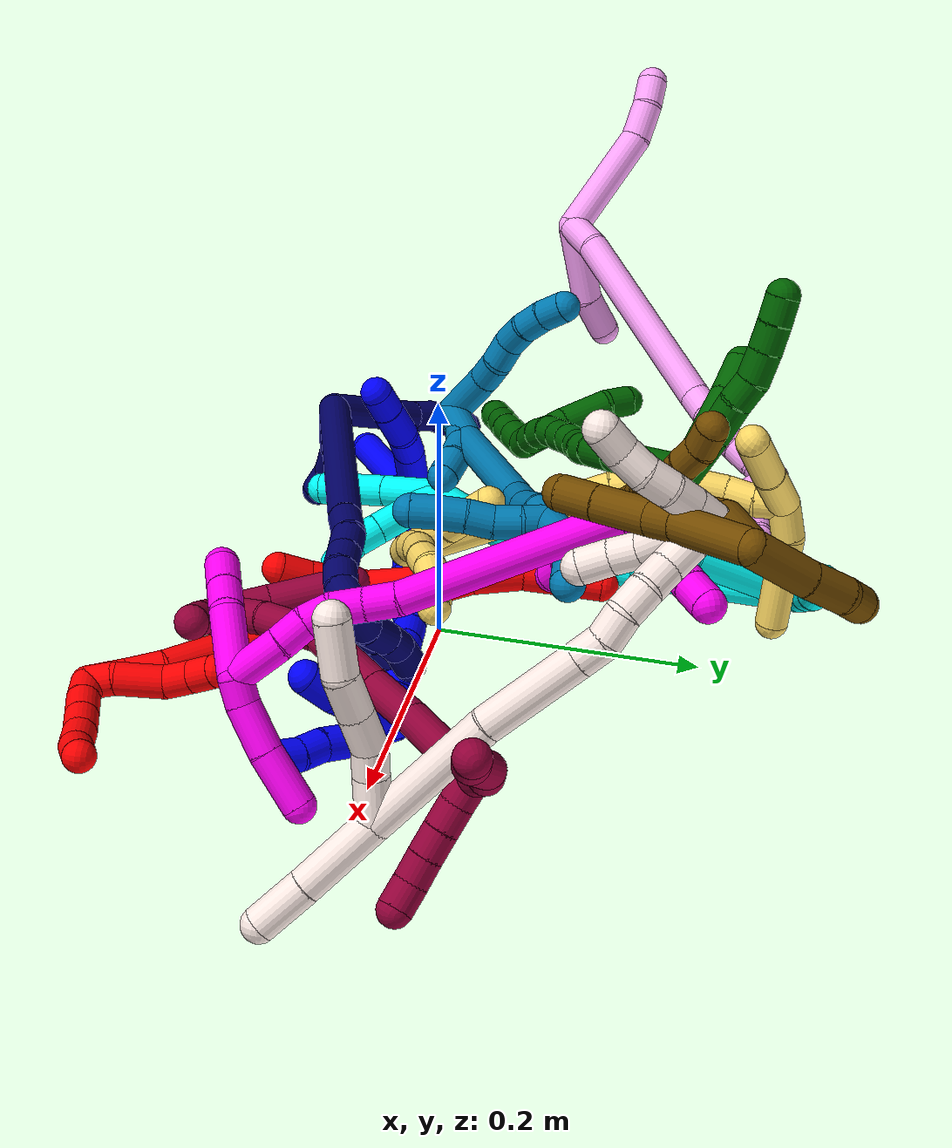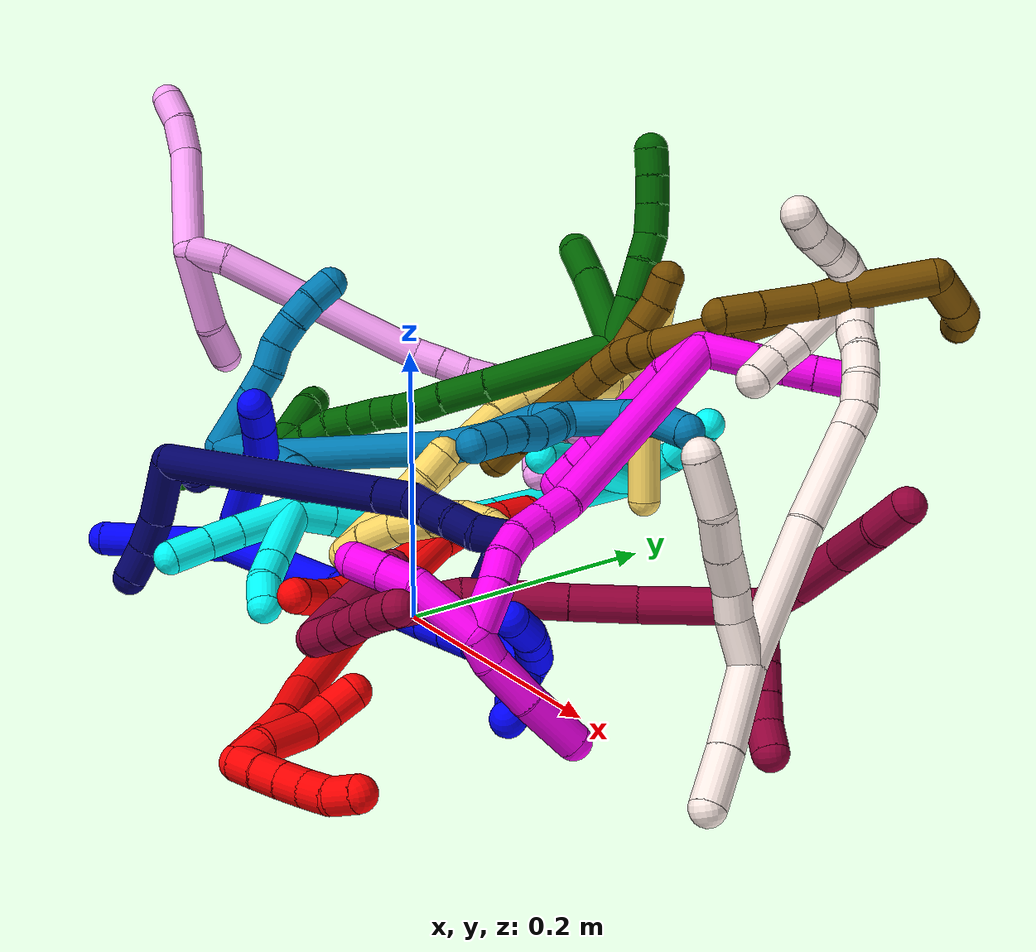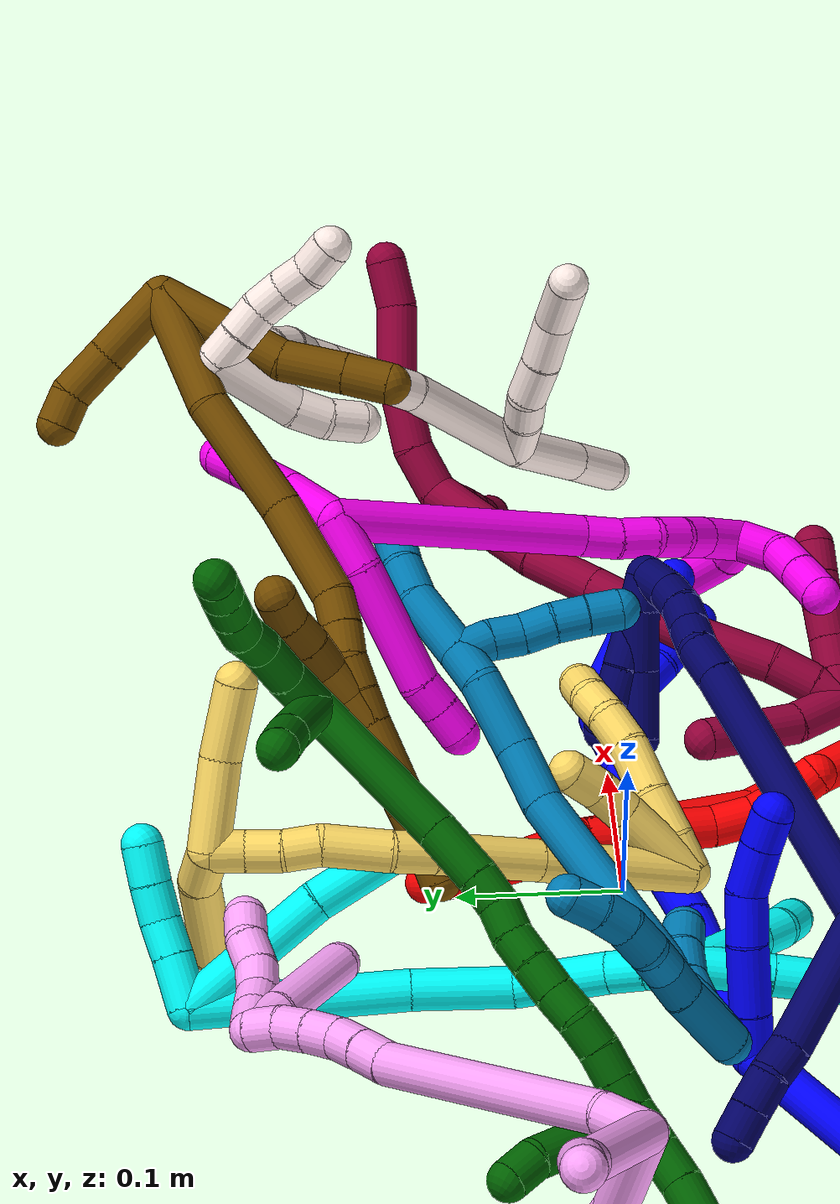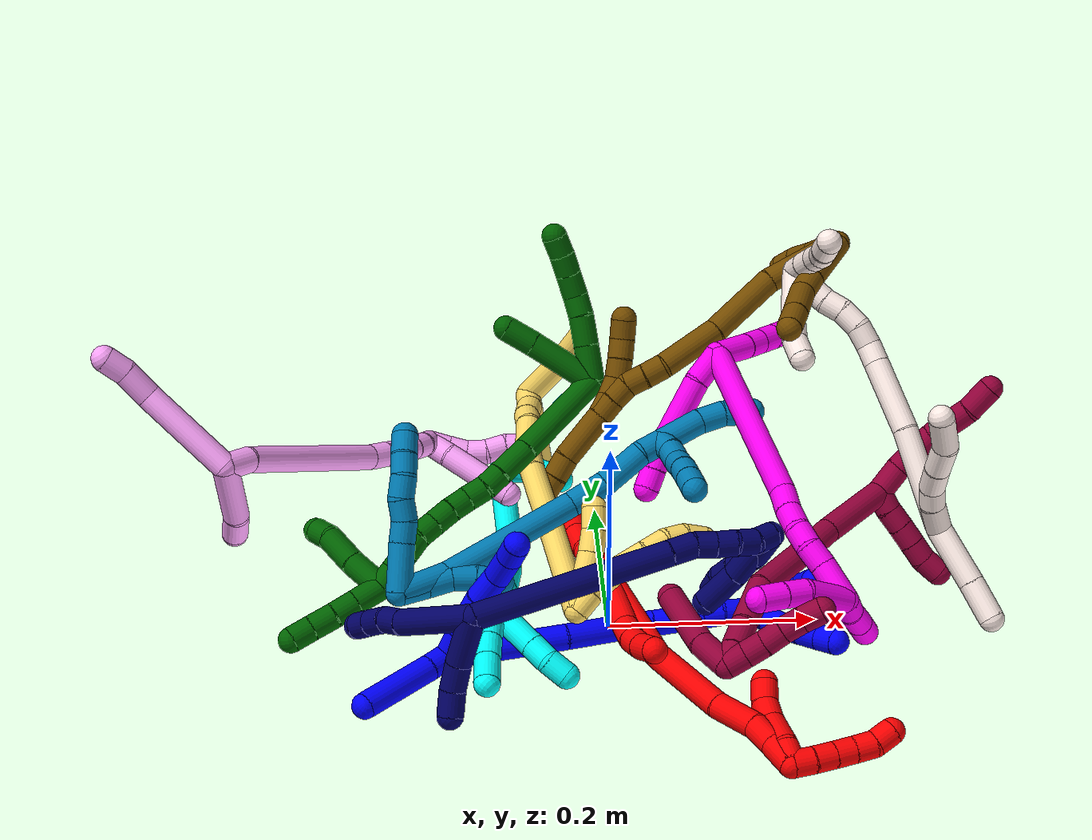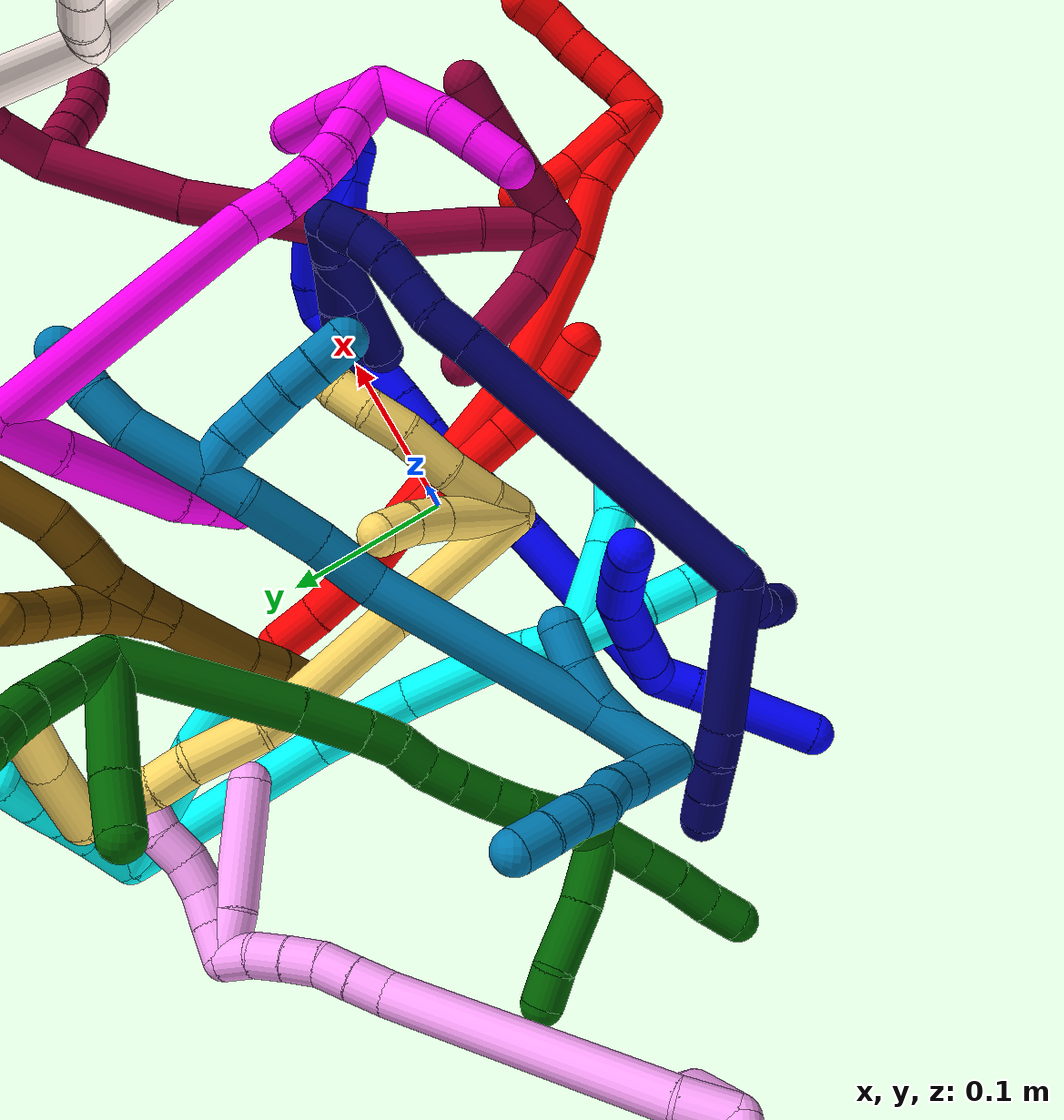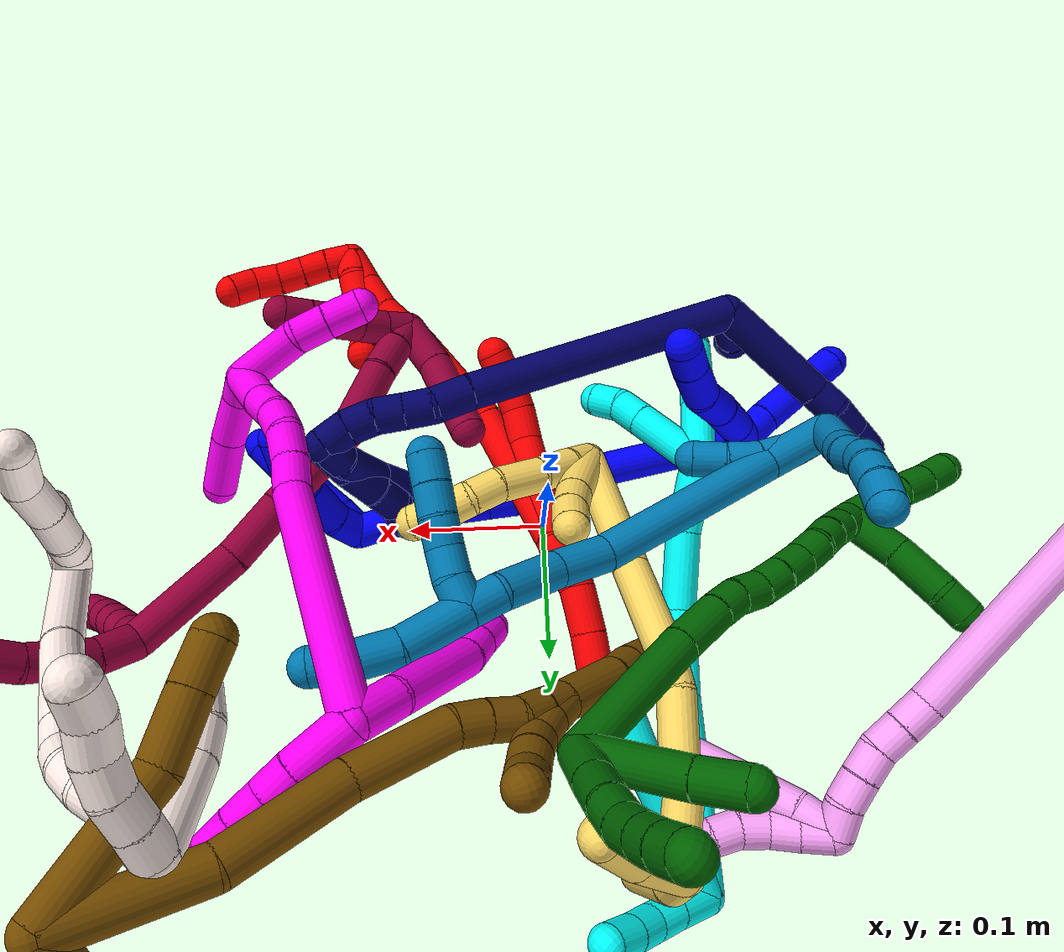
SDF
<sdf version="1.7">
 <world name="default">
  <plugin name="TubeGeneratorPlugin" filename="libtube_generator_plugin.so"/>
  <model name="photoneo_s_sensor">
   <static>1</static>
   <pose>0 0 2 1.57079 1.57079 3.14159</pose>
   <link name="link">
    <inertial><mass>0.1</mass></inertial>
    <sensor name="sensor" type="depth">
     <update_rate>30</update_rate>
     <camera>
      <horizontal_fov>1.22</horizontal_fov>
      <image><width>1920</width><height>1200</height><format>B8G8R8</format></image>
      <clip><near>0.1</near><far>4</far></clip>
      <depth_camera><output>points</output></depth_camera>
     </camera>
     <plugin name="camera_plugin" filename="libgazebo_ros_depth_camera.so">
      <baseline>0.2</baseline>
      <alwaysOn>1</alwaysOn>
      <updateRate>0.0</updateRate>
      <cameraName>camera_ir</cameraName>
      <imageTopicName>/camera/color/image_raw</imageTopicName>
      <cameraInfoTopicName>/camera/color/camera_info</cameraInfoTopicName>
      <depthImageTopicName>/camera/depth/image_raw</depthImageTopicName>
      <depthImageCameraInfoTopicName>/camera/depth/camera_info</depthImageCameraInfoTopicName>
      <pointCloudTopicName>/camera/depth/points</pointCloudTopicName>
      <frameName>fr_optical</frameName>
      <pointCloudCutoff>0.1</pointCloudCutoff>
      <pointCloudCutoffMax>2.0</pointCloudCutoffMax>
      <distortionK1>0</distortionK1>
      <distortionK2>0</distortionK2>
      <distortionK3>0</distortionK3>
      <distortionT1>0</distortionT1>
      <distortionT2>0</distortionT2>
      <CxPrime>0</CxPrime>
      <Cx>0</Cx>
      <Cy>0</Cy>
      <focalLength>0</focalLength>
      <hackBaseline>0</hackBaseline>
     </plugin>
    </sensor>
   </link>
  </model>
  <gravity>0 0 -9.8</gravity>
  <magnetic_field>6e-06 2.3e-05 -4.2e-05</magnetic_field>
  <atmosphere type="adiabatic"/>
  <physics name="default_physics" default="0" type="ode">
   <max_step_size>0.003</max_step_size>
   <real_time_factor>1</real_time_factor>
   <real_time_update_rate>1000</real_time_update_rate>
   <max_contacts>10000</max_contacts>
   <ode>
    <solver>
     <type>quick</type>
     <iters>100</iters>
     <sor>1.3</sor>
     <use_dynamic_moi_rescaling>0</use_dynamic_moi_rescaling>
    </solver>
    <constraints>
     <contact_max_correcting_vel>0</contact_max_correcting_vel>
     <contact_surface_layer>0.001</contact_surface_layer>
     <cfm>0</cfm>
     <erp>0.2</erp>
    </constraints>
   </ode>
  </physics>
  <scene><ambient>0.4 0.4 0.4 1</ambient><background>0.7 0.7 0.7 1</background><shadows>0</shadows></scene>
  <audio><device>default</device></audio>
  <spherical_coordinates>
   <surface_model>EARTH_WGS84</surface_model>
   <latitude_deg>0</latitude_deg>
   <longitude_deg>0</longitude_deg>
   <elevation>0</elevation>
   <heading_deg>0</heading_deg>
  </spherical_coordinates>
  <model name="bin">
   <static>1</static>
   <link name="bottom">
    <collision name="collision-bottom">
     <pose>0 0 -0.01 0 -0 0</pose>
     <geometry><box><size>0.8 0.6 0.02</size></box></geometry>
     <surface>
      <friction><ode><mu>100</mu><mu2>100</mu2></ode></friction>
      <contact><collide_bitmask>65535</collide_bitmask></contact>
     </surface>
    </collision>
   </link>
   <link name="west_wall">
    <collision name="collision-west_wall">
     <pose>-0.41 0 0.1 0 -0 0</pose>
     <geometry><box><size>0.02 0.6 0.2</size></box></geometry>
     <surface>
      <friction><ode><mu>100</mu><mu2>100</mu2></ode></friction>
      <contact><collide_bitmask>65535</collide_bitmask></contact>
     </surface>
    </collision>
   </link>
   <link name="east_wall">
    <collision name="collision-east_wall">
     <pose>0.41 0 0.1 0 -0 0</pose>
     <geometry><box><size>0.02 0.6 0.2</size></box></geometry>
     <surface>
      <friction><ode><mu>100</mu><mu2>100</mu2></ode></friction>
      <contact><collide_bitmask>65535</collide_bitmask></contact>
     </surface>
    </collision>
   </link>
   <link name="south_wall">
    <collision name="collision-south_wall">
     <pose>0 -0.31 0.1 0 -0 0</pose>
     <geometry><box><size>0.8 0.02 0.2</size></box></geometry>
     <surface>
      <friction><ode><mu>100</mu><mu2>100</mu2></ode></friction>
      <contact><collide_bitmask>65535</collide_bitmask></contact>
     </surface>
    </collision>
   </link>
   <link name="north_wall">
    <collision name="collision-north_wall">
     <pose>0 0.31 0.1 0 -0 0</pose>
     <geometry><box><size>0.8 0.02 0.2</size></box></geometry>
     <surface>
      <friction><ode><mu>100</mu><mu2>100</mu2></ode></friction>
      <contact><collide_bitmask>65535</collide_bitmask></contact>
     </surface>
    </collision>
   </link>
  </model>
  <model name="1">
   <static>0</static>
   <link name="1">
    <collision name="collision-cylinder-e_1_2_8">
     <pose>0.001639 0.006868 0.012306 -0.509071 0.11575 -0.030147</pose>
     <geometry><cylinder><radius>0.0125</radius><length>0.028375</length></cylinder></geometry>
     <surface>
      <friction><ode><mu>1.16</mu><mu2>1.16</mu2><slip1>0</slip1><slip2>0</slip2></ode></friction>
      <contact><ode><kp>1e+06</kp><kd>1</kd><max_vel>0</max_vel><min_depth>0.001</min_depth></ode></contact>
     </surface>
    </collision>
    <visual name="visual-cylinder-e_1_2_8">
     <pose>0.001639 0.006868 0.012306 -0.509071 0.11575 -0.030147</pose>
     <geometry><cylinder><radius>0.0125</radius><length>0.028375</length></cylinder></geometry>
     <material><ambient>0 0 1 1</ambient></material>
    </visual>
    <collision name="collision-cylinder-e_2_8_9">
     <pose>0.007035 0.02364 0.042337 -0.509504 0.183021 -0.047785</pose>
     <geometry><cylinder><radius>0.0125</radius><length>0.0413</length></cylinder></geometry>
     <surface>
      <friction><ode><mu>1.16</mu><mu2>1.16</mu2><slip1>0</slip1><slip2>0</slip2></ode></friction>
      <contact><ode><kp>1e+06</kp><kd>1</kd><max_vel>0</max_vel><min_depth>0.001</min_depth></ode></contact>
     </surface>
    </collision>
    <visual name="visual-cylinder-e_2_8_9">
     <pose>0.007035 0.02364 0.042337 -0.509504 0.183021 -0.047785</pose>
     <geometry><cylinder><radius>0.0125</radius><length>0.0413</length></cylinder></geometry>
     <material><ambient>0 0 1 1</ambient></material>
    </visual>
    <collision name="collision-cylinder-e_3_9_10">
     <pose>0.015413 0.039676 0.072849 -0.44719 0.314896 -0.072173</pose>
     <geometry><cylinder><radius>0.0125</radius><length>0.029828</length></cylinder></geometry>
     <surface>
      <friction><ode><mu>1.16</mu><mu2>1.16</mu2><slip1>0</slip1><slip2>0</slip2></ode></friction>
      <contact><ode><kp>1e+06</kp><kd>1</kd><max_vel>0</max_vel><min_depth>0.001</min_depth></ode></contact>
     </surface>
    </collision>
    <visual name="visual-cylinder-e_3_9_10">
     <pose>0.015413 0.039676 0.072849 -0.44719 0.314896 -0.072173</pose>
     <geometry><cylinder><radius>0.0125</radius><length>0.029828</length></cylinder></geometry>
     <material><ambient>0 0 1 1</ambient></material>
    </visual>
    <collision name="collision-cylinder-e_4_10_11">
     <pose>0.02132 0.0486 0.100367 -0.187309 0.08571 -0.008056</pose>
     <geometry><cylinder><radius>0.0125</radius><length>0.030099</length></cylinder></geometry>
     <surface>
      <friction><ode><mu>1.16</mu><mu2>1.16</mu2><slip1>0</slip1><slip2>0</slip2></ode></friction>
      <contact><ode><kp>1e+06</kp><kd>1</kd><max_vel>0</max_vel><min_depth>0.001</min_depth></ode></contact>
     </surface>
    </collision>
    <visual name="visual-cylinder-e_4_10_11">
     <pose>0.02132 0.0486 0.100367 -0.187309 0.08571 -0.008056</pose>
     <geometry><cylinder><radius>0.0125</radius><length>0.030099</length></cylinder></geometry>
     <material><ambient>0 0 1 1</ambient></material>
    </visual>
    <collision name="collision-cylinder-e_5_11_6">
     <pose>0.022838 0.053003 0.125168 -0.158618 0.022529 -0.001791</pose>
     <geometry><cylinder><radius>0.0125</radius><length>0.020398</length></cylinder></geometry>
     <surface>
      <friction><ode><mu>1.16</mu><mu2>1.16</mu2><slip1>0</slip1><slip2>0</slip2></ode></friction>
      <contact><ode><kp>1e+06</kp><kd>1</kd><max_vel>0</max_vel><min_depth>0.001</min_depth></ode></contact>
     </surface>
    </collision>
    <visual name="visual-cylinder-e_5_11_6">
     <pose>0.022838 0.053003 0.125168 -0.158618 0.022529 -0.001791</pose>
     <geometry><cylinder><radius>0.0125</radius><length>0.020398</length></cylinder></geometry>
     <material><ambient>0 0 1 1</ambient></material>
    </visual>
    <collision name="collision-cylinder-e_1_2_12">
     <pose>-0.009104 -0.007955 0.000461 1.51294 -0.851848 -0.80912</pose>
     <geometry><cylinder><radius>0.0125</radius><length>0.024197</length></cylinder></geometry>
     <surface>
      <friction><ode><mu>1.16</mu><mu2>1.16</mu2><slip1>0</slip1><slip2>0</slip2></ode></friction>
      <contact><ode><kp>1e+06</kp><kd>1</kd><max_vel>0</max_vel><min_depth>0.001</min_depth></ode></contact>
     </surface>
    </collision>
    <visual name="visual-cylinder-e_1_2_12">
     <pose>-0.009104 -0.007955 0.000461 1.51294 -0.851848 -0.80912</pose>
     <geometry><cylinder><radius>0.0125</radius><length>0.024197</length></cylinder></geometry>
     <material><ambient>0 0 1 1</ambient></material>
    </visual>
    <collision name="collision-cylinder-e_2_12_5">
     <pose>-0.047569 -0.03987 0.001497 1.5468 -0.886204 -0.867754</pose>
     <geometry><cylinder><radius>0.0125</radius><length>0.075803</length></cylinder></geometry>
     <surface>
      <friction><ode><mu>1.16</mu><mu2>1.16</mu2><slip1>0</slip1><slip2>0</slip2></ode></friction>
      <contact><ode><kp>1e+06</kp><kd>1</kd><max_vel>0</max_vel><min_depth>0.001</min_depth></ode></contact>
     </surface>
    </collision>
    <visual name="visual-cylinder-e_2_12_5">
     <pose>-0.047569 -0.03987 0.001497 1.5468 -0.886204 -0.867754</pose>
     <geometry><cylinder><radius>0.0125</radius><length>0.075803</length></cylinder></geometry>
     <material><ambient>0 0 1 1</ambient></material>
    </visual>
    <collision name="collision-cylinder-e_1_2_13">
     <pose>0.054178 0.013986 0.010826 -0.912072 1.25526 -0.683787</pose>
     <geometry><cylinder><radius>0.0125</radius><length>0.113983</length></cylinder></geometry>
     <surface>
      <friction><ode><mu>1.16</mu><mu2>1.16</mu2><slip1>0</slip1><slip2>0</slip2></ode></friction>
      <contact><ode><kp>1e+06</kp><kd>1</kd><max_vel>0</max_vel><min_depth>0.001</min_depth></ode></contact>
     </surface>
    </collision>
    <visual name="visual-cylinder-e_1_2_13">
     <pose>0.054178 0.013986 0.010826 -0.912072 1.25526 -0.683787</pose>
     <geometry><cylinder><radius>0.0125</radius><length>0.113983</length></cylinder></geometry>
     <material><ambient>0 0 1 1</ambient></material>
    </visual>
    <collision name="collision-cylinder-e_2_13_14">
     <pose>0.139994 0.037735 0.024725 -1.26583 1.25789 -0.980467</pose>
     <geometry><cylinder><radius>0.0125</radius><length>0.066505</length></cylinder></geometry>
     <surface>
      <friction><ode><mu>1.16</mu><mu2>1.16</mu2><slip1>0</slip1><slip2>0</slip2></ode></friction>
      <contact><ode><kp>1e+06</kp><kd>1</kd><max_vel>0</max_vel><min_depth>0.001</min_depth></ode></contact>
     </surface>
    </collision>
    <visual name="visual-cylinder-e_2_13_14">
     <pose>0.139994 0.037735 0.024725 -1.26583 1.25789 -0.980467</pose>
     <geometry><cylinder><radius>0.0125</radius><length>0.066505</length></cylinder></geometry>
     <material><ambient>0 0 1 1</ambient></material>
    </visual>
    <collision name="collision-cylinder-e_3_14_15">
     <pose>0.181547 0.049343 0.030476 -0.603149 1.25392 -0.443304</pose>
     <geometry><cylinder><radius>0.0125</radius><length>0.020869</length></cylinder></geometry>
     <surface>
      <friction><ode><mu>1.16</mu><mu2>1.16</mu2><slip1>0</slip1><slip2>0</slip2></ode></friction>
      <contact><ode><kp>1e+06</kp><kd>1</kd><max_vel>0</max_vel><min_depth>0.001</min_depth></ode></contact>
     </surface>
    </collision>
    <visual name="visual-cylinder-e_3_14_15">
     <pose>0.181547 0.049343 0.030476 -0.603149 1.25392 -0.443304</pose>
     <geometry><cylinder><radius>0.0125</radius><length>0.020869</length></cylinder></geometry>
     <material><ambient>0 0 1 1</ambient></material>
    </visual>
    <collision name="collision-cylinder-e_4_15_16">
     <pose>0.202755 0.053561 0.036363 -0.636906 1.23104 -0.458087</pose>
     <geometry><cylinder><radius>0.0125</radius><length>0.023958</length></cylinder></geometry>
     <surface>
      <friction><ode><mu>1.16</mu><mu2>1.16</mu2><slip1>0</slip1><slip2>0</slip2></ode></friction>
      <contact><ode><kp>1e+06</kp><kd>1</kd><max_vel>0</max_vel><min_depth>0.001</min_depth></ode></contact>
     </surface>
    </collision>
    <visual name="visual-cylinder-e_4_15_16">
     <pose>0.202755 0.053561 0.036363 -0.636906 1.23104 -0.458087</pose>
     <geometry><cylinder><radius>0.0125</radius><length>0.023958</length></cylinder></geometry>
     <material><ambient>0 0 1 1</ambient></material>
    </visual>
    <collision name="collision-cylinder-e_5_16_17">
     <pose>0.225191 0.058599 0.041999 -0.831969 1.25803 -0.622004</pose>
     <geometry><cylinder><radius>0.0125</radius><length>0.02342</length></cylinder></geometry>
     <surface>
      <friction><ode><mu>1.16</mu><mu2>1.16</mu2><slip1>0</slip1><slip2>0</slip2></ode></friction>
      <contact><ode><kp>1e+06</kp><kd>1</kd><max_vel>0</max_vel><min_depth>0.001</min_depth></ode></contact>
     </surface>
    </collision>
    <visual name="visual-cylinder-e_5_16_17">
     <pose>0.225191 0.058599 0.041999 -0.831969 1.25803 -0.622004</pose>
     <geometry><cylinder><radius>0.0125</radius><length>0.02342</length></cylinder></geometry>
     <material><ambient>0 0 1 1</ambient></material>
    </visual>
    <collision name="collision-cylinder-e_6_17_18">
     <pose>0.246286 0.063831 0.046574 -0.874297 1.24622 -0.647952</pose>
     <geometry><cylinder><radius>0.0125</radius><length>0.021003</length></cylinder></geometry>
     <surface>
      <friction><ode><mu>1.16</mu><mu2>1.16</mu2><slip1>0</slip1><slip2>0</slip2></ode></friction>
      <contact><ode><kp>1e+06</kp><kd>1</kd><max_vel>0</max_vel><min_depth>0.001</min_depth></ode></contact>
     </surface>
    </collision>
    <visual name="visual-cylinder-e_6_17_18">
     <pose>0.246286 0.063831 0.046574 -0.874297 1.24622 -0.647952</pose>
     <geometry><cylinder><radius>0.0125</radius><length>0.021003</length></cylinder></geometry>
     <material><ambient>0 0 1 1</ambient></material>
    </visual>
    <collision name="collision-cylinder-e_7_18_1">
     <pose>0.271007 0.069568 0.049634 -1.29063 1.35116 -1.0857</pose>
     <geometry><cylinder><radius>0.0125</radius><length>0.030263</length></cylinder></geometry>
     <surface>
      <friction><ode><mu>1.16</mu><mu2>1.16</mu2><slip1>0</slip1><slip2>0</slip2></ode></friction>
      <contact><ode><kp>1e+06</kp><kd>1</kd><max_vel>0</max_vel><min_depth>0.001</min_depth></ode></contact>
     </surface>
    </collision>
    <visual name="visual-cylinder-e_7_18_1">
     <pose>0.271007 0.069568 0.049634 -1.29063 1.35116 -1.0857</pose>
     <geometry><cylinder><radius>0.0125</radius><length>0.030263</length></cylinder></geometry>
     <material><ambient>0 0 1 1</ambient></material>
    </visual>
    <collision name="collision-cylinder-e_1_1_19">
     <pose>0.291535 0.06699 0.056359 0.779637 0.61378 0.258937</pose>
     <geometry><cylinder><radius>0.0125</radius><length>0.02</length></cylinder></geometry>
     <surface>
      <friction><ode><mu>1.16</mu><mu2>1.16</mu2><slip1>0</slip1><slip2>0</slip2></ode></friction>
      <contact><ode><kp>1e+06</kp><kd>1</kd><max_vel>0</max_vel><min_depth>0.001</min_depth></ode></contact>
     </surface>
    </collision>
    <visual name="visual-cylinder-e_1_1_19">
     <pose>0.291535 0.06699 0.056359 0.779637 0.61378 0.258937</pose>
     <geometry><cylinder><radius>0.0125</radius><length>0.02</length></cylinder></geometry>
     <material><ambient>0 0 1 1</ambient></material>
    </visual>
    <collision name="collision-cylinder-e_2_19_20">
     <pose>0.30391 0.055645 0.067163 0.842648 0.722859 0.335655</pose>
     <geometry><cylinder><radius>0.0125</radius><length>0.02</length></cylinder></geometry>
     <surface>
      <friction><ode><mu>1.16</mu><mu2>1.16</mu2><slip1>0</slip1><slip2>0</slip2></ode></friction>
      <contact><ode><kp>1e+06</kp><kd>1</kd><max_vel>0</max_vel><min_depth>0.001</min_depth></ode></contact>
     </surface>
    </collision>
    <visual name="visual-cylinder-e_2_19_20">
     <pose>0.30391 0.055645 0.067163 0.842648 0.722859 0.335655</pose>
     <geometry><cylinder><radius>0.0125</radius><length>0.02</length></cylinder></geometry>
     <material><ambient>0 0 1 1</ambient></material>
    </visual>
    <collision name="collision-cylinder-e_3_20_21">
     <pose>0.315986 0.045318 0.079068 0.599911 0.577697 0.1833</pose>
     <geometry><cylinder><radius>0.0125</radius><length>0.02</length></cylinder></geometry>
     <surface>
      <friction><ode><mu>1.16</mu><mu2>1.16</mu2><slip1>0</slip1><slip2>0</slip2></ode></friction>
      <contact><ode><kp>1e+06</kp><kd>1</kd><max_vel>0</max_vel><min_depth>0.001</min_depth></ode></contact>
     </surface>
    </collision>
    <visual name="visual-cylinder-e_3_20_21">
     <pose>0.315986 0.045318 0.079068 0.599911 0.577697 0.1833</pose>
     <geometry><cylinder><radius>0.0125</radius><length>0.02</length></cylinder></geometry>
     <material><ambient>0 0 1 1</ambient></material>
    </visual>
    <collision name="collision-cylinder-e_4_21_22">
     <pose>0.32856 0.036402 0.091629 0.638003 0.791345 0.274188</pose>
     <geometry><cylinder><radius>0.0125</radius><length>0.02</length></cylinder></geometry>
     <surface>
      <friction><ode><mu>1.16</mu><mu2>1.16</mu2><slip1>0</slip1><slip2>0</slip2></ode></friction>
      <contact><ode><kp>1e+06</kp><kd>1</kd><max_vel>0</max_vel><min_depth>0.001</min_depth></ode></contact>
     </surface>
    </collision>
    <visual name="visual-cylinder-e_4_21_22">
     <pose>0.32856 0.036402 0.091629 0.638003 0.791345 0.274188</pose>
     <geometry><cylinder><radius>0.0125</radius><length>0.02</length></cylinder></geometry>
     <material><ambient>0 0 1 1</ambient></material>
    </visual>
    <collision name="collision-cylinder-e_5_22_4">
     <pose>0.341027 0.027567 0.104326 0.582856 0.565049 0.173717</pose>
     <geometry><cylinder><radius>0.0125</radius><length>0.02</length></cylinder></geometry>
     <surface>
      <friction><ode><mu>1.16</mu><mu2>1.16</mu2><slip1>0</slip1><slip2>0</slip2></ode></friction>
      <contact><ode><kp>1e+06</kp><kd>1</kd><max_vel>0</max_vel><min_depth>0.001</min_depth></ode></contact>
     </surface>
    </collision>
    <visual name="visual-cylinder-e_5_22_4">
     <pose>0.341027 0.027567 0.104326 0.582856 0.565049 0.173717</pose>
     <geometry><cylinder><radius>0.0125</radius><length>0.02</length></cylinder></geometry>
     <material><ambient>0 0 1 1</ambient></material>
    </visual>
    <collision name="collision-cylinder-e_1_1_23">
     <pose>0.290469 0.074421 0.060008 -0.176147 0.454321 -0.040816</pose>
     <geometry><cylinder><radius>0.0125</radius><length>0.021392</length></cylinder></geometry>
     <surface>
      <friction><ode><mu>1.16</mu><mu2>1.16</mu2><slip1>0</slip1><slip2>0</slip2></ode></friction>
      <contact><ode><kp>1e+06</kp><kd>1</kd><max_vel>0</max_vel><min_depth>0.001</min_depth></ode></contact>
     </surface>
    </collision>
    <visual name="visual-cylinder-e_1_1_23">
     <pose>0.290469 0.074421 0.060008 -0.176147 0.454321 -0.040816</pose>
     <geometry><cylinder><radius>0.0125</radius><length>0.021392</length></cylinder></geometry>
     <material><ambient>0 0 1 1</ambient></material>
    </visual>
    <collision name="collision-cylinder-e_2_23_24">
     <pose>0.299482 0.075286 0.083963 0.056443 0.289151 0.00822</pose>
     <geometry><cylinder><radius>0.0125</radius><length>0.030291</length></cylinder></geometry>
     <surface>
      <friction><ode><mu>1.16</mu><mu2>1.16</mu2><slip1>0</slip1><slip2>0</slip2></ode></friction>
      <contact><ode><kp>1e+06</kp><kd>1</kd><max_vel>0</max_vel><min_depth>0.001</min_depth></ode></contact>
     </surface>
    </collision>
    <visual name="visual-cylinder-e_2_23_24">
     <pose>0.299482 0.075286 0.083963 0.056443 0.289151 0.00822</pose>
     <geometry><cylinder><radius>0.0125</radius><length>0.030291</length></cylinder></geometry>
     <material><ambient>0 0 1 1</ambient></material>
    </visual>
    <collision name="collision-cylinder-e_3_24_25">
     <pose>0.307174 0.072934 0.109227 0.141424 0.300715 0.021461</pose>
     <geometry><cylinder><radius>0.0125</radius><length>0.02278</length></cylinder></geometry>
     <surface>
      <friction><ode><mu>1.16</mu><mu2>1.16</mu2><slip1>0</slip1><slip2>0</slip2></ode></friction>
      <contact><ode><kp>1e+06</kp><kd>1</kd><max_vel>0</max_vel><min_depth>0.001</min_depth></ode></contact>
     </surface>
    </collision>
    <visual name="visual-cylinder-e_3_24_25">
     <pose>0.307174 0.072934 0.109227 0.141424 0.300715 0.021461</pose>
     <geometry><cylinder><radius>0.0125</radius><length>0.02278</length></cylinder></geometry>
     <material><ambient>0 0 1 1</ambient></material>
    </visual>
    <collision name="collision-cylinder-e_4_25_3">
     <pose>0.310449 0.067881 0.132271 0.27924 -0.007765 -0.001091</pose>
     <geometry><cylinder><radius>0.0125</radius><length>0.025537</length></cylinder></geometry>
     <surface>
      <friction><ode><mu>1.16</mu><mu2>1.16</mu2><slip1>0</slip1><slip2>0</slip2></ode></friction>
      <contact><ode><kp>1e+06</kp><kd>1</kd><max_vel>0</max_vel><min_depth>0.001</min_depth></ode></contact>
     </surface>
    </collision>
    <visual name="visual-cylinder-e_4_25_3">
     <pose>0.310449 0.067881 0.132271 0.27924 -0.007765 -0.001091</pose>
     <geometry><cylinder><radius>0.0125</radius><length>0.025537</length></cylinder></geometry>
     <material><ambient>0 0 1 1</ambient></material>
    </visual>
    <collision name="collision-sphere-3">
     <pose>0.310349 0.064362 0.144545 0 -0 0</pose>
     <geometry><sphere><radius>0.0125</radius></sphere></geometry>
     <surface>
      <friction><ode><mu>1.16</mu><mu2>1.16</mu2><slip1>0</slip1><slip2>0</slip2></ode></friction>
      <contact><ode><kp>1e+06</kp><kd>1</kd><max_vel>0</max_vel><min_depth>0.001</min_depth></ode></contact>
     </surface>
    </collision>
    <visual name="visual-sphere-3">
     <pose>0.310349 0.064362 0.144545 0 -0 0</pose>
     <geometry><sphere><radius>0.0125</radius></sphere></geometry>
     <material><ambient>0 0 1 1</ambient></material>
    </visual>
    <collision name="collision-sphere-25">
     <pose>0.310548 0.0714 0.119997 0 -0 0</pose>
     <geometry><sphere><radius>0.0125</radius></sphere></geometry>
     <surface>
      <friction><ode><mu>1.16</mu><mu2>1.16</mu2><slip1>0</slip1><slip2>0</slip2></ode></friction>
      <contact><ode><kp>1e+06</kp><kd>1</kd><max_vel>0</max_vel><min_depth>0.001</min_depth></ode></contact>
     </surface>
    </collision>
    <visual name="visual-sphere-25">
     <pose>0.310548 0.0714 0.119997 0 -0 0</pose>
     <geometry><sphere><radius>0.0125</radius></sphere></geometry>
     <material><ambient>0 0 1 1</ambient></material>
    </visual>
    <collision name="collision-sphere-24">
     <pose>0.3038 0.074467 0.098457 0 -0 0</pose>
     <geometry><sphere><radius>0.0125</radius></sphere></geometry>
     <surface>
      <friction><ode><mu>1.16</mu><mu2>1.16</mu2><slip1>0</slip1><slip2>0</slip2></ode></friction>
      <contact><ode><kp>1e+06</kp><kd>1</kd><max_vel>0</max_vel><min_depth>0.001</min_depth></ode></contact>
     </surface>
    </collision>
    <visual name="visual-sphere-24">
     <pose>0.3038 0.074467 0.098457 0 -0 0</pose>
     <geometry><sphere><radius>0.0125</radius></sphere></geometry>
     <material><ambient>0 0 1 1</ambient></material>
    </visual>
    <collision name="collision-sphere-23">
     <pose>0.295163 0.076105 0.06947 0 -0 0</pose>
     <geometry><sphere><radius>0.0125</radius></sphere></geometry>
     <surface>
      <friction><ode><mu>1.16</mu><mu2>1.16</mu2><slip1>0</slip1><slip2>0</slip2></ode></friction>
      <contact><ode><kp>1e+06</kp><kd>1</kd><max_vel>0</max_vel><min_depth>0.001</min_depth></ode></contact>
     </surface>
    </collision>
    <visual name="visual-sphere-23">
     <pose>0.295163 0.076105 0.06947 0 -0 0</pose>
     <geometry><sphere><radius>0.0125</radius></sphere></geometry>
     <material><ambient>0 0 1 1</ambient></material>
    </visual>
    <collision name="collision-sphere-4">
     <pose>0.346382 0.022919 0.111377 0 -0 0</pose>
     <geometry><sphere><radius>0.0125</radius></sphere></geometry>
     <surface>
      <friction><ode><mu>1.16</mu><mu2>1.16</mu2><slip1>0</slip1><slip2>0</slip2></ode></friction>
      <contact><ode><kp>1e+06</kp><kd>1</kd><max_vel>0</max_vel><min_depth>0.001</min_depth></ode></contact>
     </surface>
    </collision>
    <visual name="visual-sphere-4">
     <pose>0.346382 0.022919 0.111377 0 -0 0</pose>
     <geometry><sphere><radius>0.0125</radius></sphere></geometry>
     <material><ambient>0 0 1 1</ambient></material>
    </visual>
    <collision name="collision-sphere-22">
     <pose>0.335673 0.032216 0.097275 0 -0 0</pose>
     <geometry><sphere><radius>0.0125</radius></sphere></geometry>
     <surface>
      <friction><ode><mu>1.16</mu><mu2>1.16</mu2><slip1>0</slip1><slip2>0</slip2></ode></friction>
      <contact><ode><kp>1e+06</kp><kd>1</kd><max_vel>0</max_vel><min_depth>0.001</min_depth></ode></contact>
     </surface>
    </collision>
    <visual name="visual-sphere-22">
     <pose>0.335673 0.032216 0.097275 0 -0 0</pose>
     <geometry><sphere><radius>0.0125</radius></sphere></geometry>
     <material><ambient>0 0 1 1</ambient></material>
    </visual>
    <collision name="collision-sphere-21">
     <pose>0.321447 0.040589 0.085983 0 -0 0</pose>
     <geometry><sphere><radius>0.0125</radius></sphere></geometry>
     <surface>
      <friction><ode><mu>1.16</mu><mu2>1.16</mu2><slip1>0</slip1><slip2>0</slip2></ode></friction>
      <contact><ode><kp>1e+06</kp><kd>1</kd><max_vel>0</max_vel><min_depth>0.001</min_depth></ode></contact>
     </surface>
    </collision>
    <visual name="visual-sphere-21">
     <pose>0.321447 0.040589 0.085983 0 -0 0</pose>
     <geometry><sphere><radius>0.0125</radius></sphere></geometry>
     <material><ambient>0 0 1 1</ambient></material>
    </visual>
    <collision name="collision-sphere-20">
     <pose>0.310525 0.050048 0.072154 0 -0 0</pose>
     <geometry><sphere><radius>0.0125</radius></sphere></geometry>
     <surface>
      <friction><ode><mu>1.16</mu><mu2>1.16</mu2><slip1>0</slip1><slip2>0</slip2></ode></friction>
      <contact><ode><kp>1e+06</kp><kd>1</kd><max_vel>0</max_vel><min_depth>0.001</min_depth></ode></contact>
     </surface>
    </collision>
    <visual name="visual-sphere-20">
     <pose>0.310525 0.050048 0.072154 0 -0 0</pose>
     <geometry><sphere><radius>0.0125</radius></sphere></geometry>
     <material><ambient>0 0 1 1</ambient></material>
    </visual>
    <collision name="collision-sphere-6">
     <pose>0.023068 0.054614 0.135237 0 -0 0</pose>
     <geometry><sphere><radius>0.0125</radius></sphere></geometry>
     <surface>
      <friction><ode><mu>1.16</mu><mu2>1.16</mu2><slip1>0</slip1><slip2>0</slip2></ode></friction>
      <contact><ode><kp>1e+06</kp><kd>1</kd><max_vel>0</max_vel><min_depth>0.001</min_depth></ode></contact>
     </surface>
    </collision>
    <visual name="visual-sphere-6">
     <pose>0.023068 0.054614 0.135237 0 -0 0</pose>
     <geometry><sphere><radius>0.0125</radius></sphere></geometry>
     <material><ambient>0 0 1 1</ambient></material>
    </visual>
    <collision name="collision-sphere-11">
     <pose>0.022608 0.051392 0.115099 0 -0 0</pose>
     <geometry><sphere><radius>0.0125</radius></sphere></geometry>
     <surface>
      <friction><ode><mu>1.16</mu><mu2>1.16</mu2><slip1>0</slip1><slip2>0</slip2></ode></friction>
      <contact><ode><kp>1e+06</kp><kd>1</kd><max_vel>0</max_vel><min_depth>0.001</min_depth></ode></contact>
     </surface>
    </collision>
    <visual name="visual-sphere-11">
     <pose>0.022608 0.051392 0.115099 0 -0 0</pose>
     <geometry><sphere><radius>0.0125</radius></sphere></geometry>
     <material><ambient>0 0 1 1</ambient></material>
    </visual>
    <collision name="collision-sphere-10">
     <pose>0.020032 0.045808 0.085635 0 -0 0</pose>
     <geometry><sphere><radius>0.0125</radius></sphere></geometry>
     <surface>
      <friction><ode><mu>1.16</mu><mu2>1.16</mu2><slip1>0</slip1><slip2>0</slip2></ode></friction>
      <contact><ode><kp>1e+06</kp><kd>1</kd><max_vel>0</max_vel><min_depth>0.001</min_depth></ode></contact>
     </surface>
    </collision>
    <visual name="visual-sphere-10">
     <pose>0.020032 0.045808 0.085635 0 -0 0</pose>
     <geometry><sphere><radius>0.0125</radius></sphere></geometry>
     <material><ambient>0 0 1 1</ambient></material>
    </visual>
    <collision name="collision-sphere-9">
     <pose>0.010794 0.033544 0.060063 0 -0 0</pose>
     <geometry><sphere><radius>0.0125</radius></sphere></geometry>
     <surface>
      <friction><ode><mu>1.16</mu><mu2>1.16</mu2><slip1>0</slip1><slip2>0</slip2></ode></friction>
      <contact><ode><kp>1e+06</kp><kd>1</kd><max_vel>0</max_vel><min_depth>0.001</min_depth></ode></contact>
     </surface>
    </collision>
    <visual name="visual-sphere-9">
     <pose>0.010794 0.033544 0.060063 0 -0 0</pose>
     <geometry><sphere><radius>0.0125</radius></sphere></geometry>
     <material><ambient>0 0 1 1</ambient></material>
    </visual>
    <collision name="collision-sphere-2">
     <geometry><sphere><radius>0.0125</radius></sphere></geometry>
     <surface>
      <friction><ode><mu>1.16</mu><mu2>1.16</mu2><slip1>0</slip1><slip2>0</slip2></ode></friction>
      <contact><ode><kp>1e+06</kp><kd>1</kd><max_vel>0</max_vel><min_depth>0.001</min_depth></ode></contact>
     </surface>
    </collision>
    <visual name="visual-sphere-2">
     <geometry><sphere><radius>0.0125</radius></sphere></geometry>
     <material><ambient>0 0 1 1</ambient></material>
    </visual>
    <collision name="collision-sphere-19">
     <pose>0.297294 0.061243 0.062173 0 -0 0</pose>
     <geometry><sphere><radius>0.0125</radius></sphere></geometry>
     <surface>
      <friction><ode><mu>1.16</mu><mu2>1.16</mu2><slip1>0</slip1><slip2>0</slip2></ode></friction>
      <contact><ode><kp>1e+06</kp><kd>1</kd><max_vel>0</max_vel><min_depth>0.001</min_depth></ode></contact>
     </surface>
    </collision>
    <visual name="visual-sphere-19">
     <pose>0.297294 0.061243 0.062173 0 -0 0</pose>
     <geometry><sphere><radius>0.0125</radius></sphere></geometry>
     <material><ambient>0 0 1 1</ambient></material>
    </visual>
    <collision name="collision-sphere-8">
     <pose>0.003277 0.013736 0.024611 0 -0 0</pose>
     <geometry><sphere><radius>0.0125</radius></sphere></geometry>
     <surface>
      <friction><ode><mu>1.16</mu><mu2>1.16</mu2><slip1>0</slip1><slip2>0</slip2></ode></friction>
      <contact><ode><kp>1e+06</kp><kd>1</kd><max_vel>0</max_vel><min_depth>0.001</min_depth></ode></contact>
     </surface>
    </collision>
    <visual name="visual-sphere-8">
     <pose>0.003277 0.013736 0.024611 0 -0 0</pose>
     <geometry><sphere><radius>0.0125</radius></sphere></geometry>
     <material><ambient>0 0 1 1</ambient></material>
    </visual>
    <collision name="collision-sphere-12">
     <pose>-0.018208 -0.015909 0.000921 0 -0 0</pose>
     <geometry><sphere><radius>0.0125</radius></sphere></geometry>
     <surface>
      <friction><ode><mu>1.16</mu><mu2>1.16</mu2><slip1>0</slip1><slip2>0</slip2></ode></friction>
      <contact><ode><kp>1e+06</kp><kd>1</kd><max_vel>0</max_vel><min_depth>0.001</min_depth></ode></contact>
     </surface>
    </collision>
    <visual name="visual-sphere-12">
     <pose>-0.018208 -0.015909 0.000921 0 -0 0</pose>
     <geometry><sphere><radius>0.0125</radius></sphere></geometry>
     <material><ambient>0 0 1 1</ambient></material>
    </visual>
    <collision name="collision-sphere-5">
     <pose>-0.076931 -0.06383 0.002072 0 -0 0</pose>
     <geometry><sphere><radius>0.0125</radius></sphere></geometry>
     <surface>
      <friction><ode><mu>1.16</mu><mu2>1.16</mu2><slip1>0</slip1><slip2>0</slip2></ode></friction>
      <contact><ode><kp>1e+06</kp><kd>1</kd><max_vel>0</max_vel><min_depth>0.001</min_depth></ode></contact>
     </surface>
    </collision>
    <visual name="visual-sphere-5">
     <pose>-0.076931 -0.06383 0.002072 0 -0 0</pose>
     <geometry><sphere><radius>0.0125</radius></sphere></geometry>
     <material><ambient>0 0 1 1</ambient></material>
    </visual>
    <collision name="collision-sphere-13">
     <pose>0.108356 0.027971 0.021652 0 -0 0</pose>
     <geometry><sphere><radius>0.0125</radius></sphere></geometry>
     <surface>
      <friction><ode><mu>1.16</mu><mu2>1.16</mu2><slip1>0</slip1><slip2>0</slip2></ode></friction>
      <contact><ode><kp>1e+06</kp><kd>1</kd><max_vel>0</max_vel><min_depth>0.001</min_depth></ode></contact>
     </surface>
    </collision>
    <visual name="visual-sphere-13">
     <pose>0.108356 0.027971 0.021652 0 -0 0</pose>
     <geometry><sphere><radius>0.0125</radius></sphere></geometry>
     <material><ambient>0 0 1 1</ambient></material>
    </visual>
    <collision name="collision-sphere-14">
     <pose>0.171632 0.047498 0.027798 0 -0 0</pose>
     <geometry><sphere><radius>0.0125</radius></sphere></geometry>
     <surface>
      <friction><ode><mu>1.16</mu><mu2>1.16</mu2><slip1>0</slip1><slip2>0</slip2></ode></friction>
      <contact><ode><kp>1e+06</kp><kd>1</kd><max_vel>0</max_vel><min_depth>0.001</min_depth></ode></contact>
     </surface>
    </collision>
    <visual name="visual-sphere-14">
     <pose>0.171632 0.047498 0.027798 0 -0 0</pose>
     <geometry><sphere><radius>0.0125</radius></sphere></geometry>
     <material><ambient>0 0 1 1</ambient></material>
    </visual>
    <collision name="collision-sphere-15">
     <pose>0.191461 0.051187 0.033154 0 -0 0</pose>
     <geometry><sphere><radius>0.0125</radius></sphere></geometry>
     <surface>
      <friction><ode><mu>1.16</mu><mu2>1.16</mu2><slip1>0</slip1><slip2>0</slip2></ode></friction>
      <contact><ode><kp>1e+06</kp><kd>1</kd><max_vel>0</max_vel><min_depth>0.001</min_depth></ode></contact>
     </surface>
    </collision>
    <visual name="visual-sphere-15">
     <pose>0.191461 0.051187 0.033154 0 -0 0</pose>
     <geometry><sphere><radius>0.0125</radius></sphere></geometry>
     <material><ambient>0 0 1 1</ambient></material>
    </visual>
    <collision name="collision-sphere-16">
     <pose>0.214049 0.055935 0.039572 0 -0 0</pose>
     <geometry><sphere><radius>0.0125</radius></sphere></geometry>
     <surface>
      <friction><ode><mu>1.16</mu><mu2>1.16</mu2><slip1>0</slip1><slip2>0</slip2></ode></friction>
      <contact><ode><kp>1e+06</kp><kd>1</kd><max_vel>0</max_vel><min_depth>0.001</min_depth></ode></contact>
     </surface>
    </collision>
    <visual name="visual-sphere-16">
     <pose>0.214049 0.055935 0.039572 0 -0 0</pose>
     <geometry><sphere><radius>0.0125</radius></sphere></geometry>
     <material><ambient>0 0 1 1</ambient></material>
    </visual>
    <collision name="collision-sphere-17">
     <pose>0.236333 0.061262 0.044425 0 -0 0</pose>
     <geometry><sphere><radius>0.0125</radius></sphere></geometry>
     <surface>
      <friction><ode><mu>1.16</mu><mu2>1.16</mu2><slip1>0</slip1><slip2>0</slip2></ode></friction>
      <contact><ode><kp>1e+06</kp><kd>1</kd><max_vel>0</max_vel><min_depth>0.001</min_depth></ode></contact>
     </surface>
    </collision>
    <visual name="visual-sphere-17">
     <pose>0.236333 0.061262 0.044425 0 -0 0</pose>
     <geometry><sphere><radius>0.0125</radius></sphere></geometry>
     <material><ambient>0 0 1 1</ambient></material>
    </visual>
    <collision name="collision-sphere-18">
     <pose>0.256239 0.0664 0.048722 0 -0 0</pose>
     <geometry><sphere><radius>0.0125</radius></sphere></geometry>
     <surface>
      <friction><ode><mu>1.16</mu><mu2>1.16</mu2><slip1>0</slip1><slip2>0</slip2></ode></friction>
      <contact><ode><kp>1e+06</kp><kd>1</kd><max_vel>0</max_vel><min_depth>0.001</min_depth></ode></contact>
     </surface>
    </collision>
    <visual name="visual-sphere-18">
     <pose>0.256239 0.0664 0.048722 0 -0 0</pose>
     <geometry><sphere><radius>0.0125</radius></sphere></geometry>
     <material><ambient>0 0 1 1</ambient></material>
    </visual>
    <collision name="collision-sphere-1">
     <pose>0.285775 0.072737 0.050545 0 -0 0</pose>
     <geometry><sphere><radius>0.0125</radius></sphere></geometry>
     <surface>
      <friction><ode><mu>1.16</mu><mu2>1.16</mu2><slip1>0</slip1><slip2>0</slip2></ode></friction>
      <contact><ode><kp>1e+06</kp><kd>1</kd><max_vel>0</max_vel><min_depth>0.001</min_depth></ode></contact>
     </surface>
    </collision>
    <visual name="visual-sphere-1">
     <pose>0.285775 0.072737 0.050545 0 -0 0</pose>
     <geometry><sphere><radius>0.0125</radius></sphere></geometry>
     <material><ambient>0 0 1 1</ambient></material>
    </visual>
    <inertial>
     <pose>0.136919 0.0331 0.04731 0 -0 0</pose>
     <mass>0.75</mass>
     <inertia>
      <ixx>5.9e-05</ixx>
      <ixy>0</ixy>
      <ixz>0</ixz>
      <iyy>0.000162</iyy>
      <iyz>0</iyz>
      <izz>-0.000127</izz>
     </inertia>
    </inertial>
   </link>
   <pose>-0.154948 -0.060191 0.017368 0.507242 0.291212 0.079836</pose>
  </model>
  <model name="2">
   <static>0</static>
   <link name="2">
    <collision name="collision-cylinder-e_1_2_8">
     <pose>-0.006113 -0.006188 0.038562 0.159102 -0.155264 -0.012402</pose>
     <geometry><cylinder><radius>0.0125</radius><length>0.079062</length></cylinder></geometry>
     <surface>
      <friction><ode><mu>1.16</mu><mu2>1.16</mu2><slip1>0</slip1><slip2>0</slip2></ode></friction>
      <contact><ode><kp>1e+06</kp><kd>1</kd><max_vel>0</max_vel><min_depth>0.001</min_depth></ode></contact>
     </surface>
    </collision>
    <visual name="visual-cylinder-e_1_2_8">
     <pose>-0.006113 -0.006188 0.038562 0.159102 -0.155264 -0.012402</pose>
     <geometry><cylinder><radius>0.0125</radius><length>0.079062</length></cylinder></geometry>
     <material><ambient>1 0 0 1</ambient></material>
    </visual>
    <collision name="collision-cylinder-e_2_8_9">
     <pose>-0.011414 -0.013173 0.08982 0.062759 0.063726 0.002001</pose>
     <geometry><cylinder><radius>0.0125</radius><length>0.025494</length></cylinder></geometry>
     <surface>
      <friction><ode><mu>1.16</mu><mu2>1.16</mu2><slip1>0</slip1><slip2>0</slip2></ode></friction>
      <contact><ode><kp>1e+06</kp><kd>1</kd><max_vel>0</max_vel><min_depth>0.001</min_depth></ode></contact>
     </surface>
    </collision>
    <visual name="visual-cylinder-e_2_8_9">
     <pose>-0.011414 -0.013173 0.08982 0.062759 0.063726 0.002001</pose>
     <geometry><cylinder><radius>0.0125</radius><length>0.025494</length></cylinder></geometry>
     <material><ambient>1 0 0 1</ambient></material>
    </visual>
    <collision name="collision-cylinder-e_3_9_10">
     <pose>-0.007582 -0.015451 0.112464 0.147735 0.2918 0.021747</pose>
     <geometry><cylinder><radius>0.0125</radius><length>0.021001</length></cylinder></geometry>
     <surface>
      <friction><ode><mu>1.16</mu><mu2>1.16</mu2><slip1>0</slip1><slip2>0</slip2></ode></friction>
      <contact><ode><kp>1e+06</kp><kd>1</kd><max_vel>0</max_vel><min_depth>0.001</min_depth></ode></contact>
     </surface>
    </collision>
    <visual name="visual-cylinder-e_3_9_10">
     <pose>-0.007582 -0.015451 0.112464 0.147735 0.2918 0.021747</pose>
     <geometry><cylinder><radius>0.0125</radius><length>0.021001</length></cylinder></geometry>
     <material><ambient>1 0 0 1</ambient></material>
    </visual>
    <collision name="collision-cylinder-e_4_10_6">
     <pose>0.000811 -0.019225 0.133146 0.210447 0.455151 0.048908</pose>
     <geometry><cylinder><radius>0.0125</radius><length>0.024443</length></cylinder></geometry>
     <surface>
      <friction><ode><mu>1.16</mu><mu2>1.16</mu2><slip1>0</slip1><slip2>0</slip2></ode></friction>
      <contact><ode><kp>1e+06</kp><kd>1</kd><max_vel>0</max_vel><min_depth>0.001</min_depth></ode></contact>
     </surface>
    </collision>
    <visual name="visual-cylinder-e_4_10_6">
     <pose>0.000811 -0.019225 0.133146 0.210447 0.455151 0.048908</pose>
     <geometry><cylinder><radius>0.0125</radius><length>0.024443</length></cylinder></geometry>
     <material><ambient>1 0 0 1</ambient></material>
    </visual>
    <collision name="collision-cylinder-e_1_2_11">
     <pose>-0.000434 0.005848 -0.018621 -2.83727 -0.022215 0.144623</pose>
     <geometry><cylinder><radius>0.0125</radius><length>0.039044</length></cylinder></geometry>
     <surface>
      <friction><ode><mu>1.16</mu><mu2>1.16</mu2><slip1>0</slip1><slip2>0</slip2></ode></friction>
      <contact><ode><kp>1e+06</kp><kd>1</kd><max_vel>0</max_vel><min_depth>0.001</min_depth></ode></contact>
     </surface>
    </collision>
    <visual name="visual-cylinder-e_1_2_11">
     <pose>-0.000434 0.005848 -0.018621 -2.83727 -0.022215 0.144623</pose>
     <geometry><cylinder><radius>0.0125</radius><length>0.039044</length></cylinder></geometry>
     <material><ambient>1 0 0 1</ambient></material>
    </visual>
    <collision name="collision-cylinder-e_2_11_12">
     <pose>-0.00213 0.012892 -0.053684 -3.06904 -0.076438 1.62302</pose>
     <geometry><cylinder><radius>0.0125</radius><length>0.033068</length></cylinder></geometry>
     <surface>
      <friction><ode><mu>1.16</mu><mu2>1.16</mu2><slip1>0</slip1><slip2>0</slip2></ode></friction>
      <contact><ode><kp>1e+06</kp><kd>1</kd><max_vel>0</max_vel><min_depth>0.001</min_depth></ode></contact>
     </surface>
    </collision>
    <visual name="visual-cylinder-e_2_11_12">
     <pose>-0.00213 0.012892 -0.053684 -3.06904 -0.076438 1.62302</pose>
     <geometry><cylinder><radius>0.0125</radius><length>0.033068</length></cylinder></geometry>
     <material><ambient>1 0 0 1</ambient></material>
    </visual>
    <collision name="collision-cylinder-e_3_12_5">
     <pose>-0.003821 0.014387 -0.08406 -3.12007 -0.030716 1.91937</pose>
     <geometry><cylinder><radius>0.0125</radius><length>0.027887</length></cylinder></geometry>
     <surface>
      <friction><ode><mu>1.16</mu><mu2>1.16</mu2><slip1>0</slip1><slip2>0</slip2></ode></friction>
      <contact><ode><kp>1e+06</kp><kd>1</kd><max_vel>0</max_vel><min_depth>0.001</min_depth></ode></contact>
     </surface>
    </collision>
    <visual name="visual-cylinder-e_3_12_5">
     <pose>-0.003821 0.014387 -0.08406 -3.12007 -0.030716 1.91937</pose>
     <geometry><cylinder><radius>0.0125</radius><length>0.027887</length></cylinder></geometry>
     <material><ambient>1 0 0 1</ambient></material>
    </visual>
    <collision name="collision-cylinder-e_1_2_13">
     <pose>-0.010421 -0.0211 0.052546 0.38184 -0.182003 -0.03527</pose>
     <geometry><cylinder><radius>0.0125</radius><length>0.115149</length></cylinder></geometry>
     <surface>
      <friction><ode><mu>1.16</mu><mu2>1.16</mu2><slip1>0</slip1><slip2>0</slip2></ode></friction>
      <contact><ode><kp>1e+06</kp><kd>1</kd><max_vel>0</max_vel><min_depth>0.001</min_depth></ode></contact>
     </surface>
    </collision>
    <visual name="visual-cylinder-e_1_2_13">
     <pose>-0.010421 -0.0211 0.052546 0.38184 -0.182003 -0.03527</pose>
     <geometry><cylinder><radius>0.0125</radius><length>0.115149</length></cylinder></geometry>
     <material><ambient>1 0 0 1</ambient></material>
    </visual>
    <collision name="collision-cylinder-e_2_13_14">
     <pose>-0.019844 -0.06387 0.141001 0.542968 0.023787 0.006622</pose>
     <geometry><cylinder><radius>0.0125</radius><length>0.083907</length></cylinder></geometry>
     <surface>
      <friction><ode><mu>1.16</mu><mu2>1.16</mu2><slip1>0</slip1><slip2>0</slip2></ode></friction>
      <contact><ode><kp>1e+06</kp><kd>1</kd><max_vel>0</max_vel><min_depth>0.001</min_depth></ode></contact>
     </surface>
    </collision>
    <visual name="visual-cylinder-e_2_13_14">
     <pose>-0.019844 -0.06387 0.141001 0.542968 0.023787 0.006622</pose>
     <geometry><cylinder><radius>0.0125</radius><length>0.083907</length></cylinder></geometry>
     <material><ambient>1 0 0 1</ambient></material>
    </visual>
    <collision name="collision-cylinder-e_3_14_15">
     <pose>-0.015614 -0.098782 0.19398 0.659795 0.148534 0.050942</pose>
     <geometry><cylinder><radius>0.0125</radius><length>0.043688</length></cylinder></geometry>
     <surface>
      <friction><ode><mu>1.16</mu><mu2>1.16</mu2><slip1>0</slip1><slip2>0</slip2></ode></friction>
      <contact><ode><kp>1e+06</kp><kd>1</kd><max_vel>0</max_vel><min_depth>0.001</min_depth></ode></contact>
     </surface>
    </collision>
    <visual name="visual-cylinder-e_3_14_15">
     <pose>-0.015614 -0.098782 0.19398 0.659795 0.148534 0.050942</pose>
     <geometry><cylinder><radius>0.0125</radius><length>0.043688</length></cylinder></geometry>
     <material><ambient>1 0 0 1</ambient></material>
    </visual>
    <collision name="collision-cylinder-e_4_15_16">
     <pose>-0.012521 -0.117972 0.223666 0.440521 -0.010051 -0.00225</pose>
     <geometry><cylinder><radius>0.0125</radius><length>0.027898</length></cylinder></geometry>
     <surface>
      <friction><ode><mu>1.16</mu><mu2>1.16</mu2><slip1>0</slip1><slip2>0</slip2></ode></friction>
      <contact><ode><kp>1e+06</kp><kd>1</kd><max_vel>0</max_vel><min_depth>0.001</min_depth></ode></contact>
     </surface>
    </collision>
    <visual name="visual-cylinder-e_4_15_16">
     <pose>-0.012521 -0.117972 0.223666 0.440521 -0.010051 -0.00225</pose>
     <geometry><cylinder><radius>0.0125</radius><length>0.027898</length></cylinder></geometry>
     <material><ambient>1 0 0 1</ambient></material>
    </visual>
    <collision name="collision-cylinder-e_5_16_1">
     <pose>-0.012976 -0.129585 0.24982 0.396332 -0.021444 -0.004306</pose>
     <geometry><cylinder><radius>0.0125</radius><length>0.029357</length></cylinder></geometry>
     <surface>
      <friction><ode><mu>1.16</mu><mu2>1.16</mu2><slip1>0</slip1><slip2>0</slip2></ode></friction>
      <contact><ode><kp>1e+06</kp><kd>1</kd><max_vel>0</max_vel><min_depth>0.001</min_depth></ode></contact>
     </surface>
    </collision>
    <visual name="visual-cylinder-e_5_16_1">
     <pose>-0.012976 -0.129585 0.24982 0.396332 -0.021444 -0.004306</pose>
     <geometry><cylinder><radius>0.0125</radius><length>0.029357</length></cylinder></geometry>
     <material><ambient>1 0 0 1</ambient></material>
    </visual>
    <collision name="collision-cylinder-e_1_1_17">
     <pose>-0.010595 -0.133486 0.253284 -2.96823 0.257722 -1.96012</pose>
     <geometry><cylinder><radius>0.0125</radius><length>0.021153</length></cylinder></geometry>
     <surface>
      <friction><ode><mu>1.16</mu><mu2>1.16</mu2><slip1>0</slip1><slip2>0</slip2></ode></friction>
      <contact><ode><kp>1e+06</kp><kd>1</kd><max_vel>0</max_vel><min_depth>0.001</min_depth></ode></contact>
     </surface>
    </collision>
    <visual name="visual-cylinder-e_1_1_17">
     <pose>-0.010595 -0.133486 0.253284 -2.96823 0.257722 -1.96012</pose>
     <geometry><cylinder><radius>0.0125</radius><length>0.021153</length></cylinder></geometry>
     <material><ambient>1 0 0 1</ambient></material>
    </visual>
    <collision name="collision-cylinder-e_2_17_18">
     <pose>-0.008259 -0.12979 0.224728 -3.03746 -0.019353 0.367189</pose>
     <geometry><cylinder><radius>0.0125</radius><length>0.037173</length></cylinder></geometry>
     <surface>
      <friction><ode><mu>1.16</mu><mu2>1.16</mu2><slip1>0</slip1><slip2>0</slip2></ode></friction>
      <contact><ode><kp>1e+06</kp><kd>1</kd><max_vel>0</max_vel><min_depth>0.001</min_depth></ode></contact>
     </surface>
    </collision>
    <visual name="visual-cylinder-e_2_17_18">
     <pose>-0.008259 -0.12979 0.224728 -3.03746 -0.019353 0.367189</pose>
     <geometry><cylinder><radius>0.0125</radius><length>0.037173</length></cylinder></geometry>
     <material><ambient>1 0 0 1</ambient></material>
    </visual>
    <collision name="collision-cylinder-e_3_18_19">
     <pose>-0.005404 -0.125878 0.19638 -2.94347 0.309228 -2.00629</pose>
     <geometry><cylinder><radius>0.0125</radius><length>0.021128</length></cylinder></geometry>
     <surface>
      <friction><ode><mu>1.16</mu><mu2>1.16</mu2><slip1>0</slip1><slip2>0</slip2></ode></friction>
      <contact><ode><kp>1e+06</kp><kd>1</kd><max_vel>0</max_vel><min_depth>0.001</min_depth></ode></contact>
     </surface>
    </collision>
    <visual name="visual-cylinder-e_3_18_19">
     <pose>-0.005404 -0.125878 0.19638 -2.94347 0.309228 -2.00629</pose>
     <geometry><cylinder><radius>0.0125</radius><length>0.021128</length></cylinder></geometry>
     <material><ambient>1 0 0 1</ambient></material>
    </visual>
    <collision name="collision-cylinder-e_4_19_4">
     <pose>0.003308 -0.123827 0.177836 -3.13347 0.564676 -3.11358</pose>
     <geometry><cylinder><radius>0.0125</radius><length>0.020546</length></cylinder></geometry>
     <surface>
      <friction><ode><mu>1.16</mu><mu2>1.16</mu2><slip1>0</slip1><slip2>0</slip2></ode></friction>
      <contact><ode><kp>1e+06</kp><kd>1</kd><max_vel>0</max_vel><min_depth>0.001</min_depth></ode></contact>
     </surface>
    </collision>
    <visual name="visual-cylinder-e_4_19_4">
     <pose>0.003308 -0.123827 0.177836 -3.13347 0.564676 -3.11358</pose>
     <geometry><cylinder><radius>0.0125</radius><length>0.020546</length></cylinder></geometry>
     <material><ambient>1 0 0 1</ambient></material>
    </visual>
    <collision name="collision-cylinder-e_1_1_20">
     <pose>-0.009842 -0.144554 0.262118 1.7033 0.352101 0.400893</pose>
     <geometry><cylinder><radius>0.0125</radius><length>0.02</length></cylinder></geometry>
     <surface>
      <friction><ode><mu>1.16</mu><mu2>1.16</mu2><slip1>0</slip1><slip2>0</slip2></ode></friction>
      <contact><ode><kp>1e+06</kp><kd>1</kd><max_vel>0</max_vel><min_depth>0.001</min_depth></ode></contact>
     </surface>
    </collision>
    <visual name="visual-cylinder-e_1_1_20">
     <pose>-0.009842 -0.144554 0.262118 1.7033 0.352101 0.400893</pose>
     <geometry><cylinder><radius>0.0125</radius><length>0.02</length></cylinder></geometry>
     <material><ambient>1 0 0 1</ambient></material>
    </visual>
    <collision name="collision-cylinder-e_2_20_21">
     <pose>-0.003319 -0.163132 0.258746 1.79675 0.312472 0.390631</pose>
     <geometry><cylinder><radius>0.0125</radius><length>0.02</length></cylinder></geometry>
     <surface>
      <friction><ode><mu>1.16</mu><mu2>1.16</mu2><slip1>0</slip1><slip2>0</slip2></ode></friction>
      <contact><ode><kp>1e+06</kp><kd>1</kd><max_vel>0</max_vel><min_depth>0.001</min_depth></ode></contact>
     </surface>
    </collision>
    <visual name="visual-cylinder-e_2_20_21">
     <pose>-0.003319 -0.163132 0.258746 1.79675 0.312472 0.390631</pose>
     <geometry><cylinder><radius>0.0125</radius><length>0.02</length></cylinder></geometry>
     <material><ambient>1 0 0 1</ambient></material>
    </visual>
    <collision name="collision-cylinder-e_3_21_22">
     <pose>0.003129 -0.181586 0.254532 1.79385 0.344166 0.428598</pose>
     <geometry><cylinder><radius>0.0125</radius><length>0.02</length></cylinder></geometry>
     <surface>
      <friction><ode><mu>1.16</mu><mu2>1.16</mu2><slip1>0</slip1><slip2>0</slip2></ode></friction>
      <contact><ode><kp>1e+06</kp><kd>1</kd><max_vel>0</max_vel><min_depth>0.001</min_depth></ode></contact>
     </surface>
    </collision>
    <visual name="visual-cylinder-e_3_21_22">
     <pose>0.003129 -0.181586 0.254532 1.79385 0.344166 0.428598</pose>
     <geometry><cylinder><radius>0.0125</radius><length>0.02</length></cylinder></geometry>
     <material><ambient>1 0 0 1</ambient></material>
    </visual>
    <collision name="collision-cylinder-e_4_22_23">
     <pose>0.010707 -0.199748 0.251161 1.7133 0.433879 0.49802</pose>
     <geometry><cylinder><radius>0.0125</radius><length>0.02</length></cylinder></geometry>
     <surface>
      <friction><ode><mu>1.16</mu><mu2>1.16</mu2><slip1>0</slip1><slip2>0</slip2></ode></friction>
      <contact><ode><kp>1e+06</kp><kd>1</kd><max_vel>0</max_vel><min_depth>0.001</min_depth></ode></contact>
     </surface>
    </collision>
    <visual name="visual-cylinder-e_4_22_23">
     <pose>0.010707 -0.199748 0.251161 1.7133 0.433879 0.49802</pose>
     <geometry><cylinder><radius>0.0125</radius><length>0.02</length></cylinder></geometry>
     <material><ambient>1 0 0 1</ambient></material>
    </visual>
    <collision name="collision-cylinder-e_5_23_3">
     <pose>0.02078 -0.215922 0.246153 2.04806 0.627183 0.979076</pose>
     <geometry><cylinder><radius>0.0125</radius><length>0.02</length></cylinder></geometry>
     <surface>
      <friction><ode><mu>1.16</mu><mu2>1.16</mu2><slip1>0</slip1><slip2>0</slip2></ode></friction>
      <contact><ode><kp>1e+06</kp><kd>1</kd><max_vel>0</max_vel><min_depth>0.001</min_depth></ode></contact>
     </surface>
    </collision>
    <visual name="visual-cylinder-e_5_23_3">
     <pose>0.02078 -0.215922 0.246153 2.04806 0.627183 0.979076</pose>
     <geometry><cylinder><radius>0.0125</radius><length>0.02</length></cylinder></geometry>
     <material><ambient>1 0 0 1</ambient></material>
    </visual>
    <collision name="collision-sphere-3">
     <pose>0.026648 -0.223114 0.242434 0 -0 0</pose>
     <geometry><sphere><radius>0.0125</radius></sphere></geometry>
     <surface>
      <friction><ode><mu>1.16</mu><mu2>1.16</mu2><slip1>0</slip1><slip2>0</slip2></ode></friction>
      <contact><ode><kp>1e+06</kp><kd>1</kd><max_vel>0</max_vel><min_depth>0.001</min_depth></ode></contact>
     </surface>
    </collision>
    <visual name="visual-sphere-3">
     <pose>0.026648 -0.223114 0.242434 0 -0 0</pose>
     <geometry><sphere><radius>0.0125</radius></sphere></geometry>
     <material><ambient>1 0 0 1</ambient></material>
    </visual>
    <collision name="collision-sphere-23">
     <pose>0.014911 -0.20873 0.249872 0 -0 0</pose>
     <geometry><sphere><radius>0.0125</radius></sphere></geometry>
     <surface>
      <friction><ode><mu>1.16</mu><mu2>1.16</mu2><slip1>0</slip1><slip2>0</slip2></ode></friction>
      <contact><ode><kp>1e+06</kp><kd>1</kd><max_vel>0</max_vel><min_depth>0.001</min_depth></ode></contact>
     </surface>
    </collision>
    <visual name="visual-sphere-23">
     <pose>0.014911 -0.20873 0.249872 0 -0 0</pose>
     <geometry><sphere><radius>0.0125</radius></sphere></geometry>
     <material><ambient>1 0 0 1</ambient></material>
    </visual>
    <collision name="collision-sphere-22">
     <pose>0.006503 -0.190767 0.25245 0 -0 0</pose>
     <geometry><sphere><radius>0.0125</radius></sphere></geometry>
     <surface>
      <friction><ode><mu>1.16</mu><mu2>1.16</mu2><slip1>0</slip1><slip2>0</slip2></ode></friction>
      <contact><ode><kp>1e+06</kp><kd>1</kd><max_vel>0</max_vel><min_depth>0.001</min_depth></ode></contact>
     </surface>
    </collision>
    <visual name="visual-sphere-22">
     <pose>0.006503 -0.190767 0.25245 0 -0 0</pose>
     <geometry><sphere><radius>0.0125</radius></sphere></geometry>
     <material><ambient>1 0 0 1</ambient></material>
    </visual>
    <collision name="collision-sphere-21">
     <pose>-0.000245 -0.172406 0.256614 0 -0 0</pose>
     <geometry><sphere><radius>0.0125</radius></sphere></geometry>
     <surface>
      <friction><ode><mu>1.16</mu><mu2>1.16</mu2><slip1>0</slip1><slip2>0</slip2></ode></friction>
      <contact><ode><kp>1e+06</kp><kd>1</kd><max_vel>0</max_vel><min_depth>0.001</min_depth></ode></contact>
     </surface>
    </collision>
    <visual name="visual-sphere-21">
     <pose>-0.000245 -0.172406 0.256614 0 -0 0</pose>
     <geometry><sphere><radius>0.0125</radius></sphere></geometry>
     <material><ambient>1 0 0 1</ambient></material>
    </visual>
    <collision name="collision-sphere-20">
     <pose>-0.006393 -0.153858 0.260878 0 -0 0</pose>
     <geometry><sphere><radius>0.0125</radius></sphere></geometry>
     <surface>
      <friction><ode><mu>1.16</mu><mu2>1.16</mu2><slip1>0</slip1><slip2>0</slip2></ode></friction>
      <contact><ode><kp>1e+06</kp><kd>1</kd><max_vel>0</max_vel><min_depth>0.001</min_depth></ode></contact>
     </surface>
    </collision>
    <visual name="visual-sphere-20">
     <pose>-0.006393 -0.153858 0.260878 0 -0 0</pose>
     <geometry><sphere><radius>0.0125</radius></sphere></geometry>
     <material><ambient>1 0 0 1</ambient></material>
    </visual>
    <collision name="collision-sphere-4">
     <pose>0.008806 -0.123756 0.169158 0 -0 0</pose>
     <geometry><sphere><radius>0.0125</radius></sphere></geometry>
     <surface>
      <friction><ode><mu>1.16</mu><mu2>1.16</mu2><slip1>0</slip1><slip2>0</slip2></ode></friction>
      <contact><ode><kp>1e+06</kp><kd>1</kd><max_vel>0</max_vel><min_depth>0.001</min_depth></ode></contact>
     </surface>
    </collision>
    <visual name="visual-sphere-4">
     <pose>0.008806 -0.123756 0.169158 0 -0 0</pose>
     <geometry><sphere><radius>0.0125</radius></sphere></geometry>
     <material><ambient>1 0 0 1</ambient></material>
    </visual>
    <collision name="collision-sphere-11">
     <pose>-0.000867 0.011697 -0.037241 0 -0 0</pose>
     <geometry><sphere><radius>0.0125</radius></sphere></geometry>
     <surface>
      <friction><ode><mu>1.16</mu><mu2>1.16</mu2><slip1>0</slip1><slip2>0</slip2></ode></friction>
      <contact><ode><kp>1e+06</kp><kd>1</kd><max_vel>0</max_vel><min_depth>0.001</min_depth></ode></contact>
     </surface>
    </collision>
    <visual name="visual-sphere-11">
     <pose>-0.000867 0.011697 -0.037241 0 -0 0</pose>
     <geometry><sphere><radius>0.0125</radius></sphere></geometry>
     <material><ambient>1 0 0 1</ambient></material>
    </visual>
    <collision name="collision-sphere-6">
     <pose>0.006184 -0.021518 0.143881 0 -0 0</pose>
     <geometry><sphere><radius>0.0125</radius></sphere></geometry>
     <surface>
      <friction><ode><mu>1.16</mu><mu2>1.16</mu2><slip1>0</slip1><slip2>0</slip2></ode></friction>
      <contact><ode><kp>1e+06</kp><kd>1</kd><max_vel>0</max_vel><min_depth>0.001</min_depth></ode></contact>
     </surface>
    </collision>
    <visual name="visual-sphere-6">
     <pose>0.006184 -0.021518 0.143881 0 -0 0</pose>
     <geometry><sphere><radius>0.0125</radius></sphere></geometry>
     <material><ambient>1 0 0 1</ambient></material>
    </visual>
    <collision name="collision-sphere-10">
     <pose>-0.004561 -0.016932 0.122411 0 -0 0</pose>
     <geometry><sphere><radius>0.0125</radius></sphere></geometry>
     <surface>
      <friction><ode><mu>1.16</mu><mu2>1.16</mu2><slip1>0</slip1><slip2>0</slip2></ode></friction>
      <contact><ode><kp>1e+06</kp><kd>1</kd><max_vel>0</max_vel><min_depth>0.001</min_depth></ode></contact>
     </surface>
    </collision>
    <visual name="visual-sphere-10">
     <pose>-0.004561 -0.016932 0.122411 0 -0 0</pose>
     <geometry><sphere><radius>0.0125</radius></sphere></geometry>
     <material><ambient>1 0 0 1</ambient></material>
    </visual>
    <collision name="collision-sphere-9">
     <pose>-0.010603 -0.013971 0.102517 0 -0 0</pose>
     <geometry><sphere><radius>0.0125</radius></sphere></geometry>
     <surface>
      <friction><ode><mu>1.16</mu><mu2>1.16</mu2><slip1>0</slip1><slip2>0</slip2></ode></friction>
      <contact><ode><kp>1e+06</kp><kd>1</kd><max_vel>0</max_vel><min_depth>0.001</min_depth></ode></contact>
     </surface>
    </collision>
    <visual name="visual-sphere-9">
     <pose>-0.010603 -0.013971 0.102517 0 -0 0</pose>
     <geometry><sphere><radius>0.0125</radius></sphere></geometry>
     <material><ambient>1 0 0 1</ambient></material>
    </visual>
    <collision name="collision-sphere-2">
     <geometry><sphere><radius>0.0125</radius></sphere></geometry>
     <surface>
      <friction><ode><mu>1.16</mu><mu2>1.16</mu2><slip1>0</slip1><slip2>0</slip2></ode></friction>
      <contact><ode><kp>1e+06</kp><kd>1</kd><max_vel>0</max_vel><min_depth>0.001</min_depth></ode></contact>
     </surface>
    </collision>
    <visual name="visual-sphere-2">
     <geometry><sphere><radius>0.0125</radius></sphere></geometry>
     <material><ambient>1 0 0 1</ambient></material>
    </visual>
    <collision name="collision-sphere-19">
     <pose>-0.002189 -0.123897 0.186514 0 -0 0</pose>
     <geometry><sphere><radius>0.0125</radius></sphere></geometry>
     <surface>
      <friction><ode><mu>1.16</mu><mu2>1.16</mu2><slip1>0</slip1><slip2>0</slip2></ode></friction>
      <contact><ode><kp>1e+06</kp><kd>1</kd><max_vel>0</max_vel><min_depth>0.001</min_depth></ode></contact>
     </surface>
    </collision>
    <visual name="visual-sphere-19">
     <pose>-0.002189 -0.123897 0.186514 0 -0 0</pose>
     <geometry><sphere><radius>0.0125</radius></sphere></geometry>
     <material><ambient>1 0 0 1</ambient></material>
    </visual>
    <collision name="collision-sphere-8">
     <pose>-0.012226 -0.012375 0.077124 0 -0 0</pose>
     <geometry><sphere><radius>0.0125</radius></sphere></geometry>
     <surface>
      <friction><ode><mu>1.16</mu><mu2>1.16</mu2><slip1>0</slip1><slip2>0</slip2></ode></friction>
      <contact><ode><kp>1e+06</kp><kd>1</kd><max_vel>0</max_vel><min_depth>0.001</min_depth></ode></contact>
     </surface>
    </collision>
    <visual name="visual-sphere-8">
     <pose>-0.012226 -0.012375 0.077124 0 -0 0</pose>
     <geometry><sphere><radius>0.0125</radius></sphere></geometry>
     <material><ambient>1 0 0 1</ambient></material>
    </visual>
    <collision name="collision-sphere-12">
     <pose>-0.003393 0.014087 -0.070126 0 -0 0</pose>
     <geometry><sphere><radius>0.0125</radius></sphere></geometry>
     <surface>
      <friction><ode><mu>1.16</mu><mu2>1.16</mu2><slip1>0</slip1><slip2>0</slip2></ode></friction>
      <contact><ode><kp>1e+06</kp><kd>1</kd><max_vel>0</max_vel><min_depth>0.001</min_depth></ode></contact>
     </surface>
    </collision>
    <visual name="visual-sphere-12">
     <pose>-0.003393 0.014087 -0.070126 0 -0 0</pose>
     <geometry><sphere><radius>0.0125</radius></sphere></geometry>
     <material><ambient>1 0 0 1</ambient></material>
    </visual>
    <collision name="collision-sphere-5">
     <pose>-0.004249 0.014687 -0.097994 0 -0 0</pose>
     <geometry><sphere><radius>0.0125</radius></sphere></geometry>
     <surface>
      <friction><ode><mu>1.16</mu><mu2>1.16</mu2><slip1>0</slip1><slip2>0</slip2></ode></friction>
      <contact><ode><kp>1e+06</kp><kd>1</kd><max_vel>0</max_vel><min_depth>0.001</min_depth></ode></contact>
     </surface>
    </collision>
    <visual name="visual-sphere-5">
     <pose>-0.004249 0.014687 -0.097994 0 -0 0</pose>
     <geometry><sphere><radius>0.0125</radius></sphere></geometry>
     <material><ambient>1 0 0 1</ambient></material>
    </visual>
    <collision name="collision-sphere-13">
     <pose>-0.020842 -0.042199 0.105091 0 -0 0</pose>
     <geometry><sphere><radius>0.0125</radius></sphere></geometry>
     <surface>
      <friction><ode><mu>1.16</mu><mu2>1.16</mu2><slip1>0</slip1><slip2>0</slip2></ode></friction>
      <contact><ode><kp>1e+06</kp><kd>1</kd><max_vel>0</max_vel><min_depth>0.001</min_depth></ode></contact>
     </surface>
    </collision>
    <visual name="visual-sphere-13">
     <pose>-0.020842 -0.042199 0.105091 0 -0 0</pose>
     <geometry><sphere><radius>0.0125</radius></sphere></geometry>
     <material><ambient>1 0 0 1</ambient></material>
    </visual>
    <collision name="collision-sphere-14">
     <pose>-0.018846 -0.08554 0.176911 0 -0 0</pose>
     <geometry><sphere><radius>0.0125</radius></sphere></geometry>
     <surface>
      <friction><ode><mu>1.16</mu><mu2>1.16</mu2><slip1>0</slip1><slip2>0</slip2></ode></friction>
      <contact><ode><kp>1e+06</kp><kd>1</kd><max_vel>0</max_vel><min_depth>0.001</min_depth></ode></contact>
     </surface>
    </collision>
    <visual name="visual-sphere-14">
     <pose>-0.018846 -0.08554 0.176911 0 -0 0</pose>
     <geometry><sphere><radius>0.0125</radius></sphere></geometry>
     <material><ambient>1 0 0 1</ambient></material>
    </visual>
    <collision name="collision-sphere-15">
     <pose>-0.012381 -0.112024 0.211049 0 -0 0</pose>
     <geometry><sphere><radius>0.0125</radius></sphere></geometry>
     <surface>
      <friction><ode><mu>1.16</mu><mu2>1.16</mu2><slip1>0</slip1><slip2>0</slip2></ode></friction>
      <contact><ode><kp>1e+06</kp><kd>1</kd><max_vel>0</max_vel><min_depth>0.001</min_depth></ode></contact>
     </surface>
    </collision>
    <visual name="visual-sphere-15">
     <pose>-0.012381 -0.112024 0.211049 0 -0 0</pose>
     <geometry><sphere><radius>0.0125</radius></sphere></geometry>
     <material><ambient>1 0 0 1</ambient></material>
    </visual>
    <collision name="collision-sphere-16">
     <pose>-0.012661 -0.123919 0.236283 0 -0 0</pose>
     <geometry><sphere><radius>0.0125</radius></sphere></geometry>
     <surface>
      <friction><ode><mu>1.16</mu><mu2>1.16</mu2><slip1>0</slip1><slip2>0</slip2></ode></friction>
      <contact><ode><kp>1e+06</kp><kd>1</kd><max_vel>0</max_vel><min_depth>0.001</min_depth></ode></contact>
     </surface>
    </collision>
    <visual name="visual-sphere-16">
     <pose>-0.012661 -0.123919 0.236283 0 -0 0</pose>
     <geometry><sphere><radius>0.0125</radius></sphere></geometry>
     <material><ambient>1 0 0 1</ambient></material>
    </visual>
    <collision name="collision-sphere-1">
     <pose>-0.013291 -0.13525 0.263358 0 -0 0</pose>
     <geometry><sphere><radius>0.0125</radius></sphere></geometry>
     <surface>
      <friction><ode><mu>1.16</mu><mu2>1.16</mu2><slip1>0</slip1><slip2>0</slip2></ode></friction>
      <contact><ode><kp>1e+06</kp><kd>1</kd><max_vel>0</max_vel><min_depth>0.001</min_depth></ode></contact>
     </surface>
    </collision>
    <visual name="visual-sphere-1">
     <pose>-0.013291 -0.13525 0.263358 0 -0 0</pose>
     <geometry><sphere><radius>0.0125</radius></sphere></geometry>
     <material><ambient>1 0 0 1</ambient></material>
    </visual>
    <collision name="collision-sphere-18">
     <pose>-0.008619 -0.127858 0.206246 0 -0 0</pose>
     <geometry><sphere><radius>0.0125</radius></sphere></geometry>
     <surface>
      <friction><ode><mu>1.16</mu><mu2>1.16</mu2><slip1>0</slip1><slip2>0</slip2></ode></friction>
      <contact><ode><kp>1e+06</kp><kd>1</kd><max_vel>0</max_vel><min_depth>0.001</min_depth></ode></contact>
     </surface>
    </collision>
    <visual name="visual-sphere-18">
     <pose>-0.008619 -0.127858 0.206246 0 -0 0</pose>
     <geometry><sphere><radius>0.0125</radius></sphere></geometry>
     <material><ambient>1 0 0 1</ambient></material>
    </visual>
    <collision name="collision-sphere-17">
     <pose>-0.0079 -0.131722 0.243211 0 -0 0</pose>
     <geometry><sphere><radius>0.0125</radius></sphere></geometry>
     <surface>
      <friction><ode><mu>1.16</mu><mu2>1.16</mu2><slip1>0</slip1><slip2>0</slip2></ode></friction>
      <contact><ode><kp>1e+06</kp><kd>1</kd><max_vel>0</max_vel><min_depth>0.001</min_depth></ode></contact>
     </surface>
    </collision>
    <visual name="visual-sphere-17">
     <pose>-0.0079 -0.131722 0.243211 0 -0 0</pose>
     <geometry><sphere><radius>0.0125</radius></sphere></geometry>
     <material><ambient>1 0 0 1</ambient></material>
    </visual>
    <inertial>
     <pose>-0.007378 -0.067619 0.12401 0 -0 0</pose>
     <mass>0.75</mass>
     <inertia>
      <ixx>0.00027</ixx>
      <ixy>0</ixy>
      <ixz>0</ixz>
      <iyy>0.000212</iyy>
      <iyz>0</iyz>
      <izz>0.000132</izz>
     </inertia>
    </inertial>
   </link>
   <pose>-0.003766 0.023862 0.049329 1.35057 -1.23865 0.305754</pose>
  </model>
  <model name="3">
   <static>0</static>
   <link name="3">
    <collision name="collision-cylinder-e_1_2_8">
     <pose>0.020183 -0.03292 -0.029947 2.30894 0.425765 0.909385</pose>
     <geometry><cylinder><radius>0.0125</radius><length>0.097733</length></cylinder></geometry>
     <surface>
      <friction><ode><mu>1.16</mu><mu2>1.16</mu2><slip1>0</slip1><slip2>0</slip2></ode></friction>
      <contact><ode><kp>1e+06</kp><kd>1</kd><max_vel>0</max_vel><min_depth>0.001</min_depth></ode></contact>
     </surface>
    </collision>
    <visual name="visual-cylinder-e_1_2_8">
     <pose>0.020183 -0.03292 -0.029947 2.30894 0.425765 0.909385</pose>
     <geometry><cylinder><radius>0.0125</radius><length>0.097733</length></cylinder></geometry>
     <material><ambient>0.003922 1 0.996078 1</ambient></material>
    </visual>
    <collision name="collision-cylinder-e_2_8_6">
     <pose>0.047689 -0.08365 -0.077563 2.35221 0.284032 0.66129</pose>
     <geometry><cylinder><radius>0.0125</radius><length>0.052267</length></cylinder></geometry>
     <surface>
      <friction><ode><mu>1.16</mu><mu2>1.16</mu2><slip1>0</slip1><slip2>0</slip2></ode></friction>
      <contact><ode><kp>1e+06</kp><kd>1</kd><max_vel>0</max_vel><min_depth>0.001</min_depth></ode></contact>
     </surface>
    </collision>
    <visual name="visual-cylinder-e_2_8_6">
     <pose>0.047689 -0.08365 -0.077563 2.35221 0.284032 0.66129</pose>
     <geometry><cylinder><radius>0.0125</radius><length>0.052267</length></cylinder></geometry>
     <material><ambient>0.003922 1 0.996078 1</ambient></material>
    </visual>
    <collision name="collision-cylinder-e_1_2_9">
     <pose>0.015538 0.00252 -0.002308 -2.31227 1.35429 -2.13971</pose>
     <geometry><cylinder><radius>0.0125</radius><length>0.031818</length></cylinder></geometry>
     <surface>
      <friction><ode><mu>1.16</mu><mu2>1.16</mu2><slip1>0</slip1><slip2>0</slip2></ode></friction>
      <contact><ode><kp>1e+06</kp><kd>1</kd><max_vel>0</max_vel><min_depth>0.001</min_depth></ode></contact>
     </surface>
    </collision>
    <visual name="visual-cylinder-e_1_2_9">
     <pose>0.015538 0.00252 -0.002308 -2.31227 1.35429 -2.13971</pose>
     <geometry><cylinder><radius>0.0125</radius><length>0.031818</length></cylinder></geometry>
     <material><ambient>0.003922 1 0.996078 1</ambient></material>
    </visual>
    <collision name="collision-cylinder-e_2_9_10">
     <pose>0.041892 0.007121 -0.00594 -2.13759 1.34663 -1.93615</pose>
     <geometry><cylinder><radius>0.0125</radius><length>0.02219</length></cylinder></geometry>
     <surface>
      <friction><ode><mu>1.16</mu><mu2>1.16</mu2><slip1>0</slip1><slip2>0</slip2></ode></friction>
      <contact><ode><kp>1e+06</kp><kd>1</kd><max_vel>0</max_vel><min_depth>0.001</min_depth></ode></contact>
     </surface>
    </collision>
    <visual name="visual-cylinder-e_2_9_10">
     <pose>0.041892 0.007121 -0.00594 -2.13759 1.34663 -1.93615</pose>
     <geometry><cylinder><radius>0.0125</radius><length>0.02219</length></cylinder></geometry>
     <material><ambient>0.003922 1 0.996078 1</ambient></material>
    </visual>
    <collision name="collision-cylinder-e_3_10_11">
     <pose>0.063873 0.009335 -0.00764 -2.80041 1.53513 -2.78827</pose>
     <geometry><cylinder><radius>0.0125</radius><length>0.022341</length></cylinder></geometry>
     <surface>
      <friction><ode><mu>1.16</mu><mu2>1.16</mu2><slip1>0</slip1><slip2>0</slip2></ode></friction>
      <contact><ode><kp>1e+06</kp><kd>1</kd><max_vel>0</max_vel><min_depth>0.001</min_depth></ode></contact>
     </surface>
    </collision>
    <visual name="visual-cylinder-e_3_10_11">
     <pose>0.063873 0.009335 -0.00764 -2.80041 1.53513 -2.78827</pose>
     <geometry><cylinder><radius>0.0125</radius><length>0.022341</length></cylinder></geometry>
     <material><ambient>0.003922 1 0.996078 1</ambient></material>
    </visual>
    <collision name="collision-cylinder-e_4_11_5">
     <pose>0.086814 0.009327 -0.009079 3.00879 1.47995 2.99618</pose>
     <geometry><cylinder><radius>0.0125</radius><length>0.023651</length></cylinder></geometry>
     <surface>
      <friction><ode><mu>1.16</mu><mu2>1.16</mu2><slip1>0</slip1><slip2>0</slip2></ode></friction>
      <contact><ode><kp>1e+06</kp><kd>1</kd><max_vel>0</max_vel><min_depth>0.001</min_depth></ode></contact>
     </surface>
    </collision>
    <visual name="visual-cylinder-e_4_11_5">
     <pose>0.086814 0.009327 -0.009079 3.00879 1.47995 2.99618</pose>
     <geometry><cylinder><radius>0.0125</radius><length>0.023651</length></cylinder></geometry>
     <material><ambient>0.003922 1 0.996078 1</ambient></material>
    </visual>
    <collision name="collision-cylinder-e_1_2_12">
     <pose>-0.01252 -0.046588 -0.04372 2.32444 -0.193513 -0.441084</pose>
     <geometry><cylinder><radius>0.0125</radius><length>0.13021</length></cylinder></geometry>
     <surface>
      <friction><ode><mu>1.16</mu><mu2>1.16</mu2><slip1>0</slip1><slip2>0</slip2></ode></friction>
      <contact><ode><kp>1e+06</kp><kd>1</kd><max_vel>0</max_vel><min_depth>0.001</min_depth></ode></contact>
     </surface>
    </collision>
    <visual name="visual-cylinder-e_1_2_12">
     <pose>-0.01252 -0.046588 -0.04372 2.32444 -0.193513 -0.441084</pose>
     <geometry><cylinder><radius>0.0125</radius><length>0.13021</length></cylinder></geometry>
     <material><ambient>0.003922 1 0.996078 1</ambient></material>
    </visual>
    <collision name="collision-cylinder-e_2_12_13">
     <pose>-0.032457 -0.115525 -0.106442 2.27546 -0.247632 -0.525895</pose>
     <geometry><cylinder><radius>0.0125</radius><length>0.060516</length></cylinder></geometry>
     <surface>
      <friction><ode><mu>1.16</mu><mu2>1.16</mu2><slip1>0</slip1><slip2>0</slip2></ode></friction>
      <contact><ode><kp>1e+06</kp><kd>1</kd><max_vel>0</max_vel><min_depth>0.001</min_depth></ode></contact>
     </surface>
    </collision>
    <visual name="visual-cylinder-e_2_12_13">
     <pose>-0.032457 -0.115525 -0.106442 2.27546 -0.247632 -0.525895</pose>
     <geometry><cylinder><radius>0.0125</radius><length>0.060516</length></cylinder></geometry>
     <material><ambient>0.003922 1 0.996078 1</ambient></material>
    </visual>
    <collision name="collision-cylinder-e_3_13_14">
     <pose>-0.042428 -0.162894 -0.13878 2.06048 -0.089846 -0.149517</pose>
     <geometry><cylinder><radius>0.0125</radius><length>0.056935</length></cylinder></geometry>
     <surface>
      <friction><ode><mu>1.16</mu><mu2>1.16</mu2><slip1>0</slip1><slip2>0</slip2></ode></friction>
      <contact><ode><kp>1e+06</kp><kd>1</kd><max_vel>0</max_vel><min_depth>0.001</min_depth></ode></contact>
     </surface>
    </collision>
    <visual name="visual-cylinder-e_3_13_14">
     <pose>-0.042428 -0.162894 -0.13878 2.06048 -0.089846 -0.149517</pose>
     <geometry><cylinder><radius>0.0125</radius><length>0.056935</length></cylinder></geometry>
     <material><ambient>0.003922 1 0.996078 1</ambient></material>
    </visual>
    <collision name="collision-cylinder-e_4_14_15">
     <pose>-0.046373 -0.198688 -0.155847 1.90422 -0.121387 -0.170302</pose>
     <geometry><cylinder><radius>0.0125</radius><length>0.022972</length></cylinder></geometry>
     <surface>
      <friction><ode><mu>1.16</mu><mu2>1.16</mu2><slip1>0</slip1><slip2>0</slip2></ode></friction>
      <contact><ode><kp>1e+06</kp><kd>1</kd><max_vel>0</max_vel><min_depth>0.001</min_depth></ode></contact>
     </surface>
    </collision>
    <visual name="visual-cylinder-e_4_14_15">
     <pose>-0.046373 -0.198688 -0.155847 1.90422 -0.121387 -0.170302</pose>
     <geometry><cylinder><radius>0.0125</radius><length>0.022972</length></cylinder></geometry>
     <material><ambient>0.003922 1 0.996078 1</ambient></material>
    </visual>
    <collision name="collision-cylinder-e_5_15_1">
     <pose>-0.049976 -0.223062 -0.164654 1.92797 -0.15122 -0.217395</pose>
     <geometry><cylinder><radius>0.0125</radius><length>0.029367</length></cylinder></geometry>
     <surface>
      <friction><ode><mu>1.16</mu><mu2>1.16</mu2><slip1>0</slip1><slip2>0</slip2></ode></friction>
      <contact><ode><kp>1e+06</kp><kd>1</kd><max_vel>0</max_vel><min_depth>0.001</min_depth></ode></contact>
     </surface>
    </collision>
    <visual name="visual-cylinder-e_5_15_1">
     <pose>-0.049976 -0.223062 -0.164654 1.92797 -0.15122 -0.217395</pose>
     <geometry><cylinder><radius>0.0125</radius><length>0.029367</length></cylinder></geometry>
     <material><ambient>0.003922 1 0.996078 1</ambient></material>
    </visual>
    <collision name="collision-cylinder-e_1_1_16">
     <pose>-0.051922 -0.238906 -0.197786 3.06177 0.009444 0.235415</pose>
     <geometry><cylinder><radius>0.0125</radius><length>0.056295</length></cylinder></geometry>
     <surface>
      <friction><ode><mu>1.16</mu><mu2>1.16</mu2><slip1>0</slip1><slip2>0</slip2></ode></friction>
      <contact><ode><kp>1e+06</kp><kd>1</kd><max_vel>0</max_vel><min_depth>0.001</min_depth></ode></contact>
     </surface>
    </collision>
    <visual name="visual-cylinder-e_1_1_16">
     <pose>-0.051922 -0.238906 -0.197786 3.06177 0.009444 0.235415</pose>
     <geometry><cylinder><radius>0.0125</radius><length>0.056295</length></cylinder></geometry>
     <material><ambient>0.003922 1 0.996078 1</ambient></material>
    </visual>
    <collision name="collision-cylinder-e_2_16_17">
     <pose>-0.051567 -0.241913 -0.236801 3.07205 0.008069 0.230956</pose>
     <geometry><cylinder><radius>0.0125</radius><length>0.021972</length></cylinder></geometry>
     <surface>
      <friction><ode><mu>1.16</mu><mu2>1.16</mu2><slip1>0</slip1><slip2>0</slip2></ode></friction>
      <contact><ode><kp>1e+06</kp><kd>1</kd><max_vel>0</max_vel><min_depth>0.001</min_depth></ode></contact>
     </surface>
    </collision>
    <visual name="visual-cylinder-e_2_16_17">
     <pose>-0.051567 -0.241913 -0.236801 3.07205 0.008069 0.230956</pose>
     <geometry><cylinder><radius>0.0125</radius><length>0.021972</length></cylinder></geometry>
     <material><ambient>0.003922 1 0.996078 1</ambient></material>
    </visual>
    <collision name="collision-cylinder-e_3_17_4">
     <pose>-0.051298 -0.239771 -0.25823 -2.87085 0.016632 -0.121966</pose>
     <geometry><cylinder><radius>0.0125</radius><length>0.021733</length></cylinder></geometry>
     <surface>
      <friction><ode><mu>1.16</mu><mu2>1.16</mu2><slip1>0</slip1><slip2>0</slip2></ode></friction>
      <contact><ode><kp>1e+06</kp><kd>1</kd><max_vel>0</max_vel><min_depth>0.001</min_depth></ode></contact>
     </surface>
    </collision>
    <visual name="visual-cylinder-e_3_17_4">
     <pose>-0.051298 -0.239771 -0.25823 -2.87085 0.016632 -0.121966</pose>
     <geometry><cylinder><radius>0.0125</radius><length>0.021733</length></cylinder></geometry>
     <material><ambient>0.003922 1 0.996078 1</ambient></material>
    </visual>
    <collision name="collision-cylinder-e_1_1_18">
     <pose>-0.061038 -0.251925 -0.184002 2.32266 -0.400611 -0.875134</pose>
     <geometry><cylinder><radius>0.0125</radius><length>0.045387</length></cylinder></geometry>
     <surface>
      <friction><ode><mu>1.16</mu><mu2>1.16</mu2><slip1>0</slip1><slip2>0</slip2></ode></friction>
      <contact><ode><kp>1e+06</kp><kd>1</kd><max_vel>0</max_vel><min_depth>0.001</min_depth></ode></contact>
     </surface>
    </collision>
    <visual name="visual-cylinder-e_1_1_18">
     <pose>-0.061038 -0.251925 -0.184002 2.32266 -0.400611 -0.875134</pose>
     <geometry><cylinder><radius>0.0125</radius><length>0.045387</length></cylinder></geometry>
     <material><ambient>0.003922 1 0.996078 1</ambient></material>
    </visual>
    <collision name="collision-cylinder-e_2_18_19">
     <pose>-0.074879 -0.275413 -0.206474 2.3547 -0.40588 -0.920454</pose>
     <geometry><cylinder><radius>0.0125</radius><length>0.025281</length></cylinder></geometry>
     <surface>
      <friction><ode><mu>1.16</mu><mu2>1.16</mu2><slip1>0</slip1><slip2>0</slip2></ode></friction>
      <contact><ode><kp>1e+06</kp><kd>1</kd><max_vel>0</max_vel><min_depth>0.001</min_depth></ode></contact>
     </surface>
    </collision>
    <visual name="visual-cylinder-e_2_18_19">
     <pose>-0.074879 -0.275413 -0.206474 2.3547 -0.40588 -0.920454</pose>
     <geometry><cylinder><radius>0.0125</radius><length>0.025281</length></cylinder></geometry>
     <material><ambient>0.003922 1 0.996078 1</ambient></material>
    </visual>
    <collision name="collision-cylinder-e_3_19_3">
     <pose>-0.08532 -0.292972 -0.224586 2.38618 -0.380754 -0.904311</pose>
     <geometry><cylinder><radius>0.0125</radius><length>0.029331</length></cylinder></geometry>
     <surface>
      <friction><ode><mu>1.16</mu><mu2>1.16</mu2><slip1>0</slip1><slip2>0</slip2></ode></friction>
      <contact><ode><kp>1e+06</kp><kd>1</kd><max_vel>0</max_vel><min_depth>0.001</min_depth></ode></contact>
     </surface>
    </collision>
    <visual name="visual-cylinder-e_3_19_3">
     <pose>-0.08532 -0.292972 -0.224586 2.38618 -0.380754 -0.904311</pose>
     <geometry><cylinder><radius>0.0125</radius><length>0.029331</length></cylinder></geometry>
     <material><ambient>0.003922 1 0.996078 1</ambient></material>
    </visual>
    <collision name="collision-sphere-3">
     <pose>-0.09077 -0.302306 -0.234498 0 -0 0</pose>
     <geometry><sphere><radius>0.0125</radius></sphere></geometry>
     <surface>
      <friction><ode><mu>1.16</mu><mu2>1.16</mu2><slip1>0</slip1><slip2>0</slip2></ode></friction>
      <contact><ode><kp>1e+06</kp><kd>1</kd><max_vel>0</max_vel><min_depth>0.001</min_depth></ode></contact>
     </surface>
    </collision>
    <visual name="visual-sphere-3">
     <pose>-0.09077 -0.302306 -0.234498 0 -0 0</pose>
     <geometry><sphere><radius>0.0125</radius></sphere></geometry>
     <material><ambient>0.003922 1 0.996078 1</ambient></material>
    </visual>
    <collision name="collision-sphere-19">
     <pose>-0.079869 -0.283637 -0.214674 0 -0 0</pose>
     <geometry><sphere><radius>0.0125</radius></sphere></geometry>
     <surface>
      <friction><ode><mu>1.16</mu><mu2>1.16</mu2><slip1>0</slip1><slip2>0</slip2></ode></friction>
      <contact><ode><kp>1e+06</kp><kd>1</kd><max_vel>0</max_vel><min_depth>0.001</min_depth></ode></contact>
     </surface>
    </collision>
    <visual name="visual-sphere-19">
     <pose>-0.079869 -0.283637 -0.214674 0 -0 0</pose>
     <geometry><sphere><radius>0.0125</radius></sphere></geometry>
     <material><ambient>0.003922 1 0.996078 1</ambient></material>
    </visual>
    <collision name="collision-sphere-11">
     <pose>0.075037 0.009469 -0.008015 0 -0 0</pose>
     <geometry><sphere><radius>0.0125</radius></sphere></geometry>
     <surface>
      <friction><ode><mu>1.16</mu><mu2>1.16</mu2><slip1>0</slip1><slip2>0</slip2></ode></friction>
      <contact><ode><kp>1e+06</kp><kd>1</kd><max_vel>0</max_vel><min_depth>0.001</min_depth></ode></contact>
     </surface>
    </collision>
    <visual name="visual-sphere-11">
     <pose>0.075037 0.009469 -0.008015 0 -0 0</pose>
     <geometry><sphere><radius>0.0125</radius></sphere></geometry>
     <material><ambient>0.003922 1 0.996078 1</ambient></material>
    </visual>
    <collision name="collision-sphere-10">
     <pose>0.05271 0.009202 -0.007265 0 -0 0</pose>
     <geometry><sphere><radius>0.0125</radius></sphere></geometry>
     <surface>
      <friction><ode><mu>1.16</mu><mu2>1.16</mu2><slip1>0</slip1><slip2>0</slip2></ode></friction>
      <contact><ode><kp>1e+06</kp><kd>1</kd><max_vel>0</max_vel><min_depth>0.001</min_depth></ode></contact>
     </surface>
    </collision>
    <visual name="visual-sphere-10">
     <pose>0.05271 0.009202 -0.007265 0 -0 0</pose>
     <geometry><sphere><radius>0.0125</radius></sphere></geometry>
     <material><ambient>0.003922 1 0.996078 1</ambient></material>
    </visual>
    <collision name="collision-sphere-6">
     <pose>0.055012 -0.101459 -0.095231 0 -0 0</pose>
     <geometry><sphere><radius>0.0125</radius></sphere></geometry>
     <surface>
      <friction><ode><mu>1.16</mu><mu2>1.16</mu2><slip1>0</slip1><slip2>0</slip2></ode></friction>
      <contact><ode><kp>1e+06</kp><kd>1</kd><max_vel>0</max_vel><min_depth>0.001</min_depth></ode></contact>
     </surface>
    </collision>
    <visual name="visual-sphere-6">
     <pose>0.055012 -0.101459 -0.095231 0 -0 0</pose>
     <geometry><sphere><radius>0.0125</radius></sphere></geometry>
     <material><ambient>0.003922 1 0.996078 1</ambient></material>
    </visual>
    <collision name="collision-sphere-9">
     <pose>0.031075 0.005041 -0.004616 0 -0 0</pose>
     <geometry><sphere><radius>0.0125</radius></sphere></geometry>
     <surface>
      <friction><ode><mu>1.16</mu><mu2>1.16</mu2><slip1>0</slip1><slip2>0</slip2></ode></friction>
      <contact><ode><kp>1e+06</kp><kd>1</kd><max_vel>0</max_vel><min_depth>0.001</min_depth></ode></contact>
     </surface>
    </collision>
    <visual name="visual-sphere-9">
     <pose>0.031075 0.005041 -0.004616 0 -0 0</pose>
     <geometry><sphere><radius>0.0125</radius></sphere></geometry>
     <material><ambient>0.003922 1 0.996078 1</ambient></material>
    </visual>
    <collision name="collision-sphere-2">
     <geometry><sphere><radius>0.0125</radius></sphere></geometry>
     <surface>
      <friction><ode><mu>1.16</mu><mu2>1.16</mu2><slip1>0</slip1><slip2>0</slip2></ode></friction>
      <contact><ode><kp>1e+06</kp><kd>1</kd><max_vel>0</max_vel><min_depth>0.001</min_depth></ode></contact>
     </surface>
    </collision>
    <visual name="visual-sphere-2">
     <geometry><sphere><radius>0.0125</radius></sphere></geometry>
     <material><ambient>0.003922 1 0.996078 1</ambient></material>
    </visual>
    <collision name="collision-sphere-8">
     <pose>0.040365 -0.06584 -0.059895 0 -0 0</pose>
     <geometry><sphere><radius>0.0125</radius></sphere></geometry>
     <surface>
      <friction><ode><mu>1.16</mu><mu2>1.16</mu2><slip1>0</slip1><slip2>0</slip2></ode></friction>
      <contact><ode><kp>1e+06</kp><kd>1</kd><max_vel>0</max_vel><min_depth>0.001</min_depth></ode></contact>
     </surface>
    </collision>
    <visual name="visual-sphere-8">
     <pose>0.040365 -0.06584 -0.059895 0 -0 0</pose>
     <geometry><sphere><radius>0.0125</radius></sphere></geometry>
     <material><ambient>0.003922 1 0.996078 1</ambient></material>
    </visual>
    <collision name="collision-sphere-5">
     <pose>0.09859 0.009184 -0.010142 0 -0 0</pose>
     <geometry><sphere><radius>0.0125</radius></sphere></geometry>
     <surface>
      <friction><ode><mu>1.16</mu><mu2>1.16</mu2><slip1>0</slip1><slip2>0</slip2></ode></friction>
      <contact><ode><kp>1e+06</kp><kd>1</kd><max_vel>0</max_vel><min_depth>0.001</min_depth></ode></contact>
     </surface>
    </collision>
    <visual name="visual-sphere-5">
     <pose>0.09859 0.009184 -0.010142 0 -0 0</pose>
     <geometry><sphere><radius>0.0125</radius></sphere></geometry>
     <material><ambient>0.003922 1 0.996078 1</ambient></material>
    </visual>
    <collision name="collision-sphere-12">
     <pose>-0.02504 -0.093177 -0.08744 0 -0 0</pose>
     <geometry><sphere><radius>0.0125</radius></sphere></geometry>
     <surface>
      <friction><ode><mu>1.16</mu><mu2>1.16</mu2><slip1>0</slip1><slip2>0</slip2></ode></friction>
      <contact><ode><kp>1e+06</kp><kd>1</kd><max_vel>0</max_vel><min_depth>0.001</min_depth></ode></contact>
     </surface>
    </collision>
    <visual name="visual-sphere-12">
     <pose>-0.02504 -0.093177 -0.08744 0 -0 0</pose>
     <geometry><sphere><radius>0.0125</radius></sphere></geometry>
     <material><ambient>0.003922 1 0.996078 1</ambient></material>
    </visual>
    <collision name="collision-sphere-13">
     <pose>-0.039873 -0.137873 -0.125445 0 -0 0</pose>
     <geometry><sphere><radius>0.0125</radius></sphere></geometry>
     <surface>
      <friction><ode><mu>1.16</mu><mu2>1.16</mu2><slip1>0</slip1><slip2>0</slip2></ode></friction>
      <contact><ode><kp>1e+06</kp><kd>1</kd><max_vel>0</max_vel><min_depth>0.001</min_depth></ode></contact>
     </surface>
    </collision>
    <visual name="visual-sphere-13">
     <pose>-0.039873 -0.137873 -0.125445 0 -0 0</pose>
     <geometry><sphere><radius>0.0125</radius></sphere></geometry>
     <material><ambient>0.003922 1 0.996078 1</ambient></material>
    </visual>
    <collision name="collision-sphere-14">
     <pose>-0.044982 -0.187915 -0.152116 0 -0 0</pose>
     <geometry><sphere><radius>0.0125</radius></sphere></geometry>
     <surface>
      <friction><ode><mu>1.16</mu><mu2>1.16</mu2><slip1>0</slip1><slip2>0</slip2></ode></friction>
      <contact><ode><kp>1e+06</kp><kd>1</kd><max_vel>0</max_vel><min_depth>0.001</min_depth></ode></contact>
     </surface>
    </collision>
    <visual name="visual-sphere-14">
     <pose>-0.044982 -0.187915 -0.152116 0 -0 0</pose>
     <geometry><sphere><radius>0.0125</radius></sphere></geometry>
     <material><ambient>0.003922 1 0.996078 1</ambient></material>
    </visual>
    <collision name="collision-sphere-15">
     <pose>-0.047764 -0.209462 -0.159579 0 -0 0</pose>
     <geometry><sphere><radius>0.0125</radius></sphere></geometry>
     <surface>
      <friction><ode><mu>1.16</mu><mu2>1.16</mu2><slip1>0</slip1><slip2>0</slip2></ode></friction>
      <contact><ode><kp>1e+06</kp><kd>1</kd><max_vel>0</max_vel><min_depth>0.001</min_depth></ode></contact>
     </surface>
    </collision>
    <visual name="visual-sphere-15">
     <pose>-0.047764 -0.209462 -0.159579 0 -0 0</pose>
     <geometry><sphere><radius>0.0125</radius></sphere></geometry>
     <material><ambient>0.003922 1 0.996078 1</ambient></material>
    </visual>
    <collision name="collision-sphere-1">
     <pose>-0.052188 -0.236662 -0.169729 0 -0 0</pose>
     <geometry><sphere><radius>0.0125</radius></sphere></geometry>
     <surface>
      <friction><ode><mu>1.16</mu><mu2>1.16</mu2><slip1>0</slip1><slip2>0</slip2></ode></friction>
      <contact><ode><kp>1e+06</kp><kd>1</kd><max_vel>0</max_vel><min_depth>0.001</min_depth></ode></contact>
     </surface>
    </collision>
    <visual name="visual-sphere-1">
     <pose>-0.052188 -0.236662 -0.169729 0 -0 0</pose>
     <geometry><sphere><radius>0.0125</radius></sphere></geometry>
     <material><ambient>0.003922 1 0.996078 1</ambient></material>
    </visual>
    <collision name="collision-sphere-18">
     <pose>-0.069888 -0.267188 -0.198275 0 -0 0</pose>
     <geometry><sphere><radius>0.0125</radius></sphere></geometry>
     <surface>
      <friction><ode><mu>1.16</mu><mu2>1.16</mu2><slip1>0</slip1><slip2>0</slip2></ode></friction>
      <contact><ode><kp>1e+06</kp><kd>1</kd><max_vel>0</max_vel><min_depth>0.001</min_depth></ode></contact>
     </surface>
    </collision>
    <visual name="visual-sphere-18">
     <pose>-0.069888 -0.267188 -0.198275 0 -0 0</pose>
     <geometry><sphere><radius>0.0125</radius></sphere></geometry>
     <material><ambient>0.003922 1 0.996078 1</ambient></material>
    </visual>
    <collision name="collision-sphere-16">
     <pose>-0.051656 -0.24115 -0.225842 0 -0 0</pose>
     <geometry><sphere><radius>0.0125</radius></sphere></geometry>
     <surface>
      <friction><ode><mu>1.16</mu><mu2>1.16</mu2><slip1>0</slip1><slip2>0</slip2></ode></friction>
      <contact><ode><kp>1e+06</kp><kd>1</kd><max_vel>0</max_vel><min_depth>0.001</min_depth></ode></contact>
     </surface>
    </collision>
    <visual name="visual-sphere-16">
     <pose>-0.051656 -0.24115 -0.225842 0 -0 0</pose>
     <geometry><sphere><radius>0.0125</radius></sphere></geometry>
     <material><ambient>0.003922 1 0.996078 1</ambient></material>
    </visual>
    <collision name="collision-sphere-17">
     <pose>-0.051479 -0.242677 -0.24776 0 -0 0</pose>
     <geometry><sphere><radius>0.0125</radius></sphere></geometry>
     <surface>
      <friction><ode><mu>1.16</mu><mu2>1.16</mu2><slip1>0</slip1><slip2>0</slip2></ode></friction>
      <contact><ode><kp>1e+06</kp><kd>1</kd><max_vel>0</max_vel><min_depth>0.001</min_depth></ode></contact>
     </surface>
    </collision>
    <visual name="visual-sphere-17">
     <pose>-0.051479 -0.242677 -0.24776 0 -0 0</pose>
     <geometry><sphere><radius>0.0125</radius></sphere></geometry>
     <material><ambient>0.003922 1 0.996078 1</ambient></material>
    </visual>
    <collision name="collision-sphere-4">
     <pose>-0.051117 -0.236865 -0.268699 0 -0 0</pose>
     <geometry><sphere><radius>0.0125</radius></sphere></geometry>
     <surface>
      <friction><ode><mu>1.16</mu><mu2>1.16</mu2><slip1>0</slip1><slip2>0</slip2></ode></friction>
      <contact><ode><kp>1e+06</kp><kd>1</kd><max_vel>0</max_vel><min_depth>0.001</min_depth></ode></contact>
     </surface>
    </collision>
    <visual name="visual-sphere-4">
     <pose>-0.051117 -0.236865 -0.268699 0 -0 0</pose>
     <geometry><sphere><radius>0.0125</radius></sphere></geometry>
     <material><ambient>0.003922 1 0.996078 1</ambient></material>
    </visual>
    <inertial>
     <pose>-0.015347 -0.121779 -0.104175 0 -0 0</pose>
     <mass>0.75</mass>
     <inertia>
      <ixx>0.000263</ixx>
      <ixy>0</ixy>
      <ixz>0</ixz>
      <iyy>-0.000224</iyy>
      <iyz>0</iyz>
      <izz>0.000214</izz>
     </inertia>
    </inertial>
   </link>
   <pose>-0.093774 0.262911 0.013529 -1.02126 -0.839855 0.355076</pose>
  </model>
  <model name="4">
   <static>0</static>
   <link name="4">
    <collision name="collision-cylinder-e_1_2_8">
     <pose>-0.010953 0.015785 0.044122 -0.343575 -0.229618 0.040009</pose>
     <geometry><cylinder><radius>0.0125</radius><length>0.096247</length></cylinder></geometry>
     <surface>
      <friction><ode><mu>1.16</mu><mu2>1.16</mu2><slip1>0</slip1><slip2>0</slip2></ode></friction>
      <contact><ode><kp>1e+06</kp><kd>1</kd><max_vel>0</max_vel><min_depth>0.001</min_depth></ode></contact>
     </surface>
    </collision>
    <visual name="visual-cylinder-e_1_2_8">
     <pose>-0.010953 0.015785 0.044122 -0.343575 -0.229618 0.040009</pose>
     <geometry><cylinder><radius>0.0125</radius><length>0.096247</length></cylinder></geometry>
     <material><ambient>1 0.65098 0.996078 1</ambient></material>
    </visual>
    <collision name="collision-cylinder-e_2_8_9">
     <pose>-0.024135 0.032466 0.103374 -0.059109 -0.145977 0.004323</pose>
     <geometry><cylinder><radius>0.0125</radius><length>0.030639</length></cylinder></geometry>
     <surface>
      <friction><ode><mu>1.16</mu><mu2>1.16</mu2><slip1>0</slip1><slip2>0</slip2></ode></friction>
      <contact><ode><kp>1e+06</kp><kd>1</kd><max_vel>0</max_vel><min_depth>0.001</min_depth></ode></contact>
     </surface>
    </collision>
    <visual name="visual-cylinder-e_2_8_9">
     <pose>-0.024135 0.032466 0.103374 -0.059109 -0.145977 0.004323</pose>
     <geometry><cylinder><radius>0.0125</radius><length>0.030639</length></cylinder></geometry>
     <material><ambient>1 0.65098 0.996078 1</ambient></material>
    </visual>
    <collision name="collision-cylinder-e_3_9_6">
     <pose>-0.030357 0.03298 0.129342 0.035111 -0.352864 -0.00626</pose>
     <geometry><cylinder><radius>0.0125</radius><length>0.023114</length></cylinder></geometry>
     <surface>
      <friction><ode><mu>1.16</mu><mu2>1.16</mu2><slip1>0</slip1><slip2>0</slip2></ode></friction>
      <contact><ode><kp>1e+06</kp><kd>1</kd><max_vel>0</max_vel><min_depth>0.001</min_depth></ode></contact>
     </surface>
    </collision>
    <visual name="visual-cylinder-e_3_9_6">
     <pose>-0.030357 0.03298 0.129342 0.035111 -0.352864 -0.00626</pose>
     <geometry><cylinder><radius>0.0125</radius><length>0.023114</length></cylinder></geometry>
     <material><ambient>1 0.65098 0.996078 1</ambient></material>
    </visual>
    <collision name="collision-cylinder-e_1_2_10">
     <pose>-0.0111 0.015228 -0.027043 -2.62874 -0.343484 1.16887</pose>
     <geometry><cylinder><radius>0.0125</radius><length>0.065923</length></cylinder></geometry>
     <surface>
      <friction><ode><mu>1.16</mu><mu2>1.16</mu2><slip1>0</slip1><slip2>0</slip2></ode></friction>
      <contact><ode><kp>1e+06</kp><kd>1</kd><max_vel>0</max_vel><min_depth>0.001</min_depth></ode></contact>
     </surface>
    </collision>
    <visual name="visual-cylinder-e_1_2_10">
     <pose>-0.0111 0.015228 -0.027043 -2.62874 -0.343484 1.16887</pose>
     <geometry><cylinder><radius>0.0125</radius><length>0.065923</length></cylinder></geometry>
     <material><ambient>1 0.65098 0.996078 1</ambient></material>
    </visual>
    <collision name="collision-cylinder-e_2_10_5">
     <pose>-0.029104 0.041977 -0.064572 -2.3092 -0.417161 0.893161</pose>
     <geometry><cylinder><radius>0.0125</radius><length>0.034077</length></cylinder></geometry>
     <surface>
      <friction><ode><mu>1.16</mu><mu2>1.16</mu2><slip1>0</slip1><slip2>0</slip2></ode></friction>
      <contact><ode><kp>1e+06</kp><kd>1</kd><max_vel>0</max_vel><min_depth>0.001</min_depth></ode></contact>
     </surface>
    </collision>
    <visual name="visual-cylinder-e_2_10_5">
     <pose>-0.029104 0.041977 -0.064572 -2.3092 -0.417161 0.893161</pose>
     <geometry><cylinder><radius>0.0125</radius><length>0.034077</length></cylinder></geometry>
     <material><ambient>1 0.65098 0.996078 1</ambient></material>
    </visual>
    <collision name="collision-cylinder-e_1_2_11">
     <pose>0.009981 0.009377 -0.006169 -2.1527 0.726846 -1.22874</pose>
     <geometry><cylinder><radius>0.0125</radius><length>0.030041</length></cylinder></geometry>
     <surface>
      <friction><ode><mu>1.16</mu><mu2>1.16</mu2><slip1>0</slip1><slip2>0</slip2></ode></friction>
      <contact><ode><kp>1e+06</kp><kd>1</kd><max_vel>0</max_vel><min_depth>0.001</min_depth></ode></contact>
     </surface>
    </collision>
    <visual name="visual-cylinder-e_1_2_11">
     <pose>0.009981 0.009377 -0.006169 -2.1527 0.726846 -1.22874</pose>
     <geometry><cylinder><radius>0.0125</radius><length>0.030041</length></cylinder></geometry>
     <material><ambient>1 0.65098 0.996078 1</ambient></material>
    </visual>
    <collision name="collision-cylinder-e_2_11_12">
     <pose>0.063258 0.071864 -0.060954 -2.31205 0.541382 -1.12471</pose>
     <geometry><cylinder><radius>0.0125</radius><length>0.168031</length></cylinder></geometry>
     <surface>
      <friction><ode><mu>1.16</mu><mu2>1.16</mu2><slip1>0</slip1><slip2>0</slip2></ode></friction>
      <contact><ode><kp>1e+06</kp><kd>1</kd><max_vel>0</max_vel><min_depth>0.001</min_depth></ode></contact>
     </surface>
    </collision>
    <visual name="visual-cylinder-e_2_11_12">
     <pose>0.063258 0.071864 -0.060954 -2.31205 0.541382 -1.12471</pose>
     <geometry><cylinder><radius>0.0125</radius><length>0.168031</length></cylinder></geometry>
     <material><ambient>1 0.65098 0.996078 1</ambient></material>
    </visual>
    <collision name="collision-cylinder-e_3_12_13">
     <pose>0.113849 0.130801 -0.114912 -2.31268 0.745371 -1.45303</pose>
     <geometry><cylinder><radius>0.0125</radius><length>0.021516</length></cylinder></geometry>
     <surface>
      <friction><ode><mu>1.16</mu><mu2>1.16</mu2><slip1>0</slip1><slip2>0</slip2></ode></friction>
      <contact><ode><kp>1e+06</kp><kd>1</kd><max_vel>0</max_vel><min_depth>0.001</min_depth></ode></contact>
     </surface>
    </collision>
    <visual name="visual-cylinder-e_3_12_13">
     <pose>0.113849 0.130801 -0.114912 -2.31268 0.745371 -1.45303</pose>
     <geometry><cylinder><radius>0.0125</radius><length>0.021516</length></cylinder></geometry>
     <material><ambient>1 0.65098 0.996078 1</ambient></material>
    </visual>
    <collision name="collision-cylinder-e_4_13_14">
     <pose>0.127728 0.142197 -0.125649 -2.3405 0.703925 -1.42892</pose>
     <geometry><cylinder><radius>0.0125</radius><length>0.020341</length></cylinder></geometry>
     <surface>
      <friction><ode><mu>1.16</mu><mu2>1.16</mu2><slip1>0</slip1><slip2>0</slip2></ode></friction>
      <contact><ode><kp>1e+06</kp><kd>1</kd><max_vel>0</max_vel><min_depth>0.001</min_depth></ode></contact>
     </surface>
    </collision>
    <visual name="visual-cylinder-e_4_13_14">
     <pose>0.127728 0.142197 -0.125649 -2.3405 0.703925 -1.42892</pose>
     <geometry><cylinder><radius>0.0125</radius><length>0.020341</length></cylinder></geometry>
     <material><ambient>1 0.65098 0.996078 1</ambient></material>
    </visual>
    <collision name="collision-cylinder-e_5_14_15">
     <pose>0.139948 0.155045 -0.135016 -2.0702 0.59696 -0.956391</pose>
     <geometry><cylinder><radius>0.0125</radius><length>0.020055</length></cylinder></geometry>
     <surface>
      <friction><ode><mu>1.16</mu><mu2>1.16</mu2><slip1>0</slip1><slip2>0</slip2></ode></friction>
      <contact><ode><kp>1e+06</kp><kd>1</kd><max_vel>0</max_vel><min_depth>0.001</min_depth></ode></contact>
     </surface>
    </collision>
    <visual name="visual-cylinder-e_5_14_15">
     <pose>0.139948 0.155045 -0.135016 -2.0702 0.59696 -0.956391</pose>
     <geometry><cylinder><radius>0.0125</radius><length>0.020055</length></cylinder></geometry>
     <material><ambient>1 0.65098 0.996078 1</ambient></material>
    </visual>
    <collision name="collision-cylinder-e_6_15_16">
     <pose>0.150637 0.169938 -0.143069 -2.06287 0.529246 -0.850219</pose>
     <geometry><cylinder><radius>0.0125</radius><length>0.020014</length></cylinder></geometry>
     <surface>
      <friction><ode><mu>1.16</mu><mu2>1.16</mu2><slip1>0</slip1><slip2>0</slip2></ode></friction>
      <contact><ode><kp>1e+06</kp><kd>1</kd><max_vel>0</max_vel><min_depth>0.001</min_depth></ode></contact>
     </surface>
    </collision>
    <visual name="visual-cylinder-e_6_15_16">
     <pose>0.150637 0.169938 -0.143069 -2.06287 0.529246 -0.850219</pose>
     <geometry><cylinder><radius>0.0125</radius><length>0.020014</length></cylinder></geometry>
     <material><ambient>1 0.65098 0.996078 1</ambient></material>
    </visual>
    <collision name="collision-cylinder-e_7_16_1">
     <pose>0.158596 0.186355 -0.150901 -1.97354 0.294902 -0.442105</pose>
     <geometry><cylinder><radius>0.0125</radius><length>0.020001</length></cylinder></geometry>
     <surface>
      <friction><ode><mu>1.16</mu><mu2>1.16</mu2><slip1>0</slip1><slip2>0</slip2></ode></friction>
      <contact><ode><kp>1e+06</kp><kd>1</kd><max_vel>0</max_vel><min_depth>0.001</min_depth></ode></contact>
     </surface>
    </collision>
    <visual name="visual-cylinder-e_7_16_1">
     <pose>0.158596 0.186355 -0.150901 -1.97354 0.294902 -0.442105</pose>
     <geometry><cylinder><radius>0.0125</radius><length>0.020001</length></cylinder></geometry>
     <material><ambient>1 0.65098 0.996078 1</ambient></material>
    </visual>
    <collision name="collision-cylinder-e_1_1_17">
     <pose>0.167896 0.193521 -0.162164 2.92705 0.693636 2.56246</pose>
     <geometry><cylinder><radius>0.0125</radius><length>0.02</length></cylinder></geometry>
     <surface>
      <friction><ode><mu>1.16</mu><mu2>1.16</mu2><slip1>0</slip1><slip2>0</slip2></ode></friction>
      <contact><ode><kp>1e+06</kp><kd>1</kd><max_vel>0</max_vel><min_depth>0.001</min_depth></ode></contact>
     </surface>
    </collision>
    <visual name="visual-cylinder-e_1_1_17">
     <pose>0.167896 0.193521 -0.162164 2.92705 0.693636 2.56246</pose>
     <geometry><cylinder><radius>0.0125</radius><length>0.02</length></cylinder></geometry>
     <material><ambient>1 0.65098 0.996078 1</ambient></material>
    </visual>
    <collision name="collision-cylinder-e_2_17_18">
     <pose>0.180895 0.189704 -0.176861 2.84691 0.721609 2.39208</pose>
     <geometry><cylinder><radius>0.0125</radius><length>0.02</length></cylinder></geometry>
     <surface>
      <friction><ode><mu>1.16</mu><mu2>1.16</mu2><slip1>0</slip1><slip2>0</slip2></ode></friction>
      <contact><ode><kp>1e+06</kp><kd>1</kd><max_vel>0</max_vel><min_depth>0.001</min_depth></ode></contact>
     </surface>
    </collision>
    <visual name="visual-cylinder-e_2_17_18">
     <pose>0.180895 0.189704 -0.176861 2.84691 0.721609 2.39208</pose>
     <geometry><cylinder><radius>0.0125</radius><length>0.02</length></cylinder></geometry>
     <material><ambient>1 0.65098 0.996078 1</ambient></material>
    </visual>
    <collision name="collision-cylinder-e_3_18_19">
     <pose>0.196076 0.185758 -0.188878 2.79153 1.03031 2.53608</pose>
     <geometry><cylinder><radius>0.0125</radius><length>0.02</length></cylinder></geometry>
     <surface>
      <friction><ode><mu>1.16</mu><mu2>1.16</mu2><slip1>0</slip1><slip2>0</slip2></ode></friction>
      <contact><ode><kp>1e+06</kp><kd>1</kd><max_vel>0</max_vel><min_depth>0.001</min_depth></ode></contact>
     </surface>
    </collision>
    <visual name="visual-cylinder-e_3_18_19">
     <pose>0.196076 0.185758 -0.188878 2.79153 1.03031 2.53608</pose>
     <geometry><cylinder><radius>0.0125</radius><length>0.02</length></cylinder></geometry>
     <material><ambient>1 0.65098 0.996078 1</ambient></material>
    </visual>
    <collision name="collision-cylinder-e_4_19_20">
     <pose>0.214058 0.184644 -0.197039 -2.94848 1.22492 -2.8676</pose>
     <geometry><cylinder><radius>0.0125</radius><length>0.02</length></cylinder></geometry>
     <surface>
      <friction><ode><mu>1.16</mu><mu2>1.16</mu2><slip1>0</slip1><slip2>0</slip2></ode></friction>
      <contact><ode><kp>1e+06</kp><kd>1</kd><max_vel>0</max_vel><min_depth>0.001</min_depth></ode></contact>
     </surface>
    </collision>
    <visual name="visual-cylinder-e_4_19_20">
     <pose>0.214058 0.184644 -0.197039 -2.94848 1.22492 -2.8676</pose>
     <geometry><cylinder><radius>0.0125</radius><length>0.02</length></cylinder></geometry>
     <material><ambient>1 0.65098 0.996078 1</ambient></material>
    </visual>
    <collision name="collision-cylinder-e_5_20_4">
     <pose>0.23165 0.183984 -0.205961 2.91145 0.958666 2.70396</pose>
     <geometry><cylinder><radius>0.0125</radius><length>0.02</length></cylinder></geometry>
     <surface>
      <friction><ode><mu>1.16</mu><mu2>1.16</mu2><slip1>0</slip1><slip2>0</slip2></ode></friction>
      <contact><ode><kp>1e+06</kp><kd>1</kd><max_vel>0</max_vel><min_depth>0.001</min_depth></ode></contact>
     </surface>
    </collision>
    <visual name="visual-cylinder-e_5_20_4">
     <pose>0.23165 0.183984 -0.205961 2.91145 0.958666 2.70396</pose>
     <geometry><cylinder><radius>0.0125</radius><length>0.02</length></cylinder></geometry>
     <material><ambient>1 0.65098 0.996078 1</ambient></material>
    </visual>
    <collision name="collision-cylinder-e_1_1_21">
     <pose>0.166197 0.186913 -0.163493 2.39107 0.370341 0.887733</pose>
     <geometry><cylinder><radius>0.0125</radius><length>0.025938</length></cylinder></geometry>
     <surface>
      <friction><ode><mu>1.16</mu><mu2>1.16</mu2><slip1>0</slip1><slip2>0</slip2></ode></friction>
      <contact><ode><kp>1e+06</kp><kd>1</kd><max_vel>0</max_vel><min_depth>0.001</min_depth></ode></contact>
     </surface>
    </collision>
    <visual name="visual-cylinder-e_1_1_21">
     <pose>0.166197 0.186913 -0.163493 2.39107 0.370341 0.887733</pose>
     <geometry><cylinder><radius>0.0125</radius><length>0.025938</length></cylinder></geometry>
     <material><ambient>1 0.65098 0.996078 1</ambient></material>
    </visual>
    <collision name="collision-cylinder-e_2_21_3">
     <pose>0.18519 0.159824 -0.200825 2.55726 0.396464 1.17764</pose>
     <geometry><cylinder><radius>0.0125</radius><length>0.074062</length></cylinder></geometry>
     <surface>
      <friction><ode><mu>1.16</mu><mu2>1.16</mu2><slip1>0</slip1><slip2>0</slip2></ode></friction>
      <contact><ode><kp>1e+06</kp><kd>1</kd><max_vel>0</max_vel><min_depth>0.001</min_depth></ode></contact>
     </surface>
    </collision>
    <visual name="visual-cylinder-e_2_21_3">
     <pose>0.18519 0.159824 -0.200825 2.55726 0.396464 1.17764</pose>
     <geometry><cylinder><radius>0.0125</radius><length>0.074062</length></cylinder></geometry>
     <material><ambient>1 0.65098 0.996078 1</ambient></material>
    </visual>
    <collision name="collision-sphere-3">
     <pose>0.19949 0.140981 -0.229317 0 -0 0</pose>
     <geometry><sphere><radius>0.0125</radius></sphere></geometry>
     <surface>
      <friction><ode><mu>1.16</mu><mu2>1.16</mu2><slip1>0</slip1><slip2>0</slip2></ode></friction>
      <contact><ode><kp>1e+06</kp><kd>1</kd><max_vel>0</max_vel><min_depth>0.001</min_depth></ode></contact>
     </surface>
    </collision>
    <visual name="visual-sphere-3">
     <pose>0.19949 0.140981 -0.229317 0 -0 0</pose>
     <geometry><sphere><radius>0.0125</radius></sphere></geometry>
     <material><ambient>1 0.65098 0.996078 1</ambient></material>
    </visual>
    <collision name="collision-sphere-21">
     <pose>0.17089 0.178667 -0.172334 0 -0 0</pose>
     <geometry><sphere><radius>0.0125</radius></sphere></geometry>
     <surface>
      <friction><ode><mu>1.16</mu><mu2>1.16</mu2><slip1>0</slip1><slip2>0</slip2></ode></friction>
      <contact><ode><kp>1e+06</kp><kd>1</kd><max_vel>0</max_vel><min_depth>0.001</min_depth></ode></contact>
     </surface>
    </collision>
    <visual name="visual-sphere-21">
     <pose>0.17089 0.178667 -0.172334 0 -0 0</pose>
     <geometry><sphere><radius>0.0125</radius></sphere></geometry>
     <material><ambient>1 0.65098 0.996078 1</ambient></material>
    </visual>
    <collision name="collision-sphere-4">
     <pose>0.239834 0.182673 -0.211555 0 -0 0</pose>
     <geometry><sphere><radius>0.0125</radius></sphere></geometry>
     <surface>
      <friction><ode><mu>1.16</mu><mu2>1.16</mu2><slip1>0</slip1><slip2>0</slip2></ode></friction>
      <contact><ode><kp>1e+06</kp><kd>1</kd><max_vel>0</max_vel><min_depth>0.001</min_depth></ode></contact>
     </surface>
    </collision>
    <visual name="visual-sphere-4">
     <pose>0.239834 0.182673 -0.211555 0 -0 0</pose>
     <geometry><sphere><radius>0.0125</radius></sphere></geometry>
     <material><ambient>1 0.65098 0.996078 1</ambient></material>
    </visual>
    <collision name="collision-sphere-20">
     <pose>0.223466 0.185295 -0.200366 0 -0 0</pose>
     <geometry><sphere><radius>0.0125</radius></sphere></geometry>
     <surface>
      <friction><ode><mu>1.16</mu><mu2>1.16</mu2><slip1>0</slip1><slip2>0</slip2></ode></friction>
      <contact><ode><kp>1e+06</kp><kd>1</kd><max_vel>0</max_vel><min_depth>0.001</min_depth></ode></contact>
     </surface>
    </collision>
    <visual name="visual-sphere-20">
     <pose>0.223466 0.185295 -0.200366 0 -0 0</pose>
     <geometry><sphere><radius>0.0125</radius></sphere></geometry>
     <material><ambient>1 0.65098 0.996078 1</ambient></material>
    </visual>
    <collision name="collision-sphere-5">
     <pose>-0.036008 0.053497 -0.075057 0 -0 0</pose>
     <geometry><sphere><radius>0.0125</radius></sphere></geometry>
     <surface>
      <friction><ode><mu>1.16</mu><mu2>1.16</mu2><slip1>0</slip1><slip2>0</slip2></ode></friction>
      <contact><ode><kp>1e+06</kp><kd>1</kd><max_vel>0</max_vel><min_depth>0.001</min_depth></ode></contact>
     </surface>
    </collision>
    <visual name="visual-sphere-5">
     <pose>-0.036008 0.053497 -0.075057 0 -0 0</pose>
     <geometry><sphere><radius>0.0125</radius></sphere></geometry>
     <material><ambient>1 0.65098 0.996078 1</ambient></material>
    </visual>
    <collision name="collision-sphere-10">
     <pose>-0.022201 0.030457 -0.054087 0 -0 0</pose>
     <geometry><sphere><radius>0.0125</radius></sphere></geometry>
     <surface>
      <friction><ode><mu>1.16</mu><mu2>1.16</mu2><slip1>0</slip1><slip2>0</slip2></ode></friction>
      <contact><ode><kp>1e+06</kp><kd>1</kd><max_vel>0</max_vel><min_depth>0.001</min_depth></ode></contact>
     </surface>
    </collision>
    <visual name="visual-sphere-10">
     <pose>-0.022201 0.030457 -0.054087 0 -0 0</pose>
     <geometry><sphere><radius>0.0125</radius></sphere></geometry>
     <material><ambient>1 0.65098 0.996078 1</ambient></material>
    </visual>
    <collision name="collision-sphere-6">
     <pose>-0.034351 0.0326 0.14018 0 -0 0</pose>
     <geometry><sphere><radius>0.0125</radius></sphere></geometry>
     <surface>
      <friction><ode><mu>1.16</mu><mu2>1.16</mu2><slip1>0</slip1><slip2>0</slip2></ode></friction>
      <contact><ode><kp>1e+06</kp><kd>1</kd><max_vel>0</max_vel><min_depth>0.001</min_depth></ode></contact>
     </surface>
    </collision>
    <visual name="visual-sphere-6">
     <pose>-0.034351 0.0326 0.14018 0 -0 0</pose>
     <geometry><sphere><radius>0.0125</radius></sphere></geometry>
     <material><ambient>1 0.65098 0.996078 1</ambient></material>
    </visual>
    <collision name="collision-sphere-9">
     <pose>-0.026363 0.033361 0.118504 0 -0 0</pose>
     <geometry><sphere><radius>0.0125</radius></sphere></geometry>
     <surface>
      <friction><ode><mu>1.16</mu><mu2>1.16</mu2><slip1>0</slip1><slip2>0</slip2></ode></friction>
      <contact><ode><kp>1e+06</kp><kd>1</kd><max_vel>0</max_vel><min_depth>0.001</min_depth></ode></contact>
     </surface>
    </collision>
    <visual name="visual-sphere-9">
     <pose>-0.026363 0.033361 0.118504 0 -0 0</pose>
     <geometry><sphere><radius>0.0125</radius></sphere></geometry>
     <material><ambient>1 0.65098 0.996078 1</ambient></material>
    </visual>
    <collision name="collision-sphere-2">
     <geometry><sphere><radius>0.0125</radius></sphere></geometry>
     <surface>
      <friction><ode><mu>1.16</mu><mu2>1.16</mu2><slip1>0</slip1><slip2>0</slip2></ode></friction>
      <contact><ode><kp>1e+06</kp><kd>1</kd><max_vel>0</max_vel><min_depth>0.001</min_depth></ode></contact>
     </surface>
    </collision>
    <visual name="visual-sphere-2">
     <geometry><sphere><radius>0.0125</radius></sphere></geometry>
     <material><ambient>1 0.65098 0.996078 1</ambient></material>
    </visual>
    <collision name="collision-sphere-19">
     <pose>0.20465 0.183994 -0.193712 0 -0 0</pose>
     <geometry><sphere><radius>0.0125</radius></sphere></geometry>
     <surface>
      <friction><ode><mu>1.16</mu><mu2>1.16</mu2><slip1>0</slip1><slip2>0</slip2></ode></friction>
      <contact><ode><kp>1e+06</kp><kd>1</kd><max_vel>0</max_vel><min_depth>0.001</min_depth></ode></contact>
     </surface>
    </collision>
    <visual name="visual-sphere-19">
     <pose>0.20465 0.183994 -0.193712 0 -0 0</pose>
     <geometry><sphere><radius>0.0125</radius></sphere></geometry>
     <material><ambient>1 0.65098 0.996078 1</ambient></material>
    </visual>
    <collision name="collision-sphere-8">
     <pose>-0.021906 0.03157 0.088244 0 -0 0</pose>
     <geometry><sphere><radius>0.0125</radius></sphere></geometry>
     <surface>
      <friction><ode><mu>1.16</mu><mu2>1.16</mu2><slip1>0</slip1><slip2>0</slip2></ode></friction>
      <contact><ode><kp>1e+06</kp><kd>1</kd><max_vel>0</max_vel><min_depth>0.001</min_depth></ode></contact>
     </surface>
    </collision>
    <visual name="visual-sphere-8">
     <pose>-0.021906 0.03157 0.088244 0 -0 0</pose>
     <geometry><sphere><radius>0.0125</radius></sphere></geometry>
     <material><ambient>1 0.65098 0.996078 1</ambient></material>
    </visual>
    <collision name="collision-sphere-11">
     <pose>0.019963 0.018754 -0.012338 0 -0 0</pose>
     <geometry><sphere><radius>0.0125</radius></sphere></geometry>
     <surface>
      <friction><ode><mu>1.16</mu><mu2>1.16</mu2><slip1>0</slip1><slip2>0</slip2></ode></friction>
      <contact><ode><kp>1e+06</kp><kd>1</kd><max_vel>0</max_vel><min_depth>0.001</min_depth></ode></contact>
     </surface>
    </collision>
    <visual name="visual-sphere-11">
     <pose>0.019963 0.018754 -0.012338 0 -0 0</pose>
     <geometry><sphere><radius>0.0125</radius></sphere></geometry>
     <material><ambient>1 0.65098 0.996078 1</ambient></material>
    </visual>
    <collision name="collision-sphere-12">
     <pose>0.106553 0.124973 -0.109571 0 -0 0</pose>
     <geometry><sphere><radius>0.0125</radius></sphere></geometry>
     <surface>
      <friction><ode><mu>1.16</mu><mu2>1.16</mu2><slip1>0</slip1><slip2>0</slip2></ode></friction>
      <contact><ode><kp>1e+06</kp><kd>1</kd><max_vel>0</max_vel><min_depth>0.001</min_depth></ode></contact>
     </surface>
    </collision>
    <visual name="visual-sphere-12">
     <pose>0.106553 0.124973 -0.109571 0 -0 0</pose>
     <geometry><sphere><radius>0.0125</radius></sphere></geometry>
     <material><ambient>1 0.65098 0.996078 1</ambient></material>
    </visual>
    <collision name="collision-sphere-13">
     <pose>0.121146 0.136629 -0.120253 0 -0 0</pose>
     <geometry><sphere><radius>0.0125</radius></sphere></geometry>
     <surface>
      <friction><ode><mu>1.16</mu><mu2>1.16</mu2><slip1>0</slip1><slip2>0</slip2></ode></friction>
      <contact><ode><kp>1e+06</kp><kd>1</kd><max_vel>0</max_vel><min_depth>0.001</min_depth></ode></contact>
     </surface>
    </collision>
    <visual name="visual-sphere-13">
     <pose>0.121146 0.136629 -0.120253 0 -0 0</pose>
     <geometry><sphere><radius>0.0125</radius></sphere></geometry>
     <material><ambient>1 0.65098 0.996078 1</ambient></material>
    </visual>
    <collision name="collision-sphere-14">
     <pose>0.134311 0.147764 -0.131045 0 -0 0</pose>
     <geometry><sphere><radius>0.0125</radius></sphere></geometry>
     <surface>
      <friction><ode><mu>1.16</mu><mu2>1.16</mu2><slip1>0</slip1><slip2>0</slip2></ode></friction>
      <contact><ode><kp>1e+06</kp><kd>1</kd><max_vel>0</max_vel><min_depth>0.001</min_depth></ode></contact>
     </surface>
    </collision>
    <visual name="visual-sphere-14">
     <pose>0.134311 0.147764 -0.131045 0 -0 0</pose>
     <geometry><sphere><radius>0.0125</radius></sphere></geometry>
     <material><ambient>1 0.65098 0.996078 1</ambient></material>
    </visual>
    <collision name="collision-sphere-15">
     <pose>0.145584 0.162325 -0.138988 0 -0 0</pose>
     <geometry><sphere><radius>0.0125</radius></sphere></geometry>
     <surface>
      <friction><ode><mu>1.16</mu><mu2>1.16</mu2><slip1>0</slip1><slip2>0</slip2></ode></friction>
      <contact><ode><kp>1e+06</kp><kd>1</kd><max_vel>0</max_vel><min_depth>0.001</min_depth></ode></contact>
     </surface>
    </collision>
    <visual name="visual-sphere-15">
     <pose>0.145584 0.162325 -0.138988 0 -0 0</pose>
     <geometry><sphere><radius>0.0125</radius></sphere></geometry>
     <material><ambient>1 0.65098 0.996078 1</ambient></material>
    </visual>
    <collision name="collision-sphere-16">
     <pose>0.155689 0.177551 -0.14715 0 -0 0</pose>
     <geometry><sphere><radius>0.0125</radius></sphere></geometry>
     <surface>
      <friction><ode><mu>1.16</mu><mu2>1.16</mu2><slip1>0</slip1><slip2>0</slip2></ode></friction>
      <contact><ode><kp>1e+06</kp><kd>1</kd><max_vel>0</max_vel><min_depth>0.001</min_depth></ode></contact>
     </surface>
    </collision>
    <visual name="visual-sphere-16">
     <pose>0.155689 0.177551 -0.14715 0 -0 0</pose>
     <geometry><sphere><radius>0.0125</radius></sphere></geometry>
     <material><ambient>1 0.65098 0.996078 1</ambient></material>
    </visual>
    <collision name="collision-sphere-1">
     <pose>0.161503 0.195158 -0.154651 0 -0 0</pose>
     <geometry><sphere><radius>0.0125</radius></sphere></geometry>
     <surface>
      <friction><ode><mu>1.16</mu><mu2>1.16</mu2><slip1>0</slip1><slip2>0</slip2></ode></friction>
      <contact><ode><kp>1e+06</kp><kd>1</kd><max_vel>0</max_vel><min_depth>0.001</min_depth></ode></contact>
     </surface>
    </collision>
    <visual name="visual-sphere-1">
     <pose>0.161503 0.195158 -0.154651 0 -0 0</pose>
     <geometry><sphere><radius>0.0125</radius></sphere></geometry>
     <material><ambient>1 0.65098 0.996078 1</ambient></material>
    </visual>
    <collision name="collision-sphere-18">
     <pose>0.187501 0.187523 -0.184045 0 -0 0</pose>
     <geometry><sphere><radius>0.0125</radius></sphere></geometry>
     <surface>
      <friction><ode><mu>1.16</mu><mu2>1.16</mu2><slip1>0</slip1><slip2>0</slip2></ode></friction>
      <contact><ode><kp>1e+06</kp><kd>1</kd><max_vel>0</max_vel><min_depth>0.001</min_depth></ode></contact>
     </surface>
    </collision>
    <visual name="visual-sphere-18">
     <pose>0.187501 0.187523 -0.184045 0 -0 0</pose>
     <geometry><sphere><radius>0.0125</radius></sphere></geometry>
     <material><ambient>1 0.65098 0.996078 1</ambient></material>
    </visual>
    <collision name="collision-sphere-17">
     <pose>0.174289 0.191884 -0.169677 0 -0 0</pose>
     <geometry><sphere><radius>0.0125</radius></sphere></geometry>
     <surface>
      <friction><ode><mu>1.16</mu><mu2>1.16</mu2><slip1>0</slip1><slip2>0</slip2></ode></friction>
      <contact><ode><kp>1e+06</kp><kd>1</kd><max_vel>0</max_vel><min_depth>0.001</min_depth></ode></contact>
     </surface>
    </collision>
    <visual name="visual-sphere-17">
     <pose>0.174289 0.191884 -0.169677 0 -0 0</pose>
     <geometry><sphere><radius>0.0125</radius></sphere></geometry>
     <material><ambient>1 0.65098 0.996078 1</ambient></material>
    </visual>
    <inertial>
     <pose>0.078119 0.0926 -0.07381 0 -0 0</pose>
     <mass>0.75</mass>
     <inertia>
      <ixx>2e-05</ixx>
      <ixy>0</ixy>
      <ixz>0</ixz>
      <iyy>-0.000139</iyy>
      <iyz>0</iyz>
      <izz>-0.000503</izz>
     </inertia>
    </inertial>
   </link>
   <pose>-0.355286 0.025544 0.179693 -0.311872 -0.48494 0.300369</pose>
  </model>
  <model name="5">
   <static>0</static>
   <link name="5">
    <collision name="collision-cylinder-e_1_2_8">
     <pose>0.00601 -0.000122 0.00956 0.012729 0.561176 0.003669</pose>
     <geometry><cylinder><radius>0.0125</radius><length>0.022586</length></cylinder></geometry>
     <surface>
      <friction><ode><mu>1.16</mu><mu2>1.16</mu2><slip1>0</slip1><slip2>0</slip2></ode></friction>
      <contact><ode><kp>1e+06</kp><kd>1</kd><max_vel>0</max_vel><min_depth>0.001</min_depth></ode></contact>
     </surface>
    </collision>
    <visual name="visual-cylinder-e_1_2_8">
     <pose>0.00601 -0.000122 0.00956 0.012729 0.561176 0.003669</pose>
     <geometry><cylinder><radius>0.0125</radius><length>0.022586</length></cylinder></geometry>
     <material><ambient>1 0.858824 0.4 1</ambient></material>
    </visual>
    <collision name="collision-cylinder-e_2_8_9">
     <pose>0.02178 0.000678 0.029918 -0.08514 0.733172 -0.032705</pose>
     <geometry><cylinder><radius>0.0125</radius><length>0.029169</length></cylinder></geometry>
     <surface>
      <friction><ode><mu>1.16</mu><mu2>1.16</mu2><slip1>0</slip1><slip2>0</slip2></ode></friction>
      <contact><ode><kp>1e+06</kp><kd>1</kd><max_vel>0</max_vel><min_depth>0.001</min_depth></ode></contact>
     </surface>
    </collision>
    <visual name="visual-cylinder-e_2_8_9">
     <pose>0.02178 0.000678 0.029918 -0.08514 0.733172 -0.032705</pose>
     <geometry><cylinder><radius>0.0125</radius><length>0.029169</length></cylinder></geometry>
     <material><ambient>1 0.858824 0.4 1</ambient></material>
    </visual>
    <collision name="collision-cylinder-e_3_9_10">
     <pose>0.044813 0.002399 0.050727 -0.079656 0.92302 -0.039631</pose>
     <geometry><cylinder><radius>0.0125</radius><length>0.033287</length></cylinder></geometry>
     <surface>
      <friction><ode><mu>1.16</mu><mu2>1.16</mu2><slip1>0</slip1><slip2>0</slip2></ode></friction>
      <contact><ode><kp>1e+06</kp><kd>1</kd><max_vel>0</max_vel><min_depth>0.001</min_depth></ode></contact>
     </surface>
    </collision>
    <visual name="visual-cylinder-e_3_9_10">
     <pose>0.044813 0.002399 0.050727 -0.079656 0.92302 -0.039631</pose>
     <geometry><cylinder><radius>0.0125</radius><length>0.033287</length></cylinder></geometry>
     <material><ambient>1 0.858824 0.4 1</ambient></material>
    </visual>
    <collision name="collision-cylinder-e_4_10_11">
     <pose>0.067414 0.005938 0.067272 -0.397162 0.921272 -0.199061</pose>
     <geometry><cylinder><radius>0.0125</radius><length>0.023429</length></cylinder></geometry>
     <surface>
      <friction><ode><mu>1.16</mu><mu2>1.16</mu2><slip1>0</slip1><slip2>0</slip2></ode></friction>
      <contact><ode><kp>1e+06</kp><kd>1</kd><max_vel>0</max_vel><min_depth>0.001</min_depth></ode></contact>
     </surface>
    </collision>
    <visual name="visual-cylinder-e_4_10_11">
     <pose>0.067414 0.005938 0.067272 -0.397162 0.921272 -0.199061</pose>
     <geometry><cylinder><radius>0.0125</radius><length>0.023429</length></cylinder></geometry>
     <material><ambient>1 0.858824 0.4 1</ambient></material>
    </visual>
    <collision name="collision-cylinder-e_5_11_12">
     <pose>0.085943 0.011961 0.076603 -0.864984 1.13244 -0.570856</pose>
     <geometry><cylinder><radius>0.0125</radius><length>0.020322</length></cylinder></geometry>
     <surface>
      <friction><ode><mu>1.16</mu><mu2>1.16</mu2><slip1>0</slip1><slip2>0</slip2></ode></friction>
      <contact><ode><kp>1e+06</kp><kd>1</kd><max_vel>0</max_vel><min_depth>0.001</min_depth></ode></contact>
     </surface>
    </collision>
    <visual name="visual-cylinder-e_5_11_12">
     <pose>0.085943 0.011961 0.076603 -0.864984 1.13244 -0.570856</pose>
     <geometry><cylinder><radius>0.0125</radius><length>0.020322</length></cylinder></geometry>
     <material><ambient>1 0.858824 0.4 1</ambient></material>
    </visual>
    <collision name="collision-cylinder-e_6_12_6">
     <pose>0.105383 0.017945 0.078867 -1.76571 1.30811 -1.50124</pose>
     <geometry><cylinder><radius>0.0125</radius><length>0.021207</length></cylinder></geometry>
     <surface>
      <friction><ode><mu>1.16</mu><mu2>1.16</mu2><slip1>0</slip1><slip2>0</slip2></ode></friction>
      <contact><ode><kp>1e+06</kp><kd>1</kd><max_vel>0</max_vel><min_depth>0.001</min_depth></ode></contact>
     </surface>
    </collision>
    <visual name="visual-cylinder-e_6_12_6">
     <pose>0.105383 0.017945 0.078867 -1.76571 1.30811 -1.50124</pose>
     <geometry><cylinder><radius>0.0125</radius><length>0.021207</length></cylinder></geometry>
     <material><ambient>1 0.858824 0.4 1</ambient></material>
    </visual>
    <collision name="collision-cylinder-e_1_2_13">
     <pose>0.004233 0.007783 0.026376 -0.286951 0.152728 -0.022106</pose>
     <geometry><cylinder><radius>0.0125</radius><length>0.055649</length></cylinder></geometry>
     <surface>
      <friction><ode><mu>1.16</mu><mu2>1.16</mu2><slip1>0</slip1><slip2>0</slip2></ode></friction>
      <contact><ode><kp>1e+06</kp><kd>1</kd><max_vel>0</max_vel><min_depth>0.001</min_depth></ode></contact>
     </surface>
    </collision>
    <visual name="visual-cylinder-e_1_2_13">
     <pose>0.004233 0.007783 0.026376 -0.286951 0.152728 -0.022106</pose>
     <geometry><cylinder><radius>0.0125</radius><length>0.055649</length></cylinder></geometry>
     <material><ambient>1 0.858824 0.4 1</ambient></material>
    </visual>
    <collision name="collision-cylinder-e_2_13_14">
     <pose>0.009268 0.01888 0.063653 -0.295015 0.070303 -0.01045</pose>
     <geometry><cylinder><radius>0.0125</radius><length>0.022843</length></cylinder></geometry>
     <surface>
      <friction><ode><mu>1.16</mu><mu2>1.16</mu2><slip1>0</slip1><slip2>0</slip2></ode></friction>
      <contact><ode><kp>1e+06</kp><kd>1</kd><max_vel>0</max_vel><min_depth>0.001</min_depth></ode></contact>
     </surface>
    </collision>
    <visual name="visual-cylinder-e_2_13_14">
     <pose>0.009268 0.01888 0.063653 -0.295015 0.070303 -0.01045</pose>
     <geometry><cylinder><radius>0.0125</radius><length>0.022843</length></cylinder></geometry>
     <material><ambient>1 0.858824 0.4 1</ambient></material>
    </visual>
    <collision name="collision-cylinder-e_3_14_5">
     <pose>0.009302 0.026089 0.084548 -0.371759 -0.071522 0.013455</pose>
     <geometry><cylinder><radius>0.0125</radius><length>0.021508</length></cylinder></geometry>
     <surface>
      <friction><ode><mu>1.16</mu><mu2>1.16</mu2><slip1>0</slip1><slip2>0</slip2></ode></friction>
      <contact><ode><kp>1e+06</kp><kd>1</kd><max_vel>0</max_vel><min_depth>0.001</min_depth></ode></contact>
     </surface>
    </collision>
    <visual name="visual-cylinder-e_3_14_5">
     <pose>0.009302 0.026089 0.084548 -0.371759 -0.071522 0.013455</pose>
     <geometry><cylinder><radius>0.0125</radius><length>0.021508</length></cylinder></geometry>
     <material><ambient>1 0.858824 0.4 1</ambient></material>
    </visual>
    <collision name="collision-cylinder-e_1_2_15">
     <pose>-0.012982 0.033277 0.035461 -0.753635 -0.260868 0.103729</pose>
     <geometry><cylinder><radius>0.0125</radius><length>0.100664</length></cylinder></geometry>
     <surface>
      <friction><ode><mu>1.16</mu><mu2>1.16</mu2><slip1>0</slip1><slip2>0</slip2></ode></friction>
      <contact><ode><kp>1e+06</kp><kd>1</kd><max_vel>0</max_vel><min_depth>0.001</min_depth></ode></contact>
     </surface>
    </collision>
    <visual name="visual-cylinder-e_1_2_15">
     <pose>-0.012982 0.033277 0.035461 -0.753635 -0.260868 0.103729</pose>
     <geometry><cylinder><radius>0.0125</radius><length>0.100664</length></cylinder></geometry>
     <material><ambient>1 0.858824 0.4 1</ambient></material>
    </visual>
    <collision name="collision-cylinder-e_2_15_16">
     <pose>-0.035077 0.088811 0.094477 -0.757078 -0.274124 0.109603</pose>
     <geometry><cylinder><radius>0.0125</radius><length>0.067331</length></cylinder></geometry>
     <surface>
      <friction><ode><mu>1.16</mu><mu2>1.16</mu2><slip1>0</slip1><slip2>0</slip2></ode></friction>
      <contact><ode><kp>1e+06</kp><kd>1</kd><max_vel>0</max_vel><min_depth>0.001</min_depth></ode></contact>
     </surface>
    </collision>
    <visual name="visual-cylinder-e_2_15_16">
     <pose>-0.035077 0.088811 0.094477 -0.757078 -0.274124 0.109603</pose>
     <geometry><cylinder><radius>0.0125</radius><length>0.067331</length></cylinder></geometry>
     <material><ambient>1 0.858824 0.4 1</ambient></material>
    </visual>
    <collision name="collision-cylinder-e_3_16_17">
     <pose>-0.046302 0.120793 0.126312 -0.865493 -0.163868 0.075832</pose>
     <geometry><cylinder><radius>0.0125</radius><length>0.025888</length></cylinder></geometry>
     <surface>
      <friction><ode><mu>1.16</mu><mu2>1.16</mu2><slip1>0</slip1><slip2>0</slip2></ode></friction>
      <contact><ode><kp>1e+06</kp><kd>1</kd><max_vel>0</max_vel><min_depth>0.001</min_depth></ode></contact>
     </surface>
    </collision>
    <visual name="visual-cylinder-e_3_16_17">
     <pose>-0.046302 0.120793 0.126312 -0.865493 -0.163868 0.075832</pose>
     <geometry><cylinder><radius>0.0125</radius><length>0.025888</length></cylinder></geometry>
     <material><ambient>1 0.858824 0.4 1</ambient></material>
    </visual>
    <collision name="collision-cylinder-e_4_17_18">
     <pose>-0.047509 0.147035 0.14637 -0.951338 0.044552 -0.022953</pose>
     <geometry><cylinder><radius>0.0125</radius><length>0.040617</length></cylinder></geometry>
     <surface>
      <friction><ode><mu>1.16</mu><mu2>1.16</mu2><slip1>0</slip1><slip2>0</slip2></ode></friction>
      <contact><ode><kp>1e+06</kp><kd>1</kd><max_vel>0</max_vel><min_depth>0.001</min_depth></ode></contact>
     </surface>
    </collision>
    <visual name="visual-cylinder-e_4_17_18">
     <pose>-0.047509 0.147035 0.14637 -0.951338 0.044552 -0.022953</pose>
     <geometry><cylinder><radius>0.0125</radius><length>0.040617</length></cylinder></geometry>
     <material><ambient>1 0.858824 0.4 1</ambient></material>
    </visual>
    <collision name="collision-cylinder-e_5_18_19">
     <pose>-0.046757 0.173705 0.161948 -1.2127 -0.014104 0.009781</pose>
     <geometry><cylinder><radius>0.0125</radius><length>0.021679</length></cylinder></geometry>
     <surface>
      <friction><ode><mu>1.16</mu><mu2>1.16</mu2><slip1>0</slip1><slip2>0</slip2></ode></friction>
      <contact><ode><kp>1e+06</kp><kd>1</kd><max_vel>0</max_vel><min_depth>0.001</min_depth></ode></contact>
     </surface>
    </collision>
    <visual name="visual-cylinder-e_5_18_19">
     <pose>-0.046757 0.173705 0.161948 -1.2127 -0.014104 0.009781</pose>
     <geometry><cylinder><radius>0.0125</radius><length>0.021679</length></cylinder></geometry>
     <material><ambient>1 0.858824 0.4 1</ambient></material>
    </visual>
    <collision name="collision-cylinder-e_6_19_20">
     <pose>-0.044842 0.193958 0.170021 -1.17054 0.186301 -0.123668</pose>
     <geometry><cylinder><radius>0.0125</radius><length>0.022325</length></cylinder></geometry>
     <surface>
      <friction><ode><mu>1.16</mu><mu2>1.16</mu2><slip1>0</slip1><slip2>0</slip2></ode></friction>
      <contact><ode><kp>1e+06</kp><kd>1</kd><max_vel>0</max_vel><min_depth>0.001</min_depth></ode></contact>
     </surface>
    </collision>
    <visual name="visual-cylinder-e_6_19_20">
     <pose>-0.044842 0.193958 0.170021 -1.17054 0.186301 -0.123668</pose>
     <geometry><cylinder><radius>0.0125</radius><length>0.022325</length></cylinder></geometry>
     <material><ambient>1 0.858824 0.4 1</ambient></material>
    </visual>
    <collision name="collision-cylinder-e_7_20_1">
     <pose>-0.042976 0.213384 0.179639 -1.05033 -0.018719 0.010847</pose>
     <geometry><cylinder><radius>0.0125</radius><length>0.021496</length></cylinder></geometry>
     <surface>
      <friction><ode><mu>1.16</mu><mu2>1.16</mu2><slip1>0</slip1><slip2>0</slip2></ode></friction>
      <contact><ode><kp>1e+06</kp><kd>1</kd><max_vel>0</max_vel><min_depth>0.001</min_depth></ode></contact>
     </surface>
    </collision>
    <visual name="visual-cylinder-e_7_20_1">
     <pose>-0.042976 0.213384 0.179639 -1.05033 -0.018719 0.010847</pose>
     <geometry><cylinder><radius>0.0125</radius><length>0.021496</length></cylinder></geometry>
     <material><ambient>1 0.858824 0.4 1</ambient></material>
    </visual>
    <collision name="collision-cylinder-e_1_1_21">
     <pose>-0.030896 0.207395 0.204087 0.675653 0.464941 0.165956</pose>
     <geometry><cylinder><radius>0.0125</radius><length>0.054782</length></cylinder></geometry>
     <surface>
      <friction><ode><mu>1.16</mu><mu2>1.16</mu2><slip1>0</slip1><slip2>0</slip2></ode></friction>
      <contact><ode><kp>1e+06</kp><kd>1</kd><max_vel>0</max_vel><min_depth>0.001</min_depth></ode></contact>
     </surface>
    </collision>
    <visual name="visual-cylinder-e_1_1_21">
     <pose>-0.030896 0.207395 0.204087 0.675653 0.464941 0.165956</pose>
     <geometry><cylinder><radius>0.0125</radius><length>0.054782</length></cylinder></geometry>
     <material><ambient>1 0.858824 0.4 1</ambient></material>
    </visual>
    <collision name="collision-cylinder-e_2_21_4">
     <pose>-0.011421 0.177688 0.239072 0.736371 0.323812 0.125856</pose>
     <geometry><cylinder><radius>0.0125</radius><length>0.045218</length></cylinder></geometry>
     <surface>
      <friction><ode><mu>1.16</mu><mu2>1.16</mu2><slip1>0</slip1><slip2>0</slip2></ode></friction>
      <contact><ode><kp>1e+06</kp><kd>1</kd><max_vel>0</max_vel><min_depth>0.001</min_depth></ode></contact>
     </surface>
    </collision>
    <visual name="visual-cylinder-e_2_21_4">
     <pose>-0.011421 0.177688 0.239072 0.736371 0.323812 0.125856</pose>
     <geometry><cylinder><radius>0.0125</radius><length>0.045218</length></cylinder></geometry>
     <material><ambient>1 0.858824 0.4 1</ambient></material>
    </visual>
    <collision name="collision-cylinder-e_1_1_22">
     <pose>-0.038974 0.231331 0.174807 -2.43858 0.305274 -0.794349</pose>
     <geometry><cylinder><radius>0.0125</radius><length>0.02797</length></cylinder></geometry>
     <surface>
      <friction><ode><mu>1.16</mu><mu2>1.16</mu2><slip1>0</slip1><slip2>0</slip2></ode></friction>
      <contact><ode><kp>1e+06</kp><kd>1</kd><max_vel>0</max_vel><min_depth>0.001</min_depth></ode></contact>
     </surface>
    </collision>
    <visual name="visual-cylinder-e_1_1_22">
     <pose>-0.038974 0.231331 0.174807 -2.43858 0.305274 -0.794349</pose>
     <geometry><cylinder><radius>0.0125</radius><length>0.02797</length></cylinder></geometry>
     <material><ambient>1 0.858824 0.4 1</ambient></material>
    </visual>
    <collision name="collision-cylinder-e_2_22_3">
     <pose>-0.023203 0.252792 0.133033 -2.75569 0.326983 -1.40238</pose>
     <geometry><cylinder><radius>0.0125</radius><length>0.07203</length></cylinder></geometry>
     <surface>
      <friction><ode><mu>1.16</mu><mu2>1.16</mu2><slip1>0</slip1><slip2>0</slip2></ode></friction>
      <contact><ode><kp>1e+06</kp><kd>1</kd><max_vel>0</max_vel><min_depth>0.001</min_depth></ode></contact>
     </surface>
    </collision>
    <visual name="visual-cylinder-e_2_22_3">
     <pose>-0.023203 0.252792 0.133033 -2.75569 0.326983 -1.40238</pose>
     <geometry><cylinder><radius>0.0125</radius><length>0.07203</length></cylinder></geometry>
     <material><ambient>1 0.858824 0.4 1</ambient></material>
    </visual>
    <collision name="collision-sphere-3">
     <pose>-0.011635 0.265629 0.101434 0 -0 0</pose>
     <geometry><sphere><radius>0.0125</radius></sphere></geometry>
     <surface>
      <friction><ode><mu>1.16</mu><mu2>1.16</mu2><slip1>0</slip1><slip2>0</slip2></ode></friction>
      <contact><ode><kp>1e+06</kp><kd>1</kd><max_vel>0</max_vel><min_depth>0.001</min_depth></ode></contact>
     </surface>
    </collision>
    <visual name="visual-sphere-3">
     <pose>-0.011635 0.265629 0.101434 0 -0 0</pose>
     <geometry><sphere><radius>0.0125</radius></sphere></geometry>
     <material><ambient>1 0.858824 0.4 1</ambient></material>
    </visual>
    <collision name="collision-sphere-22">
     <pose>-0.034771 0.239954 0.164631 0 -0 0</pose>
     <geometry><sphere><radius>0.0125</radius></sphere></geometry>
     <surface>
      <friction><ode><mu>1.16</mu><mu2>1.16</mu2><slip1>0</slip1><slip2>0</slip2></ode></friction>
      <contact><ode><kp>1e+06</kp><kd>1</kd><max_vel>0</max_vel><min_depth>0.001</min_depth></ode></contact>
     </surface>
    </collision>
    <visual name="visual-sphere-22">
     <pose>-0.034771 0.239954 0.164631 0 -0 0</pose>
     <geometry><sphere><radius>0.0125</radius></sphere></geometry>
     <material><ambient>1 0.858824 0.4 1</ambient></material>
    </visual>
    <collision name="collision-sphere-4">
     <pose>-0.004227 0.163293 0.254953 0 -0 0</pose>
     <geometry><sphere><radius>0.0125</radius></sphere></geometry>
     <surface>
      <friction><ode><mu>1.16</mu><mu2>1.16</mu2><slip1>0</slip1><slip2>0</slip2></ode></friction>
      <contact><ode><kp>1e+06</kp><kd>1</kd><max_vel>0</max_vel><min_depth>0.001</min_depth></ode></contact>
     </surface>
    </collision>
    <visual name="visual-sphere-4">
     <pose>-0.004227 0.163293 0.254953 0 -0 0</pose>
     <geometry><sphere><radius>0.0125</radius></sphere></geometry>
     <material><ambient>1 0.858824 0.4 1</ambient></material>
    </visual>
    <collision name="collision-sphere-21">
     <pose>-0.018615 0.192083 0.223191 0 -0 0</pose>
     <geometry><sphere><radius>0.0125</radius></sphere></geometry>
     <surface>
      <friction><ode><mu>1.16</mu><mu2>1.16</mu2><slip1>0</slip1><slip2>0</slip2></ode></friction>
      <contact><ode><kp>1e+06</kp><kd>1</kd><max_vel>0</max_vel><min_depth>0.001</min_depth></ode></contact>
     </surface>
    </collision>
    <visual name="visual-sphere-21">
     <pose>-0.018615 0.192083 0.223191 0 -0 0</pose>
     <geometry><sphere><radius>0.0125</radius></sphere></geometry>
     <material><ambient>1 0.858824 0.4 1</ambient></material>
    </visual>
    <collision name="collision-sphere-1">
     <pose>-0.043177 0.222707 0.184983 0 -0 0</pose>
     <geometry><sphere><radius>0.0125</radius></sphere></geometry>
     <surface>
      <friction><ode><mu>1.16</mu><mu2>1.16</mu2><slip1>0</slip1><slip2>0</slip2></ode></friction>
      <contact><ode><kp>1e+06</kp><kd>1</kd><max_vel>0</max_vel><min_depth>0.001</min_depth></ode></contact>
     </surface>
    </collision>
    <visual name="visual-sphere-1">
     <pose>-0.043177 0.222707 0.184983 0 -0 0</pose>
     <geometry><sphere><radius>0.0125</radius></sphere></geometry>
     <material><ambient>1 0.858824 0.4 1</ambient></material>
    </visual>
    <collision name="collision-sphere-12">
     <pose>0.095143 0.015244 0.0794 0 -0 0</pose>
     <geometry><sphere><radius>0.0125</radius></sphere></geometry>
     <surface>
      <friction><ode><mu>1.16</mu><mu2>1.16</mu2><slip1>0</slip1><slip2>0</slip2></ode></friction>
      <contact><ode><kp>1e+06</kp><kd>1</kd><max_vel>0</max_vel><min_depth>0.001</min_depth></ode></contact>
     </surface>
    </collision>
    <visual name="visual-sphere-12">
     <pose>0.095143 0.015244 0.0794 0 -0 0</pose>
     <geometry><sphere><radius>0.0125</radius></sphere></geometry>
     <material><ambient>1 0.858824 0.4 1</ambient></material>
    </visual>
    <collision name="collision-sphere-11">
     <pose>0.076743 0.008679 0.073805 0 -0 0</pose>
     <geometry><sphere><radius>0.0125</radius></sphere></geometry>
     <surface>
      <friction><ode><mu>1.16</mu><mu2>1.16</mu2><slip1>0</slip1><slip2>0</slip2></ode></friction>
      <contact><ode><kp>1e+06</kp><kd>1</kd><max_vel>0</max_vel><min_depth>0.001</min_depth></ode></contact>
     </surface>
    </collision>
    <visual name="visual-sphere-11">
     <pose>0.076743 0.008679 0.073805 0 -0 0</pose>
     <geometry><sphere><radius>0.0125</radius></sphere></geometry>
     <material><ambient>1 0.858824 0.4 1</ambient></material>
    </visual>
    <collision name="collision-sphere-10">
     <pose>0.058085 0.003198 0.060738 0 -0 0</pose>
     <geometry><sphere><radius>0.0125</radius></sphere></geometry>
     <surface>
      <friction><ode><mu>1.16</mu><mu2>1.16</mu2><slip1>0</slip1><slip2>0</slip2></ode></friction>
      <contact><ode><kp>1e+06</kp><kd>1</kd><max_vel>0</max_vel><min_depth>0.001</min_depth></ode></contact>
     </surface>
    </collision>
    <visual name="visual-sphere-10">
     <pose>0.058085 0.003198 0.060738 0 -0 0</pose>
     <geometry><sphere><radius>0.0125</radius></sphere></geometry>
     <material><ambient>1 0.858824 0.4 1</ambient></material>
    </visual>
    <collision name="collision-sphere-9">
     <pose>0.031541 0.0016 0.040716 0 -0 0</pose>
     <geometry><sphere><radius>0.0125</radius></sphere></geometry>
     <surface>
      <friction><ode><mu>1.16</mu><mu2>1.16</mu2><slip1>0</slip1><slip2>0</slip2></ode></friction>
      <contact><ode><kp>1e+06</kp><kd>1</kd><max_vel>0</max_vel><min_depth>0.001</min_depth></ode></contact>
     </surface>
    </collision>
    <visual name="visual-sphere-9">
     <pose>0.031541 0.0016 0.040716 0 -0 0</pose>
     <geometry><sphere><radius>0.0125</radius></sphere></geometry>
     <material><ambient>1 0.858824 0.4 1</ambient></material>
    </visual>
    <collision name="collision-sphere-2">
     <geometry><sphere><radius>0.0125</radius></sphere></geometry>
     <surface>
      <friction><ode><mu>1.16</mu><mu2>1.16</mu2><slip1>0</slip1><slip2>0</slip2></ode></friction>
      <contact><ode><kp>1e+06</kp><kd>1</kd><max_vel>0</max_vel><min_depth>0.001</min_depth></ode></contact>
     </surface>
    </collision>
    <visual name="visual-sphere-2">
     <geometry><sphere><radius>0.0125</radius></sphere></geometry>
     <material><ambient>1 0.858824 0.4 1</ambient></material>
    </visual>
    <collision name="collision-sphere-19">
     <pose>-0.04691 0.183856 0.165747 0 -0 0</pose>
     <geometry><sphere><radius>0.0125</radius></sphere></geometry>
     <surface>
      <friction><ode><mu>1.16</mu><mu2>1.16</mu2><slip1>0</slip1><slip2>0</slip2></ode></friction>
      <contact><ode><kp>1e+06</kp><kd>1</kd><max_vel>0</max_vel><min_depth>0.001</min_depth></ode></contact>
     </surface>
    </collision>
    <visual name="visual-sphere-19">
     <pose>-0.04691 0.183856 0.165747 0 -0 0</pose>
     <geometry><sphere><radius>0.0125</radius></sphere></geometry>
     <material><ambient>1 0.858824 0.4 1</ambient></material>
    </visual>
    <collision name="collision-sphere-8">
     <pose>0.01202 -0.000243 0.019121 0 -0 0</pose>
     <geometry><sphere><radius>0.0125</radius></sphere></geometry>
     <surface>
      <friction><ode><mu>1.16</mu><mu2>1.16</mu2><slip1>0</slip1><slip2>0</slip2></ode></friction>
      <contact><ode><kp>1e+06</kp><kd>1</kd><max_vel>0</max_vel><min_depth>0.001</min_depth></ode></contact>
     </surface>
    </collision>
    <visual name="visual-sphere-8">
     <pose>0.01202 -0.000243 0.019121 0 -0 0</pose>
     <geometry><sphere><radius>0.0125</radius></sphere></geometry>
     <material><ambient>1 0.858824 0.4 1</ambient></material>
    </visual>
    <collision name="collision-sphere-6">
     <pose>0.115623 0.020647 0.078334 0 -0 0</pose>
     <geometry><sphere><radius>0.0125</radius></sphere></geometry>
     <surface>
      <friction><ode><mu>1.16</mu><mu2>1.16</mu2><slip1>0</slip1><slip2>0</slip2></ode></friction>
      <contact><ode><kp>1e+06</kp><kd>1</kd><max_vel>0</max_vel><min_depth>0.001</min_depth></ode></contact>
     </surface>
    </collision>
    <visual name="visual-sphere-6">
     <pose>0.115623 0.020647 0.078334 0 -0 0</pose>
     <geometry><sphere><radius>0.0125</radius></sphere></geometry>
     <material><ambient>1 0.858824 0.4 1</ambient></material>
    </visual>
    <collision name="collision-sphere-13">
     <pose>0.008466 0.015567 0.052752 0 -0 0</pose>
     <geometry><sphere><radius>0.0125</radius></sphere></geometry>
     <surface>
      <friction><ode><mu>1.16</mu><mu2>1.16</mu2><slip1>0</slip1><slip2>0</slip2></ode></friction>
      <contact><ode><kp>1e+06</kp><kd>1</kd><max_vel>0</max_vel><min_depth>0.001</min_depth></ode></contact>
     </surface>
    </collision>
    <visual name="visual-sphere-13">
     <pose>0.008466 0.015567 0.052752 0 -0 0</pose>
     <geometry><sphere><radius>0.0125</radius></sphere></geometry>
     <material><ambient>1 0.858824 0.4 1</ambient></material>
    </visual>
    <collision name="collision-sphere-14">
     <pose>0.010071 0.022192 0.074555 0 -0 0</pose>
     <geometry><sphere><radius>0.0125</radius></sphere></geometry>
     <surface>
      <friction><ode><mu>1.16</mu><mu2>1.16</mu2><slip1>0</slip1><slip2>0</slip2></ode></friction>
      <contact><ode><kp>1e+06</kp><kd>1</kd><max_vel>0</max_vel><min_depth>0.001</min_depth></ode></contact>
     </surface>
    </collision>
    <visual name="visual-sphere-14">
     <pose>0.010071 0.022192 0.074555 0 -0 0</pose>
     <geometry><sphere><radius>0.0125</radius></sphere></geometry>
     <material><ambient>1 0.858824 0.4 1</ambient></material>
    </visual>
    <collision name="collision-sphere-5">
     <pose>0.008534 0.029985 0.094542 0 -0 0</pose>
     <geometry><sphere><radius>0.0125</radius></sphere></geometry>
     <surface>
      <friction><ode><mu>1.16</mu><mu2>1.16</mu2><slip1>0</slip1><slip2>0</slip2></ode></friction>
      <contact><ode><kp>1e+06</kp><kd>1</kd><max_vel>0</max_vel><min_depth>0.001</min_depth></ode></contact>
     </surface>
    </collision>
    <visual name="visual-sphere-5">
     <pose>0.008534 0.029985 0.094542 0 -0 0</pose>
     <geometry><sphere><radius>0.0125</radius></sphere></geometry>
     <material><ambient>1 0.858824 0.4 1</ambient></material>
    </visual>
    <collision name="collision-sphere-15">
     <pose>-0.025963 0.066553 0.070921 0 -0 0</pose>
     <geometry><sphere><radius>0.0125</radius></sphere></geometry>
     <surface>
      <friction><ode><mu>1.16</mu><mu2>1.16</mu2><slip1>0</slip1><slip2>0</slip2></ode></friction>
      <contact><ode><kp>1e+06</kp><kd>1</kd><max_vel>0</max_vel><min_depth>0.001</min_depth></ode></contact>
     </surface>
    </collision>
    <visual name="visual-sphere-15">
     <pose>-0.025963 0.066553 0.070921 0 -0 0</pose>
     <geometry><sphere><radius>0.0125</radius></sphere></geometry>
     <material><ambient>1 0.858824 0.4 1</ambient></material>
    </visual>
    <collision name="collision-sphere-16">
     <pose>-0.04419 0.11107 0.118033 0 -0 0</pose>
     <geometry><sphere><radius>0.0125</radius></sphere></geometry>
     <surface>
      <friction><ode><mu>1.16</mu><mu2>1.16</mu2><slip1>0</slip1><slip2>0</slip2></ode></friction>
      <contact><ode><kp>1e+06</kp><kd>1</kd><max_vel>0</max_vel><min_depth>0.001</min_depth></ode></contact>
     </surface>
    </collision>
    <visual name="visual-sphere-16">
     <pose>-0.04419 0.11107 0.118033 0 -0 0</pose>
     <geometry><sphere><radius>0.0125</radius></sphere></geometry>
     <material><ambient>1 0.858824 0.4 1</ambient></material>
    </visual>
    <collision name="collision-sphere-17">
     <pose>-0.048413 0.130517 0.134591 0 -0 0</pose>
     <geometry><sphere><radius>0.0125</radius></sphere></geometry>
     <surface>
      <friction><ode><mu>1.16</mu><mu2>1.16</mu2><slip1>0</slip1><slip2>0</slip2></ode></friction>
      <contact><ode><kp>1e+06</kp><kd>1</kd><max_vel>0</max_vel><min_depth>0.001</min_depth></ode></contact>
     </surface>
    </collision>
    <visual name="visual-sphere-17">
     <pose>-0.048413 0.130517 0.134591 0 -0 0</pose>
     <geometry><sphere><radius>0.0125</radius></sphere></geometry>
     <material><ambient>1 0.858824 0.4 1</ambient></material>
    </visual>
    <collision name="collision-sphere-18">
     <pose>-0.046604 0.163554 0.158149 0 -0 0</pose>
     <geometry><sphere><radius>0.0125</radius></sphere></geometry>
     <surface>
      <friction><ode><mu>1.16</mu><mu2>1.16</mu2><slip1>0</slip1><slip2>0</slip2></ode></friction>
      <contact><ode><kp>1e+06</kp><kd>1</kd><max_vel>0</max_vel><min_depth>0.001</min_depth></ode></contact>
     </surface>
    </collision>
    <visual name="visual-sphere-18">
     <pose>-0.046604 0.163554 0.158149 0 -0 0</pose>
     <geometry><sphere><radius>0.0125</radius></sphere></geometry>
     <material><ambient>1 0.858824 0.4 1</ambient></material>
    </visual>
    <collision name="collision-sphere-20">
     <pose>-0.042775 0.204061 0.174295 0 -0 0</pose>
     <geometry><sphere><radius>0.0125</radius></sphere></geometry>
     <surface>
      <friction><ode><mu>1.16</mu><mu2>1.16</mu2><slip1>0</slip1><slip2>0</slip2></ode></friction>
      <contact><ode><kp>1e+06</kp><kd>1</kd><max_vel>0</max_vel><min_depth>0.001</min_depth></ode></contact>
     </surface>
    </collision>
    <visual name="visual-sphere-20">
     <pose>-0.042775 0.204061 0.174295 0 -0 0</pose>
     <geometry><sphere><radius>0.0125</radius></sphere></geometry>
     <material><ambient>1 0.858824 0.4 1</ambient></material>
    </visual>
    <inertial>
     <pose>-0.008313 0.103296 0.105466 0 -0 0</pose>
     <mass>0.75</mass>
     <inertia>
      <ixx>0.000177</ixx>
      <ixy>0</ixy>
      <ixz>0</ixz>
      <iyy>0.000146</iyy>
      <iyz>0</iyz>
      <izz>-7.5e-05</izz>
     </inertia>
    </inertial>
   </link>
   <pose>-0.032824 -0.035082 0.046282 -0.483045 0.177088 0.001842</pose>
  </model>
  <model name="6">
   <static>0</static>
   <link name="6">
    <collision name="collision-cylinder-e_1_2_8">
     <pose>0.003679 0.017671 -0.000449 -1.59621 0.205184 -0.210428</pose>
     <geometry><cylinder><radius>0.0125</radius><length>0.036112</length></cylinder></geometry>
     <surface>
      <friction><ode><mu>1.16</mu><mu2>1.16</mu2><slip1>0</slip1><slip2>0</slip2></ode></friction>
      <contact><ode><kp>1e+06</kp><kd>1</kd><max_vel>0</max_vel><min_depth>0.001</min_depth></ode></contact>
     </surface>
    </collision>
    <visual name="visual-cylinder-e_1_2_8">
     <pose>0.003679 0.017671 -0.000449 -1.59621 0.205184 -0.210428</pose>
     <geometry><cylinder><radius>0.0125</radius><length>0.036112</length></cylinder></geometry>
     <material><ambient>0 0.392157 0.003922 1</ambient></material>
    </visual>
    <collision name="collision-cylinder-e_2_8_9">
     <pose>0.009749 0.049955 -0.000858 -1.56806 0.162196 -0.161755</pose>
     <geometry><cylinder><radius>0.0125</radius><length>0.029612</length></cylinder></geometry>
     <surface>
      <friction><ode><mu>1.16</mu><mu2>1.16</mu2><slip1>0</slip1><slip2>0</slip2></ode></friction>
      <contact><ode><kp>1e+06</kp><kd>1</kd><max_vel>0</max_vel><min_depth>0.001</min_depth></ode></contact>
     </surface>
    </collision>
    <visual name="visual-cylinder-e_2_8_9">
     <pose>0.009749 0.049955 -0.000858 -1.56806 0.162196 -0.161755</pose>
     <geometry><cylinder><radius>0.0125</radius><length>0.029612</length></cylinder></geometry>
     <material><ambient>0 0.392157 0.003922 1</ambient></material>
    </visual>
    <collision name="collision-cylinder-e_3_9_10">
     <pose>0.013737 0.074506 -0.002274 -1.71624 0.157655 -0.182303</pose>
     <geometry><cylinder><radius>0.0125</radius><length>0.020344</length></cylinder></geometry>
     <surface>
      <friction><ode><mu>1.16</mu><mu2>1.16</mu2><slip1>0</slip1><slip2>0</slip2></ode></friction>
      <contact><ode><kp>1e+06</kp><kd>1</kd><max_vel>0</max_vel><min_depth>0.001</min_depth></ode></contact>
     </surface>
    </collision>
    <visual name="visual-cylinder-e_3_9_10">
     <pose>0.013737 0.074506 -0.002274 -1.71624 0.157655 -0.182303</pose>
     <geometry><cylinder><radius>0.0125</radius><length>0.020344</length></cylinder></geometry>
     <material><ambient>0 0.392157 0.003922 1</ambient></material>
    </visual>
    <collision name="collision-cylinder-e_4_10_11">
     <pose>0.014558 0.096011 -0.003592 -1.55885 -0.066937 0.066142</pose>
     <geometry><cylinder><radius>0.0125</radius><length>0.023184</length></cylinder></geometry>
     <surface>
      <friction><ode><mu>1.16</mu><mu2>1.16</mu2><slip1>0</slip1><slip2>0</slip2></ode></friction>
      <contact><ode><kp>1e+06</kp><kd>1</kd><max_vel>0</max_vel><min_depth>0.001</min_depth></ode></contact>
     </surface>
    </collision>
    <visual name="visual-cylinder-e_4_10_11">
     <pose>0.014558 0.096011 -0.003592 -1.55885 -0.066937 0.066142</pose>
     <geometry><cylinder><radius>0.0125</radius><length>0.023184</length></cylinder></geometry>
     <material><ambient>0 0.392157 0.003922 1</ambient></material>
    </visual>
    <collision name="collision-cylinder-e_5_11_12">
     <pose>0.012623 0.117872 -0.003001 -1.52682 -0.112047 0.107234</pose>
     <geometry><cylinder><radius>0.0125</radius><length>0.020742</length></cylinder></geometry>
     <surface>
      <friction><ode><mu>1.16</mu><mu2>1.16</mu2><slip1>0</slip1><slip2>0</slip2></ode></friction>
      <contact><ode><kp>1e+06</kp><kd>1</kd><max_vel>0</max_vel><min_depth>0.001</min_depth></ode></contact>
     </surface>
    </collision>
    <visual name="visual-cylinder-e_5_11_12">
     <pose>0.012623 0.117872 -0.003001 -1.52682 -0.112047 0.107234</pose>
     <geometry><cylinder><radius>0.0125</radius><length>0.020742</length></cylinder></geometry>
     <material><ambient>0 0.392157 0.003922 1</ambient></material>
    </visual>
    <collision name="collision-cylinder-e_6_12_6">
     <pose>0.009739 0.13802 -0.002406 -1.55642 -0.173248 0.170788</pose>
     <geometry><cylinder><radius>0.0125</radius><length>0.020006</length></cylinder></geometry>
     <surface>
      <friction><ode><mu>1.16</mu><mu2>1.16</mu2><slip1>0</slip1><slip2>0</slip2></ode></friction>
      <contact><ode><kp>1e+06</kp><kd>1</kd><max_vel>0</max_vel><min_depth>0.001</min_depth></ode></contact>
     </surface>
    </collision>
    <visual name="visual-cylinder-e_6_12_6">
     <pose>0.009739 0.13802 -0.002406 -1.55642 -0.173248 0.170788</pose>
     <geometry><cylinder><radius>0.0125</radius><length>0.020006</length></cylinder></geometry>
     <material><ambient>0 0.392157 0.003922 1</ambient></material>
    </visual>
    <collision name="collision-cylinder-e_1_2_13">
     <pose>-0.013232 0.025819 -0.018789 -2.19989 -0.392845 0.745297</pose>
     <geometry><cylinder><radius>0.0125</radius><length>0.06913</length></cylinder></geometry>
     <surface>
      <friction><ode><mu>1.16</mu><mu2>1.16</mu2><slip1>0</slip1><slip2>0</slip2></ode></friction>
      <contact><ode><kp>1e+06</kp><kd>1</kd><max_vel>0</max_vel><min_depth>0.001</min_depth></ode></contact>
     </surface>
    </collision>
    <visual name="visual-cylinder-e_1_2_13">
     <pose>-0.013232 0.025819 -0.018789 -2.19989 -0.392845 0.745297</pose>
     <geometry><cylinder><radius>0.0125</radius><length>0.06913</length></cylinder></geometry>
     <material><ambient>0 0.392157 0.003922 1</ambient></material>
    </visual>
    <collision name="collision-cylinder-e_2_13_5">
     <pose>-0.033219 0.0628 -0.045826 -2.20714 -0.452934 0.856901</pose>
     <geometry><cylinder><radius>0.0125</radius><length>0.03087</length></cylinder></geometry>
     <surface>
      <friction><ode><mu>1.16</mu><mu2>1.16</mu2><slip1>0</slip1><slip2>0</slip2></ode></friction>
      <contact><ode><kp>1e+06</kp><kd>1</kd><max_vel>0</max_vel><min_depth>0.001</min_depth></ode></contact>
     </surface>
    </collision>
    <visual name="visual-cylinder-e_2_13_5">
     <pose>-0.033219 0.0628 -0.045826 -2.20714 -0.452934 0.856901</pose>
     <geometry><cylinder><radius>0.0125</radius><length>0.03087</length></cylinder></geometry>
     <material><ambient>0 0.392157 0.003922 1</ambient></material>
    </visual>
    <collision name="collision-cylinder-e_1_2_14">
     <pose>-0.045154 -0.018311 -0.013356 2.20098 -1.1056 -1.76325</pose>
     <geometry><cylinder><radius>0.0125</radius><length>0.101046</length></cylinder></geometry>
     <surface>
      <friction><ode><mu>1.16</mu><mu2>1.16</mu2><slip1>0</slip1><slip2>0</slip2></ode></friction>
      <contact><ode><kp>1e+06</kp><kd>1</kd><max_vel>0</max_vel><min_depth>0.001</min_depth></ode></contact>
     </surface>
    </collision>
    <visual name="visual-cylinder-e_1_2_14">
     <pose>-0.045154 -0.018311 -0.013356 2.20098 -1.1056 -1.76325</pose>
     <geometry><cylinder><radius>0.0125</radius><length>0.101046</length></cylinder></geometry>
     <material><ambient>0 0.392157 0.003922 1</ambient></material>
    </visual>
    <collision name="collision-cylinder-e_2_14_15">
     <pose>-0.106545 -0.04295 -0.032574 2.31798 -1.08246 -1.88484</pose>
     <geometry><cylinder><radius>0.0125</radius><length>0.03677</length></cylinder></geometry>
     <surface>
      <friction><ode><mu>1.16</mu><mu2>1.16</mu2><slip1>0</slip1><slip2>0</slip2></ode></friction>
      <contact><ode><kp>1e+06</kp><kd>1</kd><max_vel>0</max_vel><min_depth>0.001</min_depth></ode></contact>
     </surface>
    </collision>
    <visual name="visual-cylinder-e_2_14_15">
     <pose>-0.106545 -0.04295 -0.032574 2.31798 -1.08246 -1.88484</pose>
     <geometry><cylinder><radius>0.0125</radius><length>0.03677</length></cylinder></geometry>
     <material><ambient>0 0.392157 0.003922 1</ambient></material>
    </visual>
    <collision name="collision-cylinder-e_3_15_16">
     <pose>-0.131284 -0.052991 -0.042463 2.39677 -0.99848 -1.89836</pose>
     <geometry><cylinder><radius>0.0125</radius><length>0.020231</length></cylinder></geometry>
     <surface>
      <friction><ode><mu>1.16</mu><mu2>1.16</mu2><slip1>0</slip1><slip2>0</slip2></ode></friction>
      <contact><ode><kp>1e+06</kp><kd>1</kd><max_vel>0</max_vel><min_depth>0.001</min_depth></ode></contact>
     </surface>
    </collision>
    <visual name="visual-cylinder-e_3_15_16">
     <pose>-0.131284 -0.052991 -0.042463 2.39677 -0.99848 -1.89836</pose>
     <geometry><cylinder><radius>0.0125</radius><length>0.020231</length></cylinder></geometry>
     <material><ambient>0 0.392157 0.003922 1</ambient></material>
    </visual>
    <collision name="collision-cylinder-e_4_16_17">
     <pose>-0.147679 -0.059052 -0.052546 2.77162 -0.882187 -2.38688</pose>
     <geometry><cylinder><radius>0.0125</radius><length>0.020439</length></cylinder></geometry>
     <surface>
      <friction><ode><mu>1.16</mu><mu2>1.16</mu2><slip1>0</slip1><slip2>0</slip2></ode></friction>
      <contact><ode><kp>1e+06</kp><kd>1</kd><max_vel>0</max_vel><min_depth>0.001</min_depth></ode></contact>
     </surface>
    </collision>
    <visual name="visual-cylinder-e_4_16_17">
     <pose>-0.147679 -0.059052 -0.052546 2.77162 -0.882187 -2.38688</pose>
     <geometry><cylinder><radius>0.0125</radius><length>0.020439</length></cylinder></geometry>
     <material><ambient>0 0.392157 0.003922 1</ambient></material>
    </visual>
    <collision name="collision-cylinder-e_5_17_18">
     <pose>-0.164508 -0.063618 -0.062755 2.65128 -1.08589 -2.35552</pose>
     <geometry><cylinder><radius>0.0125</radius><length>0.020206</length></cylinder></geometry>
     <surface>
      <friction><ode><mu>1.16</mu><mu2>1.16</mu2><slip1>0</slip1><slip2>0</slip2></ode></friction>
      <contact><ode><kp>1e+06</kp><kd>1</kd><max_vel>0</max_vel><min_depth>0.001</min_depth></ode></contact>
     </surface>
    </collision>
    <visual name="visual-cylinder-e_5_17_18">
     <pose>-0.164508 -0.063618 -0.062755 2.65128 -1.08589 -2.35552</pose>
     <geometry><cylinder><radius>0.0125</radius><length>0.020206</length></cylinder></geometry>
     <material><ambient>0 0.392157 0.003922 1</ambient></material>
    </visual>
    <collision name="collision-cylinder-e_6_18_19">
     <pose>-0.182623 -0.069055 -0.071145 2.4917 -1.04542 -2.08339</pose>
     <geometry><cylinder><radius>0.0125</radius><length>0.021213</length></cylinder></geometry>
     <surface>
      <friction><ode><mu>1.16</mu><mu2>1.16</mu2><slip1>0</slip1><slip2>0</slip2></ode></friction>
      <contact><ode><kp>1e+06</kp><kd>1</kd><max_vel>0</max_vel><min_depth>0.001</min_depth></ode></contact>
     </surface>
    </collision>
    <visual name="visual-cylinder-e_6_18_19">
     <pose>-0.182623 -0.069055 -0.071145 2.4917 -1.04542 -2.08339</pose>
     <geometry><cylinder><radius>0.0125</radius><length>0.021213</length></cylinder></geometry>
     <material><ambient>0 0.392157 0.003922 1</ambient></material>
    </visual>
    <collision name="collision-cylinder-e_7_19_20">
     <pose>-0.200801 -0.075116 -0.078745 2.44016 -1.11571 -2.081</pose>
     <geometry><cylinder><radius>0.0125</radius><length>0.020044</length></cylinder></geometry>
     <surface>
      <friction><ode><mu>1.16</mu><mu2>1.16</mu2><slip1>0</slip1><slip2>0</slip2></ode></friction>
      <contact><ode><kp>1e+06</kp><kd>1</kd><max_vel>0</max_vel><min_depth>0.001</min_depth></ode></contact>
     </surface>
    </collision>
    <visual name="visual-cylinder-e_7_19_20">
     <pose>-0.200801 -0.075116 -0.078745 2.44016 -1.11571 -2.081</pose>
     <geometry><cylinder><radius>0.0125</radius><length>0.020044</length></cylinder></geometry>
     <material><ambient>0 0.392157 0.003922 1</ambient></material>
    </visual>
    <collision name="collision-cylinder-e_8_20_21">
     <pose>-0.217416 -0.083368 -0.085703 2.15706 -0.864665 -1.42103</pose>
     <geometry><cylinder><radius>0.0125</radius><length>0.020012</length></cylinder></geometry>
     <surface>
      <friction><ode><mu>1.16</mu><mu2>1.16</mu2><slip1>0</slip1><slip2>0</slip2></ode></friction>
      <contact><ode><kp>1e+06</kp><kd>1</kd><max_vel>0</max_vel><min_depth>0.001</min_depth></ode></contact>
     </surface>
    </collision>
    <visual name="visual-cylinder-e_8_20_21">
     <pose>-0.217416 -0.083368 -0.085703 2.15706 -0.864665 -1.42103</pose>
     <geometry><cylinder><radius>0.0125</radius><length>0.020012</length></cylinder></geometry>
     <material><ambient>0 0.392157 0.003922 1</ambient></material>
    </visual>
    <collision name="collision-cylinder-e_9_21_22">
     <pose>-0.231805 -0.09455 -0.09387 2.24092 -0.743582 -1.35739</pose>
     <geometry><cylinder><radius>0.0125</radius><length>0.020018</length></cylinder></geometry>
     <surface>
      <friction><ode><mu>1.16</mu><mu2>1.16</mu2><slip1>0</slip1><slip2>0</slip2></ode></friction>
      <contact><ode><kp>1e+06</kp><kd>1</kd><max_vel>0</max_vel><min_depth>0.001</min_depth></ode></contact>
     </surface>
    </collision>
    <visual name="visual-cylinder-e_9_21_22">
     <pose>-0.231805 -0.09455 -0.09387 2.24092 -0.743582 -1.35739</pose>
     <geometry><cylinder><radius>0.0125</radius><length>0.020018</length></cylinder></geometry>
     <material><ambient>0 0.392157 0.003922 1</ambient></material>
    </visual>
    <collision name="collision-cylinder-e_10_22_1">
     <pose>-0.245337 -0.106087 -0.103065 2.24649 -0.74091 -1.3605</pose>
     <geometry><cylinder><radius>0.0125</radius><length>0.02002</length></cylinder></geometry>
     <surface>
      <friction><ode><mu>1.16</mu><mu2>1.16</mu2><slip1>0</slip1><slip2>0</slip2></ode></friction>
      <contact><ode><kp>1e+06</kp><kd>1</kd><max_vel>0</max_vel><min_depth>0.001</min_depth></ode></contact>
     </surface>
    </collision>
    <visual name="visual-cylinder-e_10_22_1">
     <pose>-0.245337 -0.106087 -0.103065 2.24649 -0.74091 -1.3605</pose>
     <geometry><cylinder><radius>0.0125</radius><length>0.02002</length></cylinder></geometry>
     <material><ambient>0 0.392157 0.003922 1</ambient></material>
    </visual>
    <collision name="collision-cylinder-e_1_1_23">
     <pose>-0.26475 -0.114442 -0.114348 2.7707 -1.0566 -2.51958</pose>
     <geometry><cylinder><radius>0.0125</radius><length>0.029073</length></cylinder></geometry>
     <surface>
      <friction><ode><mu>1.16</mu><mu2>1.16</mu2><slip1>0</slip1><slip2>0</slip2></ode></friction>
      <contact><ode><kp>1e+06</kp><kd>1</kd><max_vel>0</max_vel><min_depth>0.001</min_depth></ode></contact>
     </surface>
    </collision>
    <visual name="visual-cylinder-e_1_1_23">
     <pose>-0.26475 -0.114442 -0.114348 2.7707 -1.0566 -2.51958</pose>
     <geometry><cylinder><radius>0.0125</radius><length>0.029073</length></cylinder></geometry>
     <material><ambient>0 0.392157 0.003922 1</ambient></material>
    </visual>
    <collision name="collision-cylinder-e_2_23_24">
     <pose>-0.287785 -0.119094 -0.126324 2.77149 -1.06866 -2.52884</pose>
     <geometry><cylinder><radius>0.0125</radius><length>0.02368</length></cylinder></geometry>
     <surface>
      <friction><ode><mu>1.16</mu><mu2>1.16</mu2><slip1>0</slip1><slip2>0</slip2></ode></friction>
      <contact><ode><kp>1e+06</kp><kd>1</kd><max_vel>0</max_vel><min_depth>0.001</min_depth></ode></contact>
     </surface>
    </collision>
    <visual name="visual-cylinder-e_2_23_24">
     <pose>-0.287785 -0.119094 -0.126324 2.77149 -1.06866 -2.52884</pose>
     <geometry><cylinder><radius>0.0125</radius><length>0.02368</length></cylinder></geometry>
     <material><ambient>0 0.392157 0.003922 1</ambient></material>
    </visual>
    <collision name="collision-cylinder-e_3_24_25">
     <pose>-0.308513 -0.123223 -0.138256 2.83884 -0.980495 -2.5848</pose>
     <geometry><cylinder><radius>0.0125</radius><length>0.024916</length></cylinder></geometry>
     <surface>
      <friction><ode><mu>1.16</mu><mu2>1.16</mu2><slip1>0</slip1><slip2>0</slip2></ode></friction>
      <contact><ode><kp>1e+06</kp><kd>1</kd><max_vel>0</max_vel><min_depth>0.001</min_depth></ode></contact>
     </surface>
    </collision>
    <visual name="visual-cylinder-e_3_24_25">
     <pose>-0.308513 -0.123223 -0.138256 2.83884 -0.980495 -2.5848</pose>
     <geometry><cylinder><radius>0.0125</radius><length>0.024916</length></cylinder></geometry>
     <material><ambient>0 0.392157 0.003922 1</ambient></material>
    </visual>
    <collision name="collision-cylinder-e_4_25_4">
     <pose>-0.328704 -0.126971 -0.149875 2.8174 -1.07875 -2.60821</pose>
     <geometry><cylinder><radius>0.0125</radius><length>0.022331</length></cylinder></geometry>
     <surface>
      <friction><ode><mu>1.16</mu><mu2>1.16</mu2><slip1>0</slip1><slip2>0</slip2></ode></friction>
      <contact><ode><kp>1e+06</kp><kd>1</kd><max_vel>0</max_vel><min_depth>0.001</min_depth></ode></contact>
     </surface>
    </collision>
    <visual name="visual-cylinder-e_4_25_4">
     <pose>-0.328704 -0.126971 -0.149875 2.8174 -1.07875 -2.60821</pose>
     <geometry><cylinder><radius>0.0125</radius><length>0.022331</length></cylinder></geometry>
     <material><ambient>0 0.392157 0.003922 1</ambient></material>
    </visual>
    <collision name="collision-cylinder-e_1_1_26">
     <pose>-0.250454 -0.099665 -0.123452 -2.48366 0.082039 -0.239309</pose>
     <geometry><cylinder><radius>0.0125</radius><length>0.039988</length></cylinder></geometry>
     <surface>
      <friction><ode><mu>1.16</mu><mu2>1.16</mu2><slip1>0</slip1><slip2>0</slip2></ode></friction>
      <contact><ode><kp>1e+06</kp><kd>1</kd><max_vel>0</max_vel><min_depth>0.001</min_depth></ode></contact>
     </surface>
    </collision>
    <visual name="visual-cylinder-e_1_1_26">
     <pose>-0.250454 -0.099665 -0.123452 -2.48366 0.082039 -0.239309</pose>
     <geometry><cylinder><radius>0.0125</radius><length>0.039988</length></cylinder></geometry>
     <material><ambient>0 0.392157 0.003922 1</ambient></material>
    </visual>
    <collision name="collision-cylinder-e_2_26_27">
     <pose>-0.244731 -0.075303 -0.154286 -2.46187 0.2078 -0.573564</pose>
     <geometry><cylinder><radius>0.0125</radius><length>0.039598</length></cylinder></geometry>
     <surface>
      <friction><ode><mu>1.16</mu><mu2>1.16</mu2><slip1>0</slip1><slip2>0</slip2></ode></friction>
      <contact><ode><kp>1e+06</kp><kd>1</kd><max_vel>0</max_vel><min_depth>0.001</min_depth></ode></contact>
     </surface>
    </collision>
    <visual name="visual-cylinder-e_2_26_27">
     <pose>-0.244731 -0.075303 -0.154286 -2.46187 0.2078 -0.573564</pose>
     <geometry><cylinder><radius>0.0125</radius><length>0.039598</length></cylinder></geometry>
     <material><ambient>0 0.392157 0.003922 1</ambient></material>
    </visual>
    <collision name="collision-cylinder-e_3_27_3">
     <pose>-0.23915 -0.059586 -0.17881 -2.78342 0.147134 -0.773273</pose>
     <geometry><cylinder><radius>0.0125</radius><length>0.020414</length></cylinder></geometry>
     <surface>
      <friction><ode><mu>1.16</mu><mu2>1.16</mu2><slip1>0</slip1><slip2>0</slip2></ode></friction>
      <contact><ode><kp>1e+06</kp><kd>1</kd><max_vel>0</max_vel><min_depth>0.001</min_depth></ode></contact>
     </surface>
    </collision>
    <visual name="visual-cylinder-e_3_27_3">
     <pose>-0.23915 -0.059586 -0.17881 -2.78342 0.147134 -0.773273</pose>
     <geometry><cylinder><radius>0.0125</radius><length>0.020414</length></cylinder></geometry>
     <material><ambient>0 0.392157 0.003922 1</ambient></material>
    </visual>
    <collision name="collision-sphere-3">
     <pose>-0.237654 -0.056047 -0.188266 0 -0 0</pose>
     <geometry><sphere><radius>0.0125</radius></sphere></geometry>
     <surface>
      <friction><ode><mu>1.16</mu><mu2>1.16</mu2><slip1>0</slip1><slip2>0</slip2></ode></friction>
      <contact><ode><kp>1e+06</kp><kd>1</kd><max_vel>0</max_vel><min_depth>0.001</min_depth></ode></contact>
     </surface>
    </collision>
    <visual name="visual-sphere-3">
     <pose>-0.237654 -0.056047 -0.188266 0 -0 0</pose>
     <geometry><sphere><radius>0.0125</radius></sphere></geometry>
     <material><ambient>0 0.392157 0.003922 1</ambient></material>
    </visual>
    <collision name="collision-sphere-27">
     <pose>-0.240647 -0.063126 -0.169354 0 -0 0</pose>
     <geometry><sphere><radius>0.0125</radius></sphere></geometry>
     <surface>
      <friction><ode><mu>1.16</mu><mu2>1.16</mu2><slip1>0</slip1><slip2>0</slip2></ode></friction>
      <contact><ode><kp>1e+06</kp><kd>1</kd><max_vel>0</max_vel><min_depth>0.001</min_depth></ode></contact>
     </surface>
    </collision>
    <visual name="visual-sphere-27">
     <pose>-0.240647 -0.063126 -0.169354 0 -0 0</pose>
     <geometry><sphere><radius>0.0125</radius></sphere></geometry>
     <material><ambient>0 0.392157 0.003922 1</ambient></material>
    </visual>
    <collision name="collision-sphere-26">
     <pose>-0.248816 -0.087481 -0.139219 0 -0 0</pose>
     <geometry><sphere><radius>0.0125</radius></sphere></geometry>
     <surface>
      <friction><ode><mu>1.16</mu><mu2>1.16</mu2><slip1>0</slip1><slip2>0</slip2></ode></friction>
      <contact><ode><kp>1e+06</kp><kd>1</kd><max_vel>0</max_vel><min_depth>0.001</min_depth></ode></contact>
     </surface>
    </collision>
    <visual name="visual-sphere-26">
     <pose>-0.248816 -0.087481 -0.139219 0 -0 0</pose>
     <geometry><sphere><radius>0.0125</radius></sphere></geometry>
     <material><ambient>0 0.392157 0.003922 1</ambient></material>
    </visual>
    <collision name="collision-sphere-4">
     <pose>-0.338545 -0.128651 -0.154875 0 -0 0</pose>
     <geometry><sphere><radius>0.0125</radius></sphere></geometry>
     <surface>
      <friction><ode><mu>1.16</mu><mu2>1.16</mu2><slip1>0</slip1><slip2>0</slip2></ode></friction>
      <contact><ode><kp>1e+06</kp><kd>1</kd><max_vel>0</max_vel><min_depth>0.001</min_depth></ode></contact>
     </surface>
    </collision>
    <visual name="visual-sphere-4">
     <pose>-0.338545 -0.128651 -0.154875 0 -0 0</pose>
     <geometry><sphere><radius>0.0125</radius></sphere></geometry>
     <material><ambient>0 0.392157 0.003922 1</ambient></material>
    </visual>
    <collision name="collision-sphere-25">
     <pose>-0.318863 -0.12529 -0.144875 0 -0 0</pose>
     <geometry><sphere><radius>0.0125</radius></sphere></geometry>
     <surface>
      <friction><ode><mu>1.16</mu><mu2>1.16</mu2><slip1>0</slip1><slip2>0</slip2></ode></friction>
      <contact><ode><kp>1e+06</kp><kd>1</kd><max_vel>0</max_vel><min_depth>0.001</min_depth></ode></contact>
     </surface>
    </collision>
    <visual name="visual-sphere-25">
     <pose>-0.318863 -0.12529 -0.144875 0 -0 0</pose>
     <geometry><sphere><radius>0.0125</radius></sphere></geometry>
     <material><ambient>0 0.392157 0.003922 1</ambient></material>
    </visual>
    <collision name="collision-sphere-24">
     <pose>-0.298163 -0.121155 -0.131637 0 -0 0</pose>
     <geometry><sphere><radius>0.0125</radius></sphere></geometry>
     <surface>
      <friction><ode><mu>1.16</mu><mu2>1.16</mu2><slip1>0</slip1><slip2>0</slip2></ode></friction>
      <contact><ode><kp>1e+06</kp><kd>1</kd><max_vel>0</max_vel><min_depth>0.001</min_depth></ode></contact>
     </surface>
    </collision>
    <visual name="visual-sphere-24">
     <pose>-0.298163 -0.121155 -0.131637 0 -0 0</pose>
     <geometry><sphere><radius>0.0125</radius></sphere></geometry>
     <material><ambient>0 0.392157 0.003922 1</ambient></material>
    </visual>
    <collision name="collision-sphere-23">
     <pose>-0.277407 -0.117033 -0.121012 0 -0 0</pose>
     <geometry><sphere><radius>0.0125</radius></sphere></geometry>
     <surface>
      <friction><ode><mu>1.16</mu><mu2>1.16</mu2><slip1>0</slip1><slip2>0</slip2></ode></friction>
      <contact><ode><kp>1e+06</kp><kd>1</kd><max_vel>0</max_vel><min_depth>0.001</min_depth></ode></contact>
     </surface>
    </collision>
    <visual name="visual-sphere-23">
     <pose>-0.277407 -0.117033 -0.121012 0 -0 0</pose>
     <geometry><sphere><radius>0.0125</radius></sphere></geometry>
     <material><ambient>0 0.392157 0.003922 1</ambient></material>
    </visual>
    <collision name="collision-sphere-1">
     <pose>-0.252093 -0.11185 -0.107685 0 -0 0</pose>
     <geometry><sphere><radius>0.0125</radius></sphere></geometry>
     <surface>
      <friction><ode><mu>1.16</mu><mu2>1.16</mu2><slip1>0</slip1><slip2>0</slip2></ode></friction>
      <contact><ode><kp>1e+06</kp><kd>1</kd><max_vel>0</max_vel><min_depth>0.001</min_depth></ode></contact>
     </surface>
    </collision>
    <visual name="visual-sphere-1">
     <pose>-0.252093 -0.11185 -0.107685 0 -0 0</pose>
     <geometry><sphere><radius>0.0125</radius></sphere></geometry>
     <material><ambient>0 0.392157 0.003922 1</ambient></material>
    </visual>
    <collision name="collision-sphere-22">
     <pose>-0.23858 -0.100324 -0.098446 0 -0 0</pose>
     <geometry><sphere><radius>0.0125</radius></sphere></geometry>
     <surface>
      <friction><ode><mu>1.16</mu><mu2>1.16</mu2><slip1>0</slip1><slip2>0</slip2></ode></friction>
      <contact><ode><kp>1e+06</kp><kd>1</kd><max_vel>0</max_vel><min_depth>0.001</min_depth></ode></contact>
     </surface>
    </collision>
    <visual name="visual-sphere-22">
     <pose>-0.23858 -0.100324 -0.098446 0 -0 0</pose>
     <geometry><sphere><radius>0.0125</radius></sphere></geometry>
     <material><ambient>0 0.392157 0.003922 1</ambient></material>
    </visual>
    <collision name="collision-sphere-21">
     <pose>-0.22503 -0.088776 -0.089295 0 -0 0</pose>
     <geometry><sphere><radius>0.0125</radius></sphere></geometry>
     <surface>
      <friction><ode><mu>1.16</mu><mu2>1.16</mu2><slip1>0</slip1><slip2>0</slip2></ode></friction>
      <contact><ode><kp>1e+06</kp><kd>1</kd><max_vel>0</max_vel><min_depth>0.001</min_depth></ode></contact>
     </surface>
    </collision>
    <visual name="visual-sphere-21">
     <pose>-0.22503 -0.088776 -0.089295 0 -0 0</pose>
     <geometry><sphere><radius>0.0125</radius></sphere></geometry>
     <material><ambient>0 0.392157 0.003922 1</ambient></material>
    </visual>
    <collision name="collision-sphere-12">
     <pose>0.011464 0.128168 -0.002548 0 -0 0</pose>
     <geometry><sphere><radius>0.0125</radius></sphere></geometry>
     <surface>
      <friction><ode><mu>1.16</mu><mu2>1.16</mu2><slip1>0</slip1><slip2>0</slip2></ode></friction>
      <contact><ode><kp>1e+06</kp><kd>1</kd><max_vel>0</max_vel><min_depth>0.001</min_depth></ode></contact>
     </surface>
    </collision>
    <visual name="visual-sphere-12">
     <pose>0.011464 0.128168 -0.002548 0 -0 0</pose>
     <geometry><sphere><radius>0.0125</radius></sphere></geometry>
     <material><ambient>0 0.392157 0.003922 1</ambient></material>
    </visual>
    <collision name="collision-sphere-11">
     <pose>0.013783 0.107576 -0.003454 0 -0 0</pose>
     <geometry><sphere><radius>0.0125</radius></sphere></geometry>
     <surface>
      <friction><ode><mu>1.16</mu><mu2>1.16</mu2><slip1>0</slip1><slip2>0</slip2></ode></friction>
      <contact><ode><kp>1e+06</kp><kd>1</kd><max_vel>0</max_vel><min_depth>0.001</min_depth></ode></contact>
     </surface>
    </collision>
    <visual name="visual-sphere-11">
     <pose>0.013783 0.107576 -0.003454 0 -0 0</pose>
     <geometry><sphere><radius>0.0125</radius></sphere></geometry>
     <material><ambient>0 0.392157 0.003922 1</ambient></material>
    </visual>
    <collision name="collision-sphere-10">
     <pose>0.015334 0.084446 -0.00373 0 -0 0</pose>
     <geometry><sphere><radius>0.0125</radius></sphere></geometry>
     <surface>
      <friction><ode><mu>1.16</mu><mu2>1.16</mu2><slip1>0</slip1><slip2>0</slip2></ode></friction>
      <contact><ode><kp>1e+06</kp><kd>1</kd><max_vel>0</max_vel><min_depth>0.001</min_depth></ode></contact>
     </surface>
    </collision>
    <visual name="visual-sphere-10">
     <pose>0.015334 0.084446 -0.00373 0 -0 0</pose>
     <geometry><sphere><radius>0.0125</radius></sphere></geometry>
     <material><ambient>0 0.392157 0.003922 1</ambient></material>
    </visual>
    <collision name="collision-sphere-9">
     <pose>0.01214 0.064566 -0.000818 0 -0 0</pose>
     <geometry><sphere><radius>0.0125</radius></sphere></geometry>
     <surface>
      <friction><ode><mu>1.16</mu><mu2>1.16</mu2><slip1>0</slip1><slip2>0</slip2></ode></friction>
      <contact><ode><kp>1e+06</kp><kd>1</kd><max_vel>0</max_vel><min_depth>0.001</min_depth></ode></contact>
     </surface>
    </collision>
    <visual name="visual-sphere-9">
     <pose>0.01214 0.064566 -0.000818 0 -0 0</pose>
     <geometry><sphere><radius>0.0125</radius></sphere></geometry>
     <material><ambient>0 0.392157 0.003922 1</ambient></material>
    </visual>
    <collision name="collision-sphere-2">
     <geometry><sphere><radius>0.0125</radius></sphere></geometry>
     <surface>
      <friction><ode><mu>1.16</mu><mu2>1.16</mu2><slip1>0</slip1><slip2>0</slip2></ode></friction>
      <contact><ode><kp>1e+06</kp><kd>1</kd><max_vel>0</max_vel><min_depth>0.001</min_depth></ode></contact>
     </surface>
    </collision>
    <visual name="visual-sphere-2">
     <geometry><sphere><radius>0.0125</radius></sphere></geometry>
     <material><ambient>0 0.392157 0.003922 1</ambient></material>
    </visual>
    <collision name="collision-sphere-19">
     <pose>-0.191799 -0.072274 -0.07538 0 -0 0</pose>
     <geometry><sphere><radius>0.0125</radius></sphere></geometry>
     <surface>
      <friction><ode><mu>1.16</mu><mu2>1.16</mu2><slip1>0</slip1><slip2>0</slip2></ode></friction>
      <contact><ode><kp>1e+06</kp><kd>1</kd><max_vel>0</max_vel><min_depth>0.001</min_depth></ode></contact>
     </surface>
    </collision>
    <visual name="visual-sphere-19">
     <pose>-0.191799 -0.072274 -0.07538 0 -0 0</pose>
     <geometry><sphere><radius>0.0125</radius></sphere></geometry>
     <material><ambient>0 0.392157 0.003922 1</ambient></material>
    </visual>
    <collision name="collision-sphere-8">
     <pose>0.007358 0.035343 -0.000898 0 -0 0</pose>
     <geometry><sphere><radius>0.0125</radius></sphere></geometry>
     <surface>
      <friction><ode><mu>1.16</mu><mu2>1.16</mu2><slip1>0</slip1><slip2>0</slip2></ode></friction>
      <contact><ode><kp>1e+06</kp><kd>1</kd><max_vel>0</max_vel><min_depth>0.001</min_depth></ode></contact>
     </surface>
    </collision>
    <visual name="visual-sphere-8">
     <pose>0.007358 0.035343 -0.000898 0 -0 0</pose>
     <geometry><sphere><radius>0.0125</radius></sphere></geometry>
     <material><ambient>0 0.392157 0.003922 1</ambient></material>
    </visual>
    <collision name="collision-sphere-6">
     <pose>0.008015 0.147873 -0.002265 0 -0 0</pose>
     <geometry><sphere><radius>0.0125</radius></sphere></geometry>
     <surface>
      <friction><ode><mu>1.16</mu><mu2>1.16</mu2><slip1>0</slip1><slip2>0</slip2></ode></friction>
      <contact><ode><kp>1e+06</kp><kd>1</kd><max_vel>0</max_vel><min_depth>0.001</min_depth></ode></contact>
     </surface>
    </collision>
    <visual name="visual-sphere-6">
     <pose>0.008015 0.147873 -0.002265 0 -0 0</pose>
     <geometry><sphere><radius>0.0125</radius></sphere></geometry>
     <material><ambient>0 0.392157 0.003922 1</ambient></material>
    </visual>
    <collision name="collision-sphere-13">
     <pose>-0.026464 0.051638 -0.037579 0 -0 0</pose>
     <geometry><sphere><radius>0.0125</radius></sphere></geometry>
     <surface>
      <friction><ode><mu>1.16</mu><mu2>1.16</mu2><slip1>0</slip1><slip2>0</slip2></ode></friction>
      <contact><ode><kp>1e+06</kp><kd>1</kd><max_vel>0</max_vel><min_depth>0.001</min_depth></ode></contact>
     </surface>
    </collision>
    <visual name="visual-sphere-13">
     <pose>-0.026464 0.051638 -0.037579 0 -0 0</pose>
     <geometry><sphere><radius>0.0125</radius></sphere></geometry>
     <material><ambient>0 0.392157 0.003922 1</ambient></material>
    </visual>
    <collision name="collision-sphere-5">
     <pose>-0.039973 0.073962 -0.054074 0 -0 0</pose>
     <geometry><sphere><radius>0.0125</radius></sphere></geometry>
     <surface>
      <friction><ode><mu>1.16</mu><mu2>1.16</mu2><slip1>0</slip1><slip2>0</slip2></ode></friction>
      <contact><ode><kp>1e+06</kp><kd>1</kd><max_vel>0</max_vel><min_depth>0.001</min_depth></ode></contact>
     </surface>
    </collision>
    <visual name="visual-sphere-5">
     <pose>-0.039973 0.073962 -0.054074 0 -0 0</pose>
     <geometry><sphere><radius>0.0125</radius></sphere></geometry>
     <material><ambient>0 0.392157 0.003922 1</ambient></material>
    </visual>
    <collision name="collision-sphere-14">
     <pose>-0.090309 -0.036622 -0.026712 0 -0 0</pose>
     <geometry><sphere><radius>0.0125</radius></sphere></geometry>
     <surface>
      <friction><ode><mu>1.16</mu><mu2>1.16</mu2><slip1>0</slip1><slip2>0</slip2></ode></friction>
      <contact><ode><kp>1e+06</kp><kd>1</kd><max_vel>0</max_vel><min_depth>0.001</min_depth></ode></contact>
     </surface>
    </collision>
    <visual name="visual-sphere-14">
     <pose>-0.090309 -0.036622 -0.026712 0 -0 0</pose>
     <geometry><sphere><radius>0.0125</radius></sphere></geometry>
     <material><ambient>0 0.392157 0.003922 1</ambient></material>
    </visual>
    <collision name="collision-sphere-15">
     <pose>-0.122781 -0.049277 -0.038436 0 -0 0</pose>
     <geometry><sphere><radius>0.0125</radius></sphere></geometry>
     <surface>
      <friction><ode><mu>1.16</mu><mu2>1.16</mu2><slip1>0</slip1><slip2>0</slip2></ode></friction>
      <contact><ode><kp>1e+06</kp><kd>1</kd><max_vel>0</max_vel><min_depth>0.001</min_depth></ode></contact>
     </surface>
    </collision>
    <visual name="visual-sphere-15">
     <pose>-0.122781 -0.049277 -0.038436 0 -0 0</pose>
     <geometry><sphere><radius>0.0125</radius></sphere></geometry>
     <material><ambient>0 0.392157 0.003922 1</ambient></material>
    </visual>
    <collision name="collision-sphere-16">
     <pose>-0.139788 -0.056704 -0.046491 0 -0 0</pose>
     <geometry><sphere><radius>0.0125</radius></sphere></geometry>
     <surface>
      <friction><ode><mu>1.16</mu><mu2>1.16</mu2><slip1>0</slip1><slip2>0</slip2></ode></friction>
      <contact><ode><kp>1e+06</kp><kd>1</kd><max_vel>0</max_vel><min_depth>0.001</min_depth></ode></contact>
     </surface>
    </collision>
    <visual name="visual-sphere-16">
     <pose>-0.139788 -0.056704 -0.046491 0 -0 0</pose>
     <geometry><sphere><radius>0.0125</radius></sphere></geometry>
     <material><ambient>0 0.392157 0.003922 1</ambient></material>
    </visual>
    <collision name="collision-sphere-17">
     <pose>-0.15557 -0.061401 -0.058601 0 -0 0</pose>
     <geometry><sphere><radius>0.0125</radius></sphere></geometry>
     <surface>
      <friction><ode><mu>1.16</mu><mu2>1.16</mu2><slip1>0</slip1><slip2>0</slip2></ode></friction>
      <contact><ode><kp>1e+06</kp><kd>1</kd><max_vel>0</max_vel><min_depth>0.001</min_depth></ode></contact>
     </surface>
    </collision>
    <visual name="visual-sphere-17">
     <pose>-0.15557 -0.061401 -0.058601 0 -0 0</pose>
     <geometry><sphere><radius>0.0125</radius></sphere></geometry>
     <material><ambient>0 0.392157 0.003922 1</ambient></material>
    </visual>
    <collision name="collision-sphere-18">
     <pose>-0.173447 -0.065836 -0.06691 0 -0 0</pose>
     <geometry><sphere><radius>0.0125</radius></sphere></geometry>
     <surface>
      <friction><ode><mu>1.16</mu><mu2>1.16</mu2><slip1>0</slip1><slip2>0</slip2></ode></friction>
      <contact><ode><kp>1e+06</kp><kd>1</kd><max_vel>0</max_vel><min_depth>0.001</min_depth></ode></contact>
     </surface>
    </collision>
    <visual name="visual-sphere-18">
     <pose>-0.173447 -0.065836 -0.06691 0 -0 0</pose>
     <geometry><sphere><radius>0.0125</radius></sphere></geometry>
     <material><ambient>0 0.392157 0.003922 1</ambient></material>
    </visual>
    <collision name="collision-sphere-20">
     <pose>-0.209803 -0.077959 -0.08211 0 -0 0</pose>
     <geometry><sphere><radius>0.0125</radius></sphere></geometry>
     <surface>
      <friction><ode><mu>1.16</mu><mu2>1.16</mu2><slip1>0</slip1><slip2>0</slip2></ode></friction>
      <contact><ode><kp>1e+06</kp><kd>1</kd><max_vel>0</max_vel><min_depth>0.001</min_depth></ode></contact>
     </surface>
    </collision>
    <visual name="visual-sphere-20">
     <pose>-0.209803 -0.077959 -0.08211 0 -0 0</pose>
     <geometry><sphere><radius>0.0125</radius></sphere></geometry>
     <material><ambient>0 0.392157 0.003922 1</ambient></material>
    </visual>
    <inertial>
     <pose>-0.125137 -0.02813 -0.06039 0 -0 0</pose>
     <mass>0.75</mass>
     <inertia><ixx>-2.8e-05</ixx><ixy>0</ixy><ixz>0</ixz><iyy>5.3e-05</iyy><iyz>0</iyz><izz>8.1e-05</izz></inertia>
    </inertial>
   </link>
   <pose>-0.00457 0.182533 0.166248 1.14844 0.094432 0.860668</pose>
  </model>
  <model name="7">
   <static>0</static>
   <link name="7">
    <collision name="collision-cylinder-e_1_2_8">
     <pose>-0.015165 0.016208 -0.037745 -2.73599 -0.353643 1.43083</pose>
     <geometry><cylinder><radius>0.0125</radius><length>0.087576</length></cylinder></geometry>
     <surface>
      <friction><ode><mu>1.16</mu><mu2>1.16</mu2><slip1>0</slip1><slip2>0</slip2></ode></friction>
      <contact><ode><kp>1e+06</kp><kd>1</kd><max_vel>0</max_vel><min_depth>0.001</min_depth></ode></contact>
     </surface>
    </collision>
    <visual name="visual-cylinder-e_1_2_8">
     <pose>-0.015165 0.016208 -0.037745 -2.73599 -0.353643 1.43083</pose>
     <geometry><cylinder><radius>0.0125</radius><length>0.087576</length></cylinder></geometry>
     <material><ambient>0.003922 0 0.403922 1</ambient></material>
    </visual>
    <collision name="collision-cylinder-e_2_8_9">
     <pose>-0.034292 0.03751 -0.083268 -2.56172 -0.402978 1.2007</pose>
     <geometry><cylinder><radius>0.0125</radius><length>0.020211</length></cylinder></geometry>
     <surface>
      <friction><ode><mu>1.16</mu><mu2>1.16</mu2><slip1>0</slip1><slip2>0</slip2></ode></friction>
      <contact><ode><kp>1e+06</kp><kd>1</kd><max_vel>0</max_vel><min_depth>0.001</min_depth></ode></contact>
     </surface>
    </collision>
    <visual name="visual-cylinder-e_2_8_9">
     <pose>-0.034292 0.03751 -0.083268 -2.56172 -0.402978 1.2007</pose>
     <geometry><cylinder><radius>0.0125</radius><length>0.020211</length></cylinder></geometry>
     <material><ambient>0.003922 0 0.403922 1</ambient></material>
    </visual>
    <collision name="collision-cylinder-e_3_9_10">
     <pose>-0.040472 0.046626 -0.101139 -2.76245 -0.201234 0.968723</pose>
     <geometry><cylinder><radius>0.0125</radius><length>0.02218</length></cylinder></geometry>
     <surface>
      <friction><ode><mu>1.16</mu><mu2>1.16</mu2><slip1>0</slip1><slip2>0</slip2></ode></friction>
      <contact><ode><kp>1e+06</kp><kd>1</kd><max_vel>0</max_vel><min_depth>0.001</min_depth></ode></contact>
     </surface>
    </collision>
    <visual name="visual-cylinder-e_3_9_10">
     <pose>-0.040472 0.046626 -0.101139 -2.76245 -0.201234 0.968723</pose>
     <geometry><cylinder><radius>0.0125</radius><length>0.02218</length></cylinder></geometry>
     <material><ambient>0.003922 0 0.403922 1</ambient></material>
    </visual>
    <collision name="collision-cylinder-e_4_10_6">
     <pose>-0.044749 0.053934 -0.120468 -2.79966 -0.20716 1.08392</pose>
     <geometry><cylinder><radius>0.0125</radius><length>0.020033</length></cylinder></geometry>
     <surface>
      <friction><ode><mu>1.16</mu><mu2>1.16</mu2><slip1>0</slip1><slip2>0</slip2></ode></friction>
      <contact><ode><kp>1e+06</kp><kd>1</kd><max_vel>0</max_vel><min_depth>0.001</min_depth></ode></contact>
     </surface>
    </collision>
    <visual name="visual-cylinder-e_4_10_6">
     <pose>-0.044749 0.053934 -0.120468 -2.79966 -0.20716 1.08392</pose>
     <geometry><cylinder><radius>0.0125</radius><length>0.020033</length></cylinder></geometry>
     <material><ambient>0.003922 0 0.403922 1</ambient></material>
    </visual>
    <collision name="collision-cylinder-e_1_2_11">
     <pose>0.006161 -0.008761 -0.021947 2.76177 0.255033 1.17643</pose>
     <geometry><cylinder><radius>0.0125</radius><length>0.048842</length></cylinder></geometry>
     <surface>
      <friction><ode><mu>1.16</mu><mu2>1.16</mu2><slip1>0</slip1><slip2>0</slip2></ode></friction>
      <contact><ode><kp>1e+06</kp><kd>1</kd><max_vel>0</max_vel><min_depth>0.001</min_depth></ode></contact>
     </surface>
    </collision>
    <visual name="visual-cylinder-e_1_2_11">
     <pose>0.006161 -0.008761 -0.021947 2.76177 0.255033 1.17643</pose>
     <geometry><cylinder><radius>0.0125</radius><length>0.048842</length></cylinder></geometry>
     <material><ambient>0.003922 0 0.403922 1</ambient></material>
    </visual>
    <collision name="collision-cylinder-e_2_11_12">
     <pose>0.015728 -0.024496 -0.054622 2.56523 0.260184 0.83128</pose>
     <geometry><cylinder><radius>0.0125</radius><length>0.026482</length></cylinder></geometry>
     <surface>
      <friction><ode><mu>1.16</mu><mu2>1.16</mu2><slip1>0</slip1><slip2>0</slip2></ode></friction>
      <contact><ode><kp>1e+06</kp><kd>1</kd><max_vel>0</max_vel><min_depth>0.001</min_depth></ode></contact>
     </surface>
    </collision>
    <visual name="visual-cylinder-e_2_11_12">
     <pose>0.015728 -0.024496 -0.054622 2.56523 0.260184 0.83128</pose>
     <geometry><cylinder><radius>0.0125</radius><length>0.026482</length></cylinder></geometry>
     <material><ambient>0.003922 0 0.403922 1</ambient></material>
    </visual>
    <collision name="collision-cylinder-e_3_12_5">
     <pose>0.022713 -0.040156 -0.073348 2.31494 0.294251 0.651697</pose>
     <geometry><cylinder><radius>0.0125</radius><length>0.024675</length></cylinder></geometry>
     <surface>
      <friction><ode><mu>1.16</mu><mu2>1.16</mu2><slip1>0</slip1><slip2>0</slip2></ode></friction>
      <contact><ode><kp>1e+06</kp><kd>1</kd><max_vel>0</max_vel><min_depth>0.001</min_depth></ode></contact>
     </surface>
    </collision>
    <visual name="visual-cylinder-e_3_12_5">
     <pose>0.022713 -0.040156 -0.073348 2.31494 0.294251 0.651697</pose>
     <geometry><cylinder><radius>0.0125</radius><length>0.024675</length></cylinder></geometry>
     <material><ambient>0.003922 0 0.403922 1</ambient></material>
    </visual>
    <collision name="collision-cylinder-e_1_2_13">
     <pose>0.076121 0.035835 0.048513 -0.636211 0.900746 -0.315781</pose>
     <geometry><cylinder><radius>0.0125</radius><length>0.194238</length></cylinder></geometry>
     <surface>
      <friction><ode><mu>1.16</mu><mu2>1.16</mu2><slip1>0</slip1><slip2>0</slip2></ode></friction>
      <contact><ode><kp>1e+06</kp><kd>1</kd><max_vel>0</max_vel><min_depth>0.001</min_depth></ode></contact>
     </surface>
    </collision>
    <visual name="visual-cylinder-e_1_2_13">
     <pose>0.076121 0.035835 0.048513 -0.636211 0.900746 -0.315781</pose>
     <geometry><cylinder><radius>0.0125</radius><length>0.194238</length></cylinder></geometry>
     <material><ambient>0.003922 0 0.403922 1</ambient></material>
    </visual>
    <collision name="collision-cylinder-e_2_13_14">
     <pose>0.162428 0.076935 0.102829 -0.736795 0.91516 -0.3757</pose>
     <geometry><cylinder><radius>0.0125</radius><length>0.025701</length></cylinder></geometry>
     <surface>
      <friction><ode><mu>1.16</mu><mu2>1.16</mu2><slip1>0</slip1><slip2>0</slip2></ode></friction>
      <contact><ode><kp>1e+06</kp><kd>1</kd><max_vel>0</max_vel><min_depth>0.001</min_depth></ode></contact>
     </surface>
    </collision>
    <visual name="visual-cylinder-e_2_13_14">
     <pose>0.162428 0.076935 0.102829 -0.736795 0.91516 -0.3757</pose>
     <geometry><cylinder><radius>0.0125</radius><length>0.025701</length></cylinder></geometry>
     <material><ambient>0.003922 0 0.403922 1</ambient></material>
    </visual>
    <collision name="collision-cylinder-e_3_14_15">
     <pose>0.181689 0.083394 0.112674 -0.287349 1.13595 -0.184111</pose>
     <geometry><cylinder><radius>0.0125</radius><length>0.020012</length></cylinder></geometry>
     <surface>
      <friction><ode><mu>1.16</mu><mu2>1.16</mu2><slip1>0</slip1><slip2>0</slip2></ode></friction>
      <contact><ode><kp>1e+06</kp><kd>1</kd><max_vel>0</max_vel><min_depth>0.001</min_depth></ode></contact>
     </surface>
    </collision>
    <visual name="visual-cylinder-e_3_14_15">
     <pose>0.181689 0.083394 0.112674 -0.287349 1.13595 -0.184111</pose>
     <geometry><cylinder><radius>0.0125</radius><length>0.020012</length></cylinder></geometry>
     <material><ambient>0.003922 0 0.403922 1</ambient></material>
    </visual>
    <collision name="collision-cylinder-e_4_15_16">
     <pose>0.199472 0.086141 0.121394 -0.32057 1.05578 -0.187983</pose>
     <geometry><cylinder><radius>0.0125</radius><length>0.020012</length></cylinder></geometry>
     <surface>
      <friction><ode><mu>1.16</mu><mu2>1.16</mu2><slip1>0</slip1><slip2>0</slip2></ode></friction>
      <contact><ode><kp>1e+06</kp><kd>1</kd><max_vel>0</max_vel><min_depth>0.001</min_depth></ode></contact>
     </surface>
    </collision>
    <visual name="visual-cylinder-e_4_15_16">
     <pose>0.199472 0.086141 0.121394 -0.32057 1.05578 -0.187983</pose>
     <geometry><cylinder><radius>0.0125</radius><length>0.020012</length></cylinder></geometry>
     <material><ambient>0.003922 0 0.403922 1</ambient></material>
    </visual>
    <collision name="collision-cylinder-e_5_16_17">
     <pose>0.217365 0.090446 0.128955 -0.761983 1.16132 -0.514006</pose>
     <geometry><cylinder><radius>0.0125</radius><length>0.020027</length></cylinder></geometry>
     <surface>
      <friction><ode><mu>1.16</mu><mu2>1.16</mu2><slip1>0</slip1><slip2>0</slip2></ode></friction>
      <contact><ode><kp>1e+06</kp><kd>1</kd><max_vel>0</max_vel><min_depth>0.001</min_depth></ode></contact>
     </surface>
    </collision>
    <visual name="visual-cylinder-e_5_16_17">
     <pose>0.217365 0.090446 0.128955 -0.761983 1.16132 -0.514006</pose>
     <geometry><cylinder><radius>0.0125</radius><length>0.020027</length></cylinder></geometry>
     <material><ambient>0.003922 0 0.403922 1</ambient></material>
    </visual>
    <collision name="collision-cylinder-e_6_17_1">
     <pose>0.234414 0.09894 0.134143 -1.18912 0.904197 -0.634582</pose>
     <geometry><cylinder><radius>0.0125</radius><length>0.02001</length></cylinder></geometry>
     <surface>
      <friction><ode><mu>1.16</mu><mu2>1.16</mu2><slip1>0</slip1><slip2>0</slip2></ode></friction>
      <contact><ode><kp>1e+06</kp><kd>1</kd><max_vel>0</max_vel><min_depth>0.001</min_depth></ode></contact>
     </surface>
    </collision>
    <visual name="visual-cylinder-e_6_17_1">
     <pose>0.234414 0.09894 0.134143 -1.18912 0.904197 -0.634582</pose>
     <geometry><cylinder><radius>0.0125</radius><length>0.02001</length></cylinder></geometry>
     <material><ambient>0.003922 0 0.403922 1</ambient></material>
    </visual>
    <collision name="collision-cylinder-e_1_1_18">
     <pose>0.244384 0.103954 0.120871 3.09494 0.134256 2.47358</pose>
     <geometry><cylinder><radius>0.0125</radius><length>0.03147</length></cylinder></geometry>
     <surface>
      <friction><ode><mu>1.16</mu><mu2>1.16</mu2><slip1>0</slip1><slip2>0</slip2></ode></friction>
      <contact><ode><kp>1e+06</kp><kd>1</kd><max_vel>0</max_vel><min_depth>0.001</min_depth></ode></contact>
     </surface>
    </collision>
    <visual name="visual-cylinder-e_1_1_18">
     <pose>0.244384 0.103954 0.120871 3.09494 0.134256 2.47358</pose>
     <geometry><cylinder><radius>0.0125</radius><length>0.03147</length></cylinder></geometry>
     <material><ambient>0.003922 0 0.403922 1</ambient></material>
    </visual>
    <collision name="collision-cylinder-e_2_18_19">
     <pose>0.244495 0.104764 0.091902 -3.02732 -0.14692 1.8202</pose>
     <geometry><cylinder><radius>0.0125</radius><length>0.027255</length></cylinder></geometry>
     <surface>
      <friction><ode><mu>1.16</mu><mu2>1.16</mu2><slip1>0</slip1><slip2>0</slip2></ode></friction>
      <contact><ode><kp>1e+06</kp><kd>1</kd><max_vel>0</max_vel><min_depth>0.001</min_depth></ode></contact>
     </surface>
    </collision>
    <visual name="visual-cylinder-e_2_18_19">
     <pose>0.244495 0.104764 0.091902 -3.02732 -0.14692 1.8202</pose>
     <geometry><cylinder><radius>0.0125</radius><length>0.027255</length></cylinder></geometry>
     <material><ambient>0.003922 0 0.403922 1</ambient></material>
    </visual>
    <collision name="collision-cylinder-e_3_19_20">
     <pose>0.241745 0.10695 0.068232 -3.07856 -0.073164 1.71935</pose>
     <geometry><cylinder><radius>0.0125</radius><length>0.02065</length></cylinder></geometry>
     <surface>
      <friction><ode><mu>1.16</mu><mu2>1.16</mu2><slip1>0</slip1><slip2>0</slip2></ode></friction>
      <contact><ode><kp>1e+06</kp><kd>1</kd><max_vel>0</max_vel><min_depth>0.001</min_depth></ode></contact>
     </surface>
    </collision>
    <visual name="visual-cylinder-e_3_19_20">
     <pose>0.241745 0.10695 0.068232 -3.07856 -0.073164 1.71935</pose>
     <geometry><cylinder><radius>0.0125</radius><length>0.02065</length></cylinder></geometry>
     <material><ambient>0.003922 0 0.403922 1</ambient></material>
    </visual>
    <collision name="collision-cylinder-e_4_20_4">
     <pose>0.243514 0.108045 0.047966 -3.09695 0.247263 -2.7861</pose>
     <geometry><cylinder><radius>0.0125</radius><length>0.020625</length></cylinder></geometry>
     <surface>
      <friction><ode><mu>1.16</mu><mu2>1.16</mu2><slip1>0</slip1><slip2>0</slip2></ode></friction>
      <contact><ode><kp>1e+06</kp><kd>1</kd><max_vel>0</max_vel><min_depth>0.001</min_depth></ode></contact>
     </surface>
    </collision>
    <visual name="visual-cylinder-e_4_20_4">
     <pose>0.243514 0.108045 0.047966 -3.09695 0.247263 -2.7861</pose>
     <geometry><cylinder><radius>0.0125</radius><length>0.020625</length></cylinder></geometry>
     <material><ambient>0.003922 0 0.403922 1</ambient></material>
    </visual>
    <collision name="collision-cylinder-e_1_1_21">
     <pose>0.242269 0.104709 0.126233 -3.13882 -0.000871 0.607879</pose>
     <geometry><cylinder><radius>0.0125</radius><length>0.02043</length></cylinder></geometry>
     <surface>
      <friction><ode><mu>1.16</mu><mu2>1.16</mu2><slip1>0</slip1><slip2>0</slip2></ode></friction>
      <contact><ode><kp>1e+06</kp><kd>1</kd><max_vel>0</max_vel><min_depth>0.001</min_depth></ode></contact>
     </surface>
    </collision>
    <visual name="visual-cylinder-e_1_1_21">
     <pose>0.242269 0.104709 0.126233 -3.13882 -0.000871 0.607879</pose>
     <geometry><cylinder><radius>0.0125</radius><length>0.02043</length></cylinder></geometry>
     <material><ambient>0.003922 0 0.403922 1</ambient></material>
    </visual>
    <collision name="collision-cylinder-e_2_21_22">
     <pose>0.242242 0.100702 0.097594 2.92596 -0.000953 -0.008808</pose>
     <geometry><cylinder><radius>0.0125</radius><length>0.037722</length></cylinder></geometry>
     <surface>
      <friction><ode><mu>1.16</mu><mu2>1.16</mu2><slip1>0</slip1><slip2>0</slip2></ode></friction>
      <contact><ode><kp>1e+06</kp><kd>1</kd><max_vel>0</max_vel><min_depth>0.001</min_depth></ode></contact>
     </surface>
    </collision>
    <visual name="visual-cylinder-e_2_21_22">
     <pose>0.242242 0.100702 0.097594 2.92596 -0.000953 -0.008808</pose>
     <geometry><cylinder><radius>0.0125</radius><length>0.037722</length></cylinder></geometry>
     <material><ambient>0.003922 0 0.403922 1</ambient></material>
    </visual>
    <collision name="collision-cylinder-e_3_22_3">
     <pose>0.239072 0.092564 0.058895 2.94194 -0.151206 -1.29502</pose>
     <geometry><cylinder><radius>0.0125</radius><length>0.041848</length></cylinder></geometry>
     <surface>
      <friction><ode><mu>1.16</mu><mu2>1.16</mu2><slip1>0</slip1><slip2>0</slip2></ode></friction>
      <contact><ode><kp>1e+06</kp><kd>1</kd><max_vel>0</max_vel><min_depth>0.001</min_depth></ode></contact>
     </surface>
    </collision>
    <visual name="visual-cylinder-e_3_22_3">
     <pose>0.239072 0.092564 0.058895 2.94194 -0.151206 -1.29502</pose>
     <geometry><cylinder><radius>0.0125</radius><length>0.041848</length></cylinder></geometry>
     <material><ambient>0.003922 0 0.403922 1</ambient></material>
    </visual>
    <collision name="collision-sphere-3">
     <pose>0.23592 0.088462 0.038621 0 -0 0</pose>
     <geometry><sphere><radius>0.0125</radius></sphere></geometry>
     <surface>
      <friction><ode><mu>1.16</mu><mu2>1.16</mu2><slip1>0</slip1><slip2>0</slip2></ode></friction>
      <contact><ode><kp>1e+06</kp><kd>1</kd><max_vel>0</max_vel><min_depth>0.001</min_depth></ode></contact>
     </surface>
    </collision>
    <visual name="visual-sphere-3">
     <pose>0.23592 0.088462 0.038621 0 -0 0</pose>
     <geometry><sphere><radius>0.0125</radius></sphere></geometry>
     <material><ambient>0.003922 0 0.403922 1</ambient></material>
    </visual>
    <collision name="collision-sphere-22">
     <pose>0.242224 0.096666 0.07917 0 -0 0</pose>
     <geometry><sphere><radius>0.0125</radius></sphere></geometry>
     <surface>
      <friction><ode><mu>1.16</mu><mu2>1.16</mu2><slip1>0</slip1><slip2>0</slip2></ode></friction>
      <contact><ode><kp>1e+06</kp><kd>1</kd><max_vel>0</max_vel><min_depth>0.001</min_depth></ode></contact>
     </surface>
    </collision>
    <visual name="visual-sphere-22">
     <pose>0.242224 0.096666 0.07917 0 -0 0</pose>
     <geometry><sphere><radius>0.0125</radius></sphere></geometry>
     <material><ambient>0.003922 0 0.403922 1</ambient></material>
    </visual>
    <collision name="collision-sphere-21">
     <pose>0.24226 0.104738 0.116018 0 -0 0</pose>
     <geometry><sphere><radius>0.0125</radius></sphere></geometry>
     <surface>
      <friction><ode><mu>1.16</mu><mu2>1.16</mu2><slip1>0</slip1><slip2>0</slip2></ode></friction>
      <contact><ode><kp>1e+06</kp><kd>1</kd><max_vel>0</max_vel><min_depth>0.001</min_depth></ode></contact>
     </surface>
    </collision>
    <visual name="visual-sphere-21">
     <pose>0.24226 0.104738 0.116018 0 -0 0</pose>
     <geometry><sphere><radius>0.0125</radius></sphere></geometry>
     <material><ambient>0.003922 0 0.403922 1</ambient></material>
    </visual>
    <collision name="collision-sphere-4">
     <pose>0.246038 0.108491 0.037978 0 -0 0</pose>
     <geometry><sphere><radius>0.0125</radius></sphere></geometry>
     <surface>
      <friction><ode><mu>1.16</mu><mu2>1.16</mu2><slip1>0</slip1><slip2>0</slip2></ode></friction>
      <contact><ode><kp>1e+06</kp><kd>1</kd><max_vel>0</max_vel><min_depth>0.001</min_depth></ode></contact>
     </surface>
    </collision>
    <visual name="visual-sphere-4">
     <pose>0.246038 0.108491 0.037978 0 -0 0</pose>
     <geometry><sphere><radius>0.0125</radius></sphere></geometry>
     <material><ambient>0.003922 0 0.403922 1</ambient></material>
    </visual>
    <collision name="collision-sphere-20">
     <pose>0.24099 0.107598 0.057955 0 -0 0</pose>
     <geometry><sphere><radius>0.0125</radius></sphere></geometry>
     <surface>
      <friction><ode><mu>1.16</mu><mu2>1.16</mu2><slip1>0</slip1><slip2>0</slip2></ode></friction>
      <contact><ode><kp>1e+06</kp><kd>1</kd><max_vel>0</max_vel><min_depth>0.001</min_depth></ode></contact>
     </surface>
    </collision>
    <visual name="visual-sphere-20">
     <pose>0.24099 0.107598 0.057955 0 -0 0</pose>
     <geometry><sphere><radius>0.0125</radius></sphere></geometry>
     <material><ambient>0.003922 0 0.403922 1</ambient></material>
    </visual>
    <collision name="collision-sphere-11">
     <pose>0.012322 -0.017523 -0.043894 0 -0 0</pose>
     <geometry><sphere><radius>0.0125</radius></sphere></geometry>
     <surface>
      <friction><ode><mu>1.16</mu><mu2>1.16</mu2><slip1>0</slip1><slip2>0</slip2></ode></friction>
      <contact><ode><kp>1e+06</kp><kd>1</kd><max_vel>0</max_vel><min_depth>0.001</min_depth></ode></contact>
     </surface>
    </collision>
    <visual name="visual-sphere-11">
     <pose>0.012322 -0.017523 -0.043894 0 -0 0</pose>
     <geometry><sphere><radius>0.0125</radius></sphere></geometry>
     <material><ambient>0.003922 0 0.403922 1</ambient></material>
    </visual>
    <collision name="collision-sphere-6">
     <pose>-0.046809 0.057221 -0.129702 0 -0 0</pose>
     <geometry><sphere><radius>0.0125</radius></sphere></geometry>
     <surface>
      <friction><ode><mu>1.16</mu><mu2>1.16</mu2><slip1>0</slip1><slip2>0</slip2></ode></friction>
      <contact><ode><kp>1e+06</kp><kd>1</kd><max_vel>0</max_vel><min_depth>0.001</min_depth></ode></contact>
     </surface>
    </collision>
    <visual name="visual-sphere-6">
     <pose>-0.046809 0.057221 -0.129702 0 -0 0</pose>
     <geometry><sphere><radius>0.0125</radius></sphere></geometry>
     <material><ambient>0.003922 0 0.403922 1</ambient></material>
    </visual>
    <collision name="collision-sphere-10">
     <pose>-0.042689 0.050647 -0.111233 0 -0 0</pose>
     <geometry><sphere><radius>0.0125</radius></sphere></geometry>
     <surface>
      <friction><ode><mu>1.16</mu><mu2>1.16</mu2><slip1>0</slip1><slip2>0</slip2></ode></friction>
      <contact><ode><kp>1e+06</kp><kd>1</kd><max_vel>0</max_vel><min_depth>0.001</min_depth></ode></contact>
     </surface>
    </collision>
    <visual name="visual-sphere-10">
     <pose>-0.042689 0.050647 -0.111233 0 -0 0</pose>
     <geometry><sphere><radius>0.0125</radius></sphere></geometry>
     <material><ambient>0.003922 0 0.403922 1</ambient></material>
    </visual>
    <collision name="collision-sphere-9">
     <pose>-0.038255 0.042604 -0.091044 0 -0 0</pose>
     <geometry><sphere><radius>0.0125</radius></sphere></geometry>
     <surface>
      <friction><ode><mu>1.16</mu><mu2>1.16</mu2><slip1>0</slip1><slip2>0</slip2></ode></friction>
      <contact><ode><kp>1e+06</kp><kd>1</kd><max_vel>0</max_vel><min_depth>0.001</min_depth></ode></contact>
     </surface>
    </collision>
    <visual name="visual-sphere-9">
     <pose>-0.038255 0.042604 -0.091044 0 -0 0</pose>
     <geometry><sphere><radius>0.0125</radius></sphere></geometry>
     <material><ambient>0.003922 0 0.403922 1</ambient></material>
    </visual>
    <collision name="collision-sphere-2">
     <geometry><sphere><radius>0.0125</radius></sphere></geometry>
     <surface>
      <friction><ode><mu>1.16</mu><mu2>1.16</mu2><slip1>0</slip1><slip2>0</slip2></ode></friction>
      <contact><ode><kp>1e+06</kp><kd>1</kd><max_vel>0</max_vel><min_depth>0.001</min_depth></ode></contact>
     </surface>
    </collision>
    <visual name="visual-sphere-2">
     <geometry><sphere><radius>0.0125</radius></sphere></geometry>
     <material><ambient>0.003922 0 0.403922 1</ambient></material>
    </visual>
    <collision name="collision-sphere-19">
     <pose>0.2425 0.106301 0.078509 0 -0 0</pose>
     <geometry><sphere><radius>0.0125</radius></sphere></geometry>
     <surface>
      <friction><ode><mu>1.16</mu><mu2>1.16</mu2><slip1>0</slip1><slip2>0</slip2></ode></friction>
      <contact><ode><kp>1e+06</kp><kd>1</kd><max_vel>0</max_vel><min_depth>0.001</min_depth></ode></contact>
     </surface>
    </collision>
    <visual name="visual-sphere-19">
     <pose>0.2425 0.106301 0.078509 0 -0 0</pose>
     <geometry><sphere><radius>0.0125</radius></sphere></geometry>
     <material><ambient>0.003922 0 0.403922 1</ambient></material>
    </visual>
    <collision name="collision-sphere-8">
     <pose>-0.030329 0.032417 -0.075491 0 -0 0</pose>
     <geometry><sphere><radius>0.0125</radius></sphere></geometry>
     <surface>
      <friction><ode><mu>1.16</mu><mu2>1.16</mu2><slip1>0</slip1><slip2>0</slip2></ode></friction>
      <contact><ode><kp>1e+06</kp><kd>1</kd><max_vel>0</max_vel><min_depth>0.001</min_depth></ode></contact>
     </surface>
    </collision>
    <visual name="visual-sphere-8">
     <pose>-0.030329 0.032417 -0.075491 0 -0 0</pose>
     <geometry><sphere><radius>0.0125</radius></sphere></geometry>
     <material><ambient>0.003922 0 0.403922 1</ambient></material>
    </visual>
    <collision name="collision-sphere-12">
     <pose>0.019135 -0.031469 -0.065351 0 -0 0</pose>
     <geometry><sphere><radius>0.0125</radius></sphere></geometry>
     <surface>
      <friction><ode><mu>1.16</mu><mu2>1.16</mu2><slip1>0</slip1><slip2>0</slip2></ode></friction>
      <contact><ode><kp>1e+06</kp><kd>1</kd><max_vel>0</max_vel><min_depth>0.001</min_depth></ode></contact>
     </surface>
    </collision>
    <visual name="visual-sphere-12">
     <pose>0.019135 -0.031469 -0.065351 0 -0 0</pose>
     <geometry><sphere><radius>0.0125</radius></sphere></geometry>
     <material><ambient>0.003922 0 0.403922 1</ambient></material>
    </visual>
    <collision name="collision-sphere-5">
     <pose>0.026291 -0.048842 -0.081346 0 -0 0</pose>
     <geometry><sphere><radius>0.0125</radius></sphere></geometry>
     <surface>
      <friction><ode><mu>1.16</mu><mu2>1.16</mu2><slip1>0</slip1><slip2>0</slip2></ode></friction>
      <contact><ode><kp>1e+06</kp><kd>1</kd><max_vel>0</max_vel><min_depth>0.001</min_depth></ode></contact>
     </surface>
    </collision>
    <visual name="visual-sphere-5">
     <pose>0.026291 -0.048842 -0.081346 0 -0 0</pose>
     <geometry><sphere><radius>0.0125</radius></sphere></geometry>
     <material><ambient>0.003922 0 0.403922 1</ambient></material>
    </visual>
    <collision name="collision-sphere-13">
     <pose>0.152242 0.071671 0.097027 0 -0 0</pose>
     <geometry><sphere><radius>0.0125</radius></sphere></geometry>
     <surface>
      <friction><ode><mu>1.16</mu><mu2>1.16</mu2><slip1>0</slip1><slip2>0</slip2></ode></friction>
      <contact><ode><kp>1e+06</kp><kd>1</kd><max_vel>0</max_vel><min_depth>0.001</min_depth></ode></contact>
     </surface>
    </collision>
    <visual name="visual-sphere-13">
     <pose>0.152242 0.071671 0.097027 0 -0 0</pose>
     <geometry><sphere><radius>0.0125</radius></sphere></geometry>
     <material><ambient>0.003922 0 0.403922 1</ambient></material>
    </visual>
    <collision name="collision-sphere-14">
     <pose>0.172615 0.082199 0.108632 0 -0 0</pose>
     <geometry><sphere><radius>0.0125</radius></sphere></geometry>
     <surface>
      <friction><ode><mu>1.16</mu><mu2>1.16</mu2><slip1>0</slip1><slip2>0</slip2></ode></friction>
      <contact><ode><kp>1e+06</kp><kd>1</kd><max_vel>0</max_vel><min_depth>0.001</min_depth></ode></contact>
     </surface>
    </collision>
    <visual name="visual-sphere-14">
     <pose>0.172615 0.082199 0.108632 0 -0 0</pose>
     <geometry><sphere><radius>0.0125</radius></sphere></geometry>
     <material><ambient>0.003922 0 0.403922 1</ambient></material>
    </visual>
    <collision name="collision-sphere-15">
     <pose>0.190764 0.084588 0.116716 0 -0 0</pose>
     <geometry><sphere><radius>0.0125</radius></sphere></geometry>
     <surface>
      <friction><ode><mu>1.16</mu><mu2>1.16</mu2><slip1>0</slip1><slip2>0</slip2></ode></friction>
      <contact><ode><kp>1e+06</kp><kd>1</kd><max_vel>0</max_vel><min_depth>0.001</min_depth></ode></contact>
     </surface>
    </collision>
    <visual name="visual-sphere-15">
     <pose>0.190764 0.084588 0.116716 0 -0 0</pose>
     <geometry><sphere><radius>0.0125</radius></sphere></geometry>
     <material><ambient>0.003922 0 0.403922 1</ambient></material>
    </visual>
    <collision name="collision-sphere-16">
     <pose>0.20818 0.087694 0.126071 0 -0 0</pose>
     <geometry><sphere><radius>0.0125</radius></sphere></geometry>
     <surface>
      <friction><ode><mu>1.16</mu><mu2>1.16</mu2><slip1>0</slip1><slip2>0</slip2></ode></friction>
      <contact><ode><kp>1e+06</kp><kd>1</kd><max_vel>0</max_vel><min_depth>0.001</min_depth></ode></contact>
     </surface>
    </collision>
    <visual name="visual-sphere-16">
     <pose>0.20818 0.087694 0.126071 0 -0 0</pose>
     <geometry><sphere><radius>0.0125</radius></sphere></geometry>
     <material><ambient>0.003922 0 0.403922 1</ambient></material>
    </visual>
    <collision name="collision-sphere-17">
     <pose>0.226551 0.093199 0.131839 0 -0 0</pose>
     <geometry><sphere><radius>0.0125</radius></sphere></geometry>
     <surface>
      <friction><ode><mu>1.16</mu><mu2>1.16</mu2><slip1>0</slip1><slip2>0</slip2></ode></friction>
      <contact><ode><kp>1e+06</kp><kd>1</kd><max_vel>0</max_vel><min_depth>0.001</min_depth></ode></contact>
     </surface>
    </collision>
    <visual name="visual-sphere-17">
     <pose>0.226551 0.093199 0.131839 0 -0 0</pose>
     <geometry><sphere><radius>0.0125</radius></sphere></geometry>
     <material><ambient>0.003922 0 0.403922 1</ambient></material>
    </visual>
    <collision name="collision-sphere-1">
     <pose>0.242278 0.104681 0.136448 0 -0 0</pose>
     <geometry><sphere><radius>0.0125</radius></sphere></geometry>
     <surface>
      <friction><ode><mu>1.16</mu><mu2>1.16</mu2><slip1>0</slip1><slip2>0</slip2></ode></friction>
      <contact><ode><kp>1e+06</kp><kd>1</kd><max_vel>0</max_vel><min_depth>0.001</min_depth></ode></contact>
     </surface>
    </collision>
    <visual name="visual-sphere-1">
     <pose>0.242278 0.104681 0.136448 0 -0 0</pose>
     <geometry><sphere><radius>0.0125</radius></sphere></geometry>
     <material><ambient>0.003922 0 0.403922 1</ambient></material>
    </visual>
    <collision name="collision-sphere-18">
     <pose>0.24649 0.103227 0.105295 0 -0 0</pose>
     <geometry><sphere><radius>0.0125</radius></sphere></geometry>
     <surface>
      <friction><ode><mu>1.16</mu><mu2>1.16</mu2><slip1>0</slip1><slip2>0</slip2></ode></friction>
      <contact><ode><kp>1e+06</kp><kd>1</kd><max_vel>0</max_vel><min_depth>0.001</min_depth></ode></contact>
     </surface>
    </collision>
    <visual name="visual-sphere-18">
     <pose>0.24649 0.103227 0.105295 0 -0 0</pose>
     <geometry><sphere><radius>0.0125</radius></sphere></geometry>
     <material><ambient>0.003922 0 0.403922 1</ambient></material>
    </visual>
    <inertial>
     <pose>0.108741 0.051629 0.033967 0 -0 0</pose>
     <mass>0.75</mass>
     <inertia>
      <ixx>0.000359</ixx>
      <ixy>0</ixy>
      <ixz>0</ixz>
      <iyy>0.000519</iyy>
      <iyz>0</iyz>
      <izz>-0.000739</izz>
     </inertia>
    </inertial>
   </link>
   <pose>-0.13226 -0.120651 0.105035 0.324445 0.546347 0.139643</pose>
  </model>
  <model name="8">
   <static>0</static>
   <link name="8">
    <collision name="collision-cylinder-e_1_2_8">
     <pose>-0.003268 -0.005428 0.013873 0.372925 -0.215933 -0.04089</pose>
     <geometry><cylinder><radius>0.0125</radius><length>0.030503</length></cylinder></geometry>
     <surface>
      <friction><ode><mu>1.16</mu><mu2>1.16</mu2><slip1>0</slip1><slip2>0</slip2></ode></friction>
      <contact><ode><kp>1e+06</kp><kd>1</kd><max_vel>0</max_vel><min_depth>0.001</min_depth></ode></contact>
     </surface>
    </collision>
    <visual name="visual-cylinder-e_1_2_8">
     <pose>-0.003268 -0.005428 0.013873 0.372925 -0.215933 -0.04089</pose>
     <geometry><cylinder><radius>0.0125</radius><length>0.030503</length></cylinder></geometry>
     <material><ambient>0.584314 0 0.227451 1</ambient></material>
    </visual>
    <collision name="collision-cylinder-e_2_8_9">
     <pose>-0.007399 -0.023596 0.046958 0.585595 -0.03745 -0.011291</pose>
     <geometry><cylinder><radius>0.0125</radius><length>0.046137</length></cylinder></geometry>
     <surface>
      <friction><ode><mu>1.16</mu><mu2>1.16</mu2><slip1>0</slip1><slip2>0</slip2></ode></friction>
      <contact><ode><kp>1e+06</kp><kd>1</kd><max_vel>0</max_vel><min_depth>0.001</min_depth></ode></contact>
     </surface>
    </collision>
    <visual name="visual-cylinder-e_2_8_9">
     <pose>-0.007399 -0.023596 0.046958 0.585595 -0.03745 -0.011291</pose>
     <geometry><cylinder><radius>0.0125</radius><length>0.046137</length></cylinder></geometry>
     <material><ambient>0.584314 0 0.227451 1</ambient></material>
    </visual>
    <collision name="collision-cylinder-e_3_9_10">
     <pose>-0.00454 -0.050497 0.082648 0.709877 0.169699 0.063027</pose>
     <geometry><cylinder><radius>0.0125</radius><length>0.044087</length></cylinder></geometry>
     <surface>
      <friction><ode><mu>1.16</mu><mu2>1.16</mu2><slip1>0</slip1><slip2>0</slip2></ode></friction>
      <contact><ode><kp>1e+06</kp><kd>1</kd><max_vel>0</max_vel><min_depth>0.001</min_depth></ode></contact>
     </surface>
    </collision>
    <visual name="visual-cylinder-e_3_9_10">
     <pose>-0.00454 -0.050497 0.082648 0.709877 0.169699 0.063027</pose>
     <geometry><cylinder><radius>0.0125</radius><length>0.044087</length></cylinder></geometry>
     <material><ambient>0.584314 0 0.227451 1</ambient></material>
    </visual>
    <collision name="collision-cylinder-e_4_10_6">
     <pose>-0.001769 -0.07292 0.11117 0.601318 -0.065044 -0.020174</pose>
     <geometry><cylinder><radius>0.0125</radius><length>0.029274</length></cylinder></geometry>
     <surface>
      <friction><ode><mu>1.16</mu><mu2>1.16</mu2><slip1>0</slip1><slip2>0</slip2></ode></friction>
      <contact><ode><kp>1e+06</kp><kd>1</kd><max_vel>0</max_vel><min_depth>0.001</min_depth></ode></contact>
     </surface>
    </collision>
    <visual name="visual-cylinder-e_4_10_6">
     <pose>-0.001769 -0.07292 0.11117 0.601318 -0.065044 -0.020174</pose>
     <geometry><cylinder><radius>0.0125</radius><length>0.029274</length></cylinder></geometry>
     <material><ambient>0.584314 0 0.227451 1</ambient></material>
    </visual>
    <collision name="collision-cylinder-e_1_2_11">
     <pose>0.00905 0.004234 -0.000409 -1.66716 1.13141 -1.22046</pose>
     <geometry><cylinder><radius>0.0125</radius><length>0.02</length></cylinder></geometry>
     <surface>
      <friction><ode><mu>1.16</mu><mu2>1.16</mu2><slip1>0</slip1><slip2>0</slip2></ode></friction>
      <contact><ode><kp>1e+06</kp><kd>1</kd><max_vel>0</max_vel><min_depth>0.001</min_depth></ode></contact>
     </surface>
    </collision>
    <visual name="visual-cylinder-e_1_2_11">
     <pose>0.00905 0.004234 -0.000409 -1.66716 1.13141 -1.22046</pose>
     <geometry><cylinder><radius>0.0125</radius><length>0.02</length></cylinder></geometry>
     <material><ambient>0.584314 0 0.227451 1</ambient></material>
    </visual>
    <collision name="collision-cylinder-e_2_11_12">
     <pose>0.027305 0.012239 0.000213 -1.30365 1.16916 -0.935222</pose>
     <geometry><cylinder><radius>0.0125</radius><length>0.02</length></cylinder></geometry>
     <surface>
      <friction><ode><mu>1.16</mu><mu2>1.16</mu2><slip1>0</slip1><slip2>0</slip2></ode></friction>
      <contact><ode><kp>1e+06</kp><kd>1</kd><max_vel>0</max_vel><min_depth>0.001</min_depth></ode></contact>
     </surface>
    </collision>
    <visual name="visual-cylinder-e_2_11_12">
     <pose>0.027305 0.012239 0.000213 -1.30365 1.16916 -0.935222</pose>
     <geometry><cylinder><radius>0.0125</radius><length>0.02</length></cylinder></geometry>
     <material><ambient>0.584314 0 0.227451 1</ambient></material>
    </visual>
    <collision name="collision-cylinder-e_3_12_13">
     <pose>0.04564 0.020017 0.001987 -1.38774 1.15098 -0.989746</pose>
     <geometry><cylinder><radius>0.0125</radius><length>0.02</length></cylinder></geometry>
     <surface>
      <friction><ode><mu>1.16</mu><mu2>1.16</mu2><slip1>0</slip1><slip2>0</slip2></ode></friction>
      <contact><ode><kp>1e+06</kp><kd>1</kd><max_vel>0</max_vel><min_depth>0.001</min_depth></ode></contact>
     </surface>
    </collision>
    <visual name="visual-cylinder-e_3_12_13">
     <pose>0.04564 0.020017 0.001987 -1.38774 1.15098 -0.989746</pose>
     <geometry><cylinder><radius>0.0125</radius><length>0.02</length></cylinder></geometry>
     <material><ambient>0.584314 0 0.227451 1</ambient></material>
    </visual>
    <collision name="collision-cylinder-e_4_13_14">
     <pose>0.063793 0.028258 0.003568 -1.37518 1.12461 -0.955179</pose>
     <geometry><cylinder><radius>0.0125</radius><length>0.02</length></cylinder></geometry>
     <surface>
      <friction><ode><mu>1.16</mu><mu2>1.16</mu2><slip1>0</slip1><slip2>0</slip2></ode></friction>
      <contact><ode><kp>1e+06</kp><kd>1</kd><max_vel>0</max_vel><min_depth>0.001</min_depth></ode></contact>
     </surface>
    </collision>
    <visual name="visual-cylinder-e_4_13_14">
     <pose>0.063793 0.028258 0.003568 -1.37518 1.12461 -0.955179</pose>
     <geometry><cylinder><radius>0.0125</radius><length>0.02</length></cylinder></geometry>
     <material><ambient>0.584314 0 0.227451 1</ambient></material>
    </visual>
    <collision name="collision-cylinder-e_5_14_5">
     <pose>0.081982 0.035257 0.007287 -0.765258 1.15994 -0.515594</pose>
     <geometry><cylinder><radius>0.0125</radius><length>0.02</length></cylinder></geometry>
     <surface>
      <friction><ode><mu>1.16</mu><mu2>1.16</mu2><slip1>0</slip1><slip2>0</slip2></ode></friction>
      <contact><ode><kp>1e+06</kp><kd>1</kd><max_vel>0</max_vel><min_depth>0.001</min_depth></ode></contact>
     </surface>
    </collision>
    <visual name="visual-cylinder-e_5_14_5">
     <pose>0.081982 0.035257 0.007287 -0.765258 1.15994 -0.515594</pose>
     <geometry><cylinder><radius>0.0125</radius><length>0.02</length></cylinder></geometry>
     <material><ambient>0.584314 0 0.227451 1</ambient></material>
    </visual>
    <collision name="collision-cylinder-e_1_2_15">
     <pose>0.003518 -0.00941 -0.03942 2.90727 0.086582 0.70529</pose>
     <geometry><cylinder><radius>0.0125</radius><length>0.081361</length></cylinder></geometry>
     <surface>
      <friction><ode><mu>1.16</mu><mu2>1.16</mu2><slip1>0</slip1><slip2>0</slip2></ode></friction>
      <contact><ode><kp>1e+06</kp><kd>1</kd><max_vel>0</max_vel><min_depth>0.001</min_depth></ode></contact>
     </surface>
    </collision>
    <visual name="visual-cylinder-e_1_2_15">
     <pose>0.003518 -0.00941 -0.03942 2.90727 0.086582 0.70529</pose>
     <geometry><cylinder><radius>0.0125</radius><length>0.081361</length></cylinder></geometry>
     <material><ambient>0.584314 0 0.227451 1</ambient></material>
    </visual>
    <collision name="collision-cylinder-e_2_15_16">
     <pose>0.01076 -0.026777 -0.099987 2.78171 0.163378 0.845821</pose>
     <geometry><cylinder><radius>0.0125</radius><length>0.045796</length></cylinder></geometry>
     <surface>
      <friction><ode><mu>1.16</mu><mu2>1.16</mu2><slip1>0</slip1><slip2>0</slip2></ode></friction>
      <contact><ode><kp>1e+06</kp><kd>1</kd><max_vel>0</max_vel><min_depth>0.001</min_depth></ode></contact>
     </surface>
    </collision>
    <visual name="visual-cylinder-e_2_15_16">
     <pose>0.01076 -0.026777 -0.099987 2.78171 0.163378 0.845821</pose>
     <geometry><cylinder><radius>0.0125</radius><length>0.045796</length></cylinder></geometry>
     <material><ambient>0.584314 0 0.227451 1</ambient></material>
    </visual>
    <collision name="collision-cylinder-e_3_16_17">
     <pose>0.019243 -0.047178 -0.15426 2.78223 0.13366 0.706072</pose>
     <geometry><cylinder><radius>0.0125</radius><length>0.071413</length></cylinder></geometry>
     <surface>
      <friction><ode><mu>1.16</mu><mu2>1.16</mu2><slip1>0</slip1><slip2>0</slip2></ode></friction>
      <contact><ode><kp>1e+06</kp><kd>1</kd><max_vel>0</max_vel><min_depth>0.001</min_depth></ode></contact>
     </surface>
    </collision>
    <visual name="visual-cylinder-e_3_16_17">
     <pose>0.019243 -0.047178 -0.15426 2.78223 0.13366 0.706072</pose>
     <geometry><cylinder><radius>0.0125</radius><length>0.071413</length></cylinder></geometry>
     <material><ambient>0.584314 0 0.227451 1</ambient></material>
    </visual>
    <collision name="collision-cylinder-e_4_17_18">
     <pose>0.036221 -0.06791 -0.209522 2.78336 0.477176 1.86176</pose>
     <geometry><cylinder><radius>0.0125</radius><length>0.053214</length></cylinder></geometry>
     <surface>
      <friction><ode><mu>1.16</mu><mu2>1.16</mu2><slip1>0</slip1><slip2>0</slip2></ode></friction>
      <contact><ode><kp>1e+06</kp><kd>1</kd><max_vel>0</max_vel><min_depth>0.001</min_depth></ode></contact>
     </surface>
    </collision>
    <visual name="visual-cylinder-e_4_17_18">
     <pose>0.036221 -0.06791 -0.209522 2.78336 0.477176 1.86176</pose>
     <geometry><cylinder><radius>0.0125</radius><length>0.053214</length></cylinder></geometry>
     <material><ambient>0.584314 0 0.227451 1</ambient></material>
    </visual>
    <collision name="collision-cylinder-e_5_18_19">
     <pose>0.055388 -0.0784 -0.243703 2.96073 0.51599 2.47961</pose>
     <geometry><cylinder><radius>0.0125</radius><length>0.02816</length></cylinder></geometry>
     <surface>
      <friction><ode><mu>1.16</mu><mu2>1.16</mu2><slip1>0</slip1><slip2>0</slip2></ode></friction>
      <contact><ode><kp>1e+06</kp><kd>1</kd><max_vel>0</max_vel><min_depth>0.001</min_depth></ode></contact>
     </surface>
    </collision>
    <visual name="visual-cylinder-e_5_18_19">
     <pose>0.055388 -0.0784 -0.243703 2.96073 0.51599 2.47961</pose>
     <geometry><cylinder><radius>0.0125</radius><length>0.02816</length></cylinder></geometry>
     <material><ambient>0.584314 0 0.227451 1</ambient></material>
    </visual>
    <collision name="collision-cylinder-e_6_19_1">
     <pose>0.067202 -0.081456 -0.264476 3.04418 0.506801 2.7695</pose>
     <geometry><cylinder><radius>0.0125</radius><length>0.020057</length></cylinder></geometry>
     <surface>
      <friction><ode><mu>1.16</mu><mu2>1.16</mu2><slip1>0</slip1><slip2>0</slip2></ode></friction>
      <contact><ode><kp>1e+06</kp><kd>1</kd><max_vel>0</max_vel><min_depth>0.001</min_depth></ode></contact>
     </surface>
    </collision>
    <visual name="visual-cylinder-e_6_19_1">
     <pose>0.067202 -0.081456 -0.264476 3.04418 0.506801 2.7695</pose>
     <geometry><cylinder><radius>0.0125</radius><length>0.020057</length></cylinder></geometry>
     <material><ambient>0.584314 0 0.227451 1</ambient></material>
    </visual>
    <collision name="collision-cylinder-e_1_1_20">
     <pose>0.073889 -0.086247 -0.264193 0.412137 0.182907 0.038336</pose>
     <geometry><cylinder><radius>0.0125</radius><length>0.02</length></cylinder></geometry>
     <surface>
      <friction><ode><mu>1.16</mu><mu2>1.16</mu2><slip1>0</slip1><slip2>0</slip2></ode></friction>
      <contact><ode><kp>1e+06</kp><kd>1</kd><max_vel>0</max_vel><min_depth>0.001</min_depth></ode></contact>
     </surface>
    </collision>
    <visual name="visual-cylinder-e_1_1_20">
     <pose>0.073889 -0.086247 -0.264193 0.412137 0.182907 0.038336</pose>
     <geometry><cylinder><radius>0.0125</radius><length>0.02</length></cylinder></geometry>
     <material><ambient>0.584314 0 0.227451 1</ambient></material>
    </visual>
    <collision name="collision-cylinder-e_2_20_21">
     <pose>0.077452 -0.094723 -0.246443 0.478831 0.175289 0.042891</pose>
     <geometry><cylinder><radius>0.0125</radius><length>0.02</length></cylinder></geometry>
     <surface>
      <friction><ode><mu>1.16</mu><mu2>1.16</mu2><slip1>0</slip1><slip2>0</slip2></ode></friction>
      <contact><ode><kp>1e+06</kp><kd>1</kd><max_vel>0</max_vel><min_depth>0.001</min_depth></ode></contact>
     </surface>
    </collision>
    <visual name="visual-cylinder-e_2_20_21">
     <pose>0.077452 -0.094723 -0.246443 0.478831 0.175289 0.042891</pose>
     <geometry><cylinder><radius>0.0125</radius><length>0.02</length></cylinder></geometry>
     <material><ambient>0.584314 0 0.227451 1</ambient></material>
    </visual>
    <collision name="collision-cylinder-e_3_21_22">
     <pose>0.080362 -0.104184 -0.229079 0.518785 0.116874 0.031048</pose>
     <geometry><cylinder><radius>0.0125</radius><length>0.02</length></cylinder></geometry>
     <surface>
      <friction><ode><mu>1.16</mu><mu2>1.16</mu2><slip1>0</slip1><slip2>0</slip2></ode></friction>
      <contact><ode><kp>1e+06</kp><kd>1</kd><max_vel>0</max_vel><min_depth>0.001</min_depth></ode></contact>
     </surface>
    </collision>
    <visual name="visual-cylinder-e_3_21_22">
     <pose>0.080362 -0.104184 -0.229079 0.518785 0.116874 0.031048</pose>
     <geometry><cylinder><radius>0.0125</radius><length>0.02</length></cylinder></geometry>
     <material><ambient>0.584314 0 0.227451 1</ambient></material>
    </visual>
    <collision name="collision-cylinder-e_4_22_23">
     <pose>0.083461 -0.113741 -0.211805 0.49168 0.194555 0.048962</pose>
     <geometry><cylinder><radius>0.0125</radius><length>0.02</length></cylinder></geometry>
     <surface>
      <friction><ode><mu>1.16</mu><mu2>1.16</mu2><slip1>0</slip1><slip2>0</slip2></ode></friction>
      <contact><ode><kp>1e+06</kp><kd>1</kd><max_vel>0</max_vel><min_depth>0.001</min_depth></ode></contact>
     </surface>
    </collision>
    <visual name="visual-cylinder-e_4_22_23">
     <pose>0.083461 -0.113741 -0.211805 0.49168 0.194555 0.048962</pose>
     <geometry><cylinder><radius>0.0125</radius><length>0.02</length></cylinder></geometry>
     <material><ambient>0.584314 0 0.227451 1</ambient></material>
    </visual>
    <collision name="collision-cylinder-e_5_23_4">
     <pose>0.088048 -0.122708 -0.194544 0.466334 0.268546 0.06414</pose>
     <geometry><cylinder><radius>0.0125</radius><length>0.02</length></cylinder></geometry>
     <surface>
      <friction><ode><mu>1.16</mu><mu2>1.16</mu2><slip1>0</slip1><slip2>0</slip2></ode></friction>
      <contact><ode><kp>1e+06</kp><kd>1</kd><max_vel>0</max_vel><min_depth>0.001</min_depth></ode></contact>
     </surface>
    </collision>
    <visual name="visual-cylinder-e_5_23_4">
     <pose>0.088048 -0.122708 -0.194544 0.466334 0.268546 0.06414</pose>
     <geometry><cylinder><radius>0.0125</radius><length>0.02</length></cylinder></geometry>
     <material><ambient>0.584314 0 0.227451 1</ambient></material>
    </visual>
    <collision name="collision-cylinder-e_1_1_24">
     <pose>0.055043 -0.074573 -0.272846 -1.52474 -1.14399 1.10245</pose>
     <geometry><cylinder><radius>0.0125</radius><length>0.03741</length></cylinder></geometry>
     <surface>
      <friction><ode><mu>1.16</mu><mu2>1.16</mu2><slip1>0</slip1><slip2>0</slip2></ode></friction>
      <contact><ode><kp>1e+06</kp><kd>1</kd><max_vel>0</max_vel><min_depth>0.001</min_depth></ode></contact>
     </surface>
    </collision>
    <visual name="visual-cylinder-e_1_1_24">
     <pose>0.055043 -0.074573 -0.272846 -1.52474 -1.14399 1.10245</pose>
     <geometry><cylinder><radius>0.0125</radius><length>0.03741</length></cylinder></geometry>
     <material><ambient>0.584314 0 0.227451 1</ambient></material>
    </visual>
    <collision name="collision-cylinder-e_2_24_3">
     <pose>0.009336 -0.056522 -0.265392 -0.968161 -1.15913 0.662938</pose>
     <geometry><cylinder><radius>0.0125</radius><length>0.06259</length></cylinder></geometry>
     <surface>
      <friction><ode><mu>1.16</mu><mu2>1.16</mu2><slip1>0</slip1><slip2>0</slip2></ode></friction>
      <contact><ode><kp>1e+06</kp><kd>1</kd><max_vel>0</max_vel><min_depth>0.001</min_depth></ode></contact>
     </surface>
    </collision>
    <visual name="visual-cylinder-e_2_24_3">
     <pose>0.009336 -0.056522 -0.265392 -0.968161 -1.15913 0.662938</pose>
     <geometry><cylinder><radius>0.0125</radius><length>0.06259</length></cylinder></geometry>
     <material><ambient>0.584314 0 0.227451 1</ambient></material>
    </visual>
    <collision name="collision-sphere-3">
     <pose>-0.019345 -0.046206 -0.258294 0 -0 0</pose>
     <geometry><sphere><radius>0.0125</radius></sphere></geometry>
     <surface>
      <friction><ode><mu>1.16</mu><mu2>1.16</mu2><slip1>0</slip1><slip2>0</slip2></ode></friction>
      <contact><ode><kp>1e+06</kp><kd>1</kd><max_vel>0</max_vel><min_depth>0.001</min_depth></ode></contact>
     </surface>
    </collision>
    <visual name="visual-sphere-3">
     <pose>-0.019345 -0.046206 -0.258294 0 -0 0</pose>
     <geometry><sphere><radius>0.0125</radius></sphere></geometry>
     <material><ambient>0.584314 0 0.227451 1</ambient></material>
    </visual>
    <collision name="collision-sphere-24">
     <pose>0.038016 -0.066838 -0.272489 0 -0 0</pose>
     <geometry><sphere><radius>0.0125</radius></sphere></geometry>
     <surface>
      <friction><ode><mu>1.16</mu><mu2>1.16</mu2><slip1>0</slip1><slip2>0</slip2></ode></friction>
      <contact><ode><kp>1e+06</kp><kd>1</kd><max_vel>0</max_vel><min_depth>0.001</min_depth></ode></contact>
     </surface>
    </collision>
    <visual name="visual-sphere-24">
     <pose>0.038016 -0.066838 -0.272489 0 -0 0</pose>
     <geometry><sphere><radius>0.0125</radius></sphere></geometry>
     <material><ambient>0.584314 0 0.227451 1</ambient></material>
    </visual>
    <collision name="collision-sphere-4">
     <pose>0.090701 -0.127043 -0.185932 0 -0 0</pose>
     <geometry><sphere><radius>0.0125</radius></sphere></geometry>
     <surface>
      <friction><ode><mu>1.16</mu><mu2>1.16</mu2><slip1>0</slip1><slip2>0</slip2></ode></friction>
      <contact><ode><kp>1e+06</kp><kd>1</kd><max_vel>0</max_vel><min_depth>0.001</min_depth></ode></contact>
     </surface>
    </collision>
    <visual name="visual-sphere-4">
     <pose>0.090701 -0.127043 -0.185932 0 -0 0</pose>
     <geometry><sphere><radius>0.0125</radius></sphere></geometry>
     <material><ambient>0.584314 0 0.227451 1</ambient></material>
    </visual>
    <collision name="collision-sphere-23">
     <pose>0.085394 -0.118373 -0.203156 0 -0 0</pose>
     <geometry><sphere><radius>0.0125</radius></sphere></geometry>
     <surface>
      <friction><ode><mu>1.16</mu><mu2>1.16</mu2><slip1>0</slip1><slip2>0</slip2></ode></friction>
      <contact><ode><kp>1e+06</kp><kd>1</kd><max_vel>0</max_vel><min_depth>0.001</min_depth></ode></contact>
     </surface>
    </collision>
    <visual name="visual-sphere-23">
     <pose>0.085394 -0.118373 -0.203156 0 -0 0</pose>
     <geometry><sphere><radius>0.0125</radius></sphere></geometry>
     <material><ambient>0.584314 0 0.227451 1</ambient></material>
    </visual>
    <collision name="collision-sphere-22">
     <pose>0.081528 -0.109109 -0.220454 0 -0 0</pose>
     <geometry><sphere><radius>0.0125</radius></sphere></geometry>
     <surface>
      <friction><ode><mu>1.16</mu><mu2>1.16</mu2><slip1>0</slip1><slip2>0</slip2></ode></friction>
      <contact><ode><kp>1e+06</kp><kd>1</kd><max_vel>0</max_vel><min_depth>0.001</min_depth></ode></contact>
     </surface>
    </collision>
    <visual name="visual-sphere-22">
     <pose>0.081528 -0.109109 -0.220454 0 -0 0</pose>
     <geometry><sphere><radius>0.0125</radius></sphere></geometry>
     <material><ambient>0.584314 0 0.227451 1</ambient></material>
    </visual>
    <collision name="collision-sphere-21">
     <pose>0.079195 -0.09926 -0.237704 0 -0 0</pose>
     <geometry><sphere><radius>0.0125</radius></sphere></geometry>
     <surface>
      <friction><ode><mu>1.16</mu><mu2>1.16</mu2><slip1>0</slip1><slip2>0</slip2></ode></friction>
      <contact><ode><kp>1e+06</kp><kd>1</kd><max_vel>0</max_vel><min_depth>0.001</min_depth></ode></contact>
     </surface>
    </collision>
    <visual name="visual-sphere-21">
     <pose>0.079195 -0.09926 -0.237704 0 -0 0</pose>
     <geometry><sphere><radius>0.0125</radius></sphere></geometry>
     <material><ambient>0.584314 0 0.227451 1</ambient></material>
    </visual>
    <collision name="collision-sphere-20">
     <pose>0.075708 -0.090186 -0.255183 0 -0 0</pose>
     <geometry><sphere><radius>0.0125</radius></sphere></geometry>
     <surface>
      <friction><ode><mu>1.16</mu><mu2>1.16</mu2><slip1>0</slip1><slip2>0</slip2></ode></friction>
      <contact><ode><kp>1e+06</kp><kd>1</kd><max_vel>0</max_vel><min_depth>0.001</min_depth></ode></contact>
     </surface>
    </collision>
    <visual name="visual-sphere-20">
     <pose>0.075708 -0.090186 -0.255183 0 -0 0</pose>
     <geometry><sphere><radius>0.0125</radius></sphere></geometry>
     <material><ambient>0.584314 0 0.227451 1</ambient></material>
    </visual>
    <collision name="collision-sphere-11">
     <pose>0.0181 0.008468 -0.000819 0 -0 0</pose>
     <geometry><sphere><radius>0.0125</radius></sphere></geometry>
     <surface>
      <friction><ode><mu>1.16</mu><mu2>1.16</mu2><slip1>0</slip1><slip2>0</slip2></ode></friction>
      <contact><ode><kp>1e+06</kp><kd>1</kd><max_vel>0</max_vel><min_depth>0.001</min_depth></ode></contact>
     </surface>
    </collision>
    <visual name="visual-sphere-11">
     <pose>0.0181 0.008468 -0.000819 0 -0 0</pose>
     <geometry><sphere><radius>0.0125</radius></sphere></geometry>
     <material><ambient>0.584314 0 0.227451 1</ambient></material>
    </visual>
    <collision name="collision-sphere-6">
     <pose>-0.00272 -0.081183 0.123214 0 -0 0</pose>
     <geometry><sphere><radius>0.0125</radius></sphere></geometry>
     <surface>
      <friction><ode><mu>1.16</mu><mu2>1.16</mu2><slip1>0</slip1><slip2>0</slip2></ode></friction>
      <contact><ode><kp>1e+06</kp><kd>1</kd><max_vel>0</max_vel><min_depth>0.001</min_depth></ode></contact>
     </surface>
    </collision>
    <visual name="visual-sphere-6">
     <pose>-0.00272 -0.081183 0.123214 0 -0 0</pose>
     <geometry><sphere><radius>0.0125</radius></sphere></geometry>
     <material><ambient>0.584314 0 0.227451 1</ambient></material>
    </visual>
    <collision name="collision-sphere-10">
     <pose>-0.000817 -0.064658 0.099126 0 -0 0</pose>
     <geometry><sphere><radius>0.0125</radius></sphere></geometry>
     <surface>
      <friction><ode><mu>1.16</mu><mu2>1.16</mu2><slip1>0</slip1><slip2>0</slip2></ode></friction>
      <contact><ode><kp>1e+06</kp><kd>1</kd><max_vel>0</max_vel><min_depth>0.001</min_depth></ode></contact>
     </surface>
    </collision>
    <visual name="visual-sphere-10">
     <pose>-0.000817 -0.064658 0.099126 0 -0 0</pose>
     <geometry><sphere><radius>0.0125</radius></sphere></geometry>
     <material><ambient>0.584314 0 0.227451 1</ambient></material>
    </visual>
    <collision name="collision-sphere-9">
     <pose>-0.008263 -0.036337 0.066169 0 -0 0</pose>
     <geometry><sphere><radius>0.0125</radius></sphere></geometry>
     <surface>
      <friction><ode><mu>1.16</mu><mu2>1.16</mu2><slip1>0</slip1><slip2>0</slip2></ode></friction>
      <contact><ode><kp>1e+06</kp><kd>1</kd><max_vel>0</max_vel><min_depth>0.001</min_depth></ode></contact>
     </surface>
    </collision>
    <visual name="visual-sphere-9">
     <pose>-0.008263 -0.036337 0.066169 0 -0 0</pose>
     <geometry><sphere><radius>0.0125</radius></sphere></geometry>
     <material><ambient>0.584314 0 0.227451 1</ambient></material>
    </visual>
    <collision name="collision-sphere-2">
     <geometry><sphere><radius>0.0125</radius></sphere></geometry>
     <surface>
      <friction><ode><mu>1.16</mu><mu2>1.16</mu2><slip1>0</slip1><slip2>0</slip2></ode></friction>
      <contact><ode><kp>1e+06</kp><kd>1</kd><max_vel>0</max_vel><min_depth>0.001</min_depth></ode></contact>
     </surface>
    </collision>
    <visual name="visual-sphere-2">
     <geometry><sphere><radius>0.0125</radius></sphere></geometry>
     <material><ambient>0.584314 0 0.227451 1</ambient></material>
    </visual>
    <collision name="collision-sphere-19">
     <pose>0.062335 -0.080603 -0.25575 0 -0 0</pose>
     <geometry><sphere><radius>0.0125</radius></sphere></geometry>
     <surface>
      <friction><ode><mu>1.16</mu><mu2>1.16</mu2><slip1>0</slip1><slip2>0</slip2></ode></friction>
      <contact><ode><kp>1e+06</kp><kd>1</kd><max_vel>0</max_vel><min_depth>0.001</min_depth></ode></contact>
     </surface>
    </collision>
    <visual name="visual-sphere-19">
     <pose>0.062335 -0.080603 -0.25575 0 -0 0</pose>
     <geometry><sphere><radius>0.0125</radius></sphere></geometry>
     <material><ambient>0.584314 0 0.227451 1</ambient></material>
    </visual>
    <collision name="collision-sphere-8">
     <pose>-0.006535 -0.010855 0.027746 0 -0 0</pose>
     <geometry><sphere><radius>0.0125</radius></sphere></geometry>
     <surface>
      <friction><ode><mu>1.16</mu><mu2>1.16</mu2><slip1>0</slip1><slip2>0</slip2></ode></friction>
      <contact><ode><kp>1e+06</kp><kd>1</kd><max_vel>0</max_vel><min_depth>0.001</min_depth></ode></contact>
     </surface>
    </collision>
    <visual name="visual-sphere-8">
     <pose>-0.006535 -0.010855 0.027746 0 -0 0</pose>
     <geometry><sphere><radius>0.0125</radius></sphere></geometry>
     <material><ambient>0.584314 0 0.227451 1</ambient></material>
    </visual>
    <collision name="collision-sphere-12">
     <pose>0.036509 0.016009 0.001245 0 -0 0</pose>
     <geometry><sphere><radius>0.0125</radius></sphere></geometry>
     <surface>
      <friction><ode><mu>1.16</mu><mu2>1.16</mu2><slip1>0</slip1><slip2>0</slip2></ode></friction>
      <contact><ode><kp>1e+06</kp><kd>1</kd><max_vel>0</max_vel><min_depth>0.001</min_depth></ode></contact>
     </surface>
    </collision>
    <visual name="visual-sphere-12">
     <pose>0.036509 0.016009 0.001245 0 -0 0</pose>
     <geometry><sphere><radius>0.0125</radius></sphere></geometry>
     <material><ambient>0.584314 0 0.227451 1</ambient></material>
    </visual>
    <collision name="collision-sphere-13">
     <pose>0.054772 0.024025 0.002729 0 -0 0</pose>
     <geometry><sphere><radius>0.0125</radius></sphere></geometry>
     <surface>
      <friction><ode><mu>1.16</mu><mu2>1.16</mu2><slip1>0</slip1><slip2>0</slip2></ode></friction>
      <contact><ode><kp>1e+06</kp><kd>1</kd><max_vel>0</max_vel><min_depth>0.001</min_depth></ode></contact>
     </surface>
    </collision>
    <visual name="visual-sphere-13">
     <pose>0.054772 0.024025 0.002729 0 -0 0</pose>
     <geometry><sphere><radius>0.0125</radius></sphere></geometry>
     <material><ambient>0.584314 0 0.227451 1</ambient></material>
    </visual>
    <collision name="collision-sphere-14">
     <pose>0.072814 0.032491 0.004407 0 -0 0</pose>
     <geometry><sphere><radius>0.0125</radius></sphere></geometry>
     <surface>
      <friction><ode><mu>1.16</mu><mu2>1.16</mu2><slip1>0</slip1><slip2>0</slip2></ode></friction>
      <contact><ode><kp>1e+06</kp><kd>1</kd><max_vel>0</max_vel><min_depth>0.001</min_depth></ode></contact>
     </surface>
    </collision>
    <visual name="visual-sphere-14">
     <pose>0.072814 0.032491 0.004407 0 -0 0</pose>
     <geometry><sphere><radius>0.0125</radius></sphere></geometry>
     <material><ambient>0.584314 0 0.227451 1</ambient></material>
    </visual>
    <collision name="collision-sphere-5">
     <pose>0.09115 0.038024 0.010168 0 -0 0</pose>
     <geometry><sphere><radius>0.0125</radius></sphere></geometry>
     <surface>
      <friction><ode><mu>1.16</mu><mu2>1.16</mu2><slip1>0</slip1><slip2>0</slip2></ode></friction>
      <contact><ode><kp>1e+06</kp><kd>1</kd><max_vel>0</max_vel><min_depth>0.001</min_depth></ode></contact>
     </surface>
    </collision>
    <visual name="visual-sphere-5">
     <pose>0.09115 0.038024 0.010168 0 -0 0</pose>
     <geometry><sphere><radius>0.0125</radius></sphere></geometry>
     <material><ambient>0.584314 0 0.227451 1</ambient></material>
    </visual>
    <collision name="collision-sphere-15">
     <pose>0.007036 -0.01882 -0.078841 0 -0 0</pose>
     <geometry><sphere><radius>0.0125</radius></sphere></geometry>
     <surface>
      <friction><ode><mu>1.16</mu><mu2>1.16</mu2><slip1>0</slip1><slip2>0</slip2></ode></friction>
      <contact><ode><kp>1e+06</kp><kd>1</kd><max_vel>0</max_vel><min_depth>0.001</min_depth></ode></contact>
     </surface>
    </collision>
    <visual name="visual-sphere-15">
     <pose>0.007036 -0.01882 -0.078841 0 -0 0</pose>
     <geometry><sphere><radius>0.0125</radius></sphere></geometry>
     <material><ambient>0.584314 0 0.227451 1</ambient></material>
    </visual>
    <collision name="collision-sphere-16">
     <pose>0.014484 -0.034733 -0.121132 0 -0 0</pose>
     <geometry><sphere><radius>0.0125</radius></sphere></geometry>
     <surface>
      <friction><ode><mu>1.16</mu><mu2>1.16</mu2><slip1>0</slip1><slip2>0</slip2></ode></friction>
      <contact><ode><kp>1e+06</kp><kd>1</kd><max_vel>0</max_vel><min_depth>0.001</min_depth></ode></contact>
     </surface>
    </collision>
    <visual name="visual-sphere-16">
     <pose>0.014484 -0.034733 -0.121132 0 -0 0</pose>
     <geometry><sphere><radius>0.0125</radius></sphere></geometry>
     <material><ambient>0.584314 0 0.227451 1</ambient></material>
    </visual>
    <collision name="collision-sphere-17">
     <pose>0.024001 -0.059624 -0.187387 0 -0 0</pose>
     <geometry><sphere><radius>0.0125</radius></sphere></geometry>
     <surface>
      <friction><ode><mu>1.16</mu><mu2>1.16</mu2><slip1>0</slip1><slip2>0</slip2></ode></friction>
      <contact><ode><kp>1e+06</kp><kd>1</kd><max_vel>0</max_vel><min_depth>0.001</min_depth></ode></contact>
     </surface>
    </collision>
    <visual name="visual-sphere-17">
     <pose>0.024001 -0.059624 -0.187387 0 -0 0</pose>
     <geometry><sphere><radius>0.0125</radius></sphere></geometry>
     <material><ambient>0.584314 0 0.227451 1</ambient></material>
    </visual>
    <collision name="collision-sphere-18">
     <pose>0.048441 -0.076197 -0.231656 0 -0 0</pose>
     <geometry><sphere><radius>0.0125</radius></sphere></geometry>
     <surface>
      <friction><ode><mu>1.16</mu><mu2>1.16</mu2><slip1>0</slip1><slip2>0</slip2></ode></friction>
      <contact><ode><kp>1e+06</kp><kd>1</kd><max_vel>0</max_vel><min_depth>0.001</min_depth></ode></contact>
     </surface>
    </collision>
    <visual name="visual-sphere-18">
     <pose>0.048441 -0.076197 -0.231656 0 -0 0</pose>
     <geometry><sphere><radius>0.0125</radius></sphere></geometry>
     <material><ambient>0.584314 0 0.227451 1</ambient></material>
    </visual>
    <collision name="collision-sphere-1">
     <pose>0.07207 -0.082309 -0.273202 0 -0 0</pose>
     <geometry><sphere><radius>0.0125</radius></sphere></geometry>
     <surface>
      <friction><ode><mu>1.16</mu><mu2>1.16</mu2><slip1>0</slip1><slip2>0</slip2></ode></friction>
      <contact><ode><kp>1e+06</kp><kd>1</kd><max_vel>0</max_vel><min_depth>0.001</min_depth></ode></contact>
     </surface>
    </collision>
    <visual name="visual-sphere-1">
     <pose>0.07207 -0.082309 -0.273202 0 -0 0</pose>
     <geometry><sphere><radius>0.0125</radius></sphere></geometry>
     <material><ambient>0.584314 0 0.227451 1</ambient></material>
    </visual>
    <inertial>
     <pose>0.028744 -0.044254 -0.10949 0 -0 0</pose>
     <mass>0.75</mass>
     <inertia><ixx>0.00019</ixx><ixy>0</ixy><ixz>0</ixz><iyy>7.6e-05</iyy><iyz>0</iyz><izz>3.2e-05</izz></inertia>
    </inertial>
   </link>
   <pose>0.272565 0.093208 0.083176 -1.30312 0.470786 -0.877841</pose>
  </model>
  <model name="9">
   <static>0</static>
   <link name="9">
    <collision name="collision-cylinder-e_1_2_8">
     <pose>-0.009399 -0.012065 0.017365 0.607242 -0.418296 -0.132805</pose>
     <geometry><cylinder><radius>0.0125</radius><length>0.04628</length></cylinder></geometry>
     <surface>
      <friction><ode><mu>1.16</mu><mu2>1.16</mu2><slip1>0</slip1><slip2>0</slip2></ode></friction>
      <contact><ode><kp>1e+06</kp><kd>1</kd><max_vel>0</max_vel><min_depth>0.001</min_depth></ode></contact>
     </surface>
    </collision>
    <visual name="visual-cylinder-e_1_2_8">
     <pose>-0.009399 -0.012065 0.017365 0.607242 -0.418296 -0.132805</pose>
     <geometry><cylinder><radius>0.0125</radius><length>0.04628</length></cylinder></geometry>
     <material><ambient>0 0.490196 0.709804 1</ambient></material>
    </visual>
    <collision name="collision-cylinder-e_2_8_9">
     <pose>-0.022232 -0.030338 0.042408 0.679841 -0.334618 -0.119312</pose>
     <geometry><cylinder><radius>0.0125</radius><length>0.020907</length></cylinder></geometry>
     <surface>
      <friction><ode><mu>1.16</mu><mu2>1.16</mu2><slip1>0</slip1><slip2>0</slip2></ode></friction>
      <contact><ode><kp>1e+06</kp><kd>1</kd><max_vel>0</max_vel><min_depth>0.001</min_depth></ode></contact>
     </surface>
    </collision>
    <visual name="visual-cylinder-e_2_8_9">
     <pose>-0.022232 -0.030338 0.042408 0.679841 -0.334618 -0.119312</pose>
     <geometry><cylinder><radius>0.0125</radius><length>0.020907</length></cylinder></geometry>
     <material><ambient>0 0.490196 0.709804 1</ambient></material>
    </visual>
    <collision name="collision-cylinder-e_3_9_10">
     <pose>-0.031421 -0.04313 0.055747 0.860724 -0.58533 -0.274901</pose>
     <geometry><cylinder><radius>0.0125</radius><length>0.020835</length></cylinder></geometry>
     <surface>
      <friction><ode><mu>1.16</mu><mu2>1.16</mu2><slip1>0</slip1><slip2>0</slip2></ode></friction>
      <contact><ode><kp>1e+06</kp><kd>1</kd><max_vel>0</max_vel><min_depth>0.001</min_depth></ode></contact>
     </surface>
    </collision>
    <visual name="visual-cylinder-e_3_9_10">
     <pose>-0.031421 -0.04313 0.055747 0.860724 -0.58533 -0.274901</pose>
     <geometry><cylinder><radius>0.0125</radius><length>0.020835</length></cylinder></geometry>
     <material><ambient>0 0.490196 0.709804 1</ambient></material>
    </visual>
    <collision name="collision-cylinder-e_4_10_11">
     <pose>-0.04088 -0.055259 0.0699 0.578396 -0.35016 -0.105167</pose>
     <geometry><cylinder><radius>0.0125</radius><length>0.021594</length></cylinder></geometry>
     <surface>
      <friction><ode><mu>1.16</mu><mu2>1.16</mu2><slip1>0</slip1><slip2>0</slip2></ode></friction>
      <contact><ode><kp>1e+06</kp><kd>1</kd><max_vel>0</max_vel><min_depth>0.001</min_depth></ode></contact>
     </surface>
    </collision>
    <visual name="visual-cylinder-e_4_10_11">
     <pose>-0.04088 -0.055259 0.0699 0.578396 -0.35016 -0.105167</pose>
     <geometry><cylinder><radius>0.0125</radius><length>0.021594</length></cylinder></geometry>
     <material><ambient>0 0.490196 0.709804 1</ambient></material>
    </visual>
    <collision name="collision-cylinder-e_5_11_12">
     <pose>-0.049551 -0.064051 0.086561 0.378399 -0.514317 -0.100631</pose>
     <geometry><cylinder><radius>0.0125</radius><length>0.020195</length></cylinder></geometry>
     <surface>
      <friction><ode><mu>1.16</mu><mu2>1.16</mu2><slip1>0</slip1><slip2>0</slip2></ode></friction>
      <contact><ode><kp>1e+06</kp><kd>1</kd><max_vel>0</max_vel><min_depth>0.001</min_depth></ode></contact>
     </surface>
    </collision>
    <visual name="visual-cylinder-e_5_11_12">
     <pose>-0.049551 -0.064051 0.086561 0.378399 -0.514317 -0.100631</pose>
     <geometry><cylinder><radius>0.0125</radius><length>0.020195</length></cylinder></geometry>
     <material><ambient>0 0.490196 0.709804 1</ambient></material>
    </visual>
    <collision name="collision-cylinder-e_6_12_6">
     <pose>-0.059357 -0.069108 0.103403 0.205622 -0.499874 -0.052664</pose>
     <geometry><cylinder><radius>0.0125</radius><length>0.020189</length></cylinder></geometry>
     <surface>
      <friction><ode><mu>1.16</mu><mu2>1.16</mu2><slip1>0</slip1><slip2>0</slip2></ode></friction>
      <contact><ode><kp>1e+06</kp><kd>1</kd><max_vel>0</max_vel><min_depth>0.001</min_depth></ode></contact>
     </surface>
    </collision>
    <visual name="visual-cylinder-e_6_12_6">
     <pose>-0.059357 -0.069108 0.103403 0.205622 -0.499874 -0.052664</pose>
     <geometry><cylinder><radius>0.0125</radius><length>0.020189</length></cylinder></geometry>
     <material><ambient>0 0.490196 0.709804 1</ambient></material>
    </visual>
    <collision name="collision-cylinder-e_1_2_13">
     <pose>0.007615 0.00251 0.01142 -0.216388 0.577305 -0.064485</pose>
     <geometry><cylinder><radius>0.0125</radius><length>0.027907</length></cylinder></geometry>
     <surface>
      <friction><ode><mu>1.16</mu><mu2>1.16</mu2><slip1>0</slip1><slip2>0</slip2></ode></friction>
      <contact><ode><kp>1e+06</kp><kd>1</kd><max_vel>0</max_vel><min_depth>0.001</min_depth></ode></contact>
     </surface>
    </collision>
    <visual name="visual-cylinder-e_1_2_13">
     <pose>0.007615 0.00251 0.01142 -0.216388 0.577305 -0.064485</pose>
     <geometry><cylinder><radius>0.0125</radius><length>0.027907</length></cylinder></geometry>
     <material><ambient>0 0.490196 0.709804 1</ambient></material>
    </visual>
    <collision name="collision-cylinder-e_2_13_14">
     <pose>0.023658 0.004211 0.032641 0.082401 0.708426 0.030488</pose>
     <geometry><cylinder><radius>0.0125</radius><length>0.025904</length></cylinder></geometry>
     <surface>
      <friction><ode><mu>1.16</mu><mu2>1.16</mu2><slip1>0</slip1><slip2>0</slip2></ode></friction>
      <contact><ode><kp>1e+06</kp><kd>1</kd><max_vel>0</max_vel><min_depth>0.001</min_depth></ode></contact>
     </surface>
    </collision>
    <visual name="visual-cylinder-e_2_13_14">
     <pose>0.023658 0.004211 0.032641 0.082401 0.708426 0.030488</pose>
     <geometry><cylinder><radius>0.0125</radius><length>0.025904</length></cylinder></geometry>
     <material><ambient>0 0.490196 0.709804 1</ambient></material>
    </visual>
    <collision name="collision-cylinder-e_3_14_15">
     <pose>0.041918 0.003079 0.048305 0.054972 1.0326 0.031211</pose>
     <geometry><cylinder><radius>0.0125</radius><length>0.022904</length></cylinder></geometry>
     <surface>
      <friction><ode><mu>1.16</mu><mu2>1.16</mu2><slip1>0</slip1><slip2>0</slip2></ode></friction>
      <contact><ode><kp>1e+06</kp><kd>1</kd><max_vel>0</max_vel><min_depth>0.001</min_depth></ode></contact>
     </surface>
    </collision>
    <visual name="visual-cylinder-e_3_14_15">
     <pose>0.041918 0.003079 0.048305 0.054972 1.0326 0.031211</pose>
     <geometry><cylinder><radius>0.0125</radius><length>0.022904</length></cylinder></geometry>
     <material><ambient>0 0.490196 0.709804 1</ambient></material>
    </visual>
    <collision name="collision-cylinder-e_4_15_5">
     <pose>0.06261 0.003277 0.058332 -0.12425 1.20186 -0.085232</pose>
     <geometry><cylinder><radius>0.0125</radius><length>0.023285</length></cylinder></geometry>
     <surface>
      <friction><ode><mu>1.16</mu><mu2>1.16</mu2><slip1>0</slip1><slip2>0</slip2></ode></friction>
      <contact><ode><kp>1e+06</kp><kd>1</kd><max_vel>0</max_vel><min_depth>0.001</min_depth></ode></contact>
     </surface>
    </collision>
    <visual name="visual-cylinder-e_4_15_5">
     <pose>0.06261 0.003277 0.058332 -0.12425 1.20186 -0.085232</pose>
     <geometry><cylinder><radius>0.0125</radius><length>0.023285</length></cylinder></geometry>
     <material><ambient>0 0.490196 0.709804 1</ambient></material>
    </visual>
    <collision name="collision-cylinder-e_1_2_16">
     <pose>0.013161 0.002065 0.02176 -0.094636 0.541952 -0.026309</pose>
     <geometry><cylinder><radius>0.0125</radius><length>0.051029</length></cylinder></geometry>
     <surface>
      <friction><ode><mu>1.16</mu><mu2>1.16</mu2><slip1>0</slip1><slip2>0</slip2></ode></friction>
      <contact><ode><kp>1e+06</kp><kd>1</kd><max_vel>0</max_vel><min_depth>0.001</min_depth></ode></contact>
     </surface>
    </collision>
    <visual name="visual-cylinder-e_1_2_16">
     <pose>0.013161 0.002065 0.02176 -0.094636 0.541952 -0.026309</pose>
     <geometry><cylinder><radius>0.0125</radius><length>0.051029</length></cylinder></geometry>
     <material><ambient>0 0.490196 0.709804 1</ambient></material>
    </visual>
    <collision name="collision-cylinder-e_2_16_17">
     <pose>0.057274 0.000138 0.107004 0.062816 0.452884 0.014477</pose>
     <geometry><cylinder><radius>0.0125</radius><length>0.14148</length></cylinder></geometry>
     <surface>
      <friction><ode><mu>1.16</mu><mu2>1.16</mu2><slip1>0</slip1><slip2>0</slip2></ode></friction>
      <contact><ode><kp>1e+06</kp><kd>1</kd><max_vel>0</max_vel><min_depth>0.001</min_depth></ode></contact>
     </surface>
    </collision>
    <visual name="visual-cylinder-e_2_16_17">
     <pose>0.057274 0.000138 0.107004 0.062816 0.452884 0.014477</pose>
     <geometry><cylinder><radius>0.0125</radius><length>0.14148</length></cylinder></geometry>
     <material><ambient>0 0.490196 0.709804 1</ambient></material>
    </visual>
    <collision name="collision-cylinder-e_3_17_18">
     <pose>0.097306 -0.008777 0.186568 0.297044 0.495032 0.075583</pose>
     <geometry><cylinder><radius>0.0125</radius><length>0.038222</length></cylinder></geometry>
     <surface>
      <friction><ode><mu>1.16</mu><mu2>1.16</mu2><slip1>0</slip1><slip2>0</slip2></ode></friction>
      <contact><ode><kp>1e+06</kp><kd>1</kd><max_vel>0</max_vel><min_depth>0.001</min_depth></ode></contact>
     </surface>
    </collision>
    <visual name="visual-cylinder-e_3_17_18">
     <pose>0.097306 -0.008777 0.186568 0.297044 0.495032 0.075583</pose>
     <geometry><cylinder><radius>0.0125</radius><length>0.038222</length></cylinder></geometry>
     <material><ambient>0 0.490196 0.709804 1</ambient></material>
    </visual>
    <collision name="collision-cylinder-e_4_18_19">
     <pose>0.114485 -0.021327 0.222646 0.364387 0.361788 0.067366</pose>
     <geometry><cylinder><radius>0.0125</radius><length>0.045771</length></cylinder></geometry>
     <surface>
      <friction><ode><mu>1.16</mu><mu2>1.16</mu2><slip1>0</slip1><slip2>0</slip2></ode></friction>
      <contact><ode><kp>1e+06</kp><kd>1</kd><max_vel>0</max_vel><min_depth>0.001</min_depth></ode></contact>
     </surface>
    </collision>
    <visual name="visual-cylinder-e_4_18_19">
     <pose>0.114485 -0.021327 0.222646 0.364387 0.361788 0.067366</pose>
     <geometry><cylinder><radius>0.0125</radius><length>0.045771</length></cylinder></geometry>
     <material><ambient>0 0.490196 0.709804 1</ambient></material>
    </visual>
    <collision name="collision-cylinder-e_5_19_1">
     <pose>0.127921 -0.029653 0.253089 0.066709 0.471415 0.016027</pose>
     <geometry><cylinder><radius>0.0125</radius><length>0.023498</length></cylinder></geometry>
     <surface>
      <friction><ode><mu>1.16</mu><mu2>1.16</mu2><slip1>0</slip1><slip2>0</slip2></ode></friction>
      <contact><ode><kp>1e+06</kp><kd>1</kd><max_vel>0</max_vel><min_depth>0.001</min_depth></ode></contact>
     </surface>
    </collision>
    <visual name="visual-cylinder-e_5_19_1">
     <pose>0.127921 -0.029653 0.253089 0.066709 0.471415 0.016027</pose>
     <geometry><cylinder><radius>0.0125</radius><length>0.023498</length></cylinder></geometry>
     <material><ambient>0 0.490196 0.709804 1</ambient></material>
    </visual>
    <collision name="collision-cylinder-e_1_1_20">
     <pose>0.140823 -0.03478 0.258723 2.39745 0.858013 1.72895</pose>
     <geometry><cylinder><radius>0.0125</radius><length>0.02</length></cylinder></geometry>
     <surface>
      <friction><ode><mu>1.16</mu><mu2>1.16</mu2><slip1>0</slip1><slip2>0</slip2></ode></friction>
      <contact><ode><kp>1e+06</kp><kd>1</kd><max_vel>0</max_vel><min_depth>0.001</min_depth></ode></contact>
     </surface>
    </collision>
    <visual name="visual-cylinder-e_1_1_20">
     <pose>0.140823 -0.03478 0.258723 2.39745 0.858013 1.72895</pose>
     <geometry><cylinder><radius>0.0125</radius><length>0.02</length></cylinder></geometry>
     <material><ambient>0 0.490196 0.709804 1</ambient></material>
    </visual>
    <collision name="collision-cylinder-e_2_20_21">
     <pose>0.154862 -0.042816 0.247198 2.64875 0.70419 1.94092</pose>
     <geometry><cylinder><radius>0.0125</radius><length>0.02</length></cylinder></geometry>
     <surface>
      <friction><ode><mu>1.16</mu><mu2>1.16</mu2><slip1>0</slip1><slip2>0</slip2></ode></friction>
      <contact><ode><kp>1e+06</kp><kd>1</kd><max_vel>0</max_vel><min_depth>0.001</min_depth></ode></contact>
     </surface>
    </collision>
    <visual name="visual-cylinder-e_2_20_21">
     <pose>0.154862 -0.042816 0.247198 2.64875 0.70419 1.94092</pose>
     <geometry><cylinder><radius>0.0125</radius><length>0.02</length></cylinder></geometry>
     <material><ambient>0 0.490196 0.709804 1</ambient></material>
    </visual>
    <collision name="collision-cylinder-e_3_21_22">
     <pose>0.166865 -0.052239 0.234518 2.36876 0.58579 1.27568</pose>
     <geometry><cylinder><radius>0.0125</radius><length>0.02</length></cylinder></geometry>
     <surface>
      <friction><ode><mu>1.16</mu><mu2>1.16</mu2><slip1>0</slip1><slip2>0</slip2></ode></friction>
      <contact><ode><kp>1e+06</kp><kd>1</kd><max_vel>0</max_vel><min_depth>0.001</min_depth></ode></contact>
     </surface>
    </collision>
    <visual name="visual-cylinder-e_3_21_22">
     <pose>0.166865 -0.052239 0.234518 2.36876 0.58579 1.27568</pose>
     <geometry><cylinder><radius>0.0125</radius><length>0.02</length></cylinder></geometry>
     <material><ambient>0 0.490196 0.709804 1</ambient></material>
    </visual>
    <collision name="collision-cylinder-e_4_22_23">
     <pose>0.178131 -0.062729 0.221825 2.53453 0.611118 1.57789</pose>
     <geometry><cylinder><radius>0.0125</radius><length>0.02</length></cylinder></geometry>
     <surface>
      <friction><ode><mu>1.16</mu><mu2>1.16</mu2><slip1>0</slip1><slip2>0</slip2></ode></friction>
      <contact><ode><kp>1e+06</kp><kd>1</kd><max_vel>0</max_vel><min_depth>0.001</min_depth></ode></contact>
     </surface>
    </collision>
    <visual name="visual-cylinder-e_4_22_23">
     <pose>0.178131 -0.062729 0.221825 2.53453 0.611118 1.57789</pose>
     <geometry><cylinder><radius>0.0125</radius><length>0.02</length></cylinder></geometry>
     <material><ambient>0 0.490196 0.709804 1</ambient></material>
    </visual>
    <collision name="collision-cylinder-e_5_23_4">
     <pose>0.189891 -0.071509 0.208253 2.60108 0.646241 1.75923</pose>
     <geometry><cylinder><radius>0.0125</radius><length>0.02</length></cylinder></geometry>
     <surface>
      <friction><ode><mu>1.16</mu><mu2>1.16</mu2><slip1>0</slip1><slip2>0</slip2></ode></friction>
      <contact><ode><kp>1e+06</kp><kd>1</kd><max_vel>0</max_vel><min_depth>0.001</min_depth></ode></contact>
     </surface>
    </collision>
    <visual name="visual-cylinder-e_5_23_4">
     <pose>0.189891 -0.071509 0.208253 2.60108 0.646241 1.75923</pose>
     <geometry><cylinder><radius>0.0125</radius><length>0.02</length></cylinder></geometry>
     <material><ambient>0 0.490196 0.709804 1</ambient></material>
    </visual>
    <collision name="collision-cylinder-e_1_1_24">
     <pose>0.143406 -0.03113 0.284199 0.037691 0.456213 0.008751</pose>
     <geometry><cylinder><radius>0.0125</radius><length>0.046072</length></cylinder></geometry>
     <surface>
      <friction><ode><mu>1.16</mu><mu2>1.16</mu2><slip1>0</slip1><slip2>0</slip2></ode></friction>
      <contact><ode><kp>1e+06</kp><kd>1</kd><max_vel>0</max_vel><min_depth>0.001</min_depth></ode></contact>
     </surface>
    </collision>
    <visual name="visual-cylinder-e_1_1_24">
     <pose>0.143406 -0.03113 0.284199 0.037691 0.456213 0.008751</pose>
     <geometry><cylinder><radius>0.0125</radius><length>0.046072</length></cylinder></geometry>
     <material><ambient>0 0.490196 0.709804 1</ambient></material>
    </visual>
    <collision name="collision-cylinder-e_2_24_25">
     <pose>0.161657 -0.033232 0.314573 0.135446 0.690959 0.048814</pose>
     <geometry><cylinder><radius>0.0125</radius><length>0.025427</length></cylinder></geometry>
     <surface>
      <friction><ode><mu>1.16</mu><mu2>1.16</mu2><slip1>0</slip1><slip2>0</slip2></ode></friction>
      <contact><ode><kp>1e+06</kp><kd>1</kd><max_vel>0</max_vel><min_depth>0.001</min_depth></ode></contact>
     </surface>
    </collision>
    <visual name="visual-cylinder-e_2_24_25">
     <pose>0.161657 -0.033232 0.314573 0.135446 0.690959 0.048814</pose>
     <geometry><cylinder><radius>0.0125</radius><length>0.025427</length></cylinder></geometry>
     <material><ambient>0 0.490196 0.709804 1</ambient></material>
    </visual>
    <collision name="collision-cylinder-e_3_25_3">
     <pose>0.180985 -0.034577 0.333057 0.002456 0.907294 0.001197</pose>
     <geometry><cylinder><radius>0.0125</radius><length>0.0285</length></cylinder></geometry>
     <surface>
      <friction><ode><mu>1.16</mu><mu2>1.16</mu2><slip1>0</slip1><slip2>0</slip2></ode></friction>
      <contact><ode><kp>1e+06</kp><kd>1</kd><max_vel>0</max_vel><min_depth>0.001</min_depth></ode></contact>
     </surface>
    </collision>
    <visual name="visual-cylinder-e_3_25_3">
     <pose>0.180985 -0.034577 0.333057 0.002456 0.907294 0.001197</pose>
     <geometry><cylinder><radius>0.0125</radius><length>0.0285</length></cylinder></geometry>
     <material><ambient>0 0.490196 0.709804 1</ambient></material>
    </visual>
    <collision name="collision-sphere-3">
     <pose>0.192212 -0.034598 0.341833 0 -0 0</pose>
     <geometry><sphere><radius>0.0125</radius></sphere></geometry>
     <surface>
      <friction><ode><mu>1.16</mu><mu2>1.16</mu2><slip1>0</slip1><slip2>0</slip2></ode></friction>
      <contact><ode><kp>1e+06</kp><kd>1</kd><max_vel>0</max_vel><min_depth>0.001</min_depth></ode></contact>
     </surface>
    </collision>
    <visual name="visual-sphere-3">
     <pose>0.192212 -0.034598 0.341833 0 -0 0</pose>
     <geometry><sphere><radius>0.0125</radius></sphere></geometry>
     <material><ambient>0 0.490196 0.709804 1</ambient></material>
    </visual>
    <collision name="collision-sphere-25">
     <pose>0.169759 -0.034555 0.324281 0 -0 0</pose>
     <geometry><sphere><radius>0.0125</radius></sphere></geometry>
     <surface>
      <friction><ode><mu>1.16</mu><mu2>1.16</mu2><slip1>0</slip1><slip2>0</slip2></ode></friction>
      <contact><ode><kp>1e+06</kp><kd>1</kd><max_vel>0</max_vel><min_depth>0.001</min_depth></ode></contact>
     </surface>
    </collision>
    <visual name="visual-sphere-25">
     <pose>0.169759 -0.034555 0.324281 0 -0 0</pose>
     <geometry><sphere><radius>0.0125</radius></sphere></geometry>
     <material><ambient>0 0.490196 0.709804 1</ambient></material>
    </visual>
    <collision name="collision-sphere-24">
     <pose>0.153554 -0.031909 0.304865 0 -0 0</pose>
     <geometry><sphere><radius>0.0125</radius></sphere></geometry>
     <surface>
      <friction><ode><mu>1.16</mu><mu2>1.16</mu2><slip1>0</slip1><slip2>0</slip2></ode></friction>
      <contact><ode><kp>1e+06</kp><kd>1</kd><max_vel>0</max_vel><min_depth>0.001</min_depth></ode></contact>
     </surface>
    </collision>
    <visual name="visual-sphere-24">
     <pose>0.153554 -0.031909 0.304865 0 -0 0</pose>
     <geometry><sphere><radius>0.0125</radius></sphere></geometry>
     <material><ambient>0 0.490196 0.709804 1</ambient></material>
    </visual>
    <collision name="collision-sphere-4">
     <pose>0.195913 -0.075617 0.201408 0 -0 0</pose>
     <geometry><sphere><radius>0.0125</radius></sphere></geometry>
     <surface>
      <friction><ode><mu>1.16</mu><mu2>1.16</mu2><slip1>0</slip1><slip2>0</slip2></ode></friction>
      <contact><ode><kp>1e+06</kp><kd>1</kd><max_vel>0</max_vel><min_depth>0.001</min_depth></ode></contact>
     </surface>
    </collision>
    <visual name="visual-sphere-4">
     <pose>0.195913 -0.075617 0.201408 0 -0 0</pose>
     <geometry><sphere><radius>0.0125</radius></sphere></geometry>
     <material><ambient>0 0.490196 0.709804 1</ambient></material>
    </visual>
    <collision name="collision-sphere-23">
     <pose>0.183869 -0.067401 0.215099 0 -0 0</pose>
     <geometry><sphere><radius>0.0125</radius></sphere></geometry>
     <surface>
      <friction><ode><mu>1.16</mu><mu2>1.16</mu2><slip1>0</slip1><slip2>0</slip2></ode></friction>
      <contact><ode><kp>1e+06</kp><kd>1</kd><max_vel>0</max_vel><min_depth>0.001</min_depth></ode></contact>
     </surface>
    </collision>
    <visual name="visual-sphere-23">
     <pose>0.183869 -0.067401 0.215099 0 -0 0</pose>
     <geometry><sphere><radius>0.0125</radius></sphere></geometry>
     <material><ambient>0 0.490196 0.709804 1</ambient></material>
    </visual>
    <collision name="collision-sphere-22">
     <pose>0.172394 -0.058057 0.228552 0 -0 0</pose>
     <geometry><sphere><radius>0.0125</radius></sphere></geometry>
     <surface>
      <friction><ode><mu>1.16</mu><mu2>1.16</mu2><slip1>0</slip1><slip2>0</slip2></ode></friction>
      <contact><ode><kp>1e+06</kp><kd>1</kd><max_vel>0</max_vel><min_depth>0.001</min_depth></ode></contact>
     </surface>
    </collision>
    <visual name="visual-sphere-22">
     <pose>0.172394 -0.058057 0.228552 0 -0 0</pose>
     <geometry><sphere><radius>0.0125</radius></sphere></geometry>
     <material><ambient>0 0.490196 0.709804 1</ambient></material>
    </visual>
    <collision name="collision-sphere-21">
     <pose>0.161336 -0.046422 0.240483 0 -0 0</pose>
     <geometry><sphere><radius>0.0125</radius></sphere></geometry>
     <surface>
      <friction><ode><mu>1.16</mu><mu2>1.16</mu2><slip1>0</slip1><slip2>0</slip2></ode></friction>
      <contact><ode><kp>1e+06</kp><kd>1</kd><max_vel>0</max_vel><min_depth>0.001</min_depth></ode></contact>
     </surface>
    </collision>
    <visual name="visual-sphere-21">
     <pose>0.161336 -0.046422 0.240483 0 -0 0</pose>
     <geometry><sphere><radius>0.0125</radius></sphere></geometry>
     <material><ambient>0 0.490196 0.709804 1</ambient></material>
    </visual>
    <collision name="collision-sphere-20">
     <pose>0.148388 -0.03921 0.253912 0 -0 0</pose>
     <geometry><sphere><radius>0.0125</radius></sphere></geometry>
     <surface>
      <friction><ode><mu>1.16</mu><mu2>1.16</mu2><slip1>0</slip1><slip2>0</slip2></ode></friction>
      <contact><ode><kp>1e+06</kp><kd>1</kd><max_vel>0</max_vel><min_depth>0.001</min_depth></ode></contact>
     </surface>
    </collision>
    <visual name="visual-sphere-20">
     <pose>0.148388 -0.03921 0.253912 0 -0 0</pose>
     <geometry><sphere><radius>0.0125</radius></sphere></geometry>
     <material><ambient>0 0.490196 0.709804 1</ambient></material>
    </visual>
    <collision name="collision-sphere-12">
     <pose>-0.054519 -0.067299 0.09473 0 -0 0</pose>
     <geometry><sphere><radius>0.0125</radius></sphere></geometry>
     <surface>
      <friction><ode><mu>1.16</mu><mu2>1.16</mu2><slip1>0</slip1><slip2>0</slip2></ode></friction>
      <contact><ode><kp>1e+06</kp><kd>1</kd><max_vel>0</max_vel><min_depth>0.001</min_depth></ode></contact>
     </surface>
    </collision>
    <visual name="visual-sphere-12">
     <pose>-0.054519 -0.067299 0.09473 0 -0 0</pose>
     <geometry><sphere><radius>0.0125</radius></sphere></geometry>
     <material><ambient>0 0.490196 0.709804 1</ambient></material>
    </visual>
    <collision name="collision-sphere-11">
     <pose>-0.044584 -0.060803 0.078392 0 -0 0</pose>
     <geometry><sphere><radius>0.0125</radius></sphere></geometry>
     <surface>
      <friction><ode><mu>1.16</mu><mu2>1.16</mu2><slip1>0</slip1><slip2>0</slip2></ode></friction>
      <contact><ode><kp>1e+06</kp><kd>1</kd><max_vel>0</max_vel><min_depth>0.001</min_depth></ode></contact>
     </surface>
    </collision>
    <visual name="visual-sphere-11">
     <pose>-0.044584 -0.060803 0.078392 0 -0 0</pose>
     <geometry><sphere><radius>0.0125</radius></sphere></geometry>
     <material><ambient>0 0.490196 0.709804 1</ambient></material>
    </visual>
    <collision name="collision-sphere-10">
     <pose>-0.037176 -0.049715 0.061408 0 -0 0</pose>
     <geometry><sphere><radius>0.0125</radius></sphere></geometry>
     <surface>
      <friction><ode><mu>1.16</mu><mu2>1.16</mu2><slip1>0</slip1><slip2>0</slip2></ode></friction>
      <contact><ode><kp>1e+06</kp><kd>1</kd><max_vel>0</max_vel><min_depth>0.001</min_depth></ode></contact>
     </surface>
    </collision>
    <visual name="visual-sphere-10">
     <pose>-0.037176 -0.049715 0.061408 0 -0 0</pose>
     <geometry><sphere><radius>0.0125</radius></sphere></geometry>
     <material><ambient>0 0.490196 0.709804 1</ambient></material>
    </visual>
    <collision name="collision-sphere-9">
     <pose>-0.025665 -0.036545 0.050086 0 -0 0</pose>
     <geometry><sphere><radius>0.0125</radius></sphere></geometry>
     <surface>
      <friction><ode><mu>1.16</mu><mu2>1.16</mu2><slip1>0</slip1><slip2>0</slip2></ode></friction>
      <contact><ode><kp>1e+06</kp><kd>1</kd><max_vel>0</max_vel><min_depth>0.001</min_depth></ode></contact>
     </surface>
    </collision>
    <visual name="visual-sphere-9">
     <pose>-0.025665 -0.036545 0.050086 0 -0 0</pose>
     <geometry><sphere><radius>0.0125</radius></sphere></geometry>
     <material><ambient>0 0.490196 0.709804 1</ambient></material>
    </visual>
    <collision name="collision-sphere-2">
     <geometry><sphere><radius>0.0125</radius></sphere></geometry>
     <surface>
      <friction><ode><mu>1.16</mu><mu2>1.16</mu2><slip1>0</slip1><slip2>0</slip2></ode></friction>
      <contact><ode><kp>1e+06</kp><kd>1</kd><max_vel>0</max_vel><min_depth>0.001</min_depth></ode></contact>
     </surface>
    </collision>
    <visual name="visual-sphere-2">
     <geometry><sphere><radius>0.0125</radius></sphere></geometry>
     <material><ambient>0 0.490196 0.709804 1</ambient></material>
    </visual>
    <collision name="collision-sphere-19">
     <pose>0.122585 -0.028955 0.242645 0 -0 0</pose>
     <geometry><sphere><radius>0.0125</radius></sphere></geometry>
     <surface>
      <friction><ode><mu>1.16</mu><mu2>1.16</mu2><slip1>0</slip1><slip2>0</slip2></ode></friction>
      <contact><ode><kp>1e+06</kp><kd>1</kd><max_vel>0</max_vel><min_depth>0.001</min_depth></ode></contact>
     </surface>
    </collision>
    <visual name="visual-sphere-19">
     <pose>0.122585 -0.028955 0.242645 0 -0 0</pose>
     <geometry><sphere><radius>0.0125</radius></sphere></geometry>
     <material><ambient>0 0.490196 0.709804 1</ambient></material>
    </visual>
    <collision name="collision-sphere-8">
     <pose>-0.018799 -0.024131 0.034729 0 -0 0</pose>
     <geometry><sphere><radius>0.0125</radius></sphere></geometry>
     <surface>
      <friction><ode><mu>1.16</mu><mu2>1.16</mu2><slip1>0</slip1><slip2>0</slip2></ode></friction>
      <contact><ode><kp>1e+06</kp><kd>1</kd><max_vel>0</max_vel><min_depth>0.001</min_depth></ode></contact>
     </surface>
    </collision>
    <visual name="visual-sphere-8">
     <pose>-0.018799 -0.024131 0.034729 0 -0 0</pose>
     <geometry><sphere><radius>0.0125</radius></sphere></geometry>
     <material><ambient>0 0.490196 0.709804 1</ambient></material>
    </visual>
    <collision name="collision-sphere-6">
     <pose>-0.064195 -0.070917 0.112076 0 -0 0</pose>
     <geometry><sphere><radius>0.0125</radius></sphere></geometry>
     <surface>
      <friction><ode><mu>1.16</mu><mu2>1.16</mu2><slip1>0</slip1><slip2>0</slip2></ode></friction>
      <contact><ode><kp>1e+06</kp><kd>1</kd><max_vel>0</max_vel><min_depth>0.001</min_depth></ode></contact>
     </surface>
    </collision>
    <visual name="visual-sphere-6">
     <pose>-0.064195 -0.070917 0.112076 0 -0 0</pose>
     <geometry><sphere><radius>0.0125</radius></sphere></geometry>
     <material><ambient>0 0.490196 0.709804 1</ambient></material>
    </visual>
    <collision name="collision-sphere-13">
     <pose>0.015231 0.005021 0.022839 0 -0 0</pose>
     <geometry><sphere><radius>0.0125</radius></sphere></geometry>
     <surface>
      <friction><ode><mu>1.16</mu><mu2>1.16</mu2><slip1>0</slip1><slip2>0</slip2></ode></friction>
      <contact><ode><kp>1e+06</kp><kd>1</kd><max_vel>0</max_vel><min_depth>0.001</min_depth></ode></contact>
     </surface>
    </collision>
    <visual name="visual-sphere-13">
     <pose>0.015231 0.005021 0.022839 0 -0 0</pose>
     <geometry><sphere><radius>0.0125</radius></sphere></geometry>
     <material><ambient>0 0.490196 0.709804 1</ambient></material>
    </visual>
    <collision name="collision-sphere-14">
     <pose>0.032085 0.003402 0.042443 0 -0 0</pose>
     <geometry><sphere><radius>0.0125</radius></sphere></geometry>
     <surface>
      <friction><ode><mu>1.16</mu><mu2>1.16</mu2><slip1>0</slip1><slip2>0</slip2></ode></friction>
      <contact><ode><kp>1e+06</kp><kd>1</kd><max_vel>0</max_vel><min_depth>0.001</min_depth></ode></contact>
     </surface>
    </collision>
    <visual name="visual-sphere-14">
     <pose>0.032085 0.003402 0.042443 0 -0 0</pose>
     <geometry><sphere><radius>0.0125</radius></sphere></geometry>
     <material><ambient>0 0.490196 0.709804 1</ambient></material>
    </visual>
    <collision name="collision-sphere-15">
     <pose>0.051751 0.002757 0.054166 0 -0 0</pose>
     <geometry><sphere><radius>0.0125</radius></sphere></geometry>
     <surface>
      <friction><ode><mu>1.16</mu><mu2>1.16</mu2><slip1>0</slip1><slip2>0</slip2></ode></friction>
      <contact><ode><kp>1e+06</kp><kd>1</kd><max_vel>0</max_vel><min_depth>0.001</min_depth></ode></contact>
     </surface>
    </collision>
    <visual name="visual-sphere-15">
     <pose>0.051751 0.002757 0.054166 0 -0 0</pose>
     <geometry><sphere><radius>0.0125</radius></sphere></geometry>
     <material><ambient>0 0.490196 0.709804 1</ambient></material>
    </visual>
    <collision name="collision-sphere-5">
     <pose>0.073469 0.003797 0.062498 0 -0 0</pose>
     <geometry><sphere><radius>0.0125</radius></sphere></geometry>
     <surface>
      <friction><ode><mu>1.16</mu><mu2>1.16</mu2><slip1>0</slip1><slip2>0</slip2></ode></friction>
      <contact><ode><kp>1e+06</kp><kd>1</kd><max_vel>0</max_vel><min_depth>0.001</min_depth></ode></contact>
     </surface>
    </collision>
    <visual name="visual-sphere-5">
     <pose>0.073469 0.003797 0.062498 0 -0 0</pose>
     <geometry><sphere><radius>0.0125</radius></sphere></geometry>
     <material><ambient>0 0.490196 0.709804 1</ambient></material>
    </visual>
    <collision name="collision-sphere-16">
     <pose>0.026321 0.004131 0.043521 0 -0 0</pose>
     <geometry><sphere><radius>0.0125</radius></sphere></geometry>
     <surface>
      <friction><ode><mu>1.16</mu><mu2>1.16</mu2><slip1>0</slip1><slip2>0</slip2></ode></friction>
      <contact><ode><kp>1e+06</kp><kd>1</kd><max_vel>0</max_vel><min_depth>0.001</min_depth></ode></contact>
     </surface>
    </collision>
    <visual name="visual-sphere-16">
     <pose>0.026321 0.004131 0.043521 0 -0 0</pose>
     <geometry><sphere><radius>0.0125</radius></sphere></geometry>
     <material><ambient>0 0.490196 0.709804 1</ambient></material>
    </visual>
    <collision name="collision-sphere-17">
     <pose>0.088227 -0.003855 0.170487 0 -0 0</pose>
     <geometry><sphere><radius>0.0125</radius></sphere></geometry>
     <surface>
      <friction><ode><mu>1.16</mu><mu2>1.16</mu2><slip1>0</slip1><slip2>0</slip2></ode></friction>
      <contact><ode><kp>1e+06</kp><kd>1</kd><max_vel>0</max_vel><min_depth>0.001</min_depth></ode></contact>
     </surface>
    </collision>
    <visual name="visual-sphere-17">
     <pose>0.088227 -0.003855 0.170487 0 -0 0</pose>
     <geometry><sphere><radius>0.0125</radius></sphere></geometry>
     <material><ambient>0 0.490196 0.709804 1</ambient></material>
    </visual>
    <collision name="collision-sphere-18">
     <pose>0.106385 -0.013699 0.202648 0 -0 0</pose>
     <geometry><sphere><radius>0.0125</radius></sphere></geometry>
     <surface>
      <friction><ode><mu>1.16</mu><mu2>1.16</mu2><slip1>0</slip1><slip2>0</slip2></ode></friction>
      <contact><ode><kp>1e+06</kp><kd>1</kd><max_vel>0</max_vel><min_depth>0.001</min_depth></ode></contact>
     </surface>
    </collision>
    <visual name="visual-sphere-18">
     <pose>0.106385 -0.013699 0.202648 0 -0 0</pose>
     <geometry><sphere><radius>0.0125</radius></sphere></geometry>
     <material><ambient>0 0.490196 0.709804 1</ambient></material>
    </visual>
    <collision name="collision-sphere-1">
     <pose>0.133257 -0.030351 0.263534 0 -0 0</pose>
     <geometry><sphere><radius>0.0125</radius></sphere></geometry>
     <surface>
      <friction><ode><mu>1.16</mu><mu2>1.16</mu2><slip1>0</slip1><slip2>0</slip2></ode></friction>
      <contact><ode><kp>1e+06</kp><kd>1</kd><max_vel>0</max_vel><min_depth>0.001</min_depth></ode></contact>
     </surface>
    </collision>
    <visual name="visual-sphere-1">
     <pose>0.133257 -0.030351 0.263534 0 -0 0</pose>
     <geometry><sphere><radius>0.0125</radius></sphere></geometry>
     <material><ambient>0 0.490196 0.709804 1</ambient></material>
    </visual>
    <inertial>
     <pose>0.069112 -0.021436 0.140452 0 -0 0</pose>
     <mass>0.75</mass>
     <inertia>
      <ixx>0.000307</ixx>
      <ixy>0</ixy>
      <ixz>0</ixz>
      <iyy>0.00031</iyy>
      <iyz>0</iyz>
      <izz>-6.6e-05</izz>
     </inertia>
    </inertial>
   </link>
   <pose>-0.198685 -0.039948 0.076948 -1.26937 0.250365 -0.512169</pose>
  </model>
  <model name="10">
   <static>0</static>
   <link name="10">
    <collision name="collision-cylinder-e_1_2_8">
     <pose>0.015453 -0.005498 -0.002909 2.05744 1.18809 1.68521</pose>
     <geometry><cylinder><radius>0.0125</radius><length>0.033315</length></cylinder></geometry>
     <surface>
      <friction><ode><mu>1.16</mu><mu2>1.16</mu2><slip1>0</slip1><slip2>0</slip2></ode></friction>
      <contact><ode><kp>1e+06</kp><kd>1</kd><max_vel>0</max_vel><min_depth>0.001</min_depth></ode></contact>
     </surface>
    </collision>
    <visual name="visual-cylinder-e_1_2_8">
     <pose>0.015453 -0.005498 -0.002909 2.05744 1.18809 1.68521</pose>
     <geometry><cylinder><radius>0.0125</radius><length>0.033315</length></cylinder></geometry>
     <material><ambient>1 0 0.964706 1</ambient></material>
    </visual>
    <collision name="collision-cylinder-e_2_8_9">
     <pose>0.066705 -0.024611 -0.004485 1.47315 1.20581 1.11615</pose>
     <geometry><cylinder><radius>0.0125</radius><length>0.076649</length></cylinder></geometry>
     <surface>
      <friction><ode><mu>1.16</mu><mu2>1.16</mu2><slip1>0</slip1><slip2>0</slip2></ode></friction>
      <contact><ode><kp>1e+06</kp><kd>1</kd><max_vel>0</max_vel><min_depth>0.001</min_depth></ode></contact>
     </surface>
    </collision>
    <visual name="visual-cylinder-e_2_8_9">
     <pose>0.066705 -0.024611 -0.004485 1.47315 1.20581 1.11615</pose>
     <geometry><cylinder><radius>0.0125</radius><length>0.076649</length></cylinder></geometry>
     <material><ambient>1 0 0.964706 1</ambient></material>
    </visual>
    <collision name="collision-cylinder-e_3_9_10">
     <pose>0.110771 -0.043852 -0.002684 1.488 0.971549 0.904729</pose>
     <geometry><cylinder><radius>0.0125</radius><length>0.020022</length></cylinder></geometry>
     <surface>
      <friction><ode><mu>1.16</mu><mu2>1.16</mu2><slip1>0</slip1><slip2>0</slip2></ode></friction>
      <contact><ode><kp>1e+06</kp><kd>1</kd><max_vel>0</max_vel><min_depth>0.001</min_depth></ode></contact>
     </surface>
    </collision>
    <visual name="visual-cylinder-e_3_9_10">
     <pose>0.110771 -0.043852 -0.002684 1.488 0.971549 0.904729</pose>
     <geometry><cylinder><radius>0.0125</radius><length>0.020022</length></cylinder></geometry>
     <material><ambient>1 0 0.964706 1</ambient></material>
    </visual>
    <collision name="collision-cylinder-e_4_10_6">
     <pose>0.127538 -0.054755 -0.001993 1.52834 1.0149 0.979235</pose>
     <geometry><cylinder><radius>0.0125</radius><length>0.020014</length></cylinder></geometry>
     <surface>
      <friction><ode><mu>1.16</mu><mu2>1.16</mu2><slip1>0</slip1><slip2>0</slip2></ode></friction>
      <contact><ode><kp>1e+06</kp><kd>1</kd><max_vel>0</max_vel><min_depth>0.001</min_depth></ode></contact>
     </surface>
    </collision>
    <visual name="visual-cylinder-e_4_10_6">
     <pose>0.127538 -0.054755 -0.001993 1.52834 1.0149 0.979235</pose>
     <geometry><cylinder><radius>0.0125</radius><length>0.020014</length></cylinder></geometry>
     <material><ambient>1 0 0.964706 1</ambient></material>
    </visual>
    <collision name="collision-cylinder-e_1_2_11">
     <pose>-0.009727 0.00543 0.016168 -0.324038 -0.518336 0.086618</pose>
     <geometry><cylinder><radius>0.0125</radius><length>0.039268</length></cylinder></geometry>
     <surface>
      <friction><ode><mu>1.16</mu><mu2>1.16</mu2><slip1>0</slip1><slip2>0</slip2></ode></friction>
      <contact><ode><kp>1e+06</kp><kd>1</kd><max_vel>0</max_vel><min_depth>0.001</min_depth></ode></contact>
     </surface>
    </collision>
    <visual name="visual-cylinder-e_1_2_11">
     <pose>-0.009727 0.00543 0.016168 -0.324038 -0.518336 0.086618</pose>
     <geometry><cylinder><radius>0.0125</radius><length>0.039268</length></cylinder></geometry>
     <material><ambient>1 0 0.964706 1</ambient></material>
    </visual>
    <collision name="collision-cylinder-e_2_11_12">
     <pose>-0.024091 0.014319 0.040505 -0.400424 -0.481542 0.09957</pose>
     <geometry><cylinder><radius>0.0125</radius><length>0.02002</length></cylinder></geometry>
     <surface>
      <friction><ode><mu>1.16</mu><mu2>1.16</mu2><slip1>0</slip1><slip2>0</slip2></ode></friction>
      <contact><ode><kp>1e+06</kp><kd>1</kd><max_vel>0</max_vel><min_depth>0.001</min_depth></ode></contact>
     </surface>
    </collision>
    <visual name="visual-cylinder-e_2_11_12">
     <pose>-0.024091 0.014319 0.040505 -0.400424 -0.481542 0.09957</pose>
     <geometry><cylinder><radius>0.0125</radius><length>0.02002</length></cylinder></geometry>
     <material><ambient>1 0 0.964706 1</ambient></material>
    </visual>
    <collision name="collision-cylinder-e_3_12_13">
     <pose>-0.033579 0.021303 0.05706 -0.398086 -0.489967 0.100774</pose>
     <geometry><cylinder><radius>0.0125</radius><length>0.020619</length></cylinder></geometry>
     <surface>
      <friction><ode><mu>1.16</mu><mu2>1.16</mu2><slip1>0</slip1><slip2>0</slip2></ode></friction>
      <contact><ode><kp>1e+06</kp><kd>1</kd><max_vel>0</max_vel><min_depth>0.001</min_depth></ode></contact>
     </surface>
    </collision>
    <visual name="visual-cylinder-e_3_12_13">
     <pose>-0.033579 0.021303 0.05706 -0.398086 -0.489967 0.100774</pose>
     <geometry><cylinder><radius>0.0125</radius><length>0.020619</length></cylinder></geometry>
     <material><ambient>1 0 0.964706 1</ambient></material>
    </visual>
    <collision name="collision-cylinder-e_4_13_5">
     <pose>-0.042967 0.028592 0.073581 -0.433151 -0.468563 0.104929</pose>
     <geometry><cylinder><radius>0.0125</radius><length>0.020093</length></cylinder></geometry>
     <surface>
      <friction><ode><mu>1.16</mu><mu2>1.16</mu2><slip1>0</slip1><slip2>0</slip2></ode></friction>
      <contact><ode><kp>1e+06</kp><kd>1</kd><max_vel>0</max_vel><min_depth>0.001</min_depth></ode></contact>
     </surface>
    </collision>
    <visual name="visual-cylinder-e_4_13_5">
     <pose>-0.042967 0.028592 0.073581 -0.433151 -0.468563 0.104929</pose>
     <geometry><cylinder><radius>0.0125</radius><length>0.020093</length></cylinder></geometry>
     <material><ambient>1 0 0.964706 1</ambient></material>
    </visual>
    <collision name="collision-cylinder-e_1_2_14">
     <pose>0.014671 -0.083256 0.009798 1.45365 0.173247 0.154134</pose>
     <geometry><cylinder><radius>0.0125</radius><length>0.17021</length></cylinder></geometry>
     <surface>
      <friction><ode><mu>1.16</mu><mu2>1.16</mu2><slip1>0</slip1><slip2>0</slip2></ode></friction>
      <contact><ode><kp>1e+06</kp><kd>1</kd><max_vel>0</max_vel><min_depth>0.001</min_depth></ode></contact>
     </surface>
    </collision>
    <visual name="visual-cylinder-e_1_2_14">
     <pose>0.014671 -0.083256 0.009798 1.45365 0.173247 0.154134</pose>
     <geometry><cylinder><radius>0.0125</radius><length>0.17021</length></cylinder></geometry>
     <material><ambient>1 0 0.964706 1</ambient></material>
    </visual>
    <collision name="collision-cylinder-e_2_14_15">
     <pose>0.031864 -0.178358 0.018561 1.65803 0.209088 0.228013</pose>
     <geometry><cylinder><radius>0.0125</radius><length>0.024311</length></cylinder></geometry>
     <surface>
      <friction><ode><mu>1.16</mu><mu2>1.16</mu2><slip1>0</slip1><slip2>0</slip2></ode></friction>
      <contact><ode><kp>1e+06</kp><kd>1</kd><max_vel>0</max_vel><min_depth>0.001</min_depth></ode></contact>
     </surface>
    </collision>
    <visual name="visual-cylinder-e_2_14_15">
     <pose>0.031864 -0.178358 0.018561 1.65803 0.209088 0.228013</pose>
     <geometry><cylinder><radius>0.0125</radius><length>0.024311</length></cylinder></geometry>
     <material><ambient>1 0 0.964706 1</ambient></material>
    </visual>
    <collision name="collision-cylinder-e_3_15_16">
     <pose>0.03537 -0.202041 0.016775 1.63406 0.08264 0.088034</pose>
     <geometry><cylinder><radius>0.0125</radius><length>0.023804</length></cylinder></geometry>
     <surface>
      <friction><ode><mu>1.16</mu><mu2>1.16</mu2><slip1>0</slip1><slip2>0</slip2></ode></friction>
      <contact><ode><kp>1e+06</kp><kd>1</kd><max_vel>0</max_vel><min_depth>0.001</min_depth></ode></contact>
     </surface>
    </collision>
    <visual name="visual-cylinder-e_3_15_16">
     <pose>0.03537 -0.202041 0.016775 1.63406 0.08264 0.088034</pose>
     <geometry><cylinder><radius>0.0125</radius><length>0.023804</length></cylinder></geometry>
     <material><ambient>1 0 0.964706 1</ambient></material>
    </visual>
    <collision name="collision-cylinder-e_4_16_17">
     <pose>0.037441 -0.223864 0.018459 1.33174 0.105509 0.082912</pose>
     <geometry><cylinder><radius>0.0125</radius><length>0.020669</length></cylinder></geometry>
     <surface>
      <friction><ode><mu>1.16</mu><mu2>1.16</mu2><slip1>0</slip1><slip2>0</slip2></ode></friction>
      <contact><ode><kp>1e+06</kp><kd>1</kd><max_vel>0</max_vel><min_depth>0.001</min_depth></ode></contact>
     </surface>
    </collision>
    <visual name="visual-cylinder-e_4_16_17">
     <pose>0.037441 -0.223864 0.018459 1.33174 0.105509 0.082912</pose>
     <geometry><cylinder><radius>0.0125</radius><length>0.020669</length></cylinder></geometry>
     <material><ambient>1 0 0.964706 1</ambient></material>
    </visual>
    <collision name="collision-cylinder-e_5_17_18">
     <pose>0.039519 -0.243713 0.02623 1.07478 0.08804 0.052484</pose>
     <geometry><cylinder><radius>0.0125</radius><length>0.022518</length></cylinder></geometry>
     <surface>
      <friction><ode><mu>1.16</mu><mu2>1.16</mu2><slip1>0</slip1><slip2>0</slip2></ode></friction>
      <contact><ode><kp>1e+06</kp><kd>1</kd><max_vel>0</max_vel><min_depth>0.001</min_depth></ode></contact>
     </surface>
    </collision>
    <visual name="visual-cylinder-e_5_17_18">
     <pose>0.039519 -0.243713 0.02623 1.07478 0.08804 0.052484</pose>
     <geometry><cylinder><radius>0.0125</radius><length>0.022518</length></cylinder></geometry>
     <material><ambient>1 0 0.964706 1</ambient></material>
    </visual>
    <collision name="collision-cylinder-e_6_18_1">
     <pose>0.043305 -0.271006 0.039231 1.15653 0.145791 0.095253</pose>
     <geometry><cylinder><radius>0.0125</radius><length>0.038488</length></cylinder></geometry>
     <surface>
      <friction><ode><mu>1.16</mu><mu2>1.16</mu2><slip1>0</slip1><slip2>0</slip2></ode></friction>
      <contact><ode><kp>1e+06</kp><kd>1</kd><max_vel>0</max_vel><min_depth>0.001</min_depth></ode></contact>
     </surface>
    </collision>
    <visual name="visual-cylinder-e_6_18_1">
     <pose>0.043305 -0.271006 0.039231 1.15653 0.145791 0.095253</pose>
     <geometry><cylinder><radius>0.0125</radius><length>0.038488</length></cylinder></geometry>
     <material><ambient>1 0 0.964706 1</ambient></material>
    </visual>
    <collision name="collision-cylinder-e_1_1_19">
     <pose>0.051772 -0.288298 0.022021 -3.13611 0.224206 -3.09288</pose>
     <geometry><cylinder><radius>0.0125</radius><length>0.051026</length></cylinder></geometry>
     <surface>
      <friction><ode><mu>1.16</mu><mu2>1.16</mu2><slip1>0</slip1><slip2>0</slip2></ode></friction>
      <contact><ode><kp>1e+06</kp><kd>1</kd><max_vel>0</max_vel><min_depth>0.001</min_depth></ode></contact>
     </surface>
    </collision>
    <visual name="visual-cylinder-e_1_1_19">
     <pose>0.051772 -0.288298 0.022021 -3.13611 0.224206 -3.09288</pose>
     <geometry><cylinder><radius>0.0125</radius><length>0.051026</length></cylinder></geometry>
     <material><ambient>1 0 0.964706 1</ambient></material>
    </visual>
    <collision name="collision-cylinder-e_2_19_20">
     <pose>0.063783 -0.288505 -0.012816 3.10722 0.566278 3.02359</pose>
     <geometry><cylinder><radius>0.0125</radius><length>0.023628</length></cylinder></geometry>
     <surface>
      <friction><ode><mu>1.16</mu><mu2>1.16</mu2><slip1>0</slip1><slip2>0</slip2></ode></friction>
      <contact><ode><kp>1e+06</kp><kd>1</kd><max_vel>0</max_vel><min_depth>0.001</min_depth></ode></contact>
     </surface>
    </collision>
    <visual name="visual-cylinder-e_2_19_20">
     <pose>0.063783 -0.288505 -0.012816 3.10722 0.566278 3.02359</pose>
     <geometry><cylinder><radius>0.0125</radius><length>0.023628</length></cylinder></geometry>
     <material><ambient>1 0 0.964706 1</ambient></material>
    </visual>
    <collision name="collision-cylinder-e_3_20_4">
     <pose>0.077383 -0.289147 -0.033162 3.11271 0.610159 3.04994</pose>
     <geometry><cylinder><radius>0.0125</radius><length>0.025347</length></cylinder></geometry>
     <surface>
      <friction><ode><mu>1.16</mu><mu2>1.16</mu2><slip1>0</slip1><slip2>0</slip2></ode></friction>
      <contact><ode><kp>1e+06</kp><kd>1</kd><max_vel>0</max_vel><min_depth>0.001</min_depth></ode></contact>
     </surface>
    </collision>
    <visual name="visual-cylinder-e_3_20_4">
     <pose>0.077383 -0.289147 -0.033162 3.11271 0.610159 3.04994</pose>
     <geometry><cylinder><radius>0.0125</radius><length>0.025347</length></cylinder></geometry>
     <material><ambient>1 0 0.964706 1</ambient></material>
    </visual>
    <collision name="collision-cylinder-e_1_1_21">
     <pose>0.050124 -0.287738 0.056032 -0.076092 0.413779 -0.015979</pose>
     <geometry><cylinder><radius>0.0125</radius><length>0.020015</length></cylinder></geometry>
     <surface>
      <friction><ode><mu>1.16</mu><mu2>1.16</mu2><slip1>0</slip1><slip2>0</slip2></ode></friction>
      <contact><ode><kp>1e+06</kp><kd>1</kd><max_vel>0</max_vel><min_depth>0.001</min_depth></ode></contact>
     </surface>
    </collision>
    <visual name="visual-cylinder-e_1_1_21">
     <pose>0.050124 -0.287738 0.056032 -0.076092 0.413779 -0.015979</pose>
     <geometry><cylinder><radius>0.0125</radius><length>0.020015</length></cylinder></geometry>
     <material><ambient>1 0 0.964706 1</ambient></material>
    </visual>
    <collision name="collision-cylinder-e_2_21_22">
     <pose>0.058832 -0.282368 0.082423 -0.264506 0.256293 -0.034279</pose>
     <geometry><cylinder><radius>0.0125</radius><length>0.03696</length></cylinder></geometry>
     <surface>
      <friction><ode><mu>1.16</mu><mu2>1.16</mu2><slip1>0</slip1><slip2>0</slip2></ode></friction>
      <contact><ode><kp>1e+06</kp><kd>1</kd><max_vel>0</max_vel><min_depth>0.001</min_depth></ode></contact>
     </surface>
    </collision>
    <visual name="visual-cylinder-e_2_21_22">
     <pose>0.058832 -0.282368 0.082423 -0.264506 0.256293 -0.034279</pose>
     <geometry><cylinder><radius>0.0125</radius><length>0.03696</length></cylinder></geometry>
     <material><ambient>1 0 0.964706 1</ambient></material>
    </visual>
    <collision name="collision-cylinder-e_3_22_3">
     <pose>0.069455 -0.270087 0.118904 -0.376799 0.279671 -0.05366</pose>
     <geometry><cylinder><radius>0.0125</radius><length>0.043025</length></cylinder></geometry>
     <surface>
      <friction><ode><mu>1.16</mu><mu2>1.16</mu2><slip1>0</slip1><slip2>0</slip2></ode></friction>
      <contact><ode><kp>1e+06</kp><kd>1</kd><max_vel>0</max_vel><min_depth>0.001</min_depth></ode></contact>
     </surface>
    </collision>
    <visual name="visual-cylinder-e_3_22_3">
     <pose>0.069455 -0.270087 0.118904 -0.376799 0.279671 -0.05366</pose>
     <geometry><cylinder><radius>0.0125</radius><length>0.043025</length></cylinder></geometry>
     <material><ambient>1 0 0.964706 1</ambient></material>
    </visual>
    <collision name="collision-sphere-3">
     <pose>0.075393 -0.262479 0.13813 0 -0 0</pose>
     <geometry><sphere><radius>0.0125</radius></sphere></geometry>
     <surface>
      <friction><ode><mu>1.16</mu><mu2>1.16</mu2><slip1>0</slip1><slip2>0</slip2></ode></friction>
      <contact><ode><kp>1e+06</kp><kd>1</kd><max_vel>0</max_vel><min_depth>0.001</min_depth></ode></contact>
     </surface>
    </collision>
    <visual name="visual-sphere-3">
     <pose>0.075393 -0.262479 0.13813 0 -0 0</pose>
     <geometry><sphere><radius>0.0125</radius></sphere></geometry>
     <material><ambient>1 0 0.964706 1</ambient></material>
    </visual>
    <collision name="collision-sphere-22">
     <pose>0.063517 -0.277695 0.099677 0 -0 0</pose>
     <geometry><sphere><radius>0.0125</radius></sphere></geometry>
     <surface>
      <friction><ode><mu>1.16</mu><mu2>1.16</mu2><slip1>0</slip1><slip2>0</slip2></ode></friction>
      <contact><ode><kp>1e+06</kp><kd>1</kd><max_vel>0</max_vel><min_depth>0.001</min_depth></ode></contact>
     </surface>
    </collision>
    <visual name="visual-sphere-22">
     <pose>0.063517 -0.277695 0.099677 0 -0 0</pose>
     <geometry><sphere><radius>0.0125</radius></sphere></geometry>
     <material><ambient>1 0 0.964706 1</ambient></material>
    </visual>
    <collision name="collision-sphere-21">
     <pose>0.054148 -0.287042 0.065168 0 -0 0</pose>
     <geometry><sphere><radius>0.0125</radius></sphere></geometry>
     <surface>
      <friction><ode><mu>1.16</mu><mu2>1.16</mu2><slip1>0</slip1><slip2>0</slip2></ode></friction>
      <contact><ode><kp>1e+06</kp><kd>1</kd><max_vel>0</max_vel><min_depth>0.001</min_depth></ode></contact>
     </surface>
    </collision>
    <visual name="visual-sphere-21">
     <pose>0.054148 -0.287042 0.065168 0 -0 0</pose>
     <geometry><sphere><radius>0.0125</radius></sphere></geometry>
     <material><ambient>1 0 0.964706 1</ambient></material>
    </visual>
    <collision name="collision-sphere-4">
     <pose>0.084645 -0.289447 -0.043545 0 -0 0</pose>
     <geometry><sphere><radius>0.0125</radius></sphere></geometry>
     <surface>
      <friction><ode><mu>1.16</mu><mu2>1.16</mu2><slip1>0</slip1><slip2>0</slip2></ode></friction>
      <contact><ode><kp>1e+06</kp><kd>1</kd><max_vel>0</max_vel><min_depth>0.001</min_depth></ode></contact>
     </surface>
    </collision>
    <visual name="visual-sphere-4">
     <pose>0.084645 -0.289447 -0.043545 0 -0 0</pose>
     <geometry><sphere><radius>0.0125</radius></sphere></geometry>
     <material><ambient>1 0 0.964706 1</ambient></material>
    </visual>
    <collision name="collision-sphere-20">
     <pose>0.070121 -0.288847 -0.02278 0 -0 0</pose>
     <geometry><sphere><radius>0.0125</radius></sphere></geometry>
     <surface>
      <friction><ode><mu>1.16</mu><mu2>1.16</mu2><slip1>0</slip1><slip2>0</slip2></ode></friction>
      <contact><ode><kp>1e+06</kp><kd>1</kd><max_vel>0</max_vel><min_depth>0.001</min_depth></ode></contact>
     </surface>
    </collision>
    <visual name="visual-sphere-20">
     <pose>0.070121 -0.288847 -0.02278 0 -0 0</pose>
     <geometry><sphere><radius>0.0125</radius></sphere></geometry>
     <material><ambient>1 0 0.964706 1</ambient></material>
    </visual>
    <collision name="collision-sphere-11">
     <pose>-0.019455 0.010861 0.032335 0 -0 0</pose>
     <geometry><sphere><radius>0.0125</radius></sphere></geometry>
     <surface>
      <friction><ode><mu>1.16</mu><mu2>1.16</mu2><slip1>0</slip1><slip2>0</slip2></ode></friction>
      <contact><ode><kp>1e+06</kp><kd>1</kd><max_vel>0</max_vel><min_depth>0.001</min_depth></ode></contact>
     </surface>
    </collision>
    <visual name="visual-sphere-11">
     <pose>-0.019455 0.010861 0.032335 0 -0 0</pose>
     <geometry><sphere><radius>0.0125</radius></sphere></geometry>
     <material><ambient>1 0 0.964706 1</ambient></material>
    </visual>
    <collision name="collision-sphere-6">
     <pose>0.136039 -0.060032 -0.001769 0 -0 0</pose>
     <geometry><sphere><radius>0.0125</radius></sphere></geometry>
     <surface>
      <friction><ode><mu>1.16</mu><mu2>1.16</mu2><slip1>0</slip1><slip2>0</slip2></ode></friction>
      <contact><ode><kp>1e+06</kp><kd>1</kd><max_vel>0</max_vel><min_depth>0.001</min_depth></ode></contact>
     </surface>
    </collision>
    <visual name="visual-sphere-6">
     <pose>0.136039 -0.060032 -0.001769 0 -0 0</pose>
     <geometry><sphere><radius>0.0125</radius></sphere></geometry>
     <material><ambient>1 0 0.964706 1</ambient></material>
    </visual>
    <collision name="collision-sphere-10">
     <pose>0.119038 -0.049479 -0.002217 0 -0 0</pose>
     <geometry><sphere><radius>0.0125</radius></sphere></geometry>
     <surface>
      <friction><ode><mu>1.16</mu><mu2>1.16</mu2><slip1>0</slip1><slip2>0</slip2></ode></friction>
      <contact><ode><kp>1e+06</kp><kd>1</kd><max_vel>0</max_vel><min_depth>0.001</min_depth></ode></contact>
     </surface>
    </collision>
    <visual name="visual-sphere-10">
     <pose>0.119038 -0.049479 -0.002217 0 -0 0</pose>
     <geometry><sphere><radius>0.0125</radius></sphere></geometry>
     <material><ambient>1 0 0.964706 1</ambient></material>
    </visual>
    <collision name="collision-sphere-9">
     <pose>0.102505 -0.038225 -0.003151 0 -0 0</pose>
     <geometry><sphere><radius>0.0125</radius></sphere></geometry>
     <surface>
      <friction><ode><mu>1.16</mu><mu2>1.16</mu2><slip1>0</slip1><slip2>0</slip2></ode></friction>
      <contact><ode><kp>1e+06</kp><kd>1</kd><max_vel>0</max_vel><min_depth>0.001</min_depth></ode></contact>
     </surface>
    </collision>
    <visual name="visual-sphere-9">
     <pose>0.102505 -0.038225 -0.003151 0 -0 0</pose>
     <geometry><sphere><radius>0.0125</radius></sphere></geometry>
     <material><ambient>1 0 0.964706 1</ambient></material>
    </visual>
    <collision name="collision-sphere-2">
     <geometry><sphere><radius>0.0125</radius></sphere></geometry>
     <surface>
      <friction><ode><mu>1.16</mu><mu2>1.16</mu2><slip1>0</slip1><slip2>0</slip2></ode></friction>
      <contact><ode><kp>1e+06</kp><kd>1</kd><max_vel>0</max_vel><min_depth>0.001</min_depth></ode></contact>
     </surface>
    </collision>
    <visual name="visual-sphere-2">
     <geometry><sphere><radius>0.0125</radius></sphere></geometry>
     <material><ambient>1 0 0.964706 1</ambient></material>
    </visual>
    <collision name="collision-sphere-19">
     <pose>0.057445 -0.288162 -0.002852 0 -0 0</pose>
     <geometry><sphere><radius>0.0125</radius></sphere></geometry>
     <surface>
      <friction><ode><mu>1.16</mu><mu2>1.16</mu2><slip1>0</slip1><slip2>0</slip2></ode></friction>
      <contact><ode><kp>1e+06</kp><kd>1</kd><max_vel>0</max_vel><min_depth>0.001</min_depth></ode></contact>
     </surface>
    </collision>
    <visual name="visual-sphere-19">
     <pose>0.057445 -0.288162 -0.002852 0 -0 0</pose>
     <geometry><sphere><radius>0.0125</radius></sphere></geometry>
     <material><ambient>1 0 0.964706 1</ambient></material>
    </visual>
    <collision name="collision-sphere-8">
     <pose>0.030905 -0.010997 -0.005818 0 -0 0</pose>
     <geometry><sphere><radius>0.0125</radius></sphere></geometry>
     <surface>
      <friction><ode><mu>1.16</mu><mu2>1.16</mu2><slip1>0</slip1><slip2>0</slip2></ode></friction>
      <contact><ode><kp>1e+06</kp><kd>1</kd><max_vel>0</max_vel><min_depth>0.001</min_depth></ode></contact>
     </surface>
    </collision>
    <visual name="visual-sphere-8">
     <pose>0.030905 -0.010997 -0.005818 0 -0 0</pose>
     <geometry><sphere><radius>0.0125</radius></sphere></geometry>
     <material><ambient>1 0 0.964706 1</ambient></material>
    </visual>
    <collision name="collision-sphere-12">
     <pose>-0.028727 0.017777 0.048675 0 -0 0</pose>
     <geometry><sphere><radius>0.0125</radius></sphere></geometry>
     <surface>
      <friction><ode><mu>1.16</mu><mu2>1.16</mu2><slip1>0</slip1><slip2>0</slip2></ode></friction>
      <contact><ode><kp>1e+06</kp><kd>1</kd><max_vel>0</max_vel><min_depth>0.001</min_depth></ode></contact>
     </surface>
    </collision>
    <visual name="visual-sphere-12">
     <pose>-0.028727 0.017777 0.048675 0 -0 0</pose>
     <geometry><sphere><radius>0.0125</radius></sphere></geometry>
     <material><ambient>1 0 0.964706 1</ambient></material>
    </visual>
    <collision name="collision-sphere-13">
     <pose>-0.03843 0.02483 0.065445 0 -0 0</pose>
     <geometry><sphere><radius>0.0125</radius></sphere></geometry>
     <surface>
      <friction><ode><mu>1.16</mu><mu2>1.16</mu2><slip1>0</slip1><slip2>0</slip2></ode></friction>
      <contact><ode><kp>1e+06</kp><kd>1</kd><max_vel>0</max_vel><min_depth>0.001</min_depth></ode></contact>
     </surface>
    </collision>
    <visual name="visual-sphere-13">
     <pose>-0.03843 0.02483 0.065445 0 -0 0</pose>
     <geometry><sphere><radius>0.0125</radius></sphere></geometry>
     <material><ambient>1 0 0.964706 1</ambient></material>
    </visual>
    <collision name="collision-sphere-5">
     <pose>-0.047504 0.032354 0.081717 0 -0 0</pose>
     <geometry><sphere><radius>0.0125</radius></sphere></geometry>
     <surface>
      <friction><ode><mu>1.16</mu><mu2>1.16</mu2><slip1>0</slip1><slip2>0</slip2></ode></friction>
      <contact><ode><kp>1e+06</kp><kd>1</kd><max_vel>0</max_vel><min_depth>0.001</min_depth></ode></contact>
     </surface>
    </collision>
    <visual name="visual-sphere-5">
     <pose>-0.047504 0.032354 0.081717 0 -0 0</pose>
     <geometry><sphere><radius>0.0125</radius></sphere></geometry>
     <material><ambient>1 0 0.964706 1</ambient></material>
    </visual>
    <collision name="collision-sphere-14">
     <pose>0.029341 -0.166513 0.019597 0 -0 0</pose>
     <geometry><sphere><radius>0.0125</radius></sphere></geometry>
     <surface>
      <friction><ode><mu>1.16</mu><mu2>1.16</mu2><slip1>0</slip1><slip2>0</slip2></ode></friction>
      <contact><ode><kp>1e+06</kp><kd>1</kd><max_vel>0</max_vel><min_depth>0.001</min_depth></ode></contact>
     </surface>
    </collision>
    <visual name="visual-sphere-14">
     <pose>0.029341 -0.166513 0.019597 0 -0 0</pose>
     <geometry><sphere><radius>0.0125</radius></sphere></geometry>
     <material><ambient>1 0 0.964706 1</ambient></material>
    </visual>
    <collision name="collision-sphere-15">
     <pose>0.034387 -0.190204 0.017525 0 -0 0</pose>
     <geometry><sphere><radius>0.0125</radius></sphere></geometry>
     <surface>
      <friction><ode><mu>1.16</mu><mu2>1.16</mu2><slip1>0</slip1><slip2>0</slip2></ode></friction>
      <contact><ode><kp>1e+06</kp><kd>1</kd><max_vel>0</max_vel><min_depth>0.001</min_depth></ode></contact>
     </surface>
    </collision>
    <visual name="visual-sphere-15">
     <pose>0.034387 -0.190204 0.017525 0 -0 0</pose>
     <geometry><sphere><radius>0.0125</radius></sphere></geometry>
     <material><ambient>1 0 0.964706 1</ambient></material>
    </visual>
    <collision name="collision-sphere-16">
     <pose>0.036352 -0.213879 0.016025 0 -0 0</pose>
     <geometry><sphere><radius>0.0125</radius></sphere></geometry>
     <surface>
      <friction><ode><mu>1.16</mu><mu2>1.16</mu2><slip1>0</slip1><slip2>0</slip2></ode></friction>
      <contact><ode><kp>1e+06</kp><kd>1</kd><max_vel>0</max_vel><min_depth>0.001</min_depth></ode></contact>
     </surface>
    </collision>
    <visual name="visual-sphere-16">
     <pose>0.036352 -0.213879 0.016025 0 -0 0</pose>
     <geometry><sphere><radius>0.0125</radius></sphere></geometry>
     <material><ambient>1 0 0.964706 1</ambient></material>
    </visual>
    <collision name="collision-sphere-17">
     <pose>0.038529 -0.233849 0.020892 0 -0 0</pose>
     <geometry><sphere><radius>0.0125</radius></sphere></geometry>
     <surface>
      <friction><ode><mu>1.16</mu><mu2>1.16</mu2><slip1>0</slip1><slip2>0</slip2></ode></friction>
      <contact><ode><kp>1e+06</kp><kd>1</kd><max_vel>0</max_vel><min_depth>0.001</min_depth></ode></contact>
     </surface>
    </collision>
    <visual name="visual-sphere-17">
     <pose>0.038529 -0.233849 0.020892 0 -0 0</pose>
     <geometry><sphere><radius>0.0125</radius></sphere></geometry>
     <material><ambient>1 0 0.964706 1</ambient></material>
    </visual>
    <collision name="collision-sphere-18">
     <pose>0.040509 -0.253577 0.031568 0 -0 0</pose>
     <geometry><sphere><radius>0.0125</radius></sphere></geometry>
     <surface>
      <friction><ode><mu>1.16</mu><mu2>1.16</mu2><slip1>0</slip1><slip2>0</slip2></ode></friction>
      <contact><ode><kp>1e+06</kp><kd>1</kd><max_vel>0</max_vel><min_depth>0.001</min_depth></ode></contact>
     </surface>
    </collision>
    <visual name="visual-sphere-18">
     <pose>0.040509 -0.253577 0.031568 0 -0 0</pose>
     <geometry><sphere><radius>0.0125</radius></sphere></geometry>
     <material><ambient>1 0 0.964706 1</ambient></material>
    </visual>
    <collision name="collision-sphere-1">
     <pose>0.0461 -0.288435 0.046895 0 -0 0</pose>
     <geometry><sphere><radius>0.0125</radius></sphere></geometry>
     <surface>
      <friction><ode><mu>1.16</mu><mu2>1.16</mu2><slip1>0</slip1><slip2>0</slip2></ode></friction>
      <contact><ode><kp>1e+06</kp><kd>1</kd><max_vel>0</max_vel><min_depth>0.001</min_depth></ode></contact>
     </surface>
    </collision>
    <visual name="visual-sphere-1">
     <pose>0.0461 -0.288435 0.046895 0 -0 0</pose>
     <geometry><sphere><radius>0.0125</radius></sphere></geometry>
     <material><ambient>1 0 0.964706 1</ambient></material>
    </visual>
    <inertial>
     <pose>0.036931 -0.137419 0.023774 0 -0 0</pose>
     <mass>0.75</mass>
     <inertia>
      <ixx>0.000532</ixx>
      <ixy>0</ixy>
      <ixz>0</ixz>
      <iyy>0.000205</iyy>
      <iyz>0</iyz>
      <izz>0.000318</izz>
     </inertia>
    </inertial>
   </link>
   <pose>0.116627 0.165596 0.202832 2.88343 0.820524 -2.99704</pose>
  </model>
  <model name="11">
   <static>0</static>
   <link name="11">
    <collision name="collision-cylinder-e_1_2_8">
     <pose>0.000746 -0.002992 0.016128 0.183396 0.045463 0.004181</pose>
     <geometry><cylinder><radius>0.0125</radius><length>0.032841</length></cylinder></geometry>
     <surface>
      <friction><ode><mu>1.16</mu><mu2>1.16</mu2><slip1>0</slip1><slip2>0</slip2></ode></friction>
      <contact><ode><kp>1e+06</kp><kd>1</kd><max_vel>0</max_vel><min_depth>0.001</min_depth></ode></contact>
     </surface>
    </collision>
    <visual name="visual-cylinder-e_1_2_8">
     <pose>0.000746 -0.002992 0.016128 0.183396 0.045463 0.004181</pose>
     <geometry><cylinder><radius>0.0125</radius><length>0.032841</length></cylinder></geometry>
     <material><ambient>1 0.933333 0.909804 1</ambient></material>
    </visual>
    <collision name="collision-cylinder-e_2_8_9">
     <pose>0.003849 -0.007566 0.042144 0.158753 0.23118 0.018471</pose>
     <geometry><cylinder><radius>0.0125</radius><length>0.020573</length></cylinder></geometry>
     <surface>
      <friction><ode><mu>1.16</mu><mu2>1.16</mu2><slip1>0</slip1><slip2>0</slip2></ode></friction>
      <contact><ode><kp>1e+06</kp><kd>1</kd><max_vel>0</max_vel><min_depth>0.001</min_depth></ode></contact>
     </surface>
    </collision>
    <visual name="visual-cylinder-e_2_8_9">
     <pose>0.003849 -0.007566 0.042144 0.158753 0.23118 0.018471</pose>
     <geometry><cylinder><radius>0.0125</radius><length>0.020573</length></cylinder></geometry>
     <material><ambient>1 0.933333 0.909804 1</ambient></material>
    </visual>
    <collision name="collision-cylinder-e_3_9_10">
     <pose>0.010691 -0.014986 0.063966 0.454858 0.325515 0.075971</pose>
     <geometry><cylinder><radius>0.0125</radius><length>0.028044</length></cylinder></geometry>
     <surface>
      <friction><ode><mu>1.16</mu><mu2>1.16</mu2><slip1>0</slip1><slip2>0</slip2></ode></friction>
      <contact><ode><kp>1e+06</kp><kd>1</kd><max_vel>0</max_vel><min_depth>0.001</min_depth></ode></contact>
     </surface>
    </collision>
    <visual name="visual-cylinder-e_3_9_10">
     <pose>0.010691 -0.014986 0.063966 0.454858 0.325515 0.075971</pose>
     <geometry><cylinder><radius>0.0125</radius><length>0.028044</length></cylinder></geometry>
     <material><ambient>1 0.933333 0.909804 1</ambient></material>
    </visual>
    <collision name="collision-cylinder-e_4_10_11">
     <pose>0.021357 -0.026813 0.088904 0.431683 0.407602 0.090566</pose>
     <geometry><cylinder><radius>0.0125</radius><length>0.03119</length></cylinder></geometry>
     <surface>
      <friction><ode><mu>1.16</mu><mu2>1.16</mu2><slip1>0</slip1><slip2>0</slip2></ode></friction>
      <contact><ode><kp>1e+06</kp><kd>1</kd><max_vel>0</max_vel><min_depth>0.001</min_depth></ode></contact>
     </surface>
    </collision>
    <visual name="visual-cylinder-e_4_10_11">
     <pose>0.021357 -0.026813 0.088904 0.431683 0.407602 0.090566</pose>
     <geometry><cylinder><radius>0.0125</radius><length>0.03119</length></cylinder></geometry>
     <material><ambient>1 0.933333 0.909804 1</ambient></material>
    </visual>
    <collision name="collision-cylinder-e_5_11_6">
     <pose>0.029481 -0.037563 0.119863 0.259135 0.104167 0.013585</pose>
     <geometry><cylinder><radius>0.0125</radius><length>0.037352</length></cylinder></geometry>
     <surface>
      <friction><ode><mu>1.16</mu><mu2>1.16</mu2><slip1>0</slip1><slip2>0</slip2></ode></friction>
      <contact><ode><kp>1e+06</kp><kd>1</kd><max_vel>0</max_vel><min_depth>0.001</min_depth></ode></contact>
     </surface>
    </collision>
    <visual name="visual-cylinder-e_5_11_6">
     <pose>0.029481 -0.037563 0.119863 0.259135 0.104167 0.013585</pose>
     <geometry><cylinder><radius>0.0125</radius><length>0.037352</length></cylinder></geometry>
     <material><ambient>1 0.933333 0.909804 1</ambient></material>
    </visual>
    <collision name="collision-cylinder-e_1_2_12">
     <pose>0.0019 -0.019315 -0.023162 2.44653 0.062913 0.173303</pose>
     <geometry><cylinder><radius>0.0125</radius><length>0.060436</length></cylinder></geometry>
     <surface>
      <friction><ode><mu>1.16</mu><mu2>1.16</mu2><slip1>0</slip1><slip2>0</slip2></ode></friction>
      <contact><ode><kp>1e+06</kp><kd>1</kd><max_vel>0</max_vel><min_depth>0.001</min_depth></ode></contact>
     </surface>
    </collision>
    <visual name="visual-cylinder-e_1_2_12">
     <pose>0.0019 -0.019315 -0.023162 2.44653 0.062913 0.173303</pose>
     <geometry><cylinder><radius>0.0125</radius><length>0.060436</length></cylinder></geometry>
     <material><ambient>1 0.933333 0.909804 1</ambient></material>
    </visual>
    <collision name="collision-cylinder-e_2_12_5">
     <pose>0.004363 -0.051613 -0.061238 2.42526 0.028464 0.076013</pose>
     <geometry><cylinder><radius>0.0125</radius><length>0.039564</length></cylinder></geometry>
     <surface>
      <friction><ode><mu>1.16</mu><mu2>1.16</mu2><slip1>0</slip1><slip2>0</slip2></ode></friction>
      <contact><ode><kp>1e+06</kp><kd>1</kd><max_vel>0</max_vel><min_depth>0.001</min_depth></ode></contact>
     </surface>
    </collision>
    <visual name="visual-cylinder-e_2_12_5">
     <pose>0.004363 -0.051613 -0.061238 2.42526 0.028464 0.076013</pose>
     <geometry><cylinder><radius>0.0125</radius><length>0.039564</length></cylinder></geometry>
     <material><ambient>1 0.933333 0.909804 1</ambient></material>
    </visual>
    <collision name="collision-cylinder-e_1_2_13">
     <pose>0.007439 0.0309 0.039749 -0.6608 0.146695 -0.050392</pose>
     <geometry><cylinder><radius>0.0125</radius><length>0.101787</length></cylinder></geometry>
     <surface>
      <friction><ode><mu>1.16</mu><mu2>1.16</mu2><slip1>0</slip1><slip2>0</slip2></ode></friction>
      <contact><ode><kp>1e+06</kp><kd>1</kd><max_vel>0</max_vel><min_depth>0.001</min_depth></ode></contact>
     </surface>
    </collision>
    <visual name="visual-cylinder-e_1_2_13">
     <pose>0.007439 0.0309 0.039749 -0.6608 0.146695 -0.050392</pose>
     <geometry><cylinder><radius>0.0125</radius><length>0.101787</length></cylinder></geometry>
     <material><ambient>1 0.933333 0.909804 1</ambient></material>
    </visual>
    <collision name="collision-cylinder-e_2_13_14">
     <pose>0.017875 0.087395 0.105349 -0.780406 0.0822 -0.033824</pose>
     <geometry><cylinder><radius>0.0125</radius><length>0.073002</length></cylinder></geometry>
     <surface>
      <friction><ode><mu>1.16</mu><mu2>1.16</mu2><slip1>0</slip1><slip2>0</slip2></ode></friction>
      <contact><ode><kp>1e+06</kp><kd>1</kd><max_vel>0</max_vel><min_depth>0.001</min_depth></ode></contact>
     </surface>
    </collision>
    <visual name="visual-cylinder-e_2_13_14">
     <pose>0.017875 0.087395 0.105349 -0.780406 0.0822 -0.033824</pose>
     <geometry><cylinder><radius>0.0125</radius><length>0.073002</length></cylinder></geometry>
     <material><ambient>1 0.933333 0.909804 1</ambient></material>
    </visual>
    <collision name="collision-cylinder-e_3_14_15">
     <pose>0.021644 0.12004 0.138402 -0.774794 0.07642 -0.031193</pose>
     <geometry><cylinder><radius>0.0125</radius><length>0.020217</length></cylinder></geometry>
     <surface>
      <friction><ode><mu>1.16</mu><mu2>1.16</mu2><slip1>0</slip1><slip2>0</slip2></ode></friction>
      <contact><ode><kp>1e+06</kp><kd>1</kd><max_vel>0</max_vel><min_depth>0.001</min_depth></ode></contact>
     </surface>
    </collision>
    <visual name="visual-cylinder-e_3_14_15">
     <pose>0.021644 0.12004 0.138402 -0.774794 0.07642 -0.031193</pose>
     <geometry><cylinder><radius>0.0125</radius><length>0.020217</length></cylinder></geometry>
     <material><ambient>1 0.933333 0.909804 1</ambient></material>
    </visual>
    <collision name="collision-cylinder-e_4_15_16">
     <pose>0.021753 0.131773 0.15509 -0.45847 -0.062566 0.014603</pose>
     <geometry><cylinder><radius>0.0125</radius><length>0.021198</length></cylinder></geometry>
     <surface>
      <friction><ode><mu>1.16</mu><mu2>1.16</mu2><slip1>0</slip1><slip2>0</slip2></ode></friction>
      <contact><ode><kp>1e+06</kp><kd>1</kd><max_vel>0</max_vel><min_depth>0.001</min_depth></ode></contact>
     </surface>
    </collision>
    <visual name="visual-cylinder-e_4_15_16">
     <pose>0.021753 0.131773 0.15509 -0.45847 -0.062566 0.014603</pose>
     <geometry><cylinder><radius>0.0125</radius><length>0.021198</length></cylinder></geometry>
     <material><ambient>1 0.933333 0.909804 1</ambient></material>
    </visual>
    <collision name="collision-cylinder-e_5_16_17">
     <pose>0.017735 0.142606 0.172822 -0.640943 -0.315274 0.105421</pose>
     <geometry><cylinder><radius>0.0125</radius><length>0.021643</length></cylinder></geometry>
     <surface>
      <friction><ode><mu>1.16</mu><mu2>1.16</mu2><slip1>0</slip1><slip2>0</slip2></ode></friction>
      <contact><ode><kp>1e+06</kp><kd>1</kd><max_vel>0</max_vel><min_depth>0.001</min_depth></ode></contact>
     </surface>
    </collision>
    <visual name="visual-cylinder-e_5_16_17">
     <pose>0.017735 0.142606 0.172822 -0.640943 -0.315274 0.105421</pose>
     <geometry><cylinder><radius>0.0125</radius><length>0.021643</length></cylinder></geometry>
     <material><ambient>1 0.933333 0.909804 1</ambient></material>
    </visual>
    <collision name="collision-cylinder-e_6_17_18">
     <pose>0.008976 0.154487 0.187469 -0.730068 -0.561547 0.219538</pose>
     <geometry><cylinder><radius>0.0125</radius><length>0.020296</length></cylinder></geometry>
     <surface>
      <friction><ode><mu>1.16</mu><mu2>1.16</mu2><slip1>0</slip1><slip2>0</slip2></ode></friction>
      <contact><ode><kp>1e+06</kp><kd>1</kd><max_vel>0</max_vel><min_depth>0.001</min_depth></ode></contact>
     </surface>
    </collision>
    <visual name="visual-cylinder-e_6_17_18">
     <pose>0.008976 0.154487 0.187469 -0.730068 -0.561547 0.219538</pose>
     <geometry><cylinder><radius>0.0125</radius><length>0.020296</length></cylinder></geometry>
     <material><ambient>1 0.933333 0.909804 1</ambient></material>
    </visual>
    <collision name="collision-cylinder-e_7_18_19">
     <pose>0.000278 0.166804 0.201616 -0.704756 -0.313213 0.115997</pose>
     <geometry><cylinder><radius>0.0125</radius><length>0.02138</length></cylinder></geometry>
     <surface>
      <friction><ode><mu>1.16</mu><mu2>1.16</mu2><slip1>0</slip1><slip2>0</slip2></ode></friction>
      <contact><ode><kp>1e+06</kp><kd>1</kd><max_vel>0</max_vel><min_depth>0.001</min_depth></ode></contact>
     </surface>
    </collision>
    <visual name="visual-cylinder-e_7_18_19">
     <pose>0.000278 0.166804 0.201616 -0.704756 -0.313213 0.115997</pose>
     <geometry><cylinder><radius>0.0125</radius><length>0.02138</length></cylinder></geometry>
     <material><ambient>1 0.933333 0.909804 1</ambient></material>
    </visual>
    <collision name="collision-cylinder-e_8_19_1">
     <pose>-0.006116 0.179391 0.21706 -0.66205 -0.307632 0.106465</pose>
     <geometry><cylinder><radius>0.0125</radius><length>0.020477</length></cylinder></geometry>
     <surface>
      <friction><ode><mu>1.16</mu><mu2>1.16</mu2><slip1>0</slip1><slip2>0</slip2></ode></friction>
      <contact><ode><kp>1e+06</kp><kd>1</kd><max_vel>0</max_vel><min_depth>0.001</min_depth></ode></contact>
     </surface>
    </collision>
    <visual name="visual-cylinder-e_8_19_1">
     <pose>-0.006116 0.179391 0.21706 -0.66205 -0.307632 0.106465</pose>
     <geometry><cylinder><radius>0.0125</radius><length>0.020477</length></cylinder></geometry>
     <material><ambient>1 0.933333 0.909804 1</ambient></material>
    </visual>
    <collision name="collision-cylinder-e_1_1_20">
     <pose>-0.005195 0.177672 0.229684 1.00251 0.413833 0.229039</pose>
     <geometry><cylinder><radius>0.0125</radius><length>0.02</length></cylinder></geometry>
     <surface>
      <friction><ode><mu>1.16</mu><mu2>1.16</mu2><slip1>0</slip1><slip2>0</slip2></ode></friction>
      <contact><ode><kp>1e+06</kp><kd>1</kd><max_vel>0</max_vel><min_depth>0.001</min_depth></ode></contact>
     </surface>
    </collision>
    <visual name="visual-cylinder-e_1_1_20">
     <pose>-0.005195 0.177672 0.229684 1.00251 0.413833 0.229039</pose>
     <geometry><cylinder><radius>0.0125</radius><length>0.02</length></cylinder></geometry>
     <material><ambient>1 0.933333 0.909804 1</ambient></material>
    </visual>
    <collision name="collision-cylinder-e_2_20_21">
     <pose>0.00323 0.162167 0.239077 1.05014 0.455967 0.267222</pose>
     <geometry><cylinder><radius>0.0125</radius><length>0.02</length></cylinder></geometry>
     <surface>
      <friction><ode><mu>1.16</mu><mu2>1.16</mu2><slip1>0</slip1><slip2>0</slip2></ode></friction>
      <contact><ode><kp>1e+06</kp><kd>1</kd><max_vel>0</max_vel><min_depth>0.001</min_depth></ode></contact>
     </surface>
    </collision>
    <visual name="visual-cylinder-e_2_20_21">
     <pose>0.00323 0.162167 0.239077 1.05014 0.455967 0.267222</pose>
     <geometry><cylinder><radius>0.0125</radius><length>0.02</length></cylinder></geometry>
     <material><ambient>1 0.933333 0.909804 1</ambient></material>
    </visual>
    <collision name="collision-cylinder-e_3_21_22">
     <pose>0.010101 0.145724 0.247904 1.10405 0.249392 0.154095</pose>
     <geometry><cylinder><radius>0.0125</radius><length>0.02</length></cylinder></geometry>
     <surface>
      <friction><ode><mu>1.16</mu><mu2>1.16</mu2><slip1>0</slip1><slip2>0</slip2></ode></friction>
      <contact><ode><kp>1e+06</kp><kd>1</kd><max_vel>0</max_vel><min_depth>0.001</min_depth></ode></contact>
     </surface>
    </collision>
    <visual name="visual-cylinder-e_3_21_22">
     <pose>0.010101 0.145724 0.247904 1.10405 0.249392 0.154095</pose>
     <geometry><cylinder><radius>0.0125</radius><length>0.02</length></cylinder></geometry>
     <material><ambient>1 0.933333 0.909804 1</ambient></material>
    </visual>
    <collision name="collision-cylinder-e_4_22_23">
     <pose>0.013223 0.12894 0.258051 0.952294 0.065433 0.033754</pose>
     <geometry><cylinder><radius>0.0125</radius><length>0.02</length></cylinder></geometry>
     <surface>
      <friction><ode><mu>1.16</mu><mu2>1.16</mu2><slip1>0</slip1><slip2>0</slip2></ode></friction>
      <contact><ode><kp>1e+06</kp><kd>1</kd><max_vel>0</max_vel><min_depth>0.001</min_depth></ode></contact>
     </surface>
    </collision>
    <visual name="visual-cylinder-e_4_22_23">
     <pose>0.013223 0.12894 0.258051 0.952294 0.065433 0.033754</pose>
     <geometry><cylinder><radius>0.0125</radius><length>0.02</length></cylinder></geometry>
     <material><ambient>1 0.933333 0.909804 1</ambient></material>
    </visual>
    <collision name="collision-cylinder-e_5_23_4">
     <pose>0.016439 0.113733 0.270421 0.821455 0.25911 0.113355</pose>
     <geometry><cylinder><radius>0.0125</radius><length>0.02</length></cylinder></geometry>
     <surface>
      <friction><ode><mu>1.16</mu><mu2>1.16</mu2><slip1>0</slip1><slip2>0</slip2></ode></friction>
      <contact><ode><kp>1e+06</kp><kd>1</kd><max_vel>0</max_vel><min_depth>0.001</min_depth></ode></contact>
     </surface>
    </collision>
    <visual name="visual-cylinder-e_5_23_4">
     <pose>0.016439 0.113733 0.270421 0.821455 0.25911 0.113355</pose>
     <geometry><cylinder><radius>0.0125</radius><length>0.02</length></cylinder></geometry>
     <material><ambient>1 0.933333 0.909804 1</ambient></material>
    </visual>
    <collision name="collision-cylinder-e_1_1_24">
     <pose>-0.02232 0.166096 0.209873 2.22786 -0.493414 -0.946931</pose>
     <geometry><cylinder><radius>0.0125</radius><length>0.055335</length></cylinder></geometry>
     <surface>
      <friction><ode><mu>1.16</mu><mu2>1.16</mu2><slip1>0</slip1><slip2>0</slip2></ode></friction>
      <contact><ode><kp>1e+06</kp><kd>1</kd><max_vel>0</max_vel><min_depth>0.001</min_depth></ode></contact>
     </surface>
    </collision>
    <visual name="visual-cylinder-e_1_1_24">
     <pose>-0.02232 0.166096 0.209873 2.22786 -0.493414 -0.946931</pose>
     <geometry><cylinder><radius>0.0125</radius><length>0.055335</length></cylinder></geometry>
     <material><ambient>1 0.933333 0.909804 1</ambient></material>
    </visual>
    <collision name="collision-cylinder-e_2_24_25">
     <pose>-0.03941 0.137621 0.190282 2.04453 -0.3686 -0.592176</pose>
     <geometry><cylinder><radius>0.0125</radius><length>0.022121</length></cylinder></geometry>
     <surface>
      <friction><ode><mu>1.16</mu><mu2>1.16</mu2><slip1>0</slip1><slip2>0</slip2></ode></friction>
      <contact><ode><kp>1e+06</kp><kd>1</kd><max_vel>0</max_vel><min_depth>0.001</min_depth></ode></contact>
     </surface>
    </collision>
    <visual name="visual-cylinder-e_2_24_25">
     <pose>-0.03941 0.137621 0.190282 2.04453 -0.3686 -0.592176</pose>
     <geometry><cylinder><radius>0.0125</radius><length>0.022121</length></cylinder></geometry>
     <material><ambient>1 0.933333 0.909804 1</ambient></material>
    </visual>
    <collision name="collision-cylinder-e_3_25_3">
     <pose>-0.044636 0.118453 0.180496 2.04129 -0.11029 -0.179525</pose>
     <geometry><cylinder><radius>0.0125</radius><length>0.022544</length></cylinder></geometry>
     <surface>
      <friction><ode><mu>1.16</mu><mu2>1.16</mu2><slip1>0</slip1><slip2>0</slip2></ode></friction>
      <contact><ode><kp>1e+06</kp><kd>1</kd><max_vel>0</max_vel><min_depth>0.001</min_depth></ode></contact>
     </surface>
    </collision>
    <visual name="visual-cylinder-e_3_25_3">
     <pose>-0.044636 0.118453 0.180496 2.04129 -0.11029 -0.179525</pose>
     <geometry><cylinder><radius>0.0125</radius><length>0.022544</length></cylinder></geometry>
     <material><ambient>1 0.933333 0.909804 1</ambient></material>
    </visual>
    <collision name="collision-sphere-3">
     <pose>-0.045876 0.108467 0.175417 0 -0 0</pose>
     <geometry><sphere><radius>0.0125</radius></sphere></geometry>
     <surface>
      <friction><ode><mu>1.16</mu><mu2>1.16</mu2><slip1>0</slip1><slip2>0</slip2></ode></friction>
      <contact><ode><kp>1e+06</kp><kd>1</kd><max_vel>0</max_vel><min_depth>0.001</min_depth></ode></contact>
     </surface>
    </collision>
    <visual name="visual-sphere-3">
     <pose>-0.045876 0.108467 0.175417 0 -0 0</pose>
     <geometry><sphere><radius>0.0125</radius></sphere></geometry>
     <material><ambient>1 0.933333 0.909804 1</ambient></material>
    </visual>
    <collision name="collision-sphere-25">
     <pose>-0.043395 0.128439 0.185575 0 -0 0</pose>
     <geometry><sphere><radius>0.0125</radius></sphere></geometry>
     <surface>
      <friction><ode><mu>1.16</mu><mu2>1.16</mu2><slip1>0</slip1><slip2>0</slip2></ode></friction>
      <contact><ode><kp>1e+06</kp><kd>1</kd><max_vel>0</max_vel><min_depth>0.001</min_depth></ode></contact>
     </surface>
    </collision>
    <visual name="visual-sphere-25">
     <pose>-0.043395 0.128439 0.185575 0 -0 0</pose>
     <geometry><sphere><radius>0.0125</radius></sphere></geometry>
     <material><ambient>1 0.933333 0.909804 1</ambient></material>
    </visual>
    <collision name="collision-sphere-24">
     <pose>-0.035425 0.146802 0.194989 0 -0 0</pose>
     <geometry><sphere><radius>0.0125</radius></sphere></geometry>
     <surface>
      <friction><ode><mu>1.16</mu><mu2>1.16</mu2><slip1>0</slip1><slip2>0</slip2></ode></friction>
      <contact><ode><kp>1e+06</kp><kd>1</kd><max_vel>0</max_vel><min_depth>0.001</min_depth></ode></contact>
     </surface>
    </collision>
    <visual name="visual-sphere-24">
     <pose>-0.035425 0.146802 0.194989 0 -0 0</pose>
     <geometry><sphere><radius>0.0125</radius></sphere></geometry>
     <material><ambient>1 0.933333 0.909804 1</ambient></material>
    </visual>
    <collision name="collision-sphere-4">
     <pose>0.019001 0.106656 0.277005 0 -0 0</pose>
     <geometry><sphere><radius>0.0125</radius></sphere></geometry>
     <surface>
      <friction><ode><mu>1.16</mu><mu2>1.16</mu2><slip1>0</slip1><slip2>0</slip2></ode></friction>
      <contact><ode><kp>1e+06</kp><kd>1</kd><max_vel>0</max_vel><min_depth>0.001</min_depth></ode></contact>
     </surface>
    </collision>
    <visual name="visual-sphere-4">
     <pose>0.019001 0.106656 0.277005 0 -0 0</pose>
     <geometry><sphere><radius>0.0125</radius></sphere></geometry>
     <material><ambient>1 0.933333 0.909804 1</ambient></material>
    </visual>
    <collision name="collision-sphere-23">
     <pose>0.013877 0.12081 0.263836 0 -0 0</pose>
     <geometry><sphere><radius>0.0125</radius></sphere></geometry>
     <surface>
      <friction><ode><mu>1.16</mu><mu2>1.16</mu2><slip1>0</slip1><slip2>0</slip2></ode></friction>
      <contact><ode><kp>1e+06</kp><kd>1</kd><max_vel>0</max_vel><min_depth>0.001</min_depth></ode></contact>
     </surface>
    </collision>
    <visual name="visual-sphere-23">
     <pose>0.013877 0.12081 0.263836 0 -0 0</pose>
     <geometry><sphere><radius>0.0125</radius></sphere></geometry>
     <material><ambient>1 0.933333 0.909804 1</ambient></material>
    </visual>
    <collision name="collision-sphere-22">
     <pose>0.012569 0.13707 0.252265 0 -0 0</pose>
     <geometry><sphere><radius>0.0125</radius></sphere></geometry>
     <surface>
      <friction><ode><mu>1.16</mu><mu2>1.16</mu2><slip1>0</slip1><slip2>0</slip2></ode></friction>
      <contact><ode><kp>1e+06</kp><kd>1</kd><max_vel>0</max_vel><min_depth>0.001</min_depth></ode></contact>
     </surface>
    </collision>
    <visual name="visual-sphere-22">
     <pose>0.012569 0.13707 0.252265 0 -0 0</pose>
     <geometry><sphere><radius>0.0125</radius></sphere></geometry>
     <material><ambient>1 0.933333 0.909804 1</ambient></material>
    </visual>
    <collision name="collision-sphere-21">
     <pose>0.007633 0.154378 0.243544 0 -0 0</pose>
     <geometry><sphere><radius>0.0125</radius></sphere></geometry>
     <surface>
      <friction><ode><mu>1.16</mu><mu2>1.16</mu2><slip1>0</slip1><slip2>0</slip2></ode></friction>
      <contact><ode><kp>1e+06</kp><kd>1</kd><max_vel>0</max_vel><min_depth>0.001</min_depth></ode></contact>
     </surface>
    </collision>
    <visual name="visual-sphere-21">
     <pose>0.007633 0.154378 0.243544 0 -0 0</pose>
     <geometry><sphere><radius>0.0125</radius></sphere></geometry>
     <material><ambient>1 0.933333 0.909804 1</ambient></material>
    </visual>
    <collision name="collision-sphere-20">
     <pose>-0.001174 0.169956 0.234611 0 -0 0</pose>
     <geometry><sphere><radius>0.0125</radius></sphere></geometry>
     <surface>
      <friction><ode><mu>1.16</mu><mu2>1.16</mu2><slip1>0</slip1><slip2>0</slip2></ode></friction>
      <contact><ode><kp>1e+06</kp><kd>1</kd><max_vel>0</max_vel><min_depth>0.001</min_depth></ode></contact>
     </surface>
    </collision>
    <visual name="visual-sphere-20">
     <pose>-0.001174 0.169956 0.234611 0 -0 0</pose>
     <geometry><sphere><radius>0.0125</radius></sphere></geometry>
     <material><ambient>1 0.933333 0.909804 1</ambient></material>
    </visual>
    <collision name="collision-sphere-6">
     <pose>0.031423 -0.042323 0.137817 0 -0 0</pose>
     <geometry><sphere><radius>0.0125</radius></sphere></geometry>
     <surface>
      <friction><ode><mu>1.16</mu><mu2>1.16</mu2><slip1>0</slip1><slip2>0</slip2></ode></friction>
      <contact><ode><kp>1e+06</kp><kd>1</kd><max_vel>0</max_vel><min_depth>0.001</min_depth></ode></contact>
     </surface>
    </collision>
    <visual name="visual-sphere-6">
     <pose>0.031423 -0.042323 0.137817 0 -0 0</pose>
     <geometry><sphere><radius>0.0125</radius></sphere></geometry>
     <material><ambient>1 0.933333 0.909804 1</ambient></material>
    </visual>
    <collision name="collision-sphere-11">
     <pose>0.027539 -0.032803 0.101908 0 -0 0</pose>
     <geometry><sphere><radius>0.0125</radius></sphere></geometry>
     <surface>
      <friction><ode><mu>1.16</mu><mu2>1.16</mu2><slip1>0</slip1><slip2>0</slip2></ode></friction>
      <contact><ode><kp>1e+06</kp><kd>1</kd><max_vel>0</max_vel><min_depth>0.001</min_depth></ode></contact>
     </surface>
    </collision>
    <visual name="visual-sphere-11">
     <pose>0.027539 -0.032803 0.101908 0 -0 0</pose>
     <geometry><sphere><radius>0.0125</radius></sphere></geometry>
     <material><ambient>1 0.933333 0.909804 1</ambient></material>
    </visual>
    <collision name="collision-sphere-10">
     <pose>0.015175 -0.020823 0.075901 0 -0 0</pose>
     <geometry><sphere><radius>0.0125</radius></sphere></geometry>
     <surface>
      <friction><ode><mu>1.16</mu><mu2>1.16</mu2><slip1>0</slip1><slip2>0</slip2></ode></friction>
      <contact><ode><kp>1e+06</kp><kd>1</kd><max_vel>0</max_vel><min_depth>0.001</min_depth></ode></contact>
     </surface>
    </collision>
    <visual name="visual-sphere-10">
     <pose>0.015175 -0.020823 0.075901 0 -0 0</pose>
     <geometry><sphere><radius>0.0125</radius></sphere></geometry>
     <material><ambient>1 0.933333 0.909804 1</ambient></material>
    </visual>
    <collision name="collision-sphere-9">
     <pose>0.006206 -0.009149 0.052031 0 -0 0</pose>
     <geometry><sphere><radius>0.0125</radius></sphere></geometry>
     <surface>
      <friction><ode><mu>1.16</mu><mu2>1.16</mu2><slip1>0</slip1><slip2>0</slip2></ode></friction>
      <contact><ode><kp>1e+06</kp><kd>1</kd><max_vel>0</max_vel><min_depth>0.001</min_depth></ode></contact>
     </surface>
    </collision>
    <visual name="visual-sphere-9">
     <pose>0.006206 -0.009149 0.052031 0 -0 0</pose>
     <geometry><sphere><radius>0.0125</radius></sphere></geometry>
     <material><ambient>1 0.933333 0.909804 1</ambient></material>
    </visual>
    <collision name="collision-sphere-2">
     <geometry><sphere><radius>0.0125</radius></sphere></geometry>
     <surface>
      <friction><ode><mu>1.16</mu><mu2>1.16</mu2><slip1>0</slip1><slip2>0</slip2></ode></friction>
      <contact><ode><kp>1e+06</kp><kd>1</kd><max_vel>0</max_vel><min_depth>0.001</min_depth></ode></contact>
     </surface>
    </collision>
    <visual name="visual-sphere-2">
     <geometry><sphere><radius>0.0125</radius></sphere></geometry>
     <material><ambient>1 0.933333 0.909804 1</ambient></material>
    </visual>
    <collision name="collision-sphere-19">
     <pose>-0.003016 0.173392 0.209363 0 -0 0</pose>
     <geometry><sphere><radius>0.0125</radius></sphere></geometry>
     <surface>
      <friction><ode><mu>1.16</mu><mu2>1.16</mu2><slip1>0</slip1><slip2>0</slip2></ode></friction>
      <contact><ode><kp>1e+06</kp><kd>1</kd><max_vel>0</max_vel><min_depth>0.001</min_depth></ode></contact>
     </surface>
    </collision>
    <visual name="visual-sphere-19">
     <pose>-0.003016 0.173392 0.209363 0 -0 0</pose>
     <geometry><sphere><radius>0.0125</radius></sphere></geometry>
     <material><ambient>1 0.933333 0.909804 1</ambient></material>
    </visual>
    <collision name="collision-sphere-8">
     <pose>0.001493 -0.005983 0.032257 0 -0 0</pose>
     <geometry><sphere><radius>0.0125</radius></sphere></geometry>
     <surface>
      <friction><ode><mu>1.16</mu><mu2>1.16</mu2><slip1>0</slip1><slip2>0</slip2></ode></friction>
      <contact><ode><kp>1e+06</kp><kd>1</kd><max_vel>0</max_vel><min_depth>0.001</min_depth></ode></contact>
     </surface>
    </collision>
    <visual name="visual-sphere-8">
     <pose>0.001493 -0.005983 0.032257 0 -0 0</pose>
     <geometry><sphere><radius>0.0125</radius></sphere></geometry>
     <material><ambient>1 0.933333 0.909804 1</ambient></material>
    </visual>
    <collision name="collision-sphere-12">
     <pose>0.0038 -0.038629 -0.046324 0 -0 0</pose>
     <geometry><sphere><radius>0.0125</radius></sphere></geometry>
     <surface>
      <friction><ode><mu>1.16</mu><mu2>1.16</mu2><slip1>0</slip1><slip2>0</slip2></ode></friction>
      <contact><ode><kp>1e+06</kp><kd>1</kd><max_vel>0</max_vel><min_depth>0.001</min_depth></ode></contact>
     </surface>
    </collision>
    <visual name="visual-sphere-12">
     <pose>0.0038 -0.038629 -0.046324 0 -0 0</pose>
     <geometry><sphere><radius>0.0125</radius></sphere></geometry>
     <material><ambient>1 0.933333 0.909804 1</ambient></material>
    </visual>
    <collision name="collision-sphere-5">
     <pose>0.004926 -0.064597 -0.076152 0 -0 0</pose>
     <geometry><sphere><radius>0.0125</radius></sphere></geometry>
     <surface>
      <friction><ode><mu>1.16</mu><mu2>1.16</mu2><slip1>0</slip1><slip2>0</slip2></ode></friction>
      <contact><ode><kp>1e+06</kp><kd>1</kd><max_vel>0</max_vel><min_depth>0.001</min_depth></ode></contact>
     </surface>
    </collision>
    <visual name="visual-sphere-5">
     <pose>0.004926 -0.064597 -0.076152 0 -0 0</pose>
     <geometry><sphere><radius>0.0125</radius></sphere></geometry>
     <material><ambient>1 0.933333 0.909804 1</ambient></material>
    </visual>
    <collision name="collision-sphere-13">
     <pose>0.014878 0.061801 0.079498 0 -0 0</pose>
     <geometry><sphere><radius>0.0125</radius></sphere></geometry>
     <surface>
      <friction><ode><mu>1.16</mu><mu2>1.16</mu2><slip1>0</slip1><slip2>0</slip2></ode></friction>
      <contact><ode><kp>1e+06</kp><kd>1</kd><max_vel>0</max_vel><min_depth>0.001</min_depth></ode></contact>
     </surface>
    </collision>
    <visual name="visual-sphere-13">
     <pose>0.014878 0.061801 0.079498 0 -0 0</pose>
     <geometry><sphere><radius>0.0125</radius></sphere></geometry>
     <material><ambient>1 0.933333 0.909804 1</ambient></material>
    </visual>
    <collision name="collision-sphere-14">
     <pose>0.020872 0.112989 0.1312 0 -0 0</pose>
     <geometry><sphere><radius>0.0125</radius></sphere></geometry>
     <surface>
      <friction><ode><mu>1.16</mu><mu2>1.16</mu2><slip1>0</slip1><slip2>0</slip2></ode></friction>
      <contact><ode><kp>1e+06</kp><kd>1</kd><max_vel>0</max_vel><min_depth>0.001</min_depth></ode></contact>
     </surface>
    </collision>
    <visual name="visual-sphere-14">
     <pose>0.020872 0.112989 0.1312 0 -0 0</pose>
     <geometry><sphere><radius>0.0125</radius></sphere></geometry>
     <material><ambient>1 0.933333 0.909804 1</ambient></material>
    </visual>
    <collision name="collision-sphere-15">
     <pose>0.022416 0.127091 0.145605 0 -0 0</pose>
     <geometry><sphere><radius>0.0125</radius></sphere></geometry>
     <surface>
      <friction><ode><mu>1.16</mu><mu2>1.16</mu2><slip1>0</slip1><slip2>0</slip2></ode></friction>
      <contact><ode><kp>1e+06</kp><kd>1</kd><max_vel>0</max_vel><min_depth>0.001</min_depth></ode></contact>
     </surface>
    </collision>
    <visual name="visual-sphere-15">
     <pose>0.022416 0.127091 0.145605 0 -0 0</pose>
     <geometry><sphere><radius>0.0125</radius></sphere></geometry>
     <material><ambient>1 0.933333 0.909804 1</ambient></material>
    </visual>
    <collision name="collision-sphere-16">
     <pose>0.02109 0.136455 0.164576 0 -0 0</pose>
     <geometry><sphere><radius>0.0125</radius></sphere></geometry>
     <surface>
      <friction><ode><mu>1.16</mu><mu2>1.16</mu2><slip1>0</slip1><slip2>0</slip2></ode></friction>
      <contact><ode><kp>1e+06</kp><kd>1</kd><max_vel>0</max_vel><min_depth>0.001</min_depth></ode></contact>
     </surface>
    </collision>
    <visual name="visual-sphere-16">
     <pose>0.02109 0.136455 0.164576 0 -0 0</pose>
     <geometry><sphere><radius>0.0125</radius></sphere></geometry>
     <material><ambient>1 0.933333 0.909804 1</ambient></material>
    </visual>
    <collision name="collision-sphere-17">
     <pose>0.014379 0.148758 0.181069 0 -0 0</pose>
     <geometry><sphere><radius>0.0125</radius></sphere></geometry>
     <surface>
      <friction><ode><mu>1.16</mu><mu2>1.16</mu2><slip1>0</slip1><slip2>0</slip2></ode></friction>
      <contact><ode><kp>1e+06</kp><kd>1</kd><max_vel>0</max_vel><min_depth>0.001</min_depth></ode></contact>
     </surface>
    </collision>
    <visual name="visual-sphere-17">
     <pose>0.014379 0.148758 0.181069 0 -0 0</pose>
     <geometry><sphere><radius>0.0125</radius></sphere></geometry>
     <material><ambient>1 0.933333 0.909804 1</ambient></material>
    </visual>
    <collision name="collision-sphere-18">
     <pose>0.003572 0.160215 0.193869 0 -0 0</pose>
     <geometry><sphere><radius>0.0125</radius></sphere></geometry>
     <surface>
      <friction><ode><mu>1.16</mu><mu2>1.16</mu2><slip1>0</slip1><slip2>0</slip2></ode></friction>
      <contact><ode><kp>1e+06</kp><kd>1</kd><max_vel>0</max_vel><min_depth>0.001</min_depth></ode></contact>
     </surface>
    </collision>
    <visual name="visual-sphere-18">
     <pose>0.003572 0.160215 0.193869 0 -0 0</pose>
     <geometry><sphere><radius>0.0125</radius></sphere></geometry>
     <material><ambient>1 0.933333 0.909804 1</ambient></material>
    </visual>
    <collision name="collision-sphere-1">
     <pose>-0.009216 0.185389 0.224756 0 -0 0</pose>
     <geometry><sphere><radius>0.0125</radius></sphere></geometry>
     <surface>
      <friction><ode><mu>1.16</mu><mu2>1.16</mu2><slip1>0</slip1><slip2>0</slip2></ode></friction>
      <contact><ode><kp>1e+06</kp><kd>1</kd><max_vel>0</max_vel><min_depth>0.001</min_depth></ode></contact>
     </surface>
    </collision>
    <visual name="visual-sphere-1">
     <pose>-0.009216 0.185389 0.224756 0 -0 0</pose>
     <geometry><sphere><radius>0.0125</radius></sphere></geometry>
     <material><ambient>1 0.933333 0.909804 1</ambient></material>
    </visual>
    <inertial>
     <pose>0.004678 0.068739 0.114047 0 -0 0</pose>
     <mass>0.75</mass>
     <inertia>
      <ixx>0.000187</ixx>
      <ixy>0</ixy>
      <ixz>0</ixz>
      <iyy>8.6e-05</iyy>
      <iyz>0</iyz>
      <izz>-3.3e-05</izz>
     </inertia>
    </inertial>
   </link>
   <pose>0.322489 0.040236 0.074081 -0.123578 -0.364422 0.215832</pose>
  </model>
  <model name="12">
   <static>0</static>
   <link name="12">
    <collision name="collision-cylinder-e_1_2_8">
     <pose>-0.00915 -0.014722 -0.024603 2.60237 -0.30892 -1.0262</pose>
     <geometry><cylinder><radius>0.0125</radius><length>0.060193</length></cylinder></geometry>
     <surface>
      <friction><ode><mu>1.16</mu><mu2>1.16</mu2><slip1>0</slip1><slip2>0</slip2></ode></friction>
      <contact><ode><kp>1e+06</kp><kd>1</kd><max_vel>0</max_vel><min_depth>0.001</min_depth></ode></contact>
     </surface>
    </collision>
    <visual name="visual-cylinder-e_1_2_8">
     <pose>-0.00915 -0.014722 -0.024603 2.60237 -0.30892 -1.0262</pose>
     <geometry><cylinder><radius>0.0125</radius><length>0.060193</length></cylinder></geometry>
     <material><ambient>0.466667 0.301961 0 1</ambient></material>
    </visual>
    <collision name="collision-cylinder-e_2_8_9">
     <pose>-0.021217 -0.035491 -0.058573 2.56833 -0.255907 -0.82314</pose>
     <geometry><cylinder><radius>0.0125</radius><length>0.023047</length></cylinder></geometry>
     <surface>
      <friction><ode><mu>1.16</mu><mu2>1.16</mu2><slip1>0</slip1><slip2>0</slip2></ode></friction>
      <contact><ode><kp>1e+06</kp><kd>1</kd><max_vel>0</max_vel><min_depth>0.001</min_depth></ode></contact>
     </surface>
    </collision>
    <visual name="visual-cylinder-e_2_8_9">
     <pose>-0.021217 -0.035491 -0.058573 2.56833 -0.255907 -0.82314</pose>
     <geometry><cylinder><radius>0.0125</radius><length>0.023047</length></cylinder></geometry>
     <material><ambient>0.466667 0.301961 0 1</ambient></material>
    </visual>
    <collision name="collision-cylinder-e_3_9_10">
     <pose>-0.032401 -0.054687 -0.08006 2.31553 -0.432995 -0.930303</pose>
     <geometry><cylinder><radius>0.0125</radius><length>0.039404</length></cylinder></geometry>
     <surface>
      <friction><ode><mu>1.16</mu><mu2>1.16</mu2><slip1>0</slip1><slip2>0</slip2></ode></friction>
      <contact><ode><kp>1e+06</kp><kd>1</kd><max_vel>0</max_vel><min_depth>0.001</min_depth></ode></contact>
     </surface>
    </collision>
    <visual name="visual-cylinder-e_3_9_10">
     <pose>-0.032401 -0.054687 -0.08006 2.31553 -0.432995 -0.930303</pose>
     <geometry><cylinder><radius>0.0125</radius><length>0.039404</length></cylinder></geometry>
     <material><ambient>0.466667 0.301961 0 1</ambient></material>
    </visual>
    <collision name="collision-cylinder-e_4_10_6">
     <pose>-0.046311 -0.076708 -0.100929 2.34916 -0.425325 -0.952969</pose>
     <geometry><cylinder><radius>0.0125</radius><length>0.027356</length></cylinder></geometry>
     <surface>
      <friction><ode><mu>1.16</mu><mu2>1.16</mu2><slip1>0</slip1><slip2>0</slip2></ode></friction>
      <contact><ode><kp>1e+06</kp><kd>1</kd><max_vel>0</max_vel><min_depth>0.001</min_depth></ode></contact>
     </surface>
    </collision>
    <visual name="visual-cylinder-e_4_10_6">
     <pose>-0.046311 -0.076708 -0.100929 2.34916 -0.425325 -0.952969</pose>
     <geometry><cylinder><radius>0.0125</radius><length>0.027356</length></cylinder></geometry>
     <material><ambient>0.466667 0.301961 0 1</ambient></material>
    </visual>
    <collision name="collision-cylinder-e_1_2_11">
     <pose>0.017825 0.014305 -0.007143 -2.0339 0.839633 -1.25039</pose>
     <geometry><cylinder><radius>0.0125</radius><length>0.047891</length></cylinder></geometry>
     <surface>
      <friction><ode><mu>1.16</mu><mu2>1.16</mu2><slip1>0</slip1><slip2>0</slip2></ode></friction>
      <contact><ode><kp>1e+06</kp><kd>1</kd><max_vel>0</max_vel><min_depth>0.001</min_depth></ode></contact>
     </surface>
    </collision>
    <visual name="visual-cylinder-e_1_2_11">
     <pose>0.017825 0.014305 -0.007143 -2.0339 0.839633 -1.25039</pose>
     <geometry><cylinder><radius>0.0125</radius><length>0.047891</length></cylinder></geometry>
     <material><ambient>0.466667 0.301961 0 1</ambient></material>
    </visual>
    <collision name="collision-cylinder-e_2_11_12">
     <pose>0.046742 0.038826 -0.019555 -2.04702 0.767581 -1.17045</pose>
     <geometry><cylinder><radius>0.0125</radius><length>0.031949</length></cylinder></geometry>
     <surface>
      <friction><ode><mu>1.16</mu><mu2>1.16</mu2><slip1>0</slip1><slip2>0</slip2></ode></friction>
      <contact><ode><kp>1e+06</kp><kd>1</kd><max_vel>0</max_vel><min_depth>0.001</min_depth></ode></contact>
     </surface>
    </collision>
    <visual name="visual-cylinder-e_2_11_12">
     <pose>0.046742 0.038826 -0.019555 -2.04702 0.767581 -1.17045</pose>
     <geometry><cylinder><radius>0.0125</radius><length>0.031949</length></cylinder></geometry>
     <material><ambient>0.466667 0.301961 0 1</ambient></material>
    </visual>
    <collision name="collision-cylinder-e_3_12_5">
     <pose>0.064157 0.05375 -0.031108 -2.49853 0.677881 -1.62753</pose>
     <geometry><cylinder><radius>0.0125</radius><length>0.02016</length></cylinder></geometry>
     <surface>
      <friction><ode><mu>1.16</mu><mu2>1.16</mu2><slip1>0</slip1><slip2>0</slip2></ode></friction>
      <contact><ode><kp>1e+06</kp><kd>1</kd><max_vel>0</max_vel><min_depth>0.001</min_depth></ode></contact>
     </surface>
    </collision>
    <visual name="visual-cylinder-e_3_12_5">
     <pose>0.064157 0.05375 -0.031108 -2.49853 0.677881 -1.62753</pose>
     <geometry><cylinder><radius>0.0125</radius><length>0.02016</length></cylinder></geometry>
     <material><ambient>0.466667 0.301961 0 1</ambient></material>
    </visual>
    <collision name="collision-cylinder-e_1_2_13">
     <pose>-0.0012 0.002417 -0.039649 -3.08072 -0.030191 0.920638</pose>
     <geometry><cylinder><radius>0.0125</radius><length>0.079481</length></cylinder></geometry>
     <surface>
      <friction><ode><mu>1.16</mu><mu2>1.16</mu2><slip1>0</slip1><slip2>0</slip2></ode></friction>
      <contact><ode><kp>1e+06</kp><kd>1</kd><max_vel>0</max_vel><min_depth>0.001</min_depth></ode></contact>
     </surface>
    </collision>
    <visual name="visual-cylinder-e_1_2_13">
     <pose>-0.0012 0.002417 -0.039649 -3.08072 -0.030191 0.920638</pose>
     <geometry><cylinder><radius>0.0125</radius><length>0.079481</length></cylinder></geometry>
     <material><ambient>0.466667 0.301961 0 1</ambient></material>
    </visual>
    <collision name="collision-cylinder-e_2_13_14">
     <pose>-0.002551 -0.003069 -0.116676 2.93325 -0.003968 -0.037949</pose>
     <geometry><cylinder><radius>0.0125</radius><length>0.076409</length></cylinder></geometry>
     <surface>
      <friction><ode><mu>1.16</mu><mu2>1.16</mu2><slip1>0</slip1><slip2>0</slip2></ode></friction>
      <contact><ode><kp>1e+06</kp><kd>1</kd><max_vel>0</max_vel><min_depth>0.001</min_depth></ode></contact>
     </surface>
    </collision>
    <visual name="visual-cylinder-e_2_13_14">
     <pose>-0.002551 -0.003069 -0.116676 2.93325 -0.003968 -0.037949</pose>
     <geometry><cylinder><radius>0.0125</radius><length>0.076409</length></cylinder></geometry>
     <material><ambient>0.466667 0.301961 0 1</ambient></material>
    </visual>
    <collision name="collision-cylinder-e_3_14_15">
     <pose>-0.004223 -0.013244 -0.185807 3.07011 -0.04774 -1.17744</pose>
     <geometry><cylinder><radius>0.0125</radius><length>0.063741</length></cylinder></geometry>
     <surface>
      <friction><ode><mu>1.16</mu><mu2>1.16</mu2><slip1>0</slip1><slip2>0</slip2></ode></friction>
      <contact><ode><kp>1e+06</kp><kd>1</kd><max_vel>0</max_vel><min_depth>0.001</min_depth></ode></contact>
     </surface>
    </collision>
    <visual name="visual-cylinder-e_3_14_15">
     <pose>-0.004223 -0.013244 -0.185807 3.07011 -0.04774 -1.17744</pose>
     <geometry><cylinder><radius>0.0125</radius><length>0.063741</length></cylinder></geometry>
     <material><ambient>0.466667 0.301961 0 1</ambient></material>
    </visual>
    <collision name="collision-cylinder-e_4_15_16">
     <pose>-0.004647 -0.014022 -0.227571 -2.99319 0.108028 -1.25765</pose>
     <geometry><cylinder><radius>0.0125</radius><length>0.020363</length></cylinder></geometry>
     <surface>
      <friction><ode><mu>1.16</mu><mu2>1.16</mu2><slip1>0</slip1><slip2>0</slip2></ode></friction>
      <contact><ode><kp>1e+06</kp><kd>1</kd><max_vel>0</max_vel><min_depth>0.001</min_depth></ode></contact>
     </surface>
    </collision>
    <visual name="visual-cylinder-e_4_15_16">
     <pose>-0.004647 -0.014022 -0.227571 -2.99319 0.108028 -1.25765</pose>
     <geometry><cylinder><radius>0.0125</radius><length>0.020363</length></cylinder></geometry>
     <material><ambient>0.466667 0.301961 0 1</ambient></material>
    </visual>
    <collision name="collision-cylinder-e_5_16_17">
     <pose>-0.002013 -0.010276 -0.247205 -2.912 0.15421 -1.18066</pose>
     <geometry><cylinder><radius>0.0125</radius><length>0.020003</length></cylinder></geometry>
     <surface>
      <friction><ode><mu>1.16</mu><mu2>1.16</mu2><slip1>0</slip1><slip2>0</slip2></ode></friction>
      <contact><ode><kp>1e+06</kp><kd>1</kd><max_vel>0</max_vel><min_depth>0.001</min_depth></ode></contact>
     </surface>
    </collision>
    <visual name="visual-cylinder-e_5_16_17">
     <pose>-0.002013 -0.010276 -0.247205 -2.912 0.15421 -1.18066</pose>
     <geometry><cylinder><radius>0.0125</radius><length>0.020003</length></cylinder></geometry>
     <material><ambient>0.466667 0.301961 0 1</ambient></material>
    </visual>
    <collision name="collision-cylinder-e_6_17_18">
     <pose>0.002347 -0.008998 -0.266373 3.04015 0.286171 2.46403</pose>
     <geometry><cylinder><radius>0.0125</radius><length>0.020001</length></cylinder></geometry>
     <surface>
      <friction><ode><mu>1.16</mu><mu2>1.16</mu2><slip1>0</slip1><slip2>0</slip2></ode></friction>
      <contact><ode><kp>1e+06</kp><kd>1</kd><max_vel>0</max_vel><min_depth>0.001</min_depth></ode></contact>
     </surface>
    </collision>
    <visual name="visual-cylinder-e_6_17_18">
     <pose>0.002347 -0.008998 -0.266373 3.04015 0.286171 2.46403</pose>
     <geometry><cylinder><radius>0.0125</radius><length>0.020001</length></cylinder></geometry>
     <material><ambient>0.466667 0.301961 0 1</ambient></material>
    </visual>
    <collision name="collision-cylinder-e_7_18_1">
     <pose>0.008603 -0.0115 -0.285185 2.97789 0.350488 2.27384</pose>
     <geometry><cylinder><radius>0.0125</radius><length>0.020001</length></cylinder></geometry>
     <surface>
      <friction><ode><mu>1.16</mu><mu2>1.16</mu2><slip1>0</slip1><slip2>0</slip2></ode></friction>
      <contact><ode><kp>1e+06</kp><kd>1</kd><max_vel>0</max_vel><min_depth>0.001</min_depth></ode></contact>
     </surface>
    </collision>
    <visual name="visual-cylinder-e_7_18_1">
     <pose>0.008603 -0.0115 -0.285185 2.97789 0.350488 2.27384</pose>
     <geometry><cylinder><radius>0.0125</radius><length>0.020001</length></cylinder></geometry>
     <material><ambient>0.466667 0.301961 0 1</ambient></material>
    </visual>
    <collision name="collision-cylinder-e_1_1_19">
     <pose>0.01957 -0.01808 -0.319105 2.93959 0.290852 1.93096</pose>
     <geometry><cylinder><radius>0.0125</radius><length>0.052536</length></cylinder></geometry>
     <surface>
      <friction><ode><mu>1.16</mu><mu2>1.16</mu2><slip1>0</slip1><slip2>0</slip2></ode></friction>
      <contact><ode><kp>1e+06</kp><kd>1</kd><max_vel>0</max_vel><min_depth>0.001</min_depth></ode></contact>
     </surface>
    </collision>
    <visual name="visual-cylinder-e_1_1_19">
     <pose>0.01957 -0.01808 -0.319105 2.93959 0.290852 1.93096</pose>
     <geometry><cylinder><radius>0.0125</radius><length>0.052536</length></cylinder></geometry>
     <material><ambient>0.466667 0.301961 0 1</ambient></material>
    </visual>
    <collision name="collision-cylinder-e_2_19_20">
     <pose>0.031126 -0.026642 -0.353498 2.79539 0.370645 1.64043</pose>
     <geometry><cylinder><radius>0.0125</radius><length>0.022216</length></cylinder></geometry>
     <surface>
      <friction><ode><mu>1.16</mu><mu2>1.16</mu2><slip1>0</slip1><slip2>0</slip2></ode></friction>
      <contact><ode><kp>1e+06</kp><kd>1</kd><max_vel>0</max_vel><min_depth>0.001</min_depth></ode></contact>
     </surface>
    </collision>
    <visual name="visual-cylinder-e_2_19_20">
     <pose>0.031126 -0.026642 -0.353498 2.79539 0.370645 1.64043</pose>
     <geometry><cylinder><radius>0.0125</radius><length>0.022216</length></cylinder></geometry>
     <material><ambient>0.466667 0.301961 0 1</ambient></material>
    </visual>
    <collision name="collision-cylinder-e_3_20_4">
     <pose>0.039927 -0.032848 -0.374608 2.90914 0.388091 2.06943</pose>
     <geometry><cylinder><radius>0.0125</radius><length>0.025248</length></cylinder></geometry>
     <surface>
      <friction><ode><mu>1.16</mu><mu2>1.16</mu2><slip1>0</slip1><slip2>0</slip2></ode></friction>
      <contact><ode><kp>1e+06</kp><kd>1</kd><max_vel>0</max_vel><min_depth>0.001</min_depth></ode></contact>
     </surface>
    </collision>
    <visual name="visual-cylinder-e_3_20_4">
     <pose>0.039927 -0.032848 -0.374608 2.90914 0.388091 2.06943</pose>
     <geometry><cylinder><radius>0.0125</radius><length>0.025248</length></cylinder></geometry>
     <material><ambient>0.466667 0.301961 0 1</ambient></material>
    </visual>
    <collision name="collision-cylinder-e_1_1_21">
     <pose>0.009663 -0.008796 -0.28571 -0.451179 -0.2397 0.055261</pose>
     <geometry><cylinder><radius>0.0125</radius><length>0.02</length></cylinder></geometry>
     <surface>
      <friction><ode><mu>1.16</mu><mu2>1.16</mu2><slip1>0</slip1><slip2>0</slip2></ode></friction>
      <contact><ode><kp>1e+06</kp><kd>1</kd><max_vel>0</max_vel><min_depth>0.001</min_depth></ode></contact>
     </surface>
    </collision>
    <visual name="visual-cylinder-e_1_1_21">
     <pose>0.009663 -0.008796 -0.28571 -0.451179 -0.2397 0.055261</pose>
     <geometry><cylinder><radius>0.0125</radius><length>0.02</length></cylinder></geometry>
     <material><ambient>0.466667 0.301961 0 1</ambient></material>
    </visual>
    <collision name="collision-cylinder-e_2_21_22">
     <pose>0.004622 0.000563 -0.268804 -0.560389 -0.269922 0.078109</pose>
     <geometry><cylinder><radius>0.0125</radius><length>0.02</length></cylinder></geometry>
     <surface>
      <friction><ode><mu>1.16</mu><mu2>1.16</mu2><slip1>0</slip1><slip2>0</slip2></ode></friction>
      <contact><ode><kp>1e+06</kp><kd>1</kd><max_vel>0</max_vel><min_depth>0.001</min_depth></ode></contact>
     </surface>
    </collision>
    <visual name="visual-cylinder-e_2_21_22">
     <pose>0.004622 0.000563 -0.268804 -0.560389 -0.269922 0.078109</pose>
     <geometry><cylinder><radius>0.0125</radius><length>0.02</length></cylinder></geometry>
     <material><ambient>0.466667 0.301961 0 1</ambient></material>
    </visual>
    <collision name="collision-cylinder-e_3_22_23">
     <pose>-0.003009 0.011463 -0.254162 -0.728269 -0.519553 0.201907</pose>
     <geometry><cylinder><radius>0.0125</radius><length>0.02</length></cylinder></geometry>
     <surface>
      <friction><ode><mu>1.16</mu><mu2>1.16</mu2><slip1>0</slip1><slip2>0</slip2></ode></friction>
      <contact><ode><kp>1e+06</kp><kd>1</kd><max_vel>0</max_vel><min_depth>0.001</min_depth></ode></contact>
     </surface>
    </collision>
    <visual name="visual-cylinder-e_3_22_23">
     <pose>-0.003009 0.011463 -0.254162 -0.728269 -0.519553 0.201907</pose>
     <geometry><cylinder><radius>0.0125</radius><length>0.02</length></cylinder></geometry>
     <material><ambient>0.466667 0.301961 0 1</ambient></material>
    </visual>
    <collision name="collision-cylinder-e_4_23_24">
     <pose>-0.012242 0.023774 -0.241431 -0.807373 -0.440965 0.190887</pose>
     <geometry><cylinder><radius>0.0125</radius><length>0.02</length></cylinder></geometry>
     <surface>
      <friction><ode><mu>1.16</mu><mu2>1.16</mu2><slip1>0</slip1><slip2>0</slip2></ode></friction>
      <contact><ode><kp>1e+06</kp><kd>1</kd><max_vel>0</max_vel><min_depth>0.001</min_depth></ode></contact>
     </surface>
    </collision>
    <visual name="visual-cylinder-e_4_23_24">
     <pose>-0.012242 0.023774 -0.241431 -0.807373 -0.440965 0.190887</pose>
     <geometry><cylinder><radius>0.0125</radius><length>0.02</length></cylinder></geometry>
     <material><ambient>0.466667 0.301961 0 1</ambient></material>
    </visual>
    <collision name="collision-cylinder-e_5_24_3">
     <pose>-0.022988 0.03548 -0.229585 -0.74624 -0.704632 0.28588</pose>
     <geometry><cylinder><radius>0.0125</radius><length>0.02</length></cylinder></geometry>
     <surface>
      <friction><ode><mu>1.16</mu><mu2>1.16</mu2><slip1>0</slip1><slip2>0</slip2></ode></friction>
      <contact><ode><kp>1e+06</kp><kd>1</kd><max_vel>0</max_vel><min_depth>0.001</min_depth></ode></contact>
     </surface>
    </collision>
    <visual name="visual-cylinder-e_5_24_3">
     <pose>-0.022988 0.03548 -0.229585 -0.74624 -0.704632 0.28588</pose>
     <geometry><cylinder><radius>0.0125</radius><length>0.02</length></cylinder></geometry>
     <material><ambient>0.466667 0.301961 0 1</ambient></material>
    </visual>
    <collision name="collision-sphere-3">
     <pose>-0.029465 0.040652 -0.223991 0 -0 0</pose>
     <geometry><sphere><radius>0.0125</radius></sphere></geometry>
     <surface>
      <friction><ode><mu>1.16</mu><mu2>1.16</mu2><slip1>0</slip1><slip2>0</slip2></ode></friction>
      <contact><ode><kp>1e+06</kp><kd>1</kd><max_vel>0</max_vel><min_depth>0.001</min_depth></ode></contact>
     </surface>
    </collision>
    <visual name="visual-sphere-3">
     <pose>-0.029465 0.040652 -0.223991 0 -0 0</pose>
     <geometry><sphere><radius>0.0125</radius></sphere></geometry>
     <material><ambient>0.466667 0.301961 0 1</ambient></material>
    </visual>
    <collision name="collision-sphere-24">
     <pose>-0.01651 0.030308 -0.235178 0 -0 0</pose>
     <geometry><sphere><radius>0.0125</radius></sphere></geometry>
     <surface>
      <friction><ode><mu>1.16</mu><mu2>1.16</mu2><slip1>0</slip1><slip2>0</slip2></ode></friction>
      <contact><ode><kp>1e+06</kp><kd>1</kd><max_vel>0</max_vel><min_depth>0.001</min_depth></ode></contact>
     </surface>
    </collision>
    <visual name="visual-sphere-24">
     <pose>-0.01651 0.030308 -0.235178 0 -0 0</pose>
     <geometry><sphere><radius>0.0125</radius></sphere></geometry>
     <material><ambient>0.466667 0.301961 0 1</ambient></material>
    </visual>
    <collision name="collision-sphere-23">
     <pose>-0.007974 0.01724 -0.247684 0 -0 0</pose>
     <geometry><sphere><radius>0.0125</radius></sphere></geometry>
     <surface>
      <friction><ode><mu>1.16</mu><mu2>1.16</mu2><slip1>0</slip1><slip2>0</slip2></ode></friction>
      <contact><ode><kp>1e+06</kp><kd>1</kd><max_vel>0</max_vel><min_depth>0.001</min_depth></ode></contact>
     </surface>
    </collision>
    <visual name="visual-sphere-23">
     <pose>-0.007974 0.01724 -0.247684 0 -0 0</pose>
     <geometry><sphere><radius>0.0125</radius></sphere></geometry>
     <material><ambient>0.466667 0.301961 0 1</ambient></material>
    </visual>
    <collision name="collision-sphere-22">
     <pose>0.001956 0.005685 -0.26064 0 -0 0</pose>
     <geometry><sphere><radius>0.0125</radius></sphere></geometry>
     <surface>
      <friction><ode><mu>1.16</mu><mu2>1.16</mu2><slip1>0</slip1><slip2>0</slip2></ode></friction>
      <contact><ode><kp>1e+06</kp><kd>1</kd><max_vel>0</max_vel><min_depth>0.001</min_depth></ode></contact>
     </surface>
    </collision>
    <visual name="visual-sphere-22">
     <pose>0.001956 0.005685 -0.26064 0 -0 0</pose>
     <geometry><sphere><radius>0.0125</radius></sphere></geometry>
     <material><ambient>0.466667 0.301961 0 1</ambient></material>
    </visual>
    <collision name="collision-sphere-21">
     <pose>0.007289 -0.00456 -0.276968 0 -0 0</pose>
     <geometry><sphere><radius>0.0125</radius></sphere></geometry>
     <surface>
      <friction><ode><mu>1.16</mu><mu2>1.16</mu2><slip1>0</slip1><slip2>0</slip2></ode></friction>
      <contact><ode><kp>1e+06</kp><kd>1</kd><max_vel>0</max_vel><min_depth>0.001</min_depth></ode></contact>
     </surface>
    </collision>
    <visual name="visual-sphere-21">
     <pose>0.007289 -0.00456 -0.276968 0 -0 0</pose>
     <geometry><sphere><radius>0.0125</radius></sphere></geometry>
     <material><ambient>0.466667 0.301961 0 1</ambient></material>
    </visual>
    <collision name="collision-sphere-4">
     <pose>0.044704 -0.035539 -0.385979 0 -0 0</pose>
     <geometry><sphere><radius>0.0125</radius></sphere></geometry>
     <surface>
      <friction><ode><mu>1.16</mu><mu2>1.16</mu2><slip1>0</slip1><slip2>0</slip2></ode></friction>
      <contact><ode><kp>1e+06</kp><kd>1</kd><max_vel>0</max_vel><min_depth>0.001</min_depth></ode></contact>
     </surface>
    </collision>
    <visual name="visual-sphere-4">
     <pose>0.044704 -0.035539 -0.385979 0 -0 0</pose>
     <geometry><sphere><radius>0.0125</radius></sphere></geometry>
     <material><ambient>0.466667 0.301961 0 1</ambient></material>
    </visual>
    <collision name="collision-sphere-20">
     <pose>0.03515 -0.030156 -0.363237 0 -0 0</pose>
     <geometry><sphere><radius>0.0125</radius></sphere></geometry>
     <surface>
      <friction><ode><mu>1.16</mu><mu2>1.16</mu2><slip1>0</slip1><slip2>0</slip2></ode></friction>
      <contact><ode><kp>1e+06</kp><kd>1</kd><max_vel>0</max_vel><min_depth>0.001</min_depth></ode></contact>
     </surface>
    </collision>
    <visual name="visual-sphere-20">
     <pose>0.03515 -0.030156 -0.363237 0 -0 0</pose>
     <geometry><sphere><radius>0.0125</radius></sphere></geometry>
     <material><ambient>0.466667 0.301961 0 1</ambient></material>
    </visual>
    <collision name="collision-sphere-11">
     <pose>0.03565 0.02861 -0.014286 0 -0 0</pose>
     <geometry><sphere><radius>0.0125</radius></sphere></geometry>
     <surface>
      <friction><ode><mu>1.16</mu><mu2>1.16</mu2><slip1>0</slip1><slip2>0</slip2></ode></friction>
      <contact><ode><kp>1e+06</kp><kd>1</kd><max_vel>0</max_vel><min_depth>0.001</min_depth></ode></contact>
     </surface>
    </collision>
    <visual name="visual-sphere-11">
     <pose>0.03565 0.02861 -0.014286 0 -0 0</pose>
     <geometry><sphere><radius>0.0125</radius></sphere></geometry>
     <material><ambient>0.466667 0.301961 0 1</ambient></material>
    </visual>
    <collision name="collision-sphere-6">
     <pose>-0.051955 -0.08558 -0.109677 0 -0 0</pose>
     <geometry><sphere><radius>0.0125</radius></sphere></geometry>
     <surface>
      <friction><ode><mu>1.16</mu><mu2>1.16</mu2><slip1>0</slip1><slip2>0</slip2></ode></friction>
      <contact><ode><kp>1e+06</kp><kd>1</kd><max_vel>0</max_vel><min_depth>0.001</min_depth></ode></contact>
     </surface>
    </collision>
    <visual name="visual-sphere-6">
     <pose>-0.051955 -0.08558 -0.109677 0 -0 0</pose>
     <geometry><sphere><radius>0.0125</radius></sphere></geometry>
     <material><ambient>0.466667 0.301961 0 1</ambient></material>
    </visual>
    <collision name="collision-sphere-10">
     <pose>-0.040668 -0.067836 -0.092182 0 -0 0</pose>
     <geometry><sphere><radius>0.0125</radius></sphere></geometry>
     <surface>
      <friction><ode><mu>1.16</mu><mu2>1.16</mu2><slip1>0</slip1><slip2>0</slip2></ode></friction>
      <contact><ode><kp>1e+06</kp><kd>1</kd><max_vel>0</max_vel><min_depth>0.001</min_depth></ode></contact>
     </surface>
    </collision>
    <visual name="visual-sphere-10">
     <pose>-0.040668 -0.067836 -0.092182 0 -0 0</pose>
     <geometry><sphere><radius>0.0125</radius></sphere></geometry>
     <material><ambient>0.466667 0.301961 0 1</ambient></material>
    </visual>
    <collision name="collision-sphere-9">
     <pose>-0.024134 -0.041537 -0.067939 0 -0 0</pose>
     <geometry><sphere><radius>0.0125</radius></sphere></geometry>
     <surface>
      <friction><ode><mu>1.16</mu><mu2>1.16</mu2><slip1>0</slip1><slip2>0</slip2></ode></friction>
      <contact><ode><kp>1e+06</kp><kd>1</kd><max_vel>0</max_vel><min_depth>0.001</min_depth></ode></contact>
     </surface>
    </collision>
    <visual name="visual-sphere-9">
     <pose>-0.024134 -0.041537 -0.067939 0 -0 0</pose>
     <geometry><sphere><radius>0.0125</radius></sphere></geometry>
     <material><ambient>0.466667 0.301961 0 1</ambient></material>
    </visual>
    <collision name="collision-sphere-2">
     <geometry><sphere><radius>0.0125</radius></sphere></geometry>
     <surface>
      <friction><ode><mu>1.16</mu><mu2>1.16</mu2><slip1>0</slip1><slip2>0</slip2></ode></friction>
      <contact><ode><kp>1e+06</kp><kd>1</kd><max_vel>0</max_vel><min_depth>0.001</min_depth></ode></contact>
     </surface>
    </collision>
    <visual name="visual-sphere-2">
     <geometry><sphere><radius>0.0125</radius></sphere></geometry>
     <material><ambient>0.466667 0.301961 0 1</ambient></material>
    </visual>
    <collision name="collision-sphere-19">
     <pose>0.027103 -0.023129 -0.343758 0 -0 0</pose>
     <geometry><sphere><radius>0.0125</radius></sphere></geometry>
     <surface>
      <friction><ode><mu>1.16</mu><mu2>1.16</mu2><slip1>0</slip1><slip2>0</slip2></ode></friction>
      <contact><ode><kp>1e+06</kp><kd>1</kd><max_vel>0</max_vel><min_depth>0.001</min_depth></ode></contact>
     </surface>
    </collision>
    <visual name="visual-sphere-19">
     <pose>0.027103 -0.023129 -0.343758 0 -0 0</pose>
     <geometry><sphere><radius>0.0125</radius></sphere></geometry>
     <material><ambient>0.466667 0.301961 0 1</ambient></material>
    </visual>
    <collision name="collision-sphere-8">
     <pose>-0.0183 -0.029444 -0.049207 0 -0 0</pose>
     <geometry><sphere><radius>0.0125</radius></sphere></geometry>
     <surface>
      <friction><ode><mu>1.16</mu><mu2>1.16</mu2><slip1>0</slip1><slip2>0</slip2></ode></friction>
      <contact><ode><kp>1e+06</kp><kd>1</kd><max_vel>0</max_vel><min_depth>0.001</min_depth></ode></contact>
     </surface>
    </collision>
    <visual name="visual-sphere-8">
     <pose>-0.0183 -0.029444 -0.049207 0 -0 0</pose>
     <geometry><sphere><radius>0.0125</radius></sphere></geometry>
     <material><ambient>0.466667 0.301961 0 1</ambient></material>
    </visual>
    <collision name="collision-sphere-12">
     <pose>0.057835 0.049042 -0.024825 0 -0 0</pose>
     <geometry><sphere><radius>0.0125</radius></sphere></geometry>
     <surface>
      <friction><ode><mu>1.16</mu><mu2>1.16</mu2><slip1>0</slip1><slip2>0</slip2></ode></friction>
      <contact><ode><kp>1e+06</kp><kd>1</kd><max_vel>0</max_vel><min_depth>0.001</min_depth></ode></contact>
     </surface>
    </collision>
    <visual name="visual-sphere-12">
     <pose>0.057835 0.049042 -0.024825 0 -0 0</pose>
     <geometry><sphere><radius>0.0125</radius></sphere></geometry>
     <material><ambient>0.466667 0.301961 0 1</ambient></material>
    </visual>
    <collision name="collision-sphere-5">
     <pose>0.070478 0.058459 -0.037391 0 -0 0</pose>
     <geometry><sphere><radius>0.0125</radius></sphere></geometry>
     <surface>
      <friction><ode><mu>1.16</mu><mu2>1.16</mu2><slip1>0</slip1><slip2>0</slip2></ode></friction>
      <contact><ode><kp>1e+06</kp><kd>1</kd><max_vel>0</max_vel><min_depth>0.001</min_depth></ode></contact>
     </surface>
    </collision>
    <visual name="visual-sphere-5">
     <pose>0.070478 0.058459 -0.037391 0 -0 0</pose>
     <geometry><sphere><radius>0.0125</radius></sphere></geometry>
     <material><ambient>0.466667 0.301961 0 1</ambient></material>
    </visual>
    <collision name="collision-sphere-13">
     <pose>-0.002399 0.004833 -0.079298 0 -0 0</pose>
     <geometry><sphere><radius>0.0125</radius></sphere></geometry>
     <surface>
      <friction><ode><mu>1.16</mu><mu2>1.16</mu2><slip1>0</slip1><slip2>0</slip2></ode></friction>
      <contact><ode><kp>1e+06</kp><kd>1</kd><max_vel>0</max_vel><min_depth>0.001</min_depth></ode></contact>
     </surface>
    </collision>
    <visual name="visual-sphere-13">
     <pose>-0.002399 0.004833 -0.079298 0 -0 0</pose>
     <geometry><sphere><radius>0.0125</radius></sphere></geometry>
     <material><ambient>0.466667 0.301961 0 1</ambient></material>
    </visual>
    <collision name="collision-sphere-14">
     <pose>-0.002702 -0.010971 -0.154054 0 -0 0</pose>
     <geometry><sphere><radius>0.0125</radius></sphere></geometry>
     <surface>
      <friction><ode><mu>1.16</mu><mu2>1.16</mu2><slip1>0</slip1><slip2>0</slip2></ode></friction>
      <contact><ode><kp>1e+06</kp><kd>1</kd><max_vel>0</max_vel><min_depth>0.001</min_depth></ode></contact>
     </surface>
    </collision>
    <visual name="visual-sphere-14">
     <pose>-0.002702 -0.010971 -0.154054 0 -0 0</pose>
     <geometry><sphere><radius>0.0125</radius></sphere></geometry>
     <material><ambient>0.466667 0.301961 0 1</ambient></material>
    </visual>
    <collision name="collision-sphere-15">
     <pose>-0.005744 -0.015518 -0.21756 0 -0 0</pose>
     <geometry><sphere><radius>0.0125</radius></sphere></geometry>
     <surface>
      <friction><ode><mu>1.16</mu><mu2>1.16</mu2><slip1>0</slip1><slip2>0</slip2></ode></friction>
      <contact><ode><kp>1e+06</kp><kd>1</kd><max_vel>0</max_vel><min_depth>0.001</min_depth></ode></contact>
     </surface>
    </collision>
    <visual name="visual-sphere-15">
     <pose>-0.005744 -0.015518 -0.21756 0 -0 0</pose>
     <geometry><sphere><radius>0.0125</radius></sphere></geometry>
     <material><ambient>0.466667 0.301961 0 1</ambient></material>
    </visual>
    <collision name="collision-sphere-16">
     <pose>-0.003549 -0.012525 -0.237582 0 -0 0</pose>
     <geometry><sphere><radius>0.0125</radius></sphere></geometry>
     <surface>
      <friction><ode><mu>1.16</mu><mu2>1.16</mu2><slip1>0</slip1><slip2>0</slip2></ode></friction>
      <contact><ode><kp>1e+06</kp><kd>1</kd><max_vel>0</max_vel><min_depth>0.001</min_depth></ode></contact>
     </surface>
    </collision>
    <visual name="visual-sphere-16">
     <pose>-0.003549 -0.012525 -0.237582 0 -0 0</pose>
     <geometry><sphere><radius>0.0125</radius></sphere></geometry>
     <material><ambient>0.466667 0.301961 0 1</ambient></material>
    </visual>
    <collision name="collision-sphere-17">
     <pose>-0.000476 -0.008027 -0.256829 0 -0 0</pose>
     <geometry><sphere><radius>0.0125</radius></sphere></geometry>
     <surface>
      <friction><ode><mu>1.16</mu><mu2>1.16</mu2><slip1>0</slip1><slip2>0</slip2></ode></friction>
      <contact><ode><kp>1e+06</kp><kd>1</kd><max_vel>0</max_vel><min_depth>0.001</min_depth></ode></contact>
     </surface>
    </collision>
    <visual name="visual-sphere-17">
     <pose>-0.000476 -0.008027 -0.256829 0 -0 0</pose>
     <geometry><sphere><radius>0.0125</radius></sphere></geometry>
     <material><ambient>0.466667 0.301961 0 1</ambient></material>
    </visual>
    <collision name="collision-sphere-18">
     <pose>0.00517 -0.00997 -0.275918 0 -0 0</pose>
     <geometry><sphere><radius>0.0125</radius></sphere></geometry>
     <surface>
      <friction><ode><mu>1.16</mu><mu2>1.16</mu2><slip1>0</slip1><slip2>0</slip2></ode></friction>
      <contact><ode><kp>1e+06</kp><kd>1</kd><max_vel>0</max_vel><min_depth>0.001</min_depth></ode></contact>
     </surface>
    </collision>
    <visual name="visual-sphere-18">
     <pose>0.00517 -0.00997 -0.275918 0 -0 0</pose>
     <geometry><sphere><radius>0.0125</radius></sphere></geometry>
     <material><ambient>0.466667 0.301961 0 1</ambient></material>
    </visual>
    <collision name="collision-sphere-1">
     <pose>0.012037 -0.013031 -0.294452 0 -0 0</pose>
     <geometry><sphere><radius>0.0125</radius></sphere></geometry>
     <surface>
      <friction><ode><mu>1.16</mu><mu2>1.16</mu2><slip1>0</slip1><slip2>0</slip2></ode></friction>
      <contact><ode><kp>1e+06</kp><kd>1</kd><max_vel>0</max_vel><min_depth>0.001</min_depth></ode></contact>
     </surface>
    </collision>
    <visual name="visual-sphere-1">
     <pose>0.012037 -0.013031 -0.294452 0 -0 0</pose>
     <geometry><sphere><radius>0.0125</radius></sphere></geometry>
     <material><ambient>0.466667 0.301961 0 1</ambient></material>
    </visual>
    <inertial>
     <pose>0.00244 -0.00781 -0.152708 0 -0 0</pose>
     <mass>0.75</mass>
     <inertia><ixx>9e-05</ixx><ixy>0</ixy><ixz>0</ixz><iyy>-7e-05</iyy><iyz>0</iyz><izz>-2.4e-05</izz></inertia>
    </inertial>
   </link>
   <pose>0.245104 0.26021 0.271316 0.643189 1.07844 1.09315</pose>
  </model>
 </world>
</sdf>
